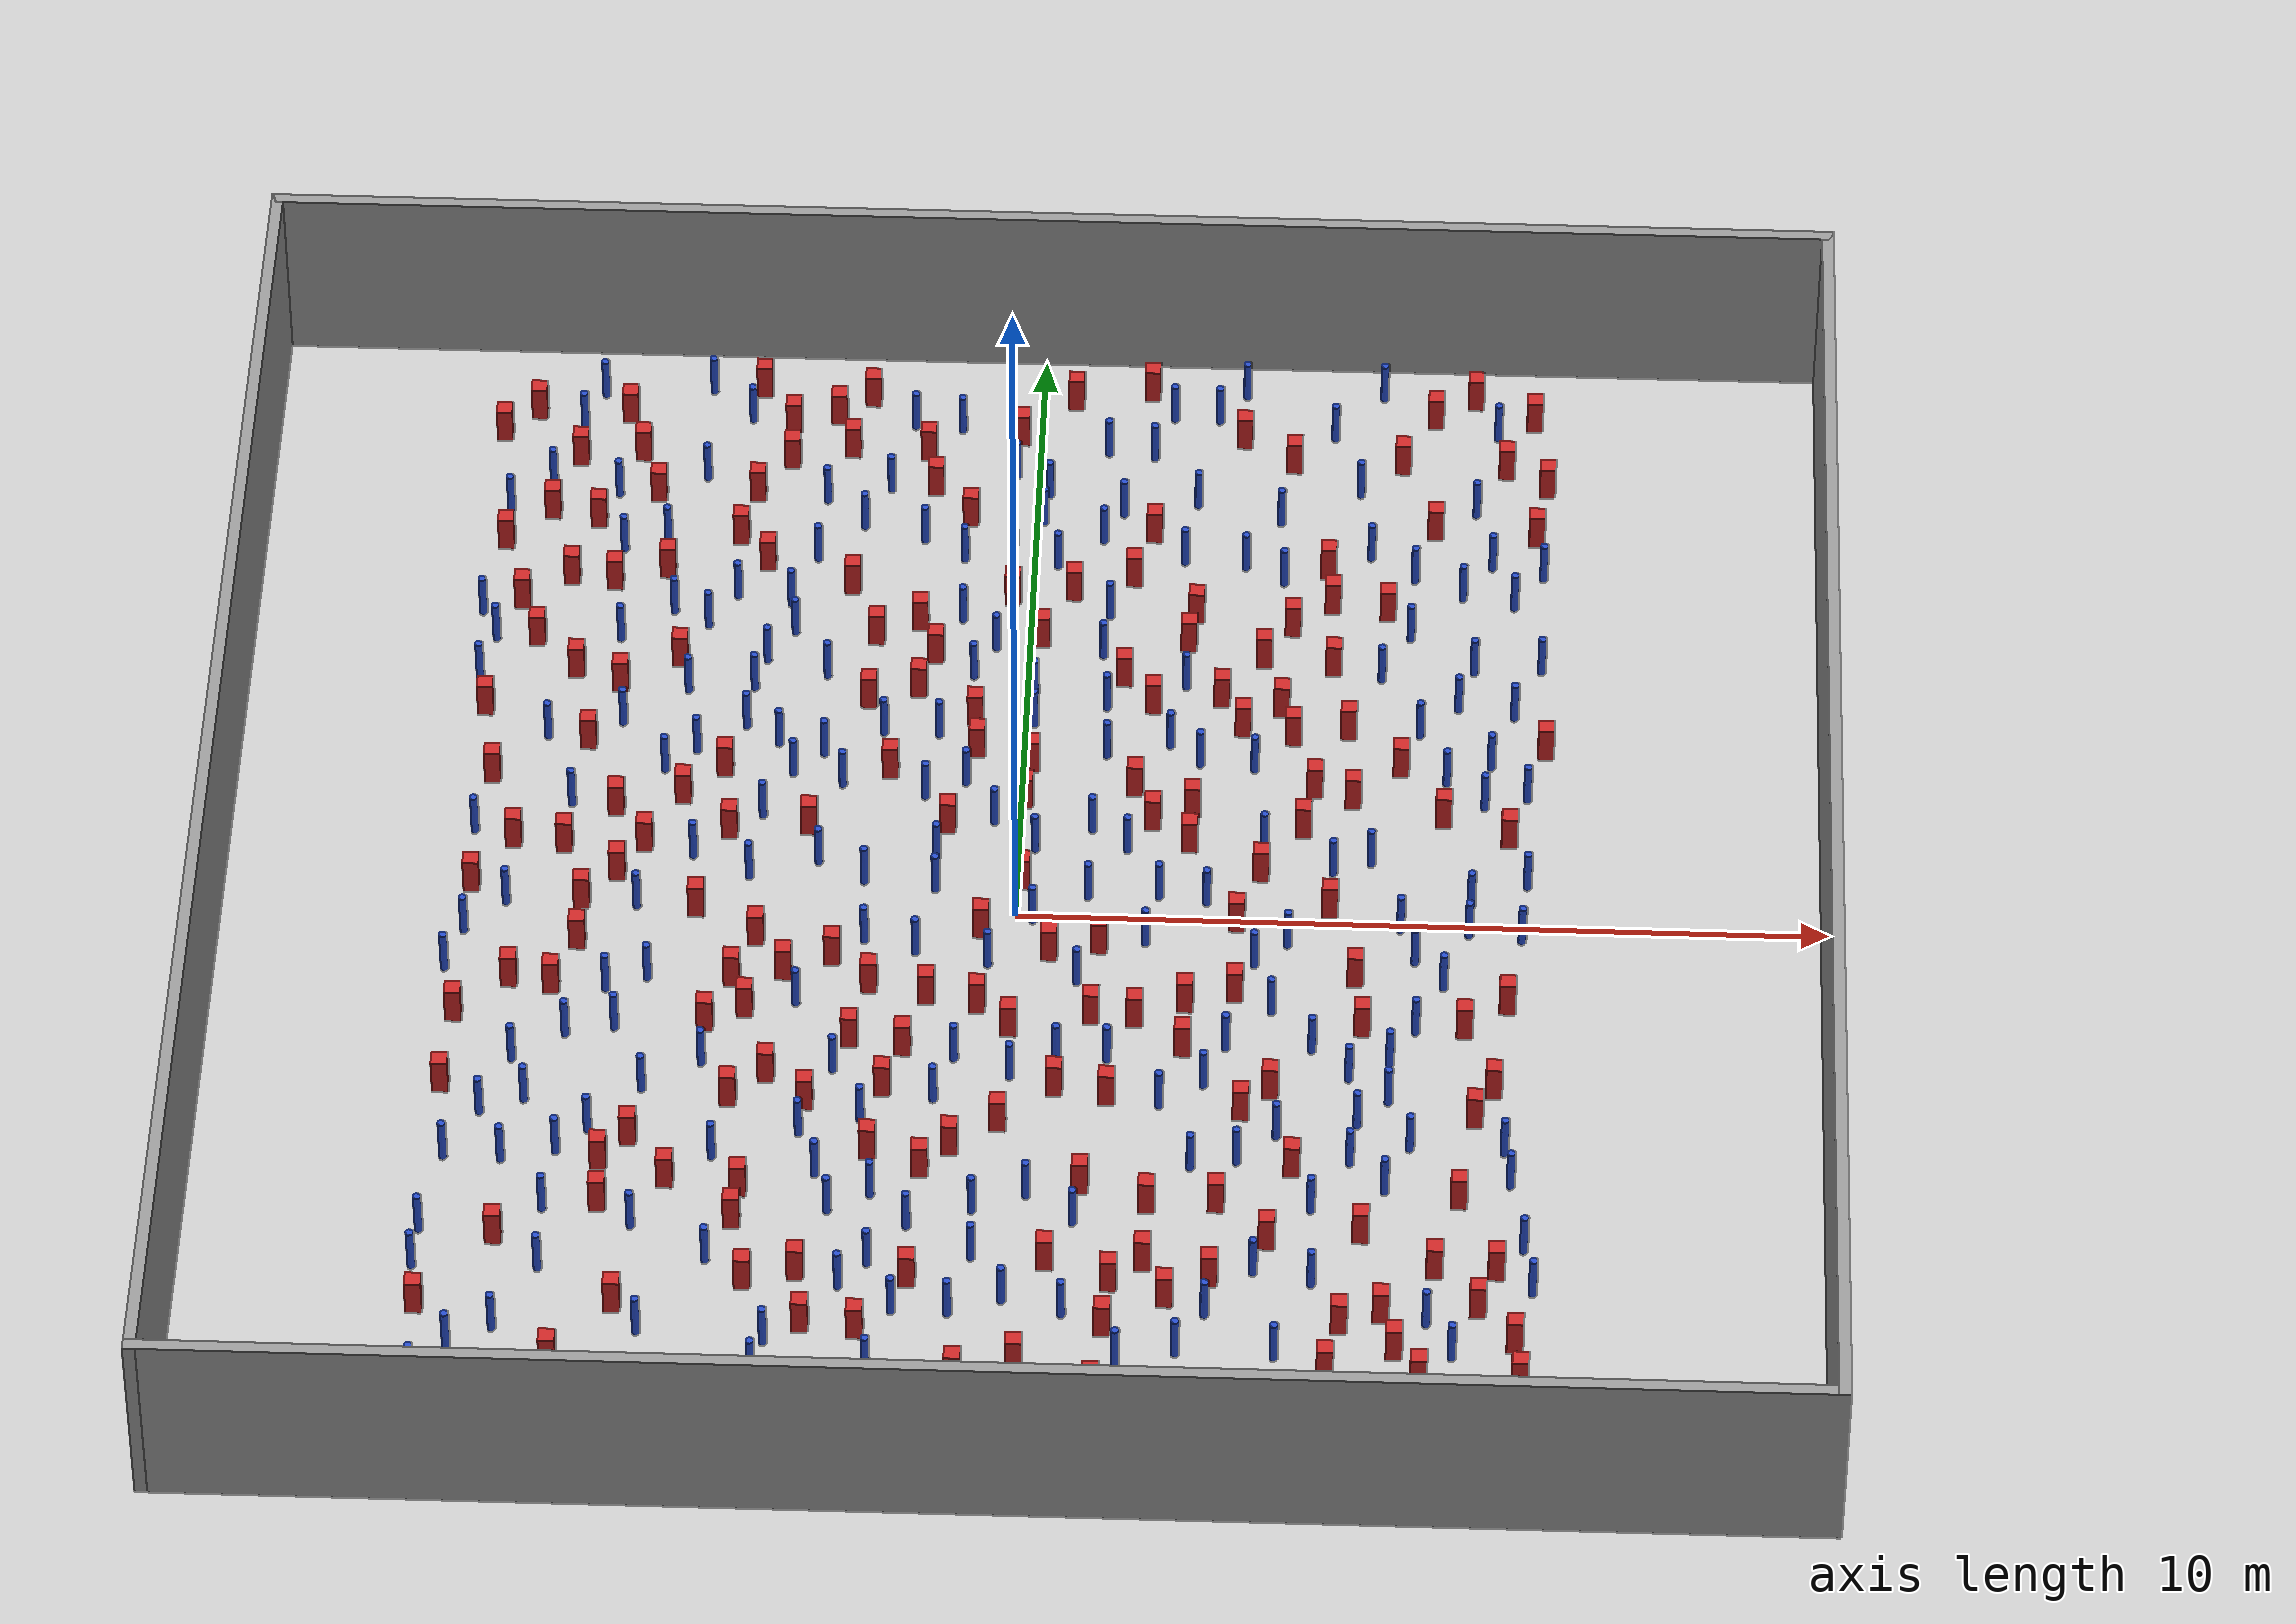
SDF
<sdf version="1.6">
 <world name="default">
  <light name="sun" type="directional">
   <pose>0 0 1000 0 -0 0</pose>
   <diffuse>0.8 0.8 0.8 1</diffuse>
   <specular>0.1 0.1 0.1 1</specular>
   <attenuation>
    <range>1000</range>
    <constant>0.9</constant>
    <linear>0.01</linear>
    <quadratic>0.001</quadratic>
   </attenuation>
   <direction>-0.5 0.5 -1</direction>
  </light>
  <model name="ground_plane">
   <static>1</static>
   <link name="link">
    <collision name="collision">
     <geometry><plane><normal>0 0 1</normal><size>100 100</size></plane></geometry>
     <surface><friction><ode><mu>100</mu><mu2>50</mu2></ode></friction></surface>
    </collision>
    <visual name="visual">
     <cast_shadows>0</cast_shadows>
     <geometry><plane><normal>0 0 1</normal><size>100 100</size></plane></geometry>
     <material>
      <ambient>1.0 1.0 1.0 1.0</ambient>
      <diffuse>0.8 0.8 0.8 1.0</diffuse>
      <specular>0.01 0.01 0.01 1.000000</specular>
     </material>
    </visual>
   </link>
  </model>
  <gravity>0 0 -9.8</gravity>
  <magnetic_field>6e-06 2.3e-05 -4.2e-05</magnetic_field>
  <atmosphere type="adiabatic"/>
  <physics name="default_physics" default="0" type="ode">
   <max_step_size>0.001</max_step_size>
   <real_time_factor>1</real_time_factor>
   <real_time_update_rate>1000</real_time_update_rate>
  </physics>
  <scene><ambient>0.4 0.4 0.4 1</ambient><background>0.7 0.7 0.7 1</background><shadows>1</shadows></scene>
  <spherical_coordinates>
   <surface_model>EARTH_WGS84</surface_model>
   <latitude_deg>0</latitude_deg>
   <longitude_deg>0</longitude_deg>
   <elevation>0</elevation>
   <heading_deg>0</heading_deg>
  </spherical_coordinates>
  <plugin name="gazebo_occupancy_map" filename="libgazebo_2Dmap_plugin.so">
   <map_resolution>0.05</map_resolution>
   <map_topic>generated_map</map_topic>
   <map_height>0.01</map_height>
   <map_size_x>50</map_size_x>
   <map_size_y>50</map_size_y>
  </plugin>
  <model name="NamedLocations">
   <static>true</static>
   <link name="DefaultStart"><pose>8.5 0 0 0 0 3.14</pose></link>
  </model>
  <model name="20x20_walls">
   <pose>0.044518 0.176112 0 0 -0 0</pose>
   <link name="Wall_1">
    <collision name="Wall_1_Collision">
     <geometry><box><size>20 0.15 2.5</size></box></geometry>
     <pose>0 0 1.25 0 -0 0</pose>
    </collision>
    <visual name="Wall_1_Visual">
     <pose>0 0 1.25 0 -0 0</pose>
     <geometry><box><size>20 0.15 2.5</size></box></geometry>
     <material>
      <script><uri>file://media/materials/scripts/gazebo.material</uri><name>Gazebo/Grey</name></script>
      <ambient>0.976471 0.992157 1 1</ambient>
     </material>
     <meta><layer>0</layer></meta>
    </visual>
    <pose>0 9.925 0 0 -0 0</pose>
   </link>
   <link name="Wall_3">
    <collision name="Wall_3_Collision">
     <geometry><box><size>20 0.15 2.5</size></box></geometry>
     <pose>0 0 1.25 0 -0 0</pose>
    </collision>
    <visual name="Wall_3_Visual">
     <pose>0 0 1.25 0 -0 0</pose>
     <geometry><box><size>20 0.15 2.5</size></box></geometry>
     <material>
      <script><uri>file://media/materials/scripts/gazebo.material</uri><name>Gazebo/Grey</name></script>
      <ambient>0.976471 0.992157 1 1</ambient>
     </material>
     <meta><layer>0</layer></meta>
    </visual>
    <pose>9.925 0 0 0 0 -1.5708</pose>
   </link>
   <link name="Wall_4">
    <collision name="Wall_4_Collision">
     <geometry><box><size>20 0.15 2.5</size></box></geometry>
     <pose>0 0 1.25 0 -0 0</pose>
    </collision>
    <visual name="Wall_4_Visual">
     <pose>0 0 1.25 0 -0 0</pose>
     <geometry><box><size>20 0.15 2.5</size></box></geometry>
     <material>
      <script><uri>file://media/materials/scripts/gazebo.material</uri><name>Gazebo/Grey</name></script>
      <ambient>0.976471 0.992157 1 1</ambient>
     </material>
     <meta><layer>0</layer></meta>
    </visual>
    <pose>0 -9.925 0 0 -0 3.14159</pose>
   </link>
   <link name="Wall_5">
    <collision name="Wall_5_Collision">
     <geometry><box><size>20 0.15 2.5</size></box></geometry>
     <pose>0 0 1.25 0 -0 0</pose>
    </collision>
    <visual name="Wall_5_Visual">
     <pose>0 0 1.25 0 -0 0</pose>
     <geometry><box><size>20 0.15 2.5</size></box></geometry>
     <material>
      <script><uri>file://media/materials/scripts/gazebo.material</uri><name>Gazebo/Grey</name></script>
      <ambient>0.976471 0.992157 1 1</ambient>
     </material>
     <meta><layer>0</layer></meta>
    </visual>
    <pose>-9.925 0 0 0 -0 1.5708</pose>
   </link>
   <static>1</static>
  </model>
  <model name="square_post_obstacle0">
   <static>true</static>
   <pose>0.0291481292182 1.97448072141 1.91545236811e-07 -7.35059704564e-06 1.12565212e-07 2.39332434364e-05</pose>
   <link name="link">
    <pose>0 0 0.25 0 -0 0</pose>
    <inertial>
     <mass>100</mass>
     <inertia>
      <ixx>0.166667</ixx>
      <ixy>0</ixy>
      <ixz>0</ixz>
      <iyy>0.166667</iyy>
      <iyz>0</iyz>
      <izz>0.166667</izz>
     </inertia>
    </inertial>
    <collision name="collision"><geometry><box><size>.2 .2 .5</size></box></geometry></collision>
    <visual name="visual">
     <geometry><box><size>.2 .2 .5</size></box></geometry>
     <material>
      <script><name>Gazebo/Red</name><uri>file://media/materials/scripts/gazebo.material</uri></script>
     </material>
    </visual>
   </link>
  </model>
  <model name="square_post_obstacle1">
   <static>true</static>
   <pose>-6.74980819565 6.41191254791 1.91545236811e-07 -7.35059704564e-06 1.12565212e-07 2.39332434364e-05</pose>
   <link name="link">
    <pose>0 0 0.25 0 -0 0</pose>
    <inertial>
     <mass>100</mass>
     <inertia>
      <ixx>0.166667</ixx>
      <ixy>0</ixy>
      <ixz>0</ixz>
      <iyy>0.166667</iyy>
      <iyz>0</iyz>
      <izz>0.166667</izz>
     </inertia>
    </inertial>
    <collision name="collision"><geometry><box><size>.2 .2 .5</size></box></geometry></collision>
    <visual name="visual">
     <geometry><box><size>.2 .2 .5</size></box></geometry>
     <material>
      <script><name>Gazebo/Red</name><uri>file://media/materials/scripts/gazebo.material</uri></script>
     </material>
    </visual>
   </link>
  </model>
  <model name="pole_obstacle0">
   <static>true</static>
   <pose>-2.47867207568 0.840355301405 7.38925637345e-09 -8.471706928e-08 1.24976765177e-08 -1.74513093012e-07</pose>
   <link name="link">
    <pose>0 0 0.3 0 -0 0</pose>
    <inertial>
     <mass>1</mass>
     <inertia><ixx>0.145833</ixx><ixy>0</ixy><ixz>0</ixz><iyy>0.145833</iyy><iyz>0</iyz><izz>0.125</izz></inertia>
    </inertial>
    <collision name="collision">
     <geometry><cylinder><radius>0.05</radius><length>.6</length></cylinder></geometry>
    </collision>
    <visual name="visual">
     <geometry><cylinder><radius>0.05</radius><length>.6</length></cylinder></geometry>
     <material>
      <script><name>Gazebo/Blue</name><uri>file://media/materials/scripts/gazebo.material</uri></script>
     </material>
    </visual>
   </link>
  </model>
  <model name="square_post_obstacle2">
   <static>true</static>
   <pose>5.06235247222 6.9928608238 1.91545236811e-07 -7.35059704564e-06 1.12565212e-07 2.39332434364e-05</pose>
   <link name="link">
    <pose>0 0 0.25 0 -0 0</pose>
    <inertial>
     <mass>100</mass>
     <inertia>
      <ixx>0.166667</ixx>
      <ixy>0</ixy>
      <ixz>0</ixz>
      <iyy>0.166667</iyy>
      <iyz>0</iyz>
      <izz>0.166667</izz>
     </inertia>
    </inertial>
    <collision name="collision"><geometry><box><size>.2 .2 .5</size></box></geometry></collision>
    <visual name="visual">
     <geometry><box><size>.2 .2 .5</size></box></geometry>
     <material>
      <script><name>Gazebo/Red</name><uri>file://media/materials/scripts/gazebo.material</uri></script>
     </material>
    </visual>
   </link>
  </model>
  <model name="pole_obstacle1">
   <static>true</static>
   <pose>4.88868578763 -8.25495165366 7.38925637345e-09 -8.471706928e-08 1.24976765081e-08 -1.74513093015e-07</pose>
   <link name="link">
    <pose>0 0 0.3 0 -0 0</pose>
    <inertial>
     <mass>1</mass>
     <inertia><ixx>0.145833</ixx><ixy>0</ixy><ixz>0</ixz><iyy>0.145833</iyy><iyz>0</iyz><izz>0.125</izz></inertia>
    </inertial>
    <collision name="collision">
     <geometry><cylinder><radius>0.05</radius><length>.6</length></cylinder></geometry>
    </collision>
    <visual name="visual">
     <geometry><cylinder><radius>0.05</radius><length>.6</length></cylinder></geometry>
     <material>
      <script><name>Gazebo/Blue</name><uri>file://media/materials/scripts/gazebo.material</uri></script>
     </material>
    </visual>
   </link>
  </model>
  <model name="square_post_obstacle3">
   <static>true</static>
   <pose>2.94044296209 4.58378525591 1.91545236811e-07 -7.35059704564e-06 1.12565212e-07 2.39332434364e-05</pose>
   <link name="link">
    <pose>0 0 0.25 0 -0 0</pose>
    <inertial>
     <mass>100</mass>
     <inertia>
      <ixx>0.166667</ixx>
      <ixy>0</ixy>
      <ixz>0</ixz>
      <iyy>0.166667</iyy>
      <iyz>0</iyz>
      <izz>0.166667</izz>
     </inertia>
    </inertial>
    <collision name="collision"><geometry><box><size>.2 .2 .5</size></box></geometry></collision>
    <visual name="visual">
     <geometry><box><size>.2 .2 .5</size></box></geometry>
     <material>
      <script><name>Gazebo/Red</name><uri>file://media/materials/scripts/gazebo.material</uri></script>
     </material>
    </visual>
   </link>
  </model>
  <model name="pole_obstacle2">
   <static>true</static>
   <pose>-2.07227371819 -5.04771171933 7.38925637345e-09 -8.47170692798e-08 1.24976765033e-08 -1.74513093019e-07</pose>
   <link name="link">
    <pose>0 0 0.3 0 -0 0</pose>
    <inertial>
     <mass>1</mass>
     <inertia><ixx>0.145833</ixx><ixy>0</ixy><ixz>0</ixz><iyy>0.145833</iyy><iyz>0</iyz><izz>0.125</izz></inertia>
    </inertial>
    <collision name="collision">
     <geometry><cylinder><radius>0.05</radius><length>.6</length></cylinder></geometry>
    </collision>
    <visual name="visual">
     <geometry><cylinder><radius>0.05</radius><length>.6</length></cylinder></geometry>
     <material>
      <script><name>Gazebo/Blue</name><uri>file://media/materials/scripts/gazebo.material</uri></script>
     </material>
    </visual>
   </link>
  </model>
  <model name="pole_obstacle3">
   <static>true</static>
   <pose>5.14229467991 -6.63828792277 7.38925637345e-09 -8.47170692796e-08 1.24976764786e-08 -1.74513093032e-07</pose>
   <link name="link">
    <pose>0 0 0.3 0 -0 0</pose>
    <inertial>
     <mass>1</mass>
     <inertia><ixx>0.145833</ixx><ixy>0</ixy><ixz>0</ixz><iyy>0.145833</iyy><iyz>0</iyz><izz>0.125</izz></inertia>
    </inertial>
    <collision name="collision">
     <geometry><cylinder><radius>0.05</radius><length>.6</length></cylinder></geometry>
    </collision>
    <visual name="visual">
     <geometry><cylinder><radius>0.05</radius><length>.6</length></cylinder></geometry>
     <material>
      <script><name>Gazebo/Blue</name><uri>file://media/materials/scripts/gazebo.material</uri></script>
     </material>
    </visual>
   </link>
  </model>
  <model name="square_post_obstacle4">
   <static>true</static>
   <pose>5.75681799683 -8.28340268561 1.91545236811e-07 -7.35059704564e-06 1.12565212e-07 2.39332434364e-05</pose>
   <link name="link">
    <pose>0 0 0.25 0 -0 0</pose>
    <inertial>
     <mass>100</mass>
     <inertia>
      <ixx>0.166667</ixx>
      <ixy>0</ixy>
      <ixz>0</ixz>
      <iyy>0.166667</iyy>
      <iyz>0</iyz>
      <izz>0.166667</izz>
     </inertia>
    </inertial>
    <collision name="collision"><geometry><box><size>.2 .2 .5</size></box></geometry></collision>
    <visual name="visual">
     <geometry><box><size>.2 .2 .5</size></box></geometry>
     <material>
      <script><name>Gazebo/Red</name><uri>file://media/materials/scripts/gazebo.material</uri></script>
     </material>
    </visual>
   </link>
  </model>
  <model name="square_post_obstacle5">
   <static>true</static>
   <pose>0.504304640819 5.7172666368 1.91545236811e-07 -7.35059704564e-06 1.12565212e-07 2.39332434364e-05</pose>
   <link name="link">
    <pose>0 0 0.25 0 -0 0</pose>
    <inertial>
     <mass>100</mass>
     <inertia>
      <ixx>0.166667</ixx>
      <ixy>0</ixy>
      <ixz>0</ixz>
      <iyy>0.166667</iyy>
      <iyz>0</iyz>
      <izz>0.166667</izz>
     </inertia>
    </inertial>
    <collision name="collision"><geometry><box><size>.2 .2 .5</size></box></geometry></collision>
    <visual name="visual">
     <geometry><box><size>.2 .2 .5</size></box></geometry>
     <material>
      <script><name>Gazebo/Red</name><uri>file://media/materials/scripts/gazebo.material</uri></script>
     </material>
    </visual>
   </link>
  </model>
  <model name="square_post_obstacle6">
   <static>true</static>
   <pose>5.95766056087 8.14996641088 1.91545236811e-07 -7.35059704564e-06 1.12565212e-07 2.39332434364e-05</pose>
   <link name="link">
    <pose>0 0 0.25 0 -0 0</pose>
    <inertial>
     <mass>100</mass>
     <inertia>
      <ixx>0.166667</ixx>
      <ixy>0</ixy>
      <ixz>0</ixz>
      <iyy>0.166667</iyy>
      <iyz>0</iyz>
      <izz>0.166667</izz>
     </inertia>
    </inertial>
    <collision name="collision"><geometry><box><size>.2 .2 .5</size></box></geometry></collision>
    <visual name="visual">
     <geometry><box><size>.2 .2 .5</size></box></geometry>
     <material>
      <script><name>Gazebo/Red</name><uri>file://media/materials/scripts/gazebo.material</uri></script>
     </material>
    </visual>
   </link>
  </model>
  <model name="pole_obstacle4">
   <static>true</static>
   <pose>-1.27591445963 -8.91077670129 7.38925637345e-09 -8.47170692798e-08 1.24976764881e-08 -1.74513093027e-07</pose>
   <link name="link">
    <pose>0 0 0.3 0 -0 0</pose>
    <inertial>
     <mass>1</mass>
     <inertia><ixx>0.145833</ixx><ixy>0</ixy><ixz>0</ixz><iyy>0.145833</iyy><iyz>0</iyz><izz>0.125</izz></inertia>
    </inertial>
    <collision name="collision">
     <geometry><cylinder><radius>0.05</radius><length>.6</length></cylinder></geometry>
    </collision>
    <visual name="visual">
     <geometry><cylinder><radius>0.05</radius><length>.6</length></cylinder></geometry>
     <material>
      <script><name>Gazebo/Blue</name><uri>file://media/materials/scripts/gazebo.material</uri></script>
     </material>
    </visual>
   </link>
  </model>
  <model name="pole_obstacle5">
   <static>true</static>
   <pose>1.44780007454 8.27614773317 7.38925637345e-09 -8.47170692798e-08 1.24976764881e-08 -1.74513093027e-07</pose>
   <link name="link">
    <pose>0 0 0.3 0 -0 0</pose>
    <inertial>
     <mass>1</mass>
     <inertia><ixx>0.145833</ixx><ixy>0</ixy><ixz>0</ixz><iyy>0.145833</iyy><iyz>0</iyz><izz>0.125</izz></inertia>
    </inertial>
    <collision name="collision">
     <geometry><cylinder><radius>0.05</radius><length>.6</length></cylinder></geometry>
    </collision>
    <visual name="visual">
     <geometry><cylinder><radius>0.05</radius><length>.6</length></cylinder></geometry>
     <material>
      <script><name>Gazebo/Blue</name><uri>file://media/materials/scripts/gazebo.material</uri></script>
     </material>
    </visual>
   </link>
  </model>
  <model name="square_post_obstacle7">
   <static>true</static>
   <pose>5.75419726589 -6.40110719447 1.91545236811e-07 -7.35059704564e-06 1.12565212e-07 2.39332434364e-05</pose>
   <link name="link">
    <pose>0 0 0.25 0 -0 0</pose>
    <inertial>
     <mass>100</mass>
     <inertia>
      <ixx>0.166667</ixx>
      <ixy>0</ixy>
      <ixz>0</ixz>
      <iyy>0.166667</iyy>
      <iyz>0</iyz>
      <izz>0.166667</izz>
     </inertia>
    </inertial>
    <collision name="collision"><geometry><box><size>.2 .2 .5</size></box></geometry></collision>
    <visual name="visual">
     <geometry><box><size>.2 .2 .5</size></box></geometry>
     <material>
      <script><name>Gazebo/Red</name><uri>file://media/materials/scripts/gazebo.material</uri></script>
     </material>
    </visual>
   </link>
  </model>
  <model name="square_post_obstacle8">
   <static>true</static>
   <pose>-5.31815626611 5.71131109197 1.91545236811e-07 -7.35059704564e-06 1.12565212e-07 2.39332434364e-05</pose>
   <link name="link">
    <pose>0 0 0.25 0 -0 0</pose>
    <inertial>
     <mass>100</mass>
     <inertia>
      <ixx>0.166667</ixx>
      <ixy>0</ixy>
      <ixz>0</ixz>
      <iyy>0.166667</iyy>
      <iyz>0</iyz>
      <izz>0.166667</izz>
     </inertia>
    </inertial>
    <collision name="collision"><geometry><box><size>.2 .2 .5</size></box></geometry></collision>
    <visual name="visual">
     <geometry><box><size>.2 .2 .5</size></box></geometry>
     <material>
      <script><name>Gazebo/Red</name><uri>file://media/materials/scripts/gazebo.material</uri></script>
     </material>
    </visual>
   </link>
  </model>
  <model name="pole_obstacle6">
   <static>true</static>
   <pose>-4.41659164661 -5.37724809579 7.38925637345e-09 -8.47170692796e-08 1.24976764786e-08 -1.74513093032e-07</pose>
   <link name="link">
    <pose>0 0 0.3 0 -0 0</pose>
    <inertial>
     <mass>1</mass>
     <inertia><ixx>0.145833</ixx><ixy>0</ixy><ixz>0</ixz><iyy>0.145833</iyy><iyz>0</iyz><izz>0.125</izz></inertia>
    </inertial>
    <collision name="collision">
     <geometry><cylinder><radius>0.05</radius><length>.6</length></cylinder></geometry>
    </collision>
    <visual name="visual">
     <geometry><cylinder><radius>0.05</radius><length>.6</length></cylinder></geometry>
     <material>
      <script><name>Gazebo/Blue</name><uri>file://media/materials/scripts/gazebo.material</uri></script>
     </material>
    </visual>
   </link>
  </model>
  <model name="pole_obstacle7">
   <static>true</static>
   <pose>4.90631753604 -3.78050220913 7.38925637345e-09 -8.47170692798e-08 1.24976764937e-08 -1.74513093023e-07</pose>
   <link name="link">
    <pose>0 0 0.3 0 -0 0</pose>
    <inertial>
     <mass>1</mass>
     <inertia><ixx>0.145833</ixx><ixy>0</ixy><ixz>0</ixz><iyy>0.145833</iyy><iyz>0</iyz><izz>0.125</izz></inertia>
    </inertial>
    <collision name="collision">
     <geometry><cylinder><radius>0.05</radius><length>.6</length></cylinder></geometry>
    </collision>
    <visual name="visual">
     <geometry><cylinder><radius>0.05</radius><length>.6</length></cylinder></geometry>
     <material>
      <script><name>Gazebo/Blue</name><uri>file://media/materials/scripts/gazebo.material</uri></script>
     </material>
    </visual>
   </link>
  </model>
  <model name="square_post_obstacle9">
   <static>true</static>
   <pose>-1.41606634563 5.10704584635 1.91545236811e-07 -7.35059704564e-06 1.12565212e-07 2.39332434364e-05</pose>
   <link name="link">
    <pose>0 0 0.25 0 -0 0</pose>
    <inertial>
     <mass>100</mass>
     <inertia>
      <ixx>0.166667</ixx>
      <ixy>0</ixy>
      <ixz>0</ixz>
      <iyy>0.166667</iyy>
      <iyz>0</iyz>
      <izz>0.166667</izz>
     </inertia>
    </inertial>
    <collision name="collision"><geometry><box><size>.2 .2 .5</size></box></geometry></collision>
    <visual name="visual">
     <geometry><box><size>.2 .2 .5</size></box></geometry>
     <material>
      <script><name>Gazebo/Red</name><uri>file://media/materials/scripts/gazebo.material</uri></script>
     </material>
    </visual>
   </link>
  </model>
  <model name="square_post_obstacle10">
   <static>true</static>
   <pose>-1.11626901914 -8.03755662252 1.91545236811e-07 -7.35059704564e-06 1.12565212e-07 2.39332434364e-05</pose>
   <link name="link">
    <pose>0 0 0.25 0 -0 0</pose>
    <inertial>
     <mass>100</mass>
     <inertia>
      <ixx>0.166667</ixx>
      <ixy>0</ixy>
      <ixz>0</ixz>
      <iyy>0.166667</iyy>
      <iyz>0</iyz>
      <izz>0.166667</izz>
     </inertia>
    </inertial>
    <collision name="collision"><geometry><box><size>.2 .2 .5</size></box></geometry></collision>
    <visual name="visual">
     <geometry><box><size>.2 .2 .5</size></box></geometry>
     <material>
      <script><name>Gazebo/Red</name><uri>file://media/materials/scripts/gazebo.material</uri></script>
     </material>
    </visual>
   </link>
  </model>
  <model name="square_post_obstacle11">
   <static>true</static>
   <pose>4.39549333194 -8.90382253059 1.91545236811e-07 -7.35059704564e-06 1.12565212e-07 2.39332434364e-05</pose>
   <link name="link">
    <pose>0 0 0.25 0 -0 0</pose>
    <inertial>
     <mass>100</mass>
     <inertia>
      <ixx>0.166667</ixx>
      <ixy>0</ixy>
      <ixz>0</ixz>
      <iyy>0.166667</iyy>
      <iyz>0</iyz>
      <izz>0.166667</izz>
     </inertia>
    </inertial>
    <collision name="collision"><geometry><box><size>.2 .2 .5</size></box></geometry></collision>
    <visual name="visual">
     <geometry><box><size>.2 .2 .5</size></box></geometry>
     <material>
      <script><name>Gazebo/Red</name><uri>file://media/materials/scripts/gazebo.material</uri></script>
     </material>
    </visual>
   </link>
  </model>
  <model name="square_post_obstacle12">
   <static>true</static>
   <pose>-3.24968776306 -1.7492134352 1.91545236811e-07 -7.35059704564e-06 1.12565212e-07 2.39332434364e-05</pose>
   <link name="link">
    <pose>0 0 0.25 0 -0 0</pose>
    <inertial>
     <mass>100</mass>
     <inertia>
      <ixx>0.166667</ixx>
      <ixy>0</ixy>
      <ixz>0</ixz>
      <iyy>0.166667</iyy>
      <iyz>0</iyz>
      <izz>0.166667</izz>
     </inertia>
    </inertial>
    <collision name="collision"><geometry><box><size>.2 .2 .5</size></box></geometry></collision>
    <visual name="visual">
     <geometry><box><size>.2 .2 .5</size></box></geometry>
     <material>
      <script><name>Gazebo/Red</name><uri>file://media/materials/scripts/gazebo.material</uri></script>
     </material>
    </visual>
   </link>
  </model>
  <model name="square_post_obstacle13">
   <static>true</static>
   <pose>4.59887530118 -6.53221918266 1.91545236811e-07 -7.35059704564e-06 1.12565212e-07 2.39332434364e-05</pose>
   <link name="link">
    <pose>0 0 0.25 0 -0 0</pose>
    <inertial>
     <mass>100</mass>
     <inertia>
      <ixx>0.166667</ixx>
      <ixy>0</ixy>
      <ixz>0</ixz>
      <iyy>0.166667</iyy>
      <iyz>0</iyz>
      <izz>0.166667</izz>
     </inertia>
    </inertial>
    <collision name="collision"><geometry><box><size>.2 .2 .5</size></box></geometry></collision>
    <visual name="visual">
     <geometry><box><size>.2 .2 .5</size></box></geometry>
     <material>
      <script><name>Gazebo/Red</name><uri>file://media/materials/scripts/gazebo.material</uri></script>
     </material>
    </visual>
   </link>
  </model>
  <model name="pole_obstacle8">
   <static>true</static>
   <pose>2.63761670233 -2.16854106117 7.38925637345e-09 -8.47170692798e-08 1.24976764939e-08 -1.74513093025e-07</pose>
   <link name="link">
    <pose>0 0 0.3 0 -0 0</pose>
    <inertial>
     <mass>1</mass>
     <inertia><ixx>0.145833</ixx><ixy>0</ixy><ixz>0</ixz><iyy>0.145833</iyy><iyz>0</iyz><izz>0.125</izz></inertia>
    </inertial>
    <collision name="collision">
     <geometry><cylinder><radius>0.05</radius><length>.6</length></cylinder></geometry>
    </collision>
    <visual name="visual">
     <geometry><cylinder><radius>0.05</radius><length>.6</length></cylinder></geometry>
     <material>
      <script><name>Gazebo/Blue</name><uri>file://media/materials/scripts/gazebo.material</uri></script>
     </material>
    </visual>
   </link>
  </model>
  <model name="square_post_obstacle14">
   <static>true</static>
   <pose>-6.19371936549 6.98780163271 1.91545236811e-07 -7.35059704564e-06 1.12565212e-07 2.39332434364e-05</pose>
   <link name="link">
    <pose>0 0 0.25 0 -0 0</pose>
    <inertial>
     <mass>100</mass>
     <inertia>
      <ixx>0.166667</ixx>
      <ixy>0</ixy>
      <ixz>0</ixz>
      <iyy>0.166667</iyy>
      <iyz>0</iyz>
      <izz>0.166667</izz>
     </inertia>
    </inertial>
    <collision name="collision"><geometry><box><size>.2 .2 .5</size></box></geometry></collision>
    <visual name="visual">
     <geometry><box><size>.2 .2 .5</size></box></geometry>
     <material>
      <script><name>Gazebo/Red</name><uri>file://media/materials/scripts/gazebo.material</uri></script>
     </material>
    </visual>
   </link>
  </model>
  <model name="square_post_obstacle15">
   <static>true</static>
   <pose>5.23388561417 1.81735451772 1.91545236811e-07 -7.35059704564e-06 1.12565212e-07 2.39332434364e-05</pose>
   <link name="link">
    <pose>0 0 0.25 0 -0 0</pose>
    <inertial>
     <mass>100</mass>
     <inertia>
      <ixx>0.166667</ixx>
      <ixy>0</ixy>
      <ixz>0</ixz>
      <iyy>0.166667</iyy>
      <iyz>0</iyz>
      <izz>0.166667</izz>
     </inertia>
    </inertial>
    <collision name="collision"><geometry><box><size>.2 .2 .5</size></box></geometry></collision>
    <visual name="visual">
     <geometry><box><size>.2 .2 .5</size></box></geometry>
     <material>
      <script><name>Gazebo/Red</name><uri>file://media/materials/scripts/gazebo.material</uri></script>
     </material>
    </visual>
   </link>
  </model>
  <model name="square_post_obstacle16">
   <static>true</static>
   <pose>3.6259601431 2.28239656154 1.91545236811e-07 -7.35059704564e-06 1.12565212e-07 2.39332434364e-05</pose>
   <link name="link">
    <pose>0 0 0.25 0 -0 0</pose>
    <inertial>
     <mass>100</mass>
     <inertia>
      <ixx>0.166667</ixx>
      <ixy>0</ixy>
      <ixz>0</ixz>
      <iyy>0.166667</iyy>
      <iyz>0</iyz>
      <izz>0.166667</izz>
     </inertia>
    </inertial>
    <collision name="collision"><geometry><box><size>.2 .2 .5</size></box></geometry></collision>
    <visual name="visual">
     <geometry><box><size>.2 .2 .5</size></box></geometry>
     <material>
      <script><name>Gazebo/Red</name><uri>file://media/materials/scripts/gazebo.material</uri></script>
     </material>
    </visual>
   </link>
  </model>
  <model name="pole_obstacle9">
   <static>true</static>
   <pose>-0.332700703792 1.61640806148 7.38925637345e-09 -8.47170692798e-08 1.24976765025e-08 -1.74513093018e-07</pose>
   <link name="link">
    <pose>0 0 0.3 0 -0 0</pose>
    <inertial>
     <mass>1</mass>
     <inertia><ixx>0.145833</ixx><ixy>0</ixy><ixz>0</ixz><iyy>0.145833</iyy><iyz>0</iyz><izz>0.125</izz></inertia>
    </inertial>
    <collision name="collision">
     <geometry><cylinder><radius>0.05</radius><length>.6</length></cylinder></geometry>
    </collision>
    <visual name="visual">
     <geometry><cylinder><radius>0.05</radius><length>.6</length></cylinder></geometry>
     <material>
      <script><name>Gazebo/Blue</name><uri>file://media/materials/scripts/gazebo.material</uri></script>
     </material>
    </visual>
   </link>
  </model>
  <model name="square_post_obstacle17">
   <static>true</static>
   <pose>1.19263947999 4.18591377882 1.91545236811e-07 -7.35059704564e-06 1.12565212e-07 2.39332434364e-05</pose>
   <link name="link">
    <pose>0 0 0.25 0 -0 0</pose>
    <inertial>
     <mass>100</mass>
     <inertia>
      <ixx>0.166667</ixx>
      <ixy>0</ixy>
      <ixz>0</ixz>
      <iyy>0.166667</iyy>
      <iyz>0</iyz>
      <izz>0.166667</izz>
     </inertia>
    </inertial>
    <collision name="collision"><geometry><box><size>.2 .2 .5</size></box></geometry></collision>
    <visual name="visual">
     <geometry><box><size>.2 .2 .5</size></box></geometry>
     <material>
      <script><name>Gazebo/Red</name><uri>file://media/materials/scripts/gazebo.material</uri></script>
     </material>
    </visual>
   </link>
  </model>
  <model name="square_post_obstacle18">
   <static>true</static>
   <pose>-6.61899511941 2.2001608729 1.91545236811e-07 -7.35059704564e-06 1.12565212e-07 2.39332434364e-05</pose>
   <link name="link">
    <pose>0 0 0.25 0 -0 0</pose>
    <inertial>
     <mass>100</mass>
     <inertia>
      <ixx>0.166667</ixx>
      <ixy>0</ixy>
      <ixz>0</ixz>
      <iyy>0.166667</iyy>
      <iyz>0</iyz>
      <izz>0.166667</izz>
     </inertia>
    </inertial>
    <collision name="collision"><geometry><box><size>.2 .2 .5</size></box></geometry></collision>
    <visual name="visual">
     <geometry><box><size>.2 .2 .5</size></box></geometry>
     <material>
      <script><name>Gazebo/Red</name><uri>file://media/materials/scripts/gazebo.material</uri></script>
     </material>
    </visual>
   </link>
  </model>
  <model name="pole_obstacle10">
   <static>true</static>
   <pose>4.10078407601 7.67983366689 7.38925637345e-09 -8.47170692796e-08 1.24976764786e-08 -1.74513093032e-07</pose>
   <link name="link">
    <pose>0 0 0.3 0 -0 0</pose>
    <inertial>
     <mass>1</mass>
     <inertia><ixx>0.145833</ixx><ixy>0</ixy><ixz>0</ixz><iyy>0.145833</iyy><iyz>0</iyz><izz>0.125</izz></inertia>
    </inertial>
    <collision name="collision">
     <geometry><cylinder><radius>0.05</radius><length>.6</length></cylinder></geometry>
    </collision>
    <visual name="visual">
     <geometry><cylinder><radius>0.05</radius><length>.6</length></cylinder></geometry>
     <material>
      <script><name>Gazebo/Blue</name><uri>file://media/materials/scripts/gazebo.material</uri></script>
     </material>
    </visual>
   </link>
  </model>
  <model name="square_post_obstacle19">
   <static>true</static>
   <pose>5.90634652753 -2.80103733414 1.91545236811e-07 -7.35059704564e-06 1.12565212e-07 2.39332434364e-05</pose>
   <link name="link">
    <pose>0 0 0.25 0 -0 0</pose>
    <inertial>
     <mass>100</mass>
     <inertia>
      <ixx>0.166667</ixx>
      <ixy>0</ixy>
      <ixz>0</ixz>
      <iyy>0.166667</iyy>
      <iyz>0</iyz>
      <izz>0.166667</izz>
     </inertia>
    </inertial>
    <collision name="collision"><geometry><box><size>.2 .2 .5</size></box></geometry></collision>
    <visual name="visual">
     <geometry><box><size>.2 .2 .5</size></box></geometry>
     <material>
      <script><name>Gazebo/Red</name><uri>file://media/materials/scripts/gazebo.material</uri></script>
     </material>
    </visual>
   </link>
  </model>
  <model name="pole_obstacle11">
   <static>true</static>
   <pose>-1.58580821269 -8.29424901346 7.38925637345e-09 -8.47170692798e-08 1.24976764881e-08 -1.74513093027e-07</pose>
   <link name="link">
    <pose>0 0 0.3 0 -0 0</pose>
    <inertial>
     <mass>1</mass>
     <inertia><ixx>0.145833</ixx><ixy>0</ixy><ixz>0</ixz><iyy>0.145833</iyy><iyz>0</iyz><izz>0.125</izz></inertia>
    </inertial>
    <collision name="collision">
     <geometry><cylinder><radius>0.05</radius><length>.6</length></cylinder></geometry>
    </collision>
    <visual name="visual">
     <geometry><cylinder><radius>0.05</radius><length>.6</length></cylinder></geometry>
     <material>
      <script><name>Gazebo/Blue</name><uri>file://media/materials/scripts/gazebo.material</uri></script>
     </material>
    </visual>
   </link>
  </model>
  <model name="square_post_obstacle20">
   <static>true</static>
   <pose>-6.57853312437 -8.34904074265 1.91545236811e-07 -7.35059704564e-06 1.12565212e-07 2.39332434364e-05</pose>
   <link name="link">
    <pose>0 0 0.25 0 -0 0</pose>
    <inertial>
     <mass>100</mass>
     <inertia>
      <ixx>0.166667</ixx>
      <ixy>0</ixy>
      <ixz>0</ixz>
      <iyy>0.166667</iyy>
      <iyz>0</iyz>
      <izz>0.166667</izz>
     </inertia>
    </inertial>
    <collision name="collision"><geometry><box><size>.2 .2 .5</size></box></geometry></collision>
    <visual name="visual">
     <geometry><box><size>.2 .2 .5</size></box></geometry>
     <material>
      <script><name>Gazebo/Red</name><uri>file://media/materials/scripts/gazebo.material</uri></script>
     </material>
    </visual>
   </link>
  </model>
  <model name="pole_obstacle12">
   <static>true</static>
   <pose>0.798774729147 -6.63545786462 7.38925637345e-09 -8.471706928e-08 1.24976765086e-08 -1.74513093015e-07</pose>
   <link name="link">
    <pose>0 0 0.3 0 -0 0</pose>
    <inertial>
     <mass>1</mass>
     <inertia><ixx>0.145833</ixx><ixy>0</ixy><ixz>0</ixz><iyy>0.145833</iyy><iyz>0</iyz><izz>0.125</izz></inertia>
    </inertial>
    <collision name="collision">
     <geometry><cylinder><radius>0.05</radius><length>.6</length></cylinder></geometry>
    </collision>
    <visual name="visual">
     <geometry><cylinder><radius>0.05</radius><length>.6</length></cylinder></geometry>
     <material>
      <script><name>Gazebo/Blue</name><uri>file://media/materials/scripts/gazebo.material</uri></script>
     </material>
    </visual>
   </link>
  </model>
  <model name="square_post_obstacle21">
   <static>true</static>
   <pose>-2.22867674971 -0.830069548828 1.91545236811e-07 -7.35059704564e-06 1.12565212e-07 2.39332434364e-05</pose>
   <link name="link">
    <pose>0 0 0.25 0 -0 0</pose>
    <inertial>
     <mass>100</mass>
     <inertia>
      <ixx>0.166667</ixx>
      <ixy>0</ixy>
      <ixz>0</ixz>
      <iyy>0.166667</iyy>
      <iyz>0</iyz>
      <izz>0.166667</izz>
     </inertia>
    </inertial>
    <collision name="collision"><geometry><box><size>.2 .2 .5</size></box></geometry></collision>
    <visual name="visual">
     <geometry><box><size>.2 .2 .5</size></box></geometry>
     <material>
      <script><name>Gazebo/Red</name><uri>file://media/materials/scripts/gazebo.material</uri></script>
     </material>
    </visual>
   </link>
  </model>
  <model name="pole_obstacle13">
   <static>true</static>
   <pose>2.60298710889 9.47166998292 7.38925637345e-09 -8.47170692793e-08 1.24976764408e-08 -1.74513093041e-07</pose>
   <link name="link">
    <pose>0 0 0.3 0 -0 0</pose>
    <inertial>
     <mass>1</mass>
     <inertia><ixx>0.145833</ixx><ixy>0</ixy><ixz>0</ixz><iyy>0.145833</iyy><iyz>0</iyz><izz>0.125</izz></inertia>
    </inertial>
    <collision name="collision">
     <geometry><cylinder><radius>0.05</radius><length>.6</length></cylinder></geometry>
    </collision>
    <visual name="visual">
     <geometry><cylinder><radius>0.05</radius><length>.6</length></cylinder></geometry>
     <material>
      <script><name>Gazebo/Blue</name><uri>file://media/materials/scripts/gazebo.material</uri></script>
     </material>
    </visual>
   </link>
  </model>
  <model name="square_post_obstacle22">
   <static>true</static>
   <pose>-0.0848533377362 -3.55925744918 1.91545236811e-07 -7.35059704564e-06 1.12565212e-07 2.39332434364e-05</pose>
   <link name="link">
    <pose>0 0 0.25 0 -0 0</pose>
    <inertial>
     <mass>100</mass>
     <inertia>
      <ixx>0.166667</ixx>
      <ixy>0</ixy>
      <ixz>0</ixz>
      <iyy>0.166667</iyy>
      <iyz>0</iyz>
      <izz>0.166667</izz>
     </inertia>
    </inertial>
    <collision name="collision"><geometry><box><size>.2 .2 .5</size></box></geometry></collision>
    <visual name="visual">
     <geometry><box><size>.2 .2 .5</size></box></geometry>
     <material>
      <script><name>Gazebo/Red</name><uri>file://media/materials/scripts/gazebo.material</uri></script>
     </material>
    </visual>
   </link>
  </model>
  <model name="pole_obstacle14">
   <static>true</static>
   <pose>-1.03722011202 8.71452912254 7.38925637345e-09 -8.47170692798e-08 1.2497676492e-08 -1.74513093025e-07</pose>
   <link name="link">
    <pose>0 0 0.3 0 -0 0</pose>
    <inertial>
     <mass>1</mass>
     <inertia><ixx>0.145833</ixx><ixy>0</ixy><ixz>0</ixz><iyy>0.145833</iyy><iyz>0</iyz><izz>0.125</izz></inertia>
    </inertial>
    <collision name="collision">
     <geometry><cylinder><radius>0.05</radius><length>.6</length></cylinder></geometry>
    </collision>
    <visual name="visual">
     <geometry><cylinder><radius>0.05</radius><length>.6</length></cylinder></geometry>
     <material>
      <script><name>Gazebo/Blue</name><uri>file://media/materials/scripts/gazebo.material</uri></script>
     </material>
    </visual>
   </link>
  </model>
  <model name="pole_obstacle15">
   <static>true</static>
   <pose>1.74778303365 0.38138672804 7.38925637345e-09 -8.47170692799e-08 1.24976765065e-08 -1.74513093017e-07</pose>
   <link name="link">
    <pose>0 0 0.3 0 -0 0</pose>
    <inertial>
     <mass>1</mass>
     <inertia><ixx>0.145833</ixx><ixy>0</ixy><ixz>0</ixz><iyy>0.145833</iyy><iyz>0</iyz><izz>0.125</izz></inertia>
    </inertial>
    <collision name="collision">
     <geometry><cylinder><radius>0.05</radius><length>.6</length></cylinder></geometry>
    </collision>
    <visual name="visual">
     <geometry><cylinder><radius>0.05</radius><length>.6</length></cylinder></geometry>
     <material>
      <script><name>Gazebo/Blue</name><uri>file://media/materials/scripts/gazebo.material</uri></script>
     </material>
    </visual>
   </link>
  </model>
  <model name="pole_obstacle16">
   <static>true</static>
   <pose>-2.48492322059 -3.77934961691 7.38925637345e-09 -8.47170692798e-08 1.24976764939e-08 -1.74513093025e-07</pose>
   <link name="link">
    <pose>0 0 0.3 0 -0 0</pose>
    <inertial>
     <mass>1</mass>
     <inertia><ixx>0.145833</ixx><ixy>0</ixy><ixz>0</ixz><iyy>0.145833</iyy><iyz>0</iyz><izz>0.125</izz></inertia>
    </inertial>
    <collision name="collision">
     <geometry><cylinder><radius>0.05</radius><length>.6</length></cylinder></geometry>
    </collision>
    <visual name="visual">
     <geometry><cylinder><radius>0.05</radius><length>.6</length></cylinder></geometry>
     <material>
      <script><name>Gazebo/Blue</name><uri>file://media/materials/scripts/gazebo.material</uri></script>
     </material>
    </visual>
   </link>
  </model>
  <model name="square_post_obstacle23">
   <static>true</static>
   <pose>-1.29232454125 -2.33395352667 1.91545236811e-07 -7.35059704564e-06 1.12565212e-07 2.39332434364e-05</pose>
   <link name="link">
    <pose>0 0 0.25 0 -0 0</pose>
    <inertial>
     <mass>100</mass>
     <inertia>
      <ixx>0.166667</ixx>
      <ixy>0</ixy>
      <ixz>0</ixz>
      <iyy>0.166667</iyy>
      <iyz>0</iyz>
      <izz>0.166667</izz>
     </inertia>
    </inertial>
    <collision name="collision"><geometry><box><size>.2 .2 .5</size></box></geometry></collision>
    <visual name="visual">
     <geometry><box><size>.2 .2 .5</size></box></geometry>
     <material>
      <script><name>Gazebo/Red</name><uri>file://media/materials/scripts/gazebo.material</uri></script>
     </material>
    </visual>
   </link>
  </model>
  <model name="pole_obstacle17">
   <static>true</static>
   <pose>3.42017889563 -9.2823077383 7.38925637345e-09 -8.47170692793e-08 1.24976764408e-08 -1.74513093041e-07</pose>
   <link name="link">
    <pose>0 0 0.3 0 -0 0</pose>
    <inertial>
     <mass>1</mass>
     <inertia><ixx>0.145833</ixx><ixy>0</ixy><ixz>0</ixz><iyy>0.145833</iyy><iyz>0</iyz><izz>0.125</izz></inertia>
    </inertial>
    <collision name="collision">
     <geometry><cylinder><radius>0.05</radius><length>.6</length></cylinder></geometry>
    </collision>
    <visual name="visual">
     <geometry><cylinder><radius>0.05</radius><length>.6</length></cylinder></geometry>
     <material>
      <script><name>Gazebo/Blue</name><uri>file://media/materials/scripts/gazebo.material</uri></script>
     </material>
    </visual>
   </link>
  </model>
  <model name="square_post_obstacle24">
   <static>true</static>
   <pose>3.81590200415 4.46829043997 1.91545236811e-07 -7.35059704564e-06 1.12565212e-07 2.39332434364e-05</pose>
   <link name="link">
    <pose>0 0 0.25 0 -0 0</pose>
    <inertial>
     <mass>100</mass>
     <inertia>
      <ixx>0.166667</ixx>
      <ixy>0</ixy>
      <ixz>0</ixz>
      <iyy>0.166667</iyy>
      <iyz>0</iyz>
      <izz>0.166667</izz>
     </inertia>
    </inertial>
    <collision name="collision"><geometry><box><size>.2 .2 .5</size></box></geometry></collision>
    <visual name="visual">
     <geometry><box><size>.2 .2 .5</size></box></geometry>
     <material>
      <script><name>Gazebo/Red</name><uri>file://media/materials/scripts/gazebo.material</uri></script>
     </material>
    </visual>
   </link>
  </model>
  <model name="square_post_obstacle25">
   <static>true</static>
   <pose>-3.43950755775 -1.2305479218 1.91545236811e-07 -7.35059704564e-06 1.12565212e-07 2.39332434364e-05</pose>
   <link name="link">
    <pose>0 0 0.25 0 -0 0</pose>
    <inertial>
     <mass>100</mass>
     <inertia>
      <ixx>0.166667</ixx>
      <ixy>0</ixy>
      <ixz>0</ixz>
      <iyy>0.166667</iyy>
      <iyz>0</iyz>
      <izz>0.166667</izz>
     </inertia>
    </inertial>
    <collision name="collision"><geometry><box><size>.2 .2 .5</size></box></geometry></collision>
    <visual name="visual">
     <geometry><box><size>.2 .2 .5</size></box></geometry>
     <material>
      <script><name>Gazebo/Red</name><uri>file://media/materials/scripts/gazebo.material</uri></script>
     </material>
    </visual>
   </link>
  </model>
  <model name="square_post_obstacle26">
   <static>true</static>
   <pose>6.26326169163 -7.56500785191 1.91545236811e-07 -7.35059704564e-06 1.12565212e-07 2.39332434364e-05</pose>
   <link name="link">
    <pose>0 0 0.25 0 -0 0</pose>
    <inertial>
     <mass>100</mass>
     <inertia>
      <ixx>0.166667</ixx>
      <ixy>0</ixy>
      <ixz>0</ixz>
      <iyy>0.166667</iyy>
      <iyz>0</iyz>
      <izz>0.166667</izz>
     </inertia>
    </inertial>
    <collision name="collision"><geometry><box><size>.2 .2 .5</size></box></geometry></collision>
    <visual name="visual">
     <geometry><box><size>.2 .2 .5</size></box></geometry>
     <material>
      <script><name>Gazebo/Red</name><uri>file://media/materials/scripts/gazebo.material</uri></script>
     </material>
    </visual>
   </link>
  </model>
  <model name="square_post_obstacle27">
   <static>true</static>
   <pose>-0.602505569343 2.85441513764 1.91545236811e-07 -7.35059704564e-06 1.12565212e-07 2.39332434364e-05</pose>
   <link name="link">
    <pose>0 0 0.25 0 -0 0</pose>
    <inertial>
     <mass>100</mass>
     <inertia>
      <ixx>0.166667</ixx>
      <ixy>0</ixy>
      <ixz>0</ixz>
      <iyy>0.166667</iyy>
      <iyz>0</iyz>
      <izz>0.166667</izz>
     </inertia>
    </inertial>
    <collision name="collision"><geometry><box><size>.2 .2 .5</size></box></geometry></collision>
    <visual name="visual">
     <geometry><box><size>.2 .2 .5</size></box></geometry>
     <material>
      <script><name>Gazebo/Red</name><uri>file://media/materials/scripts/gazebo.material</uri></script>
     </material>
    </visual>
   </link>
  </model>
  <model name="pole_obstacle18">
   <static>true</static>
   <pose>0.888996541848 1.51933908293 7.38925637345e-09 -8.47170692799e-08 1.24976765033e-08 -1.7451309302e-07</pose>
   <link name="link">
    <pose>0 0 0.3 0 -0 0</pose>
    <inertial>
     <mass>1</mass>
     <inertia><ixx>0.145833</ixx><ixy>0</ixy><ixz>0</ixz><iyy>0.145833</iyy><iyz>0</iyz><izz>0.125</izz></inertia>
    </inertial>
    <collision name="collision">
     <geometry><cylinder><radius>0.05</radius><length>.6</length></cylinder></geometry>
    </collision>
    <visual name="visual">
     <geometry><cylinder><radius>0.05</radius><length>.6</length></cylinder></geometry>
     <material>
      <script><name>Gazebo/Blue</name><uri>file://media/materials/scripts/gazebo.material</uri></script>
     </material>
    </visual>
   </link>
  </model>
  <model name="square_post_obstacle28">
   <static>true</static>
   <pose>-4.53590641707 -3.95308508538 1.91545236811e-07 -7.35059704564e-06 1.12565212e-07 2.39332434364e-05</pose>
   <link name="link">
    <pose>0 0 0.25 0 -0 0</pose>
    <inertial>
     <mass>100</mass>
     <inertia>
      <ixx>0.166667</ixx>
      <ixy>0</ixy>
      <ixz>0</ixz>
      <iyy>0.166667</iyy>
      <iyz>0</iyz>
      <izz>0.166667</izz>
     </inertia>
    </inertial>
    <collision name="collision"><geometry><box><size>.2 .2 .5</size></box></geometry></collision>
    <visual name="visual">
     <geometry><box><size>.2 .2 .5</size></box></geometry>
     <material>
      <script><name>Gazebo/Red</name><uri>file://media/materials/scripts/gazebo.material</uri></script>
     </material>
    </visual>
   </link>
  </model>
  <model name="pole_obstacle19">
   <static>true</static>
   <pose>4.91948108078 -0.641241814981 7.38925637345e-09 -8.47170692799e-08 1.24976765038e-08 -1.74513093018e-07</pose>
   <link name="link">
    <pose>0 0 0.3 0 -0 0</pose>
    <inertial>
     <mass>1</mass>
     <inertia><ixx>0.145833</ixx><ixy>0</ixy><ixz>0</ixz><iyy>0.145833</iyy><iyz>0</iyz><izz>0.125</izz></inertia>
    </inertial>
    <collision name="collision">
     <geometry><cylinder><radius>0.05</radius><length>.6</length></cylinder></geometry>
    </collision>
    <visual name="visual">
     <geometry><cylinder><radius>0.05</radius><length>.6</length></cylinder></geometry>
     <material>
      <script><name>Gazebo/Blue</name><uri>file://media/materials/scripts/gazebo.material</uri></script>
     </material>
    </visual>
   </link>
  </model>
  <model name="square_post_obstacle29">
   <static>true</static>
   <pose>-0.419268702525 -1.57879179032 1.91545236811e-07 -7.35059704564e-06 1.12565212e-07 2.39332434364e-05</pose>
   <link name="link">
    <pose>0 0 0.25 0 -0 0</pose>
    <inertial>
     <mass>100</mass>
     <inertia>
      <ixx>0.166667</ixx>
      <ixy>0</ixy>
      <ixz>0</ixz>
      <iyy>0.166667</iyy>
      <iyz>0</iyz>
      <izz>0.166667</izz>
     </inertia>
    </inertial>
    <collision name="collision"><geometry><box><size>.2 .2 .5</size></box></geometry></collision>
    <visual name="visual">
     <geometry><box><size>.2 .2 .5</size></box></geometry>
     <material>
      <script><name>Gazebo/Red</name><uri>file://media/materials/scripts/gazebo.material</uri></script>
     </material>
    </visual>
   </link>
  </model>
  <model name="square_post_obstacle30">
   <static>true</static>
   <pose>0.975652456838 -1.71907979939 1.91545236811e-07 -7.35059704564e-06 1.12565212e-07 2.39332434364e-05</pose>
   <link name="link">
    <pose>0 0 0.25 0 -0 0</pose>
    <inertial>
     <mass>100</mass>
     <inertia>
      <ixx>0.166667</ixx>
      <ixy>0</ixy>
      <ixz>0</ixz>
      <iyy>0.166667</iyy>
      <iyz>0</iyz>
      <izz>0.166667</izz>
     </inertia>
    </inertial>
    <collision name="collision"><geometry><box><size>.2 .2 .5</size></box></geometry></collision>
    <visual name="visual">
     <geometry><box><size>.2 .2 .5</size></box></geometry>
     <material>
      <script><name>Gazebo/Red</name><uri>file://media/materials/scripts/gazebo.material</uri></script>
     </material>
    </visual>
   </link>
  </model>
  <model name="pole_obstacle20">
   <static>true</static>
   <pose>6.43205474753 4.52265151657 7.38925637345e-09 -8.47170692796e-08 1.24976764786e-08 -1.74513093032e-07</pose>
   <link name="link">
    <pose>0 0 0.3 0 -0 0</pose>
    <inertial>
     <mass>1</mass>
     <inertia><ixx>0.145833</ixx><ixy>0</ixy><ixz>0</ixz><iyy>0.145833</iyy><iyz>0</iyz><izz>0.125</izz></inertia>
    </inertial>
    <collision name="collision">
     <geometry><cylinder><radius>0.05</radius><length>.6</length></cylinder></geometry>
    </collision>
    <visual name="visual">
     <geometry><cylinder><radius>0.05</radius><length>.6</length></cylinder></geometry>
     <material>
      <script><name>Gazebo/Blue</name><uri>file://media/materials/scripts/gazebo.material</uri></script>
     </material>
    </visual>
   </link>
  </model>
  <model name="pole_obstacle21">
   <static>true</static>
   <pose>5.84438588983 8.80280604812 7.38925637345e-09 -8.471706928e-08 1.24976765081e-08 -1.74513093015e-07</pose>
   <link name="link">
    <pose>0 0 0.3 0 -0 0</pose>
    <inertial>
     <mass>1</mass>
     <inertia><ixx>0.145833</ixx><ixy>0</ixy><ixz>0</ixz><iyy>0.145833</iyy><iyz>0</iyz><izz>0.125</izz></inertia>
    </inertial>
    <collision name="collision">
     <geometry><cylinder><radius>0.05</radius><length>.6</length></cylinder></geometry>
    </collision>
    <visual name="visual">
     <geometry><cylinder><radius>0.05</radius><length>.6</length></cylinder></geometry>
     <material>
      <script><name>Gazebo/Blue</name><uri>file://media/materials/scripts/gazebo.material</uri></script>
     </material>
    </visual>
   </link>
  </model>
  <model name="square_post_obstacle31">
   <static>true</static>
   <pose>-6.91142593812 8.42208887054 1.91545236811e-07 -7.35059704564e-06 1.12565212e-07 2.39332434364e-05</pose>
   <link name="link">
    <pose>0 0 0.25 0 -0 0</pose>
    <inertial>
     <mass>100</mass>
     <inertia>
      <ixx>0.166667</ixx>
      <ixy>0</ixy>
      <ixz>0</ixz>
      <iyy>0.166667</iyy>
      <iyz>0</iyz>
      <izz>0.166667</izz>
     </inertia>
    </inertial>
    <collision name="collision"><geometry><box><size>.2 .2 .5</size></box></geometry></collision>
    <visual name="visual">
     <geometry><box><size>.2 .2 .5</size></box></geometry>
     <material>
      <script><name>Gazebo/Red</name><uri>file://media/materials/scripts/gazebo.material</uri></script>
     </material>
    </visual>
   </link>
  </model>
  <model name="pole_obstacle22">
   <static>true</static>
   <pose>4.26076564724 -3.41951765001 7.38925637345e-09 -8.47170692798e-08 1.24976764937e-08 -1.74513093023e-07</pose>
   <link name="link">
    <pose>0 0 0.3 0 -0 0</pose>
    <inertial>
     <mass>1</mass>
     <inertia><ixx>0.145833</ixx><ixy>0</ixy><ixz>0</ixz><iyy>0.145833</iyy><iyz>0</iyz><izz>0.125</izz></inertia>
    </inertial>
    <collision name="collision">
     <geometry><cylinder><radius>0.05</radius><length>.6</length></cylinder></geometry>
    </collision>
    <visual name="visual">
     <geometry><cylinder><radius>0.05</radius><length>.6</length></cylinder></geometry>
     <material>
      <script><name>Gazebo/Blue</name><uri>file://media/materials/scripts/gazebo.material</uri></script>
     </material>
    </visual>
   </link>
  </model>
  <model name="pole_obstacle23">
   <static>true</static>
   <pose>-1.10968277763 -5.27178096615 7.38925637345e-09 -8.47170692799e-08 1.24976765033e-08 -1.74513093018e-07</pose>
   <link name="link">
    <pose>0 0 0.3 0 -0 0</pose>
    <inertial>
     <mass>1</mass>
     <inertia><ixx>0.145833</ixx><ixy>0</ixy><ixz>0</ixz><iyy>0.145833</iyy><iyz>0</iyz><izz>0.125</izz></inertia>
    </inertial>
    <collision name="collision">
     <geometry><cylinder><radius>0.05</radius><length>.6</length></cylinder></geometry>
    </collision>
    <visual name="visual">
     <geometry><cylinder><radius>0.05</radius><length>.6</length></cylinder></geometry>
     <material>
      <script><name>Gazebo/Blue</name><uri>file://media/materials/scripts/gazebo.material</uri></script>
     </material>
    </visual>
   </link>
  </model>
  <model name="pole_obstacle24">
   <static>true</static>
   <pose>-0.882646282621 -3.15868062069 7.38925637345e-09 -8.47170692799e-08 1.2497676509e-08 -1.74513093016e-07</pose>
   <link name="link">
    <pose>0 0 0.3 0 -0 0</pose>
    <inertial>
     <mass>1</mass>
     <inertia><ixx>0.145833</ixx><ixy>0</ixy><ixz>0</ixz><iyy>0.145833</iyy><iyz>0</iyz><izz>0.125</izz></inertia>
    </inertial>
    <collision name="collision">
     <geometry><cylinder><radius>0.05</radius><length>.6</length></cylinder></geometry>
    </collision>
    <visual name="visual">
     <geometry><cylinder><radius>0.05</radius><length>.6</length></cylinder></geometry>
     <material>
      <script><name>Gazebo/Blue</name><uri>file://media/materials/scripts/gazebo.material</uri></script>
     </material>
    </visual>
   </link>
  </model>
  <model name="pole_obstacle25">
   <static>true</static>
   <pose>-2.72447097869 -7.20253280972 7.38925637345e-09 -8.47170692798e-08 1.24976765033e-08 -1.74513093019e-07</pose>
   <link name="link">
    <pose>0 0 0.3 0 -0 0</pose>
    <inertial>
     <mass>1</mass>
     <inertia><ixx>0.145833</ixx><ixy>0</ixy><ixz>0</ixz><iyy>0.145833</iyy><iyz>0</iyz><izz>0.125</izz></inertia>
    </inertial>
    <collision name="collision">
     <geometry><cylinder><radius>0.05</radius><length>.6</length></cylinder></geometry>
    </collision>
    <visual name="visual">
     <geometry><cylinder><radius>0.05</radius><length>.6</length></cylinder></geometry>
     <material>
      <script><name>Gazebo/Blue</name><uri>file://media/materials/scripts/gazebo.material</uri></script>
     </material>
    </visual>
   </link>
  </model>
  <model name="pole_obstacle26">
   <static>true</static>
   <pose>3.06292494743 -5.87472766804 7.38925637345e-09 -8.47170692798e-08 1.24976765033e-08 -1.74513093019e-07</pose>
   <link name="link">
    <pose>0 0 0.3 0 -0 0</pose>
    <inertial>
     <mass>1</mass>
     <inertia><ixx>0.145833</ixx><ixy>0</ixy><ixz>0</ixz><iyy>0.145833</iyy><iyz>0</iyz><izz>0.125</izz></inertia>
    </inertial>
    <collision name="collision">
     <geometry><cylinder><radius>0.05</radius><length>.6</length></cylinder></geometry>
    </collision>
    <visual name="visual">
     <geometry><cylinder><radius>0.05</radius><length>.6</length></cylinder></geometry>
     <material>
      <script><name>Gazebo/Blue</name><uri>file://media/materials/scripts/gazebo.material</uri></script>
     </material>
    </visual>
   </link>
  </model>
  <model name="pole_obstacle27">
   <static>true</static>
   <pose>-3.51186003763 -4.2067492809 7.38925637345e-09 -8.47170692798e-08 1.24976765033e-08 -1.74513093019e-07</pose>
   <link name="link">
    <pose>0 0 0.3 0 -0 0</pose>
    <inertial>
     <mass>1</mass>
     <inertia><ixx>0.145833</ixx><ixy>0</ixy><ixz>0</ixz><iyy>0.145833</iyy><iyz>0</iyz><izz>0.125</izz></inertia>
    </inertial>
    <collision name="collision">
     <geometry><cylinder><radius>0.05</radius><length>.6</length></cylinder></geometry>
    </collision>
    <visual name="visual">
     <geometry><cylinder><radius>0.05</radius><length>.6</length></cylinder></geometry>
     <material>
      <script><name>Gazebo/Blue</name><uri>file://media/materials/scripts/gazebo.material</uri></script>
     </material>
    </visual>
   </link>
  </model>
  <model name="square_post_obstacle32">
   <static>true</static>
   <pose>-1.50820514851 -3.01969444525 1.91545236811e-07 -7.35059704564e-06 1.12565212e-07 2.39332434364e-05</pose>
   <link name="link">
    <pose>0 0 0.25 0 -0 0</pose>
    <inertial>
     <mass>100</mass>
     <inertia>
      <ixx>0.166667</ixx>
      <ixy>0</ixy>
      <ixz>0</ixz>
      <iyy>0.166667</iyy>
      <iyz>0</iyz>
      <izz>0.166667</izz>
     </inertia>
    </inertial>
    <collision name="collision"><geometry><box><size>.2 .2 .5</size></box></geometry></collision>
    <visual name="visual">
     <geometry><box><size>.2 .2 .5</size></box></geometry>
     <material>
      <script><name>Gazebo/Red</name><uri>file://media/materials/scripts/gazebo.material</uri></script>
     </material>
    </visual>
   </link>
  </model>
  <model name="square_post_obstacle33">
   <static>true</static>
   <pose>-2.67813964452 -8.20671515389 1.91545236811e-07 -7.35059704564e-06 1.12565212e-07 2.39332434364e-05</pose>
   <link name="link">
    <pose>0 0 0.25 0 -0 0</pose>
    <inertial>
     <mass>100</mass>
     <inertia>
      <ixx>0.166667</ixx>
      <ixy>0</ixy>
      <ixz>0</ixz>
      <iyy>0.166667</iyy>
      <iyz>0</iyz>
      <izz>0.166667</izz>
     </inertia>
    </inertial>
    <collision name="collision"><geometry><box><size>.2 .2 .5</size></box></geometry></collision>
    <visual name="visual">
     <geometry><box><size>.2 .2 .5</size></box></geometry>
     <material>
      <script><name>Gazebo/Red</name><uri>file://media/materials/scripts/gazebo.material</uri></script>
     </material>
    </visual>
   </link>
  </model>
  <model name="pole_obstacle28">
   <static>true</static>
   <pose>5.59675681962 0.361284577051 7.38925637345e-09 -8.47170692798e-08 1.24976765003e-08 -1.7451309302e-07</pose>
   <link name="link">
    <pose>0 0 0.3 0 -0 0</pose>
    <inertial>
     <mass>1</mass>
     <inertia><ixx>0.145833</ixx><ixy>0</ixy><ixz>0</ixz><iyy>0.145833</iyy><iyz>0</iyz><izz>0.125</izz></inertia>
    </inertial>
    <collision name="collision">
     <geometry><cylinder><radius>0.05</radius><length>.6</length></cylinder></geometry>
    </collision>
    <visual name="visual">
     <geometry><cylinder><radius>0.05</radius><length>.6</length></cylinder></geometry>
     <material>
      <script><name>Gazebo/Blue</name><uri>file://media/materials/scripts/gazebo.material</uri></script>
     </material>
    </visual>
   </link>
  </model>
  <model name="pole_obstacle29">
   <static>true</static>
   <pose>4.18487667094 -4.04678761162 7.38925637345e-09 -8.47170692796e-08 1.24976764791e-08 -1.74513093031e-07</pose>
   <link name="link">
    <pose>0 0 0.3 0 -0 0</pose>
    <inertial>
     <mass>1</mass>
     <inertia><ixx>0.145833</ixx><ixy>0</ixy><ixz>0</ixz><iyy>0.145833</iyy><iyz>0</iyz><izz>0.125</izz></inertia>
    </inertial>
    <collision name="collision">
     <geometry><cylinder><radius>0.05</radius><length>.6</length></cylinder></geometry>
    </collision>
    <visual name="visual">
     <geometry><cylinder><radius>0.05</radius><length>.6</length></cylinder></geometry>
     <material>
      <script><name>Gazebo/Blue</name><uri>file://media/materials/scripts/gazebo.material</uri></script>
     </material>
    </visual>
   </link>
  </model>
  <model name="square_post_obstacle34">
   <static>true</static>
   <pose>2.06675240171 5.36417711203 1.91545236811e-07 -7.35059704564e-06 1.12565212e-07 2.39332434364e-05</pose>
   <link name="link">
    <pose>0 0 0.25 0 -0 0</pose>
    <inertial>
     <mass>100</mass>
     <inertia>
      <ixx>0.166667</ixx>
      <ixy>0</ixy>
      <ixz>0</ixz>
      <iyy>0.166667</iyy>
      <iyz>0</iyz>
      <izz>0.166667</izz>
     </inertia>
    </inertial>
    <collision name="collision"><geometry><box><size>.2 .2 .5</size></box></geometry></collision>
    <visual name="visual">
     <geometry><box><size>.2 .2 .5</size></box></geometry>
     <material>
      <script><name>Gazebo/Red</name><uri>file://media/materials/scripts/gazebo.material</uri></script>
     </material>
    </visual>
   </link>
  </model>
  <model name="pole_obstacle30">
   <static>true</static>
   <pose>-6.75025455337 4.66066709969 7.38925637345e-09 -8.47170692796e-08 1.24976764786e-08 -1.74513093032e-07</pose>
   <link name="link">
    <pose>0 0 0.3 0 -0 0</pose>
    <inertial>
     <mass>1</mass>
     <inertia><ixx>0.145833</ixx><ixy>0</ixy><ixz>0</ixz><iyy>0.145833</iyy><iyz>0</iyz><izz>0.125</izz></inertia>
    </inertial>
    <collision name="collision">
     <geometry><cylinder><radius>0.05</radius><length>.6</length></cylinder></geometry>
    </collision>
    <visual name="visual">
     <geometry><cylinder><radius>0.05</radius><length>.6</length></cylinder></geometry>
     <material>
      <script><name>Gazebo/Blue</name><uri>file://media/materials/scripts/gazebo.material</uri></script>
     </material>
    </visual>
   </link>
  </model>
  <model name="pole_obstacle31">
   <static>true</static>
   <pose>0.861258516437 8.34180682255 7.38925637345e-09 -8.47170692797e-08 1.249767648e-08 -1.74513093032e-07</pose>
   <link name="link">
    <pose>0 0 0.3 0 -0 0</pose>
    <inertial>
     <mass>1</mass>
     <inertia><ixx>0.145833</ixx><ixy>0</ixy><ixz>0</ixz><iyy>0.145833</iyy><iyz>0</iyz><izz>0.125</izz></inertia>
    </inertial>
    <collision name="collision">
     <geometry><cylinder><radius>0.05</radius><length>.6</length></cylinder></geometry>
    </collision>
    <visual name="visual">
     <geometry><cylinder><radius>0.05</radius><length>.6</length></cylinder></geometry>
     <material>
      <script><name>Gazebo/Blue</name><uri>file://media/materials/scripts/gazebo.material</uri></script>
     </material>
    </visual>
   </link>
  </model>
  <model name="pole_obstacle32">
   <static>true</static>
   <pose>4.63111429247 -3.01429948828 7.38925637345e-09 -8.47170692798e-08 1.24976764937e-08 -1.74513093023e-07</pose>
   <link name="link">
    <pose>0 0 0.3 0 -0 0</pose>
    <inertial>
     <mass>1</mass>
     <inertia><ixx>0.145833</ixx><ixy>0</ixy><ixz>0</ixz><iyy>0.145833</iyy><iyz>0</iyz><izz>0.125</izz></inertia>
    </inertial>
    <collision name="collision">
     <geometry><cylinder><radius>0.05</radius><length>.6</length></cylinder></geometry>
    </collision>
    <visual name="visual">
     <geometry><cylinder><radius>0.05</radius><length>.6</length></cylinder></geometry>
     <material>
      <script><name>Gazebo/Blue</name><uri>file://media/materials/scripts/gazebo.material</uri></script>
     </material>
    </visual>
   </link>
  </model>
  <model name="pole_obstacle33">
   <static>true</static>
   <pose>-2.20297794973 6.87162963352 7.38925637345e-09 -8.47170692798e-08 1.24976765033e-08 -1.74513093019e-07</pose>
   <link name="link">
    <pose>0 0 0.3 0 -0 0</pose>
    <inertial>
     <mass>1</mass>
     <inertia><ixx>0.145833</ixx><ixy>0</ixy><ixz>0</ixz><iyy>0.145833</iyy><iyz>0</iyz><izz>0.125</izz></inertia>
    </inertial>
    <collision name="collision">
     <geometry><cylinder><radius>0.05</radius><length>.6</length></cylinder></geometry>
    </collision>
    <visual name="visual">
     <geometry><cylinder><radius>0.05</radius><length>.6</length></cylinder></geometry>
     <material>
      <script><name>Gazebo/Blue</name><uri>file://media/materials/scripts/gazebo.material</uri></script>
     </material>
    </visual>
   </link>
  </model>
  <model name="square_post_obstacle35">
   <static>true</static>
   <pose>1.03669604841 -0.514899763916 1.91545236811e-07 -7.35059704564e-06 1.12565212e-07 2.39332434364e-05</pose>
   <link name="link">
    <pose>0 0 0.25 0 -0 0</pose>
    <inertial>
     <mass>100</mass>
     <inertia>
      <ixx>0.166667</ixx>
      <ixy>0</ixy>
      <ixz>0</ixz>
      <iyy>0.166667</iyy>
      <iyz>0</iyz>
      <izz>0.166667</izz>
     </inertia>
    </inertial>
    <collision name="collision"><geometry><box><size>.2 .2 .5</size></box></geometry></collision>
    <visual name="visual">
     <geometry><box><size>.2 .2 .5</size></box></geometry>
     <material>
      <script><name>Gazebo/Red</name><uri>file://media/materials/scripts/gazebo.material</uri></script>
     </material>
    </visual>
   </link>
  </model>
  <model name="pole_obstacle34">
   <static>true</static>
   <pose>-0.31500901669 -5.75066021002 7.38925637345e-09 -8.471706928e-08 1.24976765079e-08 -1.74513093015e-07</pose>
   <link name="link">
    <pose>0 0 0.3 0 -0 0</pose>
    <inertial>
     <mass>1</mass>
     <inertia><ixx>0.145833</ixx><ixy>0</ixy><ixz>0</ixz><iyy>0.145833</iyy><iyz>0</iyz><izz>0.125</izz></inertia>
    </inertial>
    <collision name="collision">
     <geometry><cylinder><radius>0.05</radius><length>.6</length></cylinder></geometry>
    </collision>
    <visual name="visual">
     <geometry><cylinder><radius>0.05</radius><length>.6</length></cylinder></geometry>
     <material>
      <script><name>Gazebo/Blue</name><uri>file://media/materials/scripts/gazebo.material</uri></script>
     </material>
    </visual>
   </link>
  </model>
  <model name="pole_obstacle35">
   <static>true</static>
   <pose>3.15810378008 6.0194061179 7.38925637345e-09 -8.47170692798e-08 1.24976765033e-08 -1.74513093019e-07</pose>
   <link name="link">
    <pose>0 0 0.3 0 -0 0</pose>
    <inertial>
     <mass>1</mass>
     <inertia><ixx>0.145833</ixx><ixy>0</ixy><ixz>0</ixz><iyy>0.145833</iyy><iyz>0</iyz><izz>0.125</izz></inertia>
    </inertial>
    <collision name="collision">
     <geometry><cylinder><radius>0.05</radius><length>.6</length></cylinder></geometry>
    </collision>
    <visual name="visual">
     <geometry><cylinder><radius>0.05</radius><length>.6</length></cylinder></geometry>
     <material>
      <script><name>Gazebo/Blue</name><uri>file://media/materials/scripts/gazebo.material</uri></script>
     </material>
    </visual>
   </link>
  </model>
  <model name="pole_obstacle36">
   <static>true</static>
   <pose>-3.74525703613 5.54176647954 7.38925637345e-09 -8.47170692794e-08 1.24976764468e-08 -1.7451309304e-07</pose>
   <link name="link">
    <pose>0 0 0.3 0 -0 0</pose>
    <inertial>
     <mass>1</mass>
     <inertia><ixx>0.145833</ixx><ixy>0</ixy><ixz>0</ixz><iyy>0.145833</iyy><iyz>0</iyz><izz>0.125</izz></inertia>
    </inertial>
    <collision name="collision">
     <geometry><cylinder><radius>0.05</radius><length>.6</length></cylinder></geometry>
    </collision>
    <visual name="visual">
     <geometry><cylinder><radius>0.05</radius><length>.6</length></cylinder></geometry>
     <material>
      <script><name>Gazebo/Blue</name><uri>file://media/materials/scripts/gazebo.material</uri></script>
     </material>
    </visual>
   </link>
  </model>
  <model name="square_post_obstacle36">
   <static>true</static>
   <pose>-5.36356788822 0.0402801164246 1.91545236811e-07 -7.35059704564e-06 1.12565212e-07 2.39332434364e-05</pose>
   <link name="link">
    <pose>0 0 0.25 0 -0 0</pose>
    <inertial>
     <mass>100</mass>
     <inertia>
      <ixx>0.166667</ixx>
      <ixy>0</ixy>
      <ixz>0</ixz>
      <iyy>0.166667</iyy>
      <iyz>0</iyz>
      <izz>0.166667</izz>
     </inertia>
    </inertial>
    <collision name="collision"><geometry><box><size>.2 .2 .5</size></box></geometry></collision>
    <visual name="visual">
     <geometry><box><size>.2 .2 .5</size></box></geometry>
     <material>
      <script><name>Gazebo/Red</name><uri>file://media/materials/scripts/gazebo.material</uri></script>
     </material>
    </visual>
   </link>
  </model>
  <model name="square_post_obstacle37">
   <static>true</static>
   <pose>-3.36944202297 -3.25325025212 1.91545236811e-07 -7.35059704564e-06 1.12565212e-07 2.39332434364e-05</pose>
   <link name="link">
    <pose>0 0 0.25 0 -0 0</pose>
    <inertial>
     <mass>100</mass>
     <inertia>
      <ixx>0.166667</ixx>
      <ixy>0</ixy>
      <ixz>0</ixz>
      <iyy>0.166667</iyy>
      <iyz>0</iyz>
      <izz>0.166667</izz>
     </inertia>
    </inertial>
    <collision name="collision"><geometry><box><size>.2 .2 .5</size></box></geometry></collision>
    <visual name="visual">
     <geometry><box><size>.2 .2 .5</size></box></geometry>
     <material>
      <script><name>Gazebo/Red</name><uri>file://media/materials/scripts/gazebo.material</uri></script>
     </material>
    </visual>
   </link>
  </model>
  <model name="pole_obstacle37">
   <static>true</static>
   <pose>-6.05129479871 -4.34345633905 7.38925637345e-09 -8.47170692796e-08 1.24976764786e-08 -1.74513093032e-07</pose>
   <link name="link">
    <pose>0 0 0.3 0 -0 0</pose>
    <inertial>
     <mass>1</mass>
     <inertia><ixx>0.145833</ixx><ixy>0</ixy><ixz>0</ixz><iyy>0.145833</iyy><iyz>0</iyz><izz>0.125</izz></inertia>
    </inertial>
    <collision name="collision">
     <geometry><cylinder><radius>0.05</radius><length>.6</length></cylinder></geometry>
    </collision>
    <visual name="visual">
     <geometry><cylinder><radius>0.05</radius><length>.6</length></cylinder></geometry>
     <material>
      <script><name>Gazebo/Blue</name><uri>file://media/materials/scripts/gazebo.material</uri></script>
     </material>
    </visual>
   </link>
  </model>
  <model name="pole_obstacle38">
   <static>true</static>
   <pose>-1.89686387756 0.518057410888 7.38925637345e-09 -8.47170692799e-08 1.24976765051e-08 -1.74513093017e-07</pose>
   <link name="link">
    <pose>0 0 0.3 0 -0 0</pose>
    <inertial>
     <mass>1</mass>
     <inertia><ixx>0.145833</ixx><ixy>0</ixy><ixz>0</ixz><iyy>0.145833</iyy><iyz>0</iyz><izz>0.125</izz></inertia>
    </inertial>
    <collision name="collision">
     <geometry><cylinder><radius>0.05</radius><length>.6</length></cylinder></geometry>
    </collision>
    <visual name="visual">
     <geometry><cylinder><radius>0.05</radius><length>.6</length></cylinder></geometry>
     <material>
      <script><name>Gazebo/Blue</name><uri>file://media/materials/scripts/gazebo.material</uri></script>
     </material>
    </visual>
   </link>
  </model>
  <model name="square_post_obstacle38">
   <static>true</static>
   <pose>-4.64865458235 1.05499291768 1.91545236811e-07 -7.35059704564e-06 1.12565212e-07 2.39332434364e-05</pose>
   <link name="link">
    <pose>0 0 0.25 0 -0 0</pose>
    <inertial>
     <mass>100</mass>
     <inertia>
      <ixx>0.166667</ixx>
      <ixy>0</ixy>
      <ixz>0</ixz>
      <iyy>0.166667</iyy>
      <iyz>0</iyz>
      <izz>0.166667</izz>
     </inertia>
    </inertial>
    <collision name="collision"><geometry><box><size>.2 .2 .5</size></box></geometry></collision>
    <visual name="visual">
     <geometry><box><size>.2 .2 .5</size></box></geometry>
     <material>
      <script><name>Gazebo/Red</name><uri>file://media/materials/scripts/gazebo.material</uri></script>
     </material>
    </visual>
   </link>
  </model>
  <model name="square_post_obstacle39">
   <static>true</static>
   <pose>2.42688040224 3.85473253864 1.91545236811e-07 -7.35059704564e-06 1.12565212e-07 2.39332434364e-05</pose>
   <link name="link">
    <pose>0 0 0.25 0 -0 0</pose>
    <inertial>
     <mass>100</mass>
     <inertia>
      <ixx>0.166667</ixx>
      <ixy>0</ixy>
      <ixz>0</ixz>
      <iyy>0.166667</iyy>
      <iyz>0</iyz>
      <izz>0.166667</izz>
     </inertia>
    </inertial>
    <collision name="collision"><geometry><box><size>.2 .2 .5</size></box></geometry></collision>
    <visual name="visual">
     <geometry><box><size>.2 .2 .5</size></box></geometry>
     <material>
      <script><name>Gazebo/Red</name><uri>file://media/materials/scripts/gazebo.material</uri></script>
     </material>
    </visual>
   </link>
  </model>
  <model name="pole_obstacle39">
   <static>true</static>
   <pose>-5.95816179354 -7.0895975406 7.38925637345e-09 -8.47170692796e-08 1.24976764786e-08 -1.74513093032e-07</pose>
   <link name="link">
    <pose>0 0 0.3 0 -0 0</pose>
    <inertial>
     <mass>1</mass>
     <inertia><ixx>0.145833</ixx><ixy>0</ixy><ixz>0</ixz><iyy>0.145833</iyy><iyz>0</iyz><izz>0.125</izz></inertia>
    </inertial>
    <collision name="collision">
     <geometry><cylinder><radius>0.05</radius><length>.6</length></cylinder></geometry>
    </collision>
    <visual name="visual">
     <geometry><cylinder><radius>0.05</radius><length>.6</length></cylinder></geometry>
     <material>
      <script><name>Gazebo/Blue</name><uri>file://media/materials/scripts/gazebo.material</uri></script>
     </material>
    </visual>
   </link>
  </model>
  <model name="pole_obstacle40">
   <static>true</static>
   <pose>-4.63210153407 -8.20008289842 7.38925637345e-09 -8.471706928e-08 1.24976765081e-08 -1.74513093015e-07</pose>
   <link name="link">
    <pose>0 0 0.3 0 -0 0</pose>
    <inertial>
     <mass>1</mass>
     <inertia><ixx>0.145833</ixx><ixy>0</ixy><ixz>0</ixz><iyy>0.145833</iyy><iyz>0</iyz><izz>0.125</izz></inertia>
    </inertial>
    <collision name="collision">
     <geometry><cylinder><radius>0.05</radius><length>.6</length></cylinder></geometry>
    </collision>
    <visual name="visual">
     <geometry><cylinder><radius>0.05</radius><length>.6</length></cylinder></geometry>
     <material>
      <script><name>Gazebo/Blue</name><uri>file://media/materials/scripts/gazebo.material</uri></script>
     </material>
    </visual>
   </link>
  </model>
  <model name="pole_obstacle41">
   <static>true</static>
   <pose>4.14564930695 -2.64414285255 7.38925637345e-09 -8.47170692798e-08 1.24976764937e-08 -1.74513093023e-07</pose>
   <link name="link">
    <pose>0 0 0.3 0 -0 0</pose>
    <inertial>
     <mass>1</mass>
     <inertia><ixx>0.145833</ixx><ixy>0</ixy><ixz>0</ixz><iyy>0.145833</iyy><iyz>0</iyz><izz>0.125</izz></inertia>
    </inertial>
    <collision name="collision">
     <geometry><cylinder><radius>0.05</radius><length>.6</length></cylinder></geometry>
    </collision>
    <visual name="visual">
     <geometry><cylinder><radius>0.05</radius><length>.6</length></cylinder></geometry>
     <material>
      <script><name>Gazebo/Blue</name><uri>file://media/materials/scripts/gazebo.material</uri></script>
     </material>
    </visual>
   </link>
  </model>
  <model name="pole_obstacle42">
   <static>true</static>
   <pose>-5.48187661876 -6.10743323262 7.38925637345e-09 -8.47170692796e-08 1.24976764786e-08 -1.74513093032e-07</pose>
   <link name="link">
    <pose>0 0 0.3 0 -0 0</pose>
    <inertial>
     <mass>1</mass>
     <inertia><ixx>0.145833</ixx><ixy>0</ixy><ixz>0</ixz><iyy>0.145833</iyy><iyz>0</iyz><izz>0.125</izz></inertia>
    </inertial>
    <collision name="collision">
     <geometry><cylinder><radius>0.05</radius><length>.6</length></cylinder></geometry>
    </collision>
    <visual name="visual">
     <geometry><cylinder><radius>0.05</radius><length>.6</length></cylinder></geometry>
     <material>
      <script><name>Gazebo/Blue</name><uri>file://media/materials/scripts/gazebo.material</uri></script>
     </material>
    </visual>
   </link>
  </model>
  <model name="pole_obstacle43">
   <static>true</static>
   <pose>1.20027835886 -2.42401723779 7.38925637345e-09 -8.47170692799e-08 1.24976765053e-08 -1.74513093017e-07</pose>
   <link name="link">
    <pose>0 0 0.3 0 -0 0</pose>
    <inertial>
     <mass>1</mass>
     <inertia><ixx>0.145833</ixx><ixy>0</ixy><ixz>0</ixz><iyy>0.145833</iyy><iyz>0</iyz><izz>0.125</izz></inertia>
    </inertial>
    <collision name="collision">
     <geometry><cylinder><radius>0.05</radius><length>.6</length></cylinder></geometry>
    </collision>
    <visual name="visual">
     <geometry><cylinder><radius>0.05</radius><length>.6</length></cylinder></geometry>
     <material>
      <script><name>Gazebo/Blue</name><uri>file://media/materials/scripts/gazebo.material</uri></script>
     </material>
    </visual>
   </link>
  </model>
  <model name="square_post_obstacle40">
   <static>true</static>
   <pose>1.75595830095 -4.8434173796 1.91545236811e-07 -7.35059704564e-06 1.12565212e-07 2.39332434364e-05</pose>
   <link name="link">
    <pose>0 0 0.25 0 -0 0</pose>
    <inertial>
     <mass>100</mass>
     <inertia>
      <ixx>0.166667</ixx>
      <ixy>0</ixy>
      <ixz>0</ixz>
      <iyy>0.166667</iyy>
      <iyz>0</iyz>
      <izz>0.166667</izz>
     </inertia>
    </inertial>
    <collision name="collision"><geometry><box><size>.2 .2 .5</size></box></geometry></collision>
    <visual name="visual">
     <geometry><box><size>.2 .2 .5</size></box></geometry>
     <material>
      <script><name>Gazebo/Red</name><uri>file://media/materials/scripts/gazebo.material</uri></script>
     </material>
    </visual>
   </link>
  </model>
  <model name="square_post_obstacle41">
   <static>true</static>
   <pose>3.18091026252 3.70821379578 1.91545236811e-07 -7.35059704564e-06 1.12565212e-07 2.39332434364e-05</pose>
   <link name="link">
    <pose>0 0 0.25 0 -0 0</pose>
    <inertial>
     <mass>100</mass>
     <inertia>
      <ixx>0.166667</ixx>
      <ixy>0</ixy>
      <ixz>0</ixz>
      <iyy>0.166667</iyy>
      <iyz>0</iyz>
      <izz>0.166667</izz>
     </inertia>
    </inertial>
    <collision name="collision"><geometry><box><size>.2 .2 .5</size></box></geometry></collision>
    <visual name="visual">
     <geometry><box><size>.2 .2 .5</size></box></geometry>
     <material>
      <script><name>Gazebo/Red</name><uri>file://media/materials/scripts/gazebo.material</uri></script>
     </material>
    </visual>
   </link>
  </model>
  <model name="pole_obstacle44">
   <static>true</static>
   <pose>0.989764067088 3.68834104193 7.38925637345e-09 -8.47170692799e-08 1.24976765046e-08 -1.74513093018e-07</pose>
   <link name="link">
    <pose>0 0 0.3 0 -0 0</pose>
    <inertial>
     <mass>1</mass>
     <inertia><ixx>0.145833</ixx><ixy>0</ixy><ixz>0</ixz><iyy>0.145833</iyy><iyz>0</iyz><izz>0.125</izz></inertia>
    </inertial>
    <collision name="collision">
     <geometry><cylinder><radius>0.05</radius><length>.6</length></cylinder></geometry>
    </collision>
    <visual name="visual">
     <geometry><cylinder><radius>0.05</radius><length>.6</length></cylinder></geometry>
     <material>
      <script><name>Gazebo/Blue</name><uri>file://media/materials/scripts/gazebo.material</uri></script>
     </material>
    </visual>
   </link>
  </model>
  <model name="pole_obstacle45">
   <static>true</static>
   <pose>1.09124608161 7.21371646466 7.38925637345e-09 -8.47170692799e-08 1.24976765033e-08 -1.74513093018e-07</pose>
   <link name="link">
    <pose>0 0 0.3 0 -0 0</pose>
    <inertial>
     <mass>1</mass>
     <inertia><ixx>0.145833</ixx><ixy>0</ixy><ixz>0</ixz><iyy>0.145833</iyy><iyz>0</iyz><izz>0.125</izz></inertia>
    </inertial>
    <collision name="collision">
     <geometry><cylinder><radius>0.05</radius><length>.6</length></cylinder></geometry>
    </collision>
    <visual name="visual">
     <geometry><cylinder><radius>0.05</radius><length>.6</length></cylinder></geometry>
     <material>
      <script><name>Gazebo/Blue</name><uri>file://media/materials/scripts/gazebo.material</uri></script>
     </material>
    </visual>
   </link>
  </model>
  <model name="square_post_obstacle42">
   <static>true</static>
   <pose>-5.63996108967 -1.42711764824 1.91545236811e-07 -7.35059704564e-06 1.12565212e-07 2.39332434364e-05</pose>
   <link name="link">
    <pose>0 0 0.25 0 -0 0</pose>
    <inertial>
     <mass>100</mass>
     <inertia>
      <ixx>0.166667</ixx>
      <ixy>0</ixy>
      <ixz>0</ixz>
      <iyy>0.166667</iyy>
      <iyz>0</iyz>
      <izz>0.166667</izz>
     </inertia>
    </inertial>
    <collision name="collision"><geometry><box><size>.2 .2 .5</size></box></geometry></collision>
    <visual name="visual">
     <geometry><box><size>.2 .2 .5</size></box></geometry>
     <material>
      <script><name>Gazebo/Red</name><uri>file://media/materials/scripts/gazebo.material</uri></script>
     </material>
    </visual>
   </link>
  </model>
  <model name="square_post_obstacle43">
   <static>true</static>
   <pose>-4.66022509993 5.95121240094 1.91545236811e-07 -7.35059704564e-06 1.12565212e-07 2.39332434364e-05</pose>
   <link name="link">
    <pose>0 0 0.25 0 -0 0</pose>
    <inertial>
     <mass>100</mass>
     <inertia>
      <ixx>0.166667</ixx>
      <ixy>0</ixy>
      <ixz>0</ixz>
      <iyy>0.166667</iyy>
      <iyz>0</iyz>
      <izz>0.166667</izz>
     </inertia>
    </inertial>
    <collision name="collision"><geometry><box><size>.2 .2 .5</size></box></geometry></collision>
    <visual name="visual">
     <geometry><box><size>.2 .2 .5</size></box></geometry>
     <material>
      <script><name>Gazebo/Red</name><uri>file://media/materials/scripts/gazebo.material</uri></script>
     </material>
    </visual>
   </link>
  </model>
  <model name="square_post_obstacle44">
   <static>true</static>
   <pose>-5.04046838211 1.66741661739 1.91545236811e-07 -7.35059704564e-06 1.12565212e-07 2.39332434364e-05</pose>
   <link name="link">
    <pose>0 0 0.25 0 -0 0</pose>
    <inertial>
     <mass>100</mass>
     <inertia>
      <ixx>0.166667</ixx>
      <ixy>0</ixy>
      <ixz>0</ixz>
      <iyy>0.166667</iyy>
      <iyz>0</iyz>
      <izz>0.166667</izz>
     </inertia>
    </inertial>
    <collision name="collision"><geometry><box><size>.2 .2 .5</size></box></geometry></collision>
    <visual name="visual">
     <geometry><box><size>.2 .2 .5</size></box></geometry>
     <material>
      <script><name>Gazebo/Red</name><uri>file://media/materials/scripts/gazebo.material</uri></script>
     </material>
    </visual>
   </link>
  </model>
  <model name="square_post_obstacle45">
   <static>true</static>
   <pose>-6.90687574242 -6.7731511676 1.91545236811e-07 -7.35059704564e-06 1.12565212e-07 2.39332434364e-05</pose>
   <link name="link">
    <pose>0 0 0.25 0 -0 0</pose>
    <inertial>
     <mass>100</mass>
     <inertia>
      <ixx>0.166667</ixx>
      <ixy>0</ixy>
      <ixz>0</ixz>
      <iyy>0.166667</iyy>
      <iyz>0</iyz>
      <izz>0.166667</izz>
     </inertia>
    </inertial>
    <collision name="collision"><geometry><box><size>.2 .2 .5</size></box></geometry></collision>
    <visual name="visual">
     <geometry><box><size>.2 .2 .5</size></box></geometry>
     <material>
      <script><name>Gazebo/Red</name><uri>file://media/materials/scripts/gazebo.material</uri></script>
     </material>
    </visual>
   </link>
  </model>
  <model name="square_post_obstacle46">
   <static>true</static>
   <pose>-5.25582139195 -7.61330775972 1.91545236811e-07 -7.35059704564e-06 1.12565212e-07 2.39332434364e-05</pose>
   <link name="link">
    <pose>0 0 0.25 0 -0 0</pose>
    <inertial>
     <mass>100</mass>
     <inertia>
      <ixx>0.166667</ixx>
      <ixy>0</ixy>
      <ixz>0</ixz>
      <iyy>0.166667</iyy>
      <iyz>0</iyz>
      <izz>0.166667</izz>
     </inertia>
    </inertial>
    <collision name="collision"><geometry><box><size>.2 .2 .5</size></box></geometry></collision>
    <visual name="visual">
     <geometry><box><size>.2 .2 .5</size></box></geometry>
     <material>
      <script><name>Gazebo/Red</name><uri>file://media/materials/scripts/gazebo.material</uri></script>
     </material>
    </visual>
   </link>
  </model>
  <model name="square_post_obstacle47">
   <static>true</static>
   <pose>3.71556956101 6.2331272801 1.91545236811e-07 -7.35059704564e-06 1.12565212e-07 2.39332434364e-05</pose>
   <link name="link">
    <pose>0 0 0.25 0 -0 0</pose>
    <inertial>
     <mass>100</mass>
     <inertia>
      <ixx>0.166667</ixx>
      <ixy>0</ixy>
      <ixz>0</ixz>
      <iyy>0.166667</iyy>
      <iyz>0</iyz>
      <izz>0.166667</izz>
     </inertia>
    </inertial>
    <collision name="collision"><geometry><box><size>.2 .2 .5</size></box></geometry></collision>
    <visual name="visual">
     <geometry><box><size>.2 .2 .5</size></box></geometry>
     <material>
      <script><name>Gazebo/Red</name><uri>file://media/materials/scripts/gazebo.material</uri></script>
     </material>
    </visual>
   </link>
  </model>
  <model name="square_post_obstacle48">
   <static>true</static>
   <pose>-2.39960484769 -6.08432362472 1.91545236811e-07 -7.35059704564e-06 1.12565212e-07 2.39332434364e-05</pose>
   <link name="link">
    <pose>0 0 0.25 0 -0 0</pose>
    <inertial>
     <mass>100</mass>
     <inertia>
      <ixx>0.166667</ixx>
      <ixy>0</ixy>
      <ixz>0</ixz>
      <iyy>0.166667</iyy>
      <iyz>0</iyz>
      <izz>0.166667</izz>
     </inertia>
    </inertial>
    <collision name="collision"><geometry><box><size>.2 .2 .5</size></box></geometry></collision>
    <visual name="visual">
     <geometry><box><size>.2 .2 .5</size></box></geometry>
     <material>
      <script><name>Gazebo/Red</name><uri>file://media/materials/scripts/gazebo.material</uri></script>
     </material>
    </visual>
   </link>
  </model>
  <model name="pole_obstacle46">
   <static>true</static>
   <pose>5.58350247466 7.35952652143 7.38925637345e-09 -8.47170692796e-08 1.24976764786e-08 -1.74513093032e-07</pose>
   <link name="link">
    <pose>0 0 0.3 0 -0 0</pose>
    <inertial>
     <mass>1</mass>
     <inertia><ixx>0.145833</ixx><ixy>0</ixy><ixz>0</ixz><iyy>0.145833</iyy><iyz>0</iyz><izz>0.125</izz></inertia>
    </inertial>
    <collision name="collision">
     <geometry><cylinder><radius>0.05</radius><length>.6</length></cylinder></geometry>
    </collision>
    <visual name="visual">
     <geometry><cylinder><radius>0.05</radius><length>.6</length></cylinder></geometry>
     <material>
      <script><name>Gazebo/Blue</name><uri>file://media/materials/scripts/gazebo.material</uri></script>
     </material>
    </visual>
   </link>
  </model>
  <model name="pole_obstacle47">
   <static>true</static>
   <pose>-4.69561402672 6.53492184711 7.38925637345e-09 -8.47170692796e-08 1.24976764786e-08 -1.74513093032e-07</pose>
   <link name="link">
    <pose>0 0 0.3 0 -0 0</pose>
    <inertial>
     <mass>1</mass>
     <inertia><ixx>0.145833</ixx><ixy>0</ixy><ixz>0</ixz><iyy>0.145833</iyy><iyz>0</iyz><izz>0.125</izz></inertia>
    </inertial>
    <collision name="collision">
     <geometry><cylinder><radius>0.05</radius><length>.6</length></cylinder></geometry>
    </collision>
    <visual name="visual">
     <geometry><cylinder><radius>0.05</radius><length>.6</length></cylinder></geometry>
     <material>
      <script><name>Gazebo/Blue</name><uri>file://media/materials/scripts/gazebo.material</uri></script>
     </material>
    </visual>
   </link>
  </model>
  <model name="pole_obstacle48">
   <static>true</static>
   <pose>5.79716062875 6.38745709523 7.38925637345e-09 -8.47170692796e-08 1.24976764786e-08 -1.74513093032e-07</pose>
   <link name="link">
    <pose>0 0 0.3 0 -0 0</pose>
    <inertial>
     <mass>1</mass>
     <inertia><ixx>0.145833</ixx><ixy>0</ixy><ixz>0</ixz><iyy>0.145833</iyy><iyz>0</iyz><izz>0.125</izz></inertia>
    </inertial>
    <collision name="collision">
     <geometry><cylinder><radius>0.05</radius><length>.6</length></cylinder></geometry>
    </collision>
    <visual name="visual">
     <geometry><cylinder><radius>0.05</radius><length>.6</length></cylinder></geometry>
     <material>
      <script><name>Gazebo/Blue</name><uri>file://media/materials/scripts/gazebo.material</uri></script>
     </material>
    </visual>
   </link>
  </model>
  <model name="pole_obstacle49">
   <static>true</static>
   <pose>-5.83834952312 -3.33930949637 7.38925637345e-09 -8.47170692798e-08 1.24976764937e-08 -1.74513093023e-07</pose>
   <link name="link">
    <pose>0 0 0.3 0 -0 0</pose>
    <inertial>
     <mass>1</mass>
     <inertia><ixx>0.145833</ixx><ixy>0</ixy><ixz>0</ixz><iyy>0.145833</iyy><iyz>0</iyz><izz>0.125</izz></inertia>
    </inertial>
    <collision name="collision">
     <geometry><cylinder><radius>0.05</radius><length>.6</length></cylinder></geometry>
    </collision>
    <visual name="visual">
     <geometry><cylinder><radius>0.05</radius><length>.6</length></cylinder></geometry>
     <material>
      <script><name>Gazebo/Blue</name><uri>file://media/materials/scripts/gazebo.material</uri></script>
     </material>
    </visual>
   </link>
  </model>
  <model name="pole_obstacle50">
   <static>true</static>
   <pose>-2.25064445351 2.20363865116 7.38925637345e-09 -8.47170692798e-08 1.24976764939e-08 -1.74513093025e-07</pose>
   <link name="link">
    <pose>0 0 0.3 0 -0 0</pose>
    <inertial>
     <mass>1</mass>
     <inertia><ixx>0.145833</ixx><ixy>0</ixy><ixz>0</ixz><iyy>0.145833</iyy><iyz>0</iyz><izz>0.125</izz></inertia>
    </inertial>
    <collision name="collision">
     <geometry><cylinder><radius>0.05</radius><length>.6</length></cylinder></geometry>
    </collision>
    <visual name="visual">
     <geometry><cylinder><radius>0.05</radius><length>.6</length></cylinder></geometry>
     <material>
      <script><name>Gazebo/Blue</name><uri>file://media/materials/scripts/gazebo.material</uri></script>
     </material>
    </visual>
   </link>
  </model>
  <model name="square_post_obstacle49">
   <static>true</static>
   <pose>-0.0180443997251 -1.96384648057 1.91545236811e-07 -7.35059704564e-06 1.12565212e-07 2.39332434364e-05</pose>
   <link name="link">
    <pose>0 0 0.25 0 -0 0</pose>
    <inertial>
     <mass>100</mass>
     <inertia>
      <ixx>0.166667</ixx>
      <ixy>0</ixy>
      <ixz>0</ixz>
      <iyy>0.166667</iyy>
      <iyz>0</iyz>
      <izz>0.166667</izz>
     </inertia>
    </inertial>
    <collision name="collision"><geometry><box><size>.2 .2 .5</size></box></geometry></collision>
    <visual name="visual">
     <geometry><box><size>.2 .2 .5</size></box></geometry>
     <material>
      <script><name>Gazebo/Red</name><uri>file://media/materials/scripts/gazebo.material</uri></script>
     </material>
    </visual>
   </link>
  </model>
  <model name="square_post_obstacle50">
   <static>true</static>
   <pose>-1.37859100079 3.9013325248 1.91545236811e-07 -7.35059704564e-06 1.12565212e-07 2.39332434364e-05</pose>
   <link name="link">
    <pose>0 0 0.25 0 -0 0</pose>
    <inertial>
     <mass>100</mass>
     <inertia>
      <ixx>0.166667</ixx>
      <ixy>0</ixy>
      <ixz>0</ixz>
      <iyy>0.166667</iyy>
      <iyz>0</iyz>
      <izz>0.166667</izz>
     </inertia>
    </inertial>
    <collision name="collision"><geometry><box><size>.2 .2 .5</size></box></geometry></collision>
    <visual name="visual">
     <geometry><box><size>.2 .2 .5</size></box></geometry>
     <material>
      <script><name>Gazebo/Red</name><uri>file://media/materials/scripts/gazebo.material</uri></script>
     </material>
    </visual>
   </link>
  </model>
  <model name="square_post_obstacle51">
   <static>true</static>
   <pose>2.11030266102 -2.22774805716 1.91545236811e-07 -7.35059704564e-06 1.12565212e-07 2.39332434364e-05</pose>
   <link name="link">
    <pose>0 0 0.25 0 -0 0</pose>
    <inertial>
     <mass>100</mass>
     <inertia>
      <ixx>0.166667</ixx>
      <ixy>0</ixy>
      <ixz>0</ixz>
      <iyy>0.166667</iyy>
      <iyz>0</iyz>
      <izz>0.166667</izz>
     </inertia>
    </inertial>
    <collision name="collision"><geometry><box><size>.2 .2 .5</size></box></geometry></collision>
    <visual name="visual">
     <geometry><box><size>.2 .2 .5</size></box></geometry>
     <material>
      <script><name>Gazebo/Red</name><uri>file://media/materials/scripts/gazebo.material</uri></script>
     </material>
    </visual>
   </link>
  </model>
  <model name="square_post_obstacle52">
   <static>true</static>
   <pose>2.11220735017 1.88101218126 1.91545236811e-07 -7.35059704564e-06 1.12565212e-07 2.39332434364e-05</pose>
   <link name="link">
    <pose>0 0 0.25 0 -0 0</pose>
    <inertial>
     <mass>100</mass>
     <inertia>
      <ixx>0.166667</ixx>
      <ixy>0</ixy>
      <ixz>0</ixz>
      <iyy>0.166667</iyy>
      <iyz>0</iyz>
      <izz>0.166667</izz>
     </inertia>
    </inertial>
    <collision name="collision"><geometry><box><size>.2 .2 .5</size></box></geometry></collision>
    <visual name="visual">
     <geometry><box><size>.2 .2 .5</size></box></geometry>
     <material>
      <script><name>Gazebo/Red</name><uri>file://media/materials/scripts/gazebo.material</uri></script>
     </material>
    </visual>
   </link>
  </model>
  <model name="square_post_obstacle53">
   <static>true</static>
   <pose>-1.04508163215 -1.45738950276 1.91545236811e-07 -7.35059704564e-06 1.12565212e-07 2.39332434364e-05</pose>
   <link name="link">
    <pose>0 0 0.25 0 -0 0</pose>
    <inertial>
     <mass>100</mass>
     <inertia>
      <ixx>0.166667</ixx>
      <ixy>0</ixy>
      <ixz>0</ixz>
      <iyy>0.166667</iyy>
      <iyz>0</iyz>
      <izz>0.166667</izz>
     </inertia>
    </inertial>
    <collision name="collision"><geometry><box><size>.2 .2 .5</size></box></geometry></collision>
    <visual name="visual">
     <geometry><box><size>.2 .2 .5</size></box></geometry>
     <material>
      <script><name>Gazebo/Red</name><uri>file://media/materials/scripts/gazebo.material</uri></script>
     </material>
    </visual>
   </link>
  </model>
  <model name="pole_obstacle51">
   <static>true</static>
   <pose>2.19069696406 2.71610709585 7.38925637345e-09 -8.47170692798e-08 1.24976764939e-08 -1.74513093025e-07</pose>
   <link name="link">
    <pose>0 0 0.3 0 -0 0</pose>
    <inertial>
     <mass>1</mass>
     <inertia><ixx>0.145833</ixx><ixy>0</ixy><ixz>0</ixz><iyy>0.145833</iyy><iyz>0</iyz><izz>0.125</izz></inertia>
    </inertial>
    <collision name="collision">
     <geometry><cylinder><radius>0.05</radius><length>.6</length></cylinder></geometry>
    </collision>
    <visual name="visual">
     <geometry><cylinder><radius>0.05</radius><length>.6</length></cylinder></geometry>
     <material>
      <script><name>Gazebo/Blue</name><uri>file://media/materials/scripts/gazebo.material</uri></script>
     </material>
    </visual>
   </link>
  </model>
  <model name="square_post_obstacle54">
   <static>true</static>
   <pose>4.02570083904 3.33463986066 1.91545236811e-07 -7.35059704564e-06 1.12565212e-07 2.39332434364e-05</pose>
   <link name="link">
    <pose>0 0 0.25 0 -0 0</pose>
    <inertial>
     <mass>100</mass>
     <inertia>
      <ixx>0.166667</ixx>
      <ixy>0</ixy>
      <ixz>0</ixz>
      <iyy>0.166667</iyy>
      <iyz>0</iyz>
      <izz>0.166667</izz>
     </inertia>
    </inertial>
    <collision name="collision"><geometry><box><size>.2 .2 .5</size></box></geometry></collision>
    <visual name="visual">
     <geometry><box><size>.2 .2 .5</size></box></geometry>
     <material>
      <script><name>Gazebo/Red</name><uri>file://media/materials/scripts/gazebo.material</uri></script>
     </material>
    </visual>
   </link>
  </model>
  <model name="square_post_obstacle55">
   <static>true</static>
   <pose>-6.86920981232 -3.13876320647 1.91545236811e-07 -7.35059704564e-06 1.12565212e-07 2.39332434364e-05</pose>
   <link name="link">
    <pose>0 0 0.25 0 -0 0</pose>
    <inertial>
     <mass>100</mass>
     <inertia>
      <ixx>0.166667</ixx>
      <ixy>0</ixy>
      <ixz>0</ixz>
      <iyy>0.166667</iyy>
      <iyz>0</iyz>
      <izz>0.166667</izz>
     </inertia>
    </inertial>
    <collision name="collision"><geometry><box><size>.2 .2 .5</size></box></geometry></collision>
    <visual name="visual">
     <geometry><box><size>.2 .2 .5</size></box></geometry>
     <material>
      <script><name>Gazebo/Red</name><uri>file://media/materials/scripts/gazebo.material</uri></script>
     </material>
    </visual>
   </link>
  </model>
  <model name="pole_obstacle52">
   <static>true</static>
   <pose>-5.17864610444 4.71494136733 7.38925637345e-09 -8.47170692796e-08 1.24976764786e-08 -1.74513093032e-07</pose>
   <link name="link">
    <pose>0 0 0.3 0 -0 0</pose>
    <inertial>
     <mass>1</mass>
     <inertia><ixx>0.145833</ixx><ixy>0</ixy><ixz>0</ixz><iyy>0.145833</iyy><iyz>0</iyz><izz>0.125</izz></inertia>
    </inertial>
    <collision name="collision">
     <geometry><cylinder><radius>0.05</radius><length>.6</length></cylinder></geometry>
    </collision>
    <visual name="visual">
     <geometry><cylinder><radius>0.05</radius><length>.6</length></cylinder></geometry>
     <material>
      <script><name>Gazebo/Blue</name><uri>file://media/materials/scripts/gazebo.material</uri></script>
     </material>
    </visual>
   </link>
  </model>
  <model name="square_post_obstacle56">
   <static>true</static>
   <pose>-4.86194893266 7.35659122037 1.91545236811e-07 -7.35059704564e-06 1.12565212e-07 2.39332434364e-05</pose>
   <link name="link">
    <pose>0 0 0.25 0 -0 0</pose>
    <inertial>
     <mass>100</mass>
     <inertia>
      <ixx>0.166667</ixx>
      <ixy>0</ixy>
      <ixz>0</ixz>
      <iyy>0.166667</iyy>
      <iyz>0</iyz>
      <izz>0.166667</izz>
     </inertia>
    </inertial>
    <collision name="collision"><geometry><box><size>.2 .2 .5</size></box></geometry></collision>
    <visual name="visual">
     <geometry><box><size>.2 .2 .5</size></box></geometry>
     <material>
      <script><name>Gazebo/Red</name><uri>file://media/materials/scripts/gazebo.material</uri></script>
     </material>
    </visual>
   </link>
  </model>
  <model name="pole_obstacle53">
   <static>true</static>
   <pose>-3.21558309295 1.62672900845 7.38925637345e-09 -8.471706928e-08 1.24976765152e-08 -1.74513093012e-07</pose>
   <link name="link">
    <pose>0 0 0.3 0 -0 0</pose>
    <inertial>
     <mass>1</mass>
     <inertia><ixx>0.145833</ixx><ixy>0</ixy><ixz>0</ixz><iyy>0.145833</iyy><iyz>0</iyz><izz>0.125</izz></inertia>
    </inertial>
    <collision name="collision">
     <geometry><cylinder><radius>0.05</radius><length>.6</length></cylinder></geometry>
    </collision>
    <visual name="visual">
     <geometry><cylinder><radius>0.05</radius><length>.6</length></cylinder></geometry>
     <material>
      <script><name>Gazebo/Blue</name><uri>file://media/materials/scripts/gazebo.material</uri></script>
     </material>
    </visual>
   </link>
  </model>
  <model name="square_post_obstacle57">
   <static>true</static>
   <pose>-1.95375694847 4.82960413653 1.91545236811e-07 -7.35059704564e-06 1.12565212e-07 2.39332434364e-05</pose>
   <link name="link">
    <pose>0 0 0.25 0 -0 0</pose>
    <inertial>
     <mass>100</mass>
     <inertia>
      <ixx>0.166667</ixx>
      <ixy>0</ixy>
      <ixz>0</ixz>
      <iyy>0.166667</iyy>
      <iyz>0</iyz>
      <izz>0.166667</izz>
     </inertia>
    </inertial>
    <collision name="collision"><geometry><box><size>.2 .2 .5</size></box></geometry></collision>
    <visual name="visual">
     <geometry><box><size>.2 .2 .5</size></box></geometry>
     <material>
      <script><name>Gazebo/Red</name><uri>file://media/materials/scripts/gazebo.material</uri></script>
     </material>
    </visual>
   </link>
  </model>
  <model name="pole_obstacle54">
   <static>true</static>
   <pose>0.850812946218 6.719150006 7.38925637345e-09 -8.471706928e-08 1.24976765086e-08 -1.74513093015e-07</pose>
   <link name="link">
    <pose>0 0 0.3 0 -0 0</pose>
    <inertial>
     <mass>1</mass>
     <inertia><ixx>0.145833</ixx><ixy>0</ixy><ixz>0</ixz><iyy>0.145833</iyy><iyz>0</iyz><izz>0.125</izz></inertia>
    </inertial>
    <collision name="collision">
     <geometry><cylinder><radius>0.05</radius><length>.6</length></cylinder></geometry>
    </collision>
    <visual name="visual">
     <geometry><cylinder><radius>0.05</radius><length>.6</length></cylinder></geometry>
     <material>
      <script><name>Gazebo/Blue</name><uri>file://media/materials/scripts/gazebo.material</uri></script>
     </material>
    </visual>
   </link>
  </model>
  <model name="pole_obstacle55">
   <static>true</static>
   <pose>-2.86550731121 -9.06062960712 7.38925637345e-09 -8.47170692793e-08 1.24976764408e-08 -1.74513093041e-07</pose>
   <link name="link">
    <pose>0 0 0.3 0 -0 0</pose>
    <inertial>
     <mass>1</mass>
     <inertia><ixx>0.145833</ixx><ixy>0</ixy><ixz>0</ixz><iyy>0.145833</iyy><iyz>0</iyz><izz>0.125</izz></inertia>
    </inertial>
    <collision name="collision">
     <geometry><cylinder><radius>0.05</radius><length>.6</length></cylinder></geometry>
    </collision>
    <visual name="visual">
     <geometry><cylinder><radius>0.05</radius><length>.6</length></cylinder></geometry>
     <material>
      <script><name>Gazebo/Blue</name><uri>file://media/materials/scripts/gazebo.material</uri></script>
     </material>
    </visual>
   </link>
  </model>
  <model name="square_post_obstacle58">
   <static>true</static>
   <pose>-3.59701604902 7.40846574962 1.91545236811e-07 -7.35059704564e-06 1.12565212e-07 2.39332434364e-05</pose>
   <link name="link">
    <pose>0 0 0.25 0 -0 0</pose>
    <inertial>
     <mass>100</mass>
     <inertia>
      <ixx>0.166667</ixx>
      <ixy>0</ixy>
      <ixz>0</ixz>
      <iyy>0.166667</iyy>
      <iyz>0</iyz>
      <izz>0.166667</izz>
     </inertia>
    </inertial>
    <collision name="collision"><geometry><box><size>.2 .2 .5</size></box></geometry></collision>
    <visual name="visual">
     <geometry><box><size>.2 .2 .5</size></box></geometry>
     <material>
      <script><name>Gazebo/Red</name><uri>file://media/materials/scripts/gazebo.material</uri></script>
     </material>
    </visual>
   </link>
  </model>
  <model name="square_post_obstacle59">
   <static>true</static>
   <pose>-1.06358824567 -6.14875667688 1.91545236811e-07 -7.35059704564e-06 1.12565212e-07 2.39332434364e-05</pose>
   <link name="link">
    <pose>0 0 0.25 0 -0 0</pose>
    <inertial>
     <mass>100</mass>
     <inertia>
      <ixx>0.166667</ixx>
      <ixy>0</ixy>
      <ixz>0</ixz>
      <iyy>0.166667</iyy>
      <iyz>0</iyz>
      <izz>0.166667</izz>
     </inertia>
    </inertial>
    <collision name="collision"><geometry><box><size>.2 .2 .5</size></box></geometry></collision>
    <visual name="visual">
     <geometry><box><size>.2 .2 .5</size></box></geometry>
     <material>
      <script><name>Gazebo/Red</name><uri>file://media/materials/scripts/gazebo.material</uri></script>
     </material>
    </visual>
   </link>
  </model>
  <model name="square_post_obstacle60">
   <static>true</static>
   <pose>-5.69667082044 4.10087332013 1.91545236811e-07 -7.35059704564e-06 1.12565212e-07 2.39332434364e-05</pose>
   <link name="link">
    <pose>0 0 0.25 0 -0 0</pose>
    <inertial>
     <mass>100</mass>
     <inertia>
      <ixx>0.166667</ixx>
      <ixy>0</ixy>
      <ixz>0</ixz>
      <iyy>0.166667</iyy>
      <iyz>0</iyz>
      <izz>0.166667</izz>
     </inertia>
    </inertial>
    <collision name="collision"><geometry><box><size>.2 .2 .5</size></box></geometry></collision>
    <visual name="visual">
     <geometry><box><size>.2 .2 .5</size></box></geometry>
     <material>
      <script><name>Gazebo/Red</name><uri>file://media/materials/scripts/gazebo.material</uri></script>
     </material>
    </visual>
   </link>
  </model>
  <model name="pole_obstacle56">
   <static>true</static>
   <pose>-3.72729289448 -2.65106320883 7.38925637345e-09 -8.471706928e-08 1.24976765098e-08 -1.74513093016e-07</pose>
   <link name="link">
    <pose>0 0 0.3 0 -0 0</pose>
    <inertial>
     <mass>1</mass>
     <inertia><ixx>0.145833</ixx><ixy>0</ixy><ixz>0</ixz><iyy>0.145833</iyy><iyz>0</iyz><izz>0.125</izz></inertia>
    </inertial>
    <collision name="collision">
     <geometry><cylinder><radius>0.05</radius><length>.6</length></cylinder></geometry>
    </collision>
    <visual name="visual">
     <geometry><cylinder><radius>0.05</radius><length>.6</length></cylinder></geometry>
     <material>
      <script><name>Gazebo/Blue</name><uri>file://media/materials/scripts/gazebo.material</uri></script>
     </material>
    </visual>
   </link>
  </model>
  <model name="pole_obstacle57">
   <static>true</static>
   <pose>-0.881199028683 5.2098864928 7.38925637345e-09 -8.471706928e-08 1.24976765086e-08 -1.74513093015e-07</pose>
   <link name="link">
    <pose>0 0 0.3 0 -0 0</pose>
    <inertial>
     <mass>1</mass>
     <inertia><ixx>0.145833</ixx><ixy>0</ixy><ixz>0</ixz><iyy>0.145833</iyy><iyz>0</iyz><izz>0.125</izz></inertia>
    </inertial>
    <collision name="collision">
     <geometry><cylinder><radius>0.05</radius><length>.6</length></cylinder></geometry>
    </collision>
    <visual name="visual">
     <geometry><cylinder><radius>0.05</radius><length>.6</length></cylinder></geometry>
     <material>
      <script><name>Gazebo/Blue</name><uri>file://media/materials/scripts/gazebo.material</uri></script>
     </material>
    </visual>
   </link>
  </model>
  <model name="square_post_obstacle61">
   <static>true</static>
   <pose>-1.94892473949 -2.21578602928 1.91545236811e-07 -7.35059704564e-06 1.12565212e-07 2.39332434364e-05</pose>
   <link name="link">
    <pose>0 0 0.25 0 -0 0</pose>
    <inertial>
     <mass>100</mass>
     <inertia>
      <ixx>0.166667</ixx>
      <ixy>0</ixy>
      <ixz>0</ixz>
      <iyy>0.166667</iyy>
      <iyz>0</iyz>
      <izz>0.166667</izz>
     </inertia>
    </inertial>
    <collision name="collision"><geometry><box><size>.2 .2 .5</size></box></geometry></collision>
    <visual name="visual">
     <geometry><box><size>.2 .2 .5</size></box></geometry>
     <material>
      <script><name>Gazebo/Red</name><uri>file://media/materials/scripts/gazebo.material</uri></script>
     </material>
    </visual>
   </link>
  </model>
  <model name="pole_obstacle58">
   <static>true</static>
   <pose>-4.27140751306 9.33314071627 7.38925637345e-09 -8.471706928e-08 1.24976765081e-08 -1.74513093015e-07</pose>
   <link name="link">
    <pose>0 0 0.3 0 -0 0</pose>
    <inertial>
     <mass>1</mass>
     <inertia><ixx>0.145833</ixx><ixy>0</ixy><ixz>0</ixz><iyy>0.145833</iyy><iyz>0</iyz><izz>0.125</izz></inertia>
    </inertial>
    <collision name="collision">
     <geometry><cylinder><radius>0.05</radius><length>.6</length></cylinder></geometry>
    </collision>
    <visual name="visual">
     <geometry><cylinder><radius>0.05</radius><length>.6</length></cylinder></geometry>
     <material>
      <script><name>Gazebo/Blue</name><uri>file://media/materials/scripts/gazebo.material</uri></script>
     </material>
    </visual>
   </link>
  </model>
  <model name="pole_obstacle59">
   <static>true</static>
   <pose>1.89300620791 6.3576229954 7.38925637345e-09 -8.47170692799e-08 1.24976765033e-08 -1.74513093018e-07</pose>
   <link name="link">
    <pose>0 0 0.3 0 -0 0</pose>
    <inertial>
     <mass>1</mass>
     <inertia><ixx>0.145833</ixx><ixy>0</ixy><ixz>0</ixz><iyy>0.145833</iyy><iyz>0</iyz><izz>0.125</izz></inertia>
    </inertial>
    <collision name="collision">
     <geometry><cylinder><radius>0.05</radius><length>.6</length></cylinder></geometry>
    </collision>
    <visual name="visual">
     <geometry><cylinder><radius>0.05</radius><length>.6</length></cylinder></geometry>
     <material>
      <script><name>Gazebo/Blue</name><uri>file://media/materials/scripts/gazebo.material</uri></script>
     </material>
    </visual>
   </link>
  </model>
  <model name="pole_obstacle60">
   <static>true</static>
   <pose>-2.53920427261 4.13607881634 7.38925637345e-09 -8.47170692798e-08 1.24976765033e-08 -1.74513093019e-07</pose>
   <link name="link">
    <pose>0 0 0.3 0 -0 0</pose>
    <inertial>
     <mass>1</mass>
     <inertia><ixx>0.145833</ixx><ixy>0</ixy><ixz>0</ixz><iyy>0.145833</iyy><iyz>0</iyz><izz>0.125</izz></inertia>
    </inertial>
    <collision name="collision">
     <geometry><cylinder><radius>0.05</radius><length>.6</length></cylinder></geometry>
    </collision>
    <visual name="visual">
     <geometry><cylinder><radius>0.05</radius><length>.6</length></cylinder></geometry>
     <material>
      <script><name>Gazebo/Blue</name><uri>file://media/materials/scripts/gazebo.material</uri></script>
     </material>
    </visual>
   </link>
  </model>
  <model name="square_post_obstacle62">
   <static>true</static>
   <pose>2.58952404879 -4.80327046205 1.91545236811e-07 -7.35059704564e-06 1.12565212e-07 2.39332434364e-05</pose>
   <link name="link">
    <pose>0 0 0.25 0 -0 0</pose>
    <inertial>
     <mass>100</mass>
     <inertia>
      <ixx>0.166667</ixx>
      <ixy>0</ixy>
      <ixz>0</ixz>
      <iyy>0.166667</iyy>
      <iyz>0</iyz>
      <izz>0.166667</izz>
     </inertia>
    </inertial>
    <collision name="collision"><geometry><box><size>.2 .2 .5</size></box></geometry></collision>
    <visual name="visual">
     <geometry><box><size>.2 .2 .5</size></box></geometry>
     <material>
      <script><name>Gazebo/Red</name><uri>file://media/materials/scripts/gazebo.material</uri></script>
     </material>
    </visual>
   </link>
  </model>
  <model name="square_post_obstacle63">
   <static>true</static>
   <pose>3.28846430518 5.16249723521 1.91545236811e-07 -7.35059704564e-06 1.12565212e-07 2.39332434364e-05</pose>
   <link name="link">
    <pose>0 0 0.25 0 -0 0</pose>
    <inertial>
     <mass>100</mass>
     <inertia>
      <ixx>0.166667</ixx>
      <ixy>0</ixy>
      <ixz>0</ixz>
      <iyy>0.166667</iyy>
      <iyz>0</iyz>
      <izz>0.166667</izz>
     </inertia>
    </inertial>
    <collision name="collision"><geometry><box><size>.2 .2 .5</size></box></geometry></collision>
    <visual name="visual">
     <geometry><box><size>.2 .2 .5</size></box></geometry>
     <material>
      <script><name>Gazebo/Red</name><uri>file://media/materials/scripts/gazebo.material</uri></script>
     </material>
    </visual>
   </link>
  </model>
  <model name="pole_obstacle61">
   <static>true</static>
   <pose>-3.44347080513 3.889952016 7.38925637345e-09 -8.471706928e-08 1.24976765098e-08 -1.74513093016e-07</pose>
   <link name="link">
    <pose>0 0 0.3 0 -0 0</pose>
    <inertial>
     <mass>1</mass>
     <inertia><ixx>0.145833</ixx><ixy>0</ixy><ixz>0</ixz><iyy>0.145833</iyy><iyz>0</iyz><izz>0.125</izz></inertia>
    </inertial>
    <collision name="collision">
     <geometry><cylinder><radius>0.05</radius><length>.6</length></cylinder></geometry>
    </collision>
    <visual name="visual">
     <geometry><cylinder><radius>0.05</radius><length>.6</length></cylinder></geometry>
     <material>
      <script><name>Gazebo/Blue</name><uri>file://media/materials/scripts/gazebo.material</uri></script>
     </material>
    </visual>
   </link>
  </model>
  <model name="pole_obstacle62">
   <static>true</static>
   <pose>-5.23979569 6.34465374165 7.38925637345e-09 -8.47170692796e-08 1.24976764786e-08 -1.74513093032e-07</pose>
   <link name="link">
    <pose>0 0 0.3 0 -0 0</pose>
    <inertial>
     <mass>1</mass>
     <inertia><ixx>0.145833</ixx><ixy>0</ixy><ixz>0</ixz><iyy>0.145833</iyy><iyz>0</iyz><izz>0.125</izz></inertia>
    </inertial>
    <collision name="collision">
     <geometry><cylinder><radius>0.05</radius><length>.6</length></cylinder></geometry>
    </collision>
    <visual name="visual">
     <geometry><cylinder><radius>0.05</radius><length>.6</length></cylinder></geometry>
     <material>
      <script><name>Gazebo/Blue</name><uri>file://media/materials/scripts/gazebo.material</uri></script>
     </material>
    </visual>
   </link>
  </model>
  <model name="square_post_obstacle64">
   <static>true</static>
   <pose>-4.86951328698 -4.36073724469 1.91545236811e-07 -7.35059704564e-06 1.12565212e-07 2.39332434364e-05</pose>
   <link name="link">
    <pose>0 0 0.25 0 -0 0</pose>
    <inertial>
     <mass>100</mass>
     <inertia>
      <ixx>0.166667</ixx>
      <ixy>0</ixy>
      <ixz>0</ixz>
      <iyy>0.166667</iyy>
      <iyz>0</iyz>
      <izz>0.166667</izz>
     </inertia>
    </inertial>
    <collision name="collision"><geometry><box><size>.2 .2 .5</size></box></geometry></collision>
    <visual name="visual">
     <geometry><box><size>.2 .2 .5</size></box></geometry>
     <material>
      <script><name>Gazebo/Red</name><uri>file://media/materials/scripts/gazebo.material</uri></script>
     </material>
    </visual>
   </link>
  </model>
  <model name="square_post_obstacle65">
   <static>true</static>
   <pose>0.569969009175 -5.82086949982 1.91545236811e-07 -7.35059704564e-06 1.12565212e-07 2.39332434364e-05</pose>
   <link name="link">
    <pose>0 0 0.25 0 -0 0</pose>
    <inertial>
     <mass>100</mass>
     <inertia>
      <ixx>0.166667</ixx>
      <ixy>0</ixy>
      <ixz>0</ixz>
      <iyy>0.166667</iyy>
      <iyz>0</iyz>
      <izz>0.166667</izz>
     </inertia>
    </inertial>
    <collision name="collision"><geometry><box><size>.2 .2 .5</size></box></geometry></collision>
    <visual name="visual">
     <geometry><box><size>.2 .2 .5</size></box></geometry>
     <material>
      <script><name>Gazebo/Red</name><uri>file://media/materials/scripts/gazebo.material</uri></script>
     </material>
    </visual>
   </link>
  </model>
  <model name="pole_obstacle63">
   <static>true</static>
   <pose>3.34277417021 -7.23564268222 7.38925637345e-09 -8.47170692798e-08 1.24976765033e-08 -1.74513093019e-07</pose>
   <link name="link">
    <pose>0 0 0.3 0 -0 0</pose>
    <inertial>
     <mass>1</mass>
     <inertia><ixx>0.145833</ixx><ixy>0</ixy><ixz>0</ixz><iyy>0.145833</iyy><iyz>0</iyz><izz>0.125</izz></inertia>
    </inertial>
    <collision name="collision">
     <geometry><cylinder><radius>0.05</radius><length>.6</length></cylinder></geometry>
    </collision>
    <visual name="visual">
     <geometry><cylinder><radius>0.05</radius><length>.6</length></cylinder></geometry>
     <material>
      <script><name>Gazebo/Blue</name><uri>file://media/materials/scripts/gazebo.material</uri></script>
     </material>
    </visual>
   </link>
  </model>
  <model name="square_post_obstacle66">
   <static>true</static>
   <pose>-3.16054212467 -4.74713872803 1.91545236811e-07 -7.35059704564e-06 1.12565212e-07 2.39332434364e-05</pose>
   <link name="link">
    <pose>0 0 0.25 0 -0 0</pose>
    <inertial>
     <mass>100</mass>
     <inertia>
      <ixx>0.166667</ixx>
      <ixy>0</ixy>
      <ixz>0</ixz>
      <iyy>0.166667</iyy>
      <iyz>0</iyz>
      <izz>0.166667</izz>
     </inertia>
    </inertial>
    <collision name="collision"><geometry><box><size>.2 .2 .5</size></box></geometry></collision>
    <visual name="visual">
     <geometry><box><size>.2 .2 .5</size></box></geometry>
     <material>
      <script><name>Gazebo/Red</name><uri>file://media/materials/scripts/gazebo.material</uri></script>
     </material>
    </visual>
   </link>
  </model>
  <model name="pole_obstacle64">
   <static>true</static>
   <pose>-1.77953633119 3.14322801685 7.38925637345e-09 -8.47170692799e-08 1.24976765053e-08 -1.74513093017e-07</pose>
   <link name="link">
    <pose>0 0 0.3 0 -0 0</pose>
    <inertial>
     <mass>1</mass>
     <inertia><ixx>0.145833</ixx><ixy>0</ixy><ixz>0</ixz><iyy>0.145833</iyy><iyz>0</iyz><izz>0.125</izz></inertia>
    </inertial>
    <collision name="collision">
     <geometry><cylinder><radius>0.05</radius><length>.6</length></cylinder></geometry>
    </collision>
    <visual name="visual">
     <geometry><cylinder><radius>0.05</radius><length>.6</length></cylinder></geometry>
     <material>
      <script><name>Gazebo/Blue</name><uri>file://media/materials/scripts/gazebo.material</uri></script>
     </material>
    </visual>
   </link>
  </model>
  <model name="square_post_obstacle67">
   <static>true</static>
   <pose>3.49952162425 1.57807710977 1.91545236811e-07 -7.35059704564e-06 1.12565212e-07 2.39332434364e-05</pose>
   <link name="link">
    <pose>0 0 0.25 0 -0 0</pose>
    <inertial>
     <mass>100</mass>
     <inertia>
      <ixx>0.166667</ixx>
      <ixy>0</ixy>
      <ixz>0</ixz>
      <iyy>0.166667</iyy>
      <iyz>0</iyz>
      <izz>0.166667</izz>
     </inertia>
    </inertial>
    <collision name="collision"><geometry><box><size>.2 .2 .5</size></box></geometry></collision>
    <visual name="visual">
     <geometry><box><size>.2 .2 .5</size></box></geometry>
     <material>
      <script><name>Gazebo/Red</name><uri>file://media/materials/scripts/gazebo.material</uri></script>
     </material>
    </visual>
   </link>
  </model>
  <model name="pole_obstacle65">
   <static>true</static>
   <pose>5.42748906631 5.8150450313 7.38925637345e-09 -8.47170692796e-08 1.24976764786e-08 -1.74513093032e-07</pose>
   <link name="link">
    <pose>0 0 0.3 0 -0 0</pose>
    <inertial>
     <mass>1</mass>
     <inertia><ixx>0.145833</ixx><ixy>0</ixy><ixz>0</ixz><iyy>0.145833</iyy><iyz>0</iyz><izz>0.125</izz></inertia>
    </inertial>
    <collision name="collision">
     <geometry><cylinder><radius>0.05</radius><length>.6</length></cylinder></geometry>
    </collision>
    <visual name="visual">
     <geometry><cylinder><radius>0.05</radius><length>.6</length></cylinder></geometry>
     <material>
      <script><name>Gazebo/Blue</name><uri>file://media/materials/scripts/gazebo.material</uri></script>
     </material>
    </visual>
   </link>
  </model>
  <model name="square_post_obstacle68">
   <static>true</static>
   <pose>5.03919610929 9.06255679915 1.91545236811e-07 -7.35059704564e-06 1.12565212e-07 2.39332434364e-05</pose>
   <link name="link">
    <pose>0 0 0.25 0 -0 0</pose>
    <inertial>
     <mass>100</mass>
     <inertia>
      <ixx>0.166667</ixx>
      <ixy>0</ixy>
      <ixz>0</ixz>
      <iyy>0.166667</iyy>
      <iyz>0</iyz>
      <izz>0.166667</izz>
     </inertia>
    </inertial>
    <collision name="collision"><geometry><box><size>.2 .2 .5</size></box></geometry></collision>
    <visual name="visual">
     <geometry><box><size>.2 .2 .5</size></box></geometry>
     <material>
      <script><name>Gazebo/Red</name><uri>file://media/materials/scripts/gazebo.material</uri></script>
     </material>
    </visual>
   </link>
  </model>
  <model name="pole_obstacle66">
   <static>true</static>
   <pose>2.38373374157 -2.80900231063 7.38925637345e-09 -8.47170692798e-08 1.24976764939e-08 -1.74513093025e-07</pose>
   <link name="link">
    <pose>0 0 0.3 0 -0 0</pose>
    <inertial>
     <mass>1</mass>
     <inertia><ixx>0.145833</ixx><ixy>0</ixy><ixz>0</ixz><iyy>0.145833</iyy><iyz>0</iyz><izz>0.125</izz></inertia>
    </inertial>
    <collision name="collision">
     <geometry><cylinder><radius>0.05</radius><length>.6</length></cylinder></geometry>
    </collision>
    <visual name="visual">
     <geometry><cylinder><radius>0.05</radius><length>.6</length></cylinder></geometry>
     <material>
      <script><name>Gazebo/Blue</name><uri>file://media/materials/scripts/gazebo.material</uri></script>
     </material>
    </visual>
   </link>
  </model>
  <model name="square_post_obstacle69">
   <static>true</static>
   <pose>3.23872049626 8.1666288961 1.91545236811e-07 -7.35059704564e-06 1.12565212e-07 2.39332434364e-05</pose>
   <link name="link">
    <pose>0 0 0.25 0 -0 0</pose>
    <inertial>
     <mass>100</mass>
     <inertia>
      <ixx>0.166667</ixx>
      <ixy>0</ixy>
      <ixz>0</ixz>
      <iyy>0.166667</iyy>
      <iyz>0</iyz>
      <izz>0.166667</izz>
     </inertia>
    </inertial>
    <collision name="collision"><geometry><box><size>.2 .2 .5</size></box></geometry></collision>
    <visual name="visual">
     <geometry><box><size>.2 .2 .5</size></box></geometry>
     <material>
      <script><name>Gazebo/Red</name><uri>file://media/materials/scripts/gazebo.material</uri></script>
     </material>
    </visual>
   </link>
  </model>
  <model name="square_post_obstacle70">
   <static>true</static>
   <pose>-0.860767166952 7.03970441917 1.91545236811e-07 -7.35059704564e-06 1.12565212e-07 2.39332434364e-05</pose>
   <link name="link">
    <pose>0 0 0.25 0 -0 0</pose>
    <inertial>
     <mass>100</mass>
     <inertia>
      <ixx>0.166667</ixx>
      <ixy>0</ixy>
      <ixz>0</ixz>
      <iyy>0.166667</iyy>
      <iyz>0</iyz>
      <izz>0.166667</izz>
     </inertia>
    </inertial>
    <collision name="collision"><geometry><box><size>.2 .2 .5</size></box></geometry></collision>
    <visual name="visual">
     <geometry><box><size>.2 .2 .5</size></box></geometry>
     <material>
      <script><name>Gazebo/Red</name><uri>file://media/materials/scripts/gazebo.material</uri></script>
     </material>
    </visual>
   </link>
  </model>
  <model name="pole_obstacle67">
   <static>true</static>
   <pose>3.76143701664 -6.04238401309 7.38925637345e-09 -8.47170692798e-08 1.24976765033e-08 -1.74513093019e-07</pose>
   <link name="link">
    <pose>0 0 0.3 0 -0 0</pose>
    <inertial>
     <mass>1</mass>
     <inertia><ixx>0.145833</ixx><ixy>0</ixy><ixz>0</ixz><iyy>0.145833</iyy><iyz>0</iyz><izz>0.125</izz></inertia>
    </inertial>
    <collision name="collision">
     <geometry><cylinder><radius>0.05</radius><length>.6</length></cylinder></geometry>
    </collision>
    <visual name="visual">
     <geometry><cylinder><radius>0.05</radius><length>.6</length></cylinder></geometry>
     <material>
      <script><name>Gazebo/Blue</name><uri>file://media/materials/scripts/gazebo.material</uri></script>
     </material>
    </visual>
   </link>
  </model>
  <model name="square_post_obstacle71">
   <static>true</static>
   <pose>6.19853455164 -6.94722326897 1.91545236811e-07 -7.35059704564e-06 1.12565212e-07 2.39332434364e-05</pose>
   <link name="link">
    <pose>0 0 0.25 0 -0 0</pose>
    <inertial>
     <mass>100</mass>
     <inertia>
      <ixx>0.166667</ixx>
      <ixy>0</ixy>
      <ixz>0</ixz>
      <iyy>0.166667</iyy>
      <iyz>0</iyz>
      <izz>0.166667</izz>
     </inertia>
    </inertial>
    <collision name="collision"><geometry><box><size>.2 .2 .5</size></box></geometry></collision>
    <visual name="visual">
     <geometry><box><size>.2 .2 .5</size></box></geometry>
     <material>
      <script><name>Gazebo/Red</name><uri>file://media/materials/scripts/gazebo.material</uri></script>
     </material>
    </visual>
   </link>
  </model>
  <model name="pole_obstacle68">
   <static>true</static>
   <pose>5.26768829047 2.48680437826 7.38925637345e-09 -8.47170692798e-08 1.24976764937e-08 -1.74513093023e-07</pose>
   <link name="link">
    <pose>0 0 0.3 0 -0 0</pose>
    <inertial>
     <mass>1</mass>
     <inertia><ixx>0.145833</ixx><ixy>0</ixy><ixz>0</ixz><iyy>0.145833</iyy><iyz>0</iyz><izz>0.125</izz></inertia>
    </inertial>
    <collision name="collision">
     <geometry><cylinder><radius>0.05</radius><length>.6</length></cylinder></geometry>
    </collision>
    <visual name="visual">
     <geometry><cylinder><radius>0.05</radius><length>.6</length></cylinder></geometry>
     <material>
      <script><name>Gazebo/Blue</name><uri>file://media/materials/scripts/gazebo.material</uri></script>
     </material>
    </visual>
   </link>
  </model>
  <model name="square_post_obstacle72">
   <static>true</static>
   <pose>-4.92667936365 -8.6886703658 1.91545236811e-07 -7.35059704564e-06 1.12565212e-07 2.39332434364e-05</pose>
   <link name="link">
    <pose>0 0 0.25 0 -0 0</pose>
    <inertial>
     <mass>100</mass>
     <inertia>
      <ixx>0.166667</ixx>
      <ixy>0</ixy>
      <ixz>0</ixz>
      <iyy>0.166667</iyy>
      <iyz>0</iyz>
      <izz>0.166667</izz>
     </inertia>
    </inertial>
    <collision name="collision"><geometry><box><size>.2 .2 .5</size></box></geometry></collision>
    <visual name="visual">
     <geometry><box><size>.2 .2 .5</size></box></geometry>
     <material>
      <script><name>Gazebo/Red</name><uri>file://media/materials/scripts/gazebo.material</uri></script>
     </material>
    </visual>
   </link>
  </model>
  <model name="square_post_obstacle73">
   <static>true</static>
   <pose>-3.94437708918 -0.0543392792899 1.91545236811e-07 -7.35059704564e-06 1.12565212e-07 2.39332434364e-05</pose>
   <link name="link">
    <pose>0 0 0.25 0 -0 0</pose>
    <inertial>
     <mass>100</mass>
     <inertia>
      <ixx>0.166667</ixx>
      <ixy>0</ixy>
      <ixz>0</ixz>
      <iyy>0.166667</iyy>
      <iyz>0</iyz>
      <izz>0.166667</izz>
     </inertia>
    </inertial>
    <collision name="collision"><geometry><box><size>.2 .2 .5</size></box></geometry></collision>
    <visual name="visual">
     <geometry><box><size>.2 .2 .5</size></box></geometry>
     <material>
      <script><name>Gazebo/Red</name><uri>file://media/materials/scripts/gazebo.material</uri></script>
     </material>
    </visual>
   </link>
  </model>
  <model name="square_post_obstacle74">
   <static>true</static>
   <pose>0.0484905375788 0.557291845003 1.91545236811e-07 -7.35059704564e-06 1.12565212e-07 2.39332434364e-05</pose>
   <link name="link">
    <pose>0 0 0.25 0 -0 0</pose>
    <inertial>
     <mass>100</mass>
     <inertia>
      <ixx>0.166667</ixx>
      <ixy>0</ixy>
      <ixz>0</ixz>
      <iyy>0.166667</iyy>
      <iyz>0</iyz>
      <izz>0.166667</izz>
     </inertia>
    </inertial>
    <collision name="collision"><geometry><box><size>.2 .2 .5</size></box></geometry></collision>
    <visual name="visual">
     <geometry><box><size>.2 .2 .5</size></box></geometry>
     <material>
      <script><name>Gazebo/Red</name><uri>file://media/materials/scripts/gazebo.material</uri></script>
     </material>
    </visual>
   </link>
  </model>
  <model name="square_post_obstacle75">
   <static>true</static>
   <pose>4.33300940626 -5.2469072653 1.91545236811e-07 -7.35059704564e-06 1.12565212e-07 2.39332434364e-05</pose>
   <link name="link">
    <pose>0 0 0.25 0 -0 0</pose>
    <inertial>
     <mass>100</mass>
     <inertia>
      <ixx>0.166667</ixx>
      <ixy>0</ixy>
      <ixz>0</ixz>
      <iyy>0.166667</iyy>
      <iyz>0</iyz>
      <izz>0.166667</izz>
     </inertia>
    </inertial>
    <collision name="collision"><geometry><box><size>.2 .2 .5</size></box></geometry></collision>
    <visual name="visual">
     <geometry><box><size>.2 .2 .5</size></box></geometry>
     <material>
      <script><name>Gazebo/Red</name><uri>file://media/materials/scripts/gazebo.material</uri></script>
     </material>
    </visual>
   </link>
  </model>
  <model name="pole_obstacle69">
   <static>true</static>
   <pose>5.45205493208 -7.16051437076 7.38925637345e-09 -8.47170692796e-08 1.24976764786e-08 -1.74513093032e-07</pose>
   <link name="link">
    <pose>0 0 0.3 0 -0 0</pose>
    <inertial>
     <mass>1</mass>
     <inertia><ixx>0.145833</ixx><ixy>0</ixy><ixz>0</ixz><iyy>0.145833</iyy><iyz>0</iyz><izz>0.125</izz></inertia>
    </inertial>
    <collision name="collision">
     <geometry><cylinder><radius>0.05</radius><length>.6</length></cylinder></geometry>
    </collision>
    <visual name="visual">
     <geometry><cylinder><radius>0.05</radius><length>.6</length></cylinder></geometry>
     <material>
      <script><name>Gazebo/Blue</name><uri>file://media/materials/scripts/gazebo.material</uri></script>
     </material>
    </visual>
   </link>
  </model>
  <model name="pole_obstacle70">
   <static>true</static>
   <pose>-0.70093164936 4.18907004693 7.38925637345e-09 -8.471706928e-08 1.24976765086e-08 -1.74513093015e-07</pose>
   <link name="link">
    <pose>0 0 0.3 0 -0 0</pose>
    <inertial>
     <mass>1</mass>
     <inertia><ixx>0.145833</ixx><ixy>0</ixy><ixz>0</ixz><iyy>0.145833</iyy><iyz>0</iyz><izz>0.125</izz></inertia>
    </inertial>
    <collision name="collision">
     <geometry><cylinder><radius>0.05</radius><length>.6</length></cylinder></geometry>
    </collision>
    <visual name="visual">
     <geometry><cylinder><radius>0.05</radius><length>.6</length></cylinder></geometry>
     <material>
      <script><name>Gazebo/Blue</name><uri>file://media/materials/scripts/gazebo.material</uri></script>
     </material>
    </visual>
   </link>
  </model>
  <model name="pole_obstacle71">
   <static>true</static>
   <pose>4.3512231206 1.04355273768 7.38925637345e-09 -8.47170692801e-08 1.24976765139e-08 -1.74513093014e-07</pose>
   <link name="link">
    <pose>0 0 0.3 0 -0 0</pose>
    <inertial>
     <mass>1</mass>
     <inertia><ixx>0.145833</ixx><ixy>0</ixy><ixz>0</ixz><iyy>0.145833</iyy><iyz>0</iyz><izz>0.125</izz></inertia>
    </inertial>
    <collision name="collision">
     <geometry><cylinder><radius>0.05</radius><length>.6</length></cylinder></geometry>
    </collision>
    <visual name="visual">
     <geometry><cylinder><radius>0.05</radius><length>.6</length></cylinder></geometry>
     <material>
      <script><name>Gazebo/Blue</name><uri>file://media/materials/scripts/gazebo.material</uri></script>
     </material>
    </visual>
   </link>
  </model>
  <model name="square_post_obstacle76">
   <static>true</static>
   <pose>1.73976718946 -5.78930880559 1.91545236811e-07 -7.35059704564e-06 1.12565212e-07 2.39332434364e-05</pose>
   <link name="link">
    <pose>0 0 0.25 0 -0 0</pose>
    <inertial>
     <mass>100</mass>
     <inertia>
      <ixx>0.166667</ixx>
      <ixy>0</ixy>
      <ixz>0</ixz>
      <iyy>0.166667</iyy>
      <iyz>0</iyz>
      <izz>0.166667</izz>
     </inertia>
    </inertial>
    <collision name="collision"><geometry><box><size>.2 .2 .5</size></box></geometry></collision>
    <visual name="visual">
     <geometry><box><size>.2 .2 .5</size></box></geometry>
     <material>
      <script><name>Gazebo/Red</name><uri>file://media/materials/scripts/gazebo.material</uri></script>
     </material>
    </visual>
   </link>
  </model>
  <model name="pole_obstacle72">
   <static>true</static>
   <pose>-0.295193264282 6.59078988214 7.38925637345e-09 -8.47170692799e-08 1.24976765096e-08 -1.74513093014e-07</pose>
   <link name="link">
    <pose>0 0 0.3 0 -0 0</pose>
    <inertial>
     <mass>1</mass>
     <inertia><ixx>0.145833</ixx><ixy>0</ixy><ixz>0</ixz><iyy>0.145833</iyy><iyz>0</iyz><izz>0.125</izz></inertia>
    </inertial>
    <collision name="collision">
     <geometry><cylinder><radius>0.05</radius><length>.6</length></cylinder></geometry>
    </collision>
    <visual name="visual">
     <geometry><cylinder><radius>0.05</radius><length>.6</length></cylinder></geometry>
     <material>
      <script><name>Gazebo/Blue</name><uri>file://media/materials/scripts/gazebo.material</uri></script>
     </material>
    </visual>
   </link>
  </model>
  <model name="pole_obstacle73">
   <static>true</static>
   <pose>-3.48792732842 -5.9057790446 7.38925637345e-09 -8.47170692798e-08 1.24976765033e-08 -1.74513093019e-07</pose>
   <link name="link">
    <pose>0 0 0.3 0 -0 0</pose>
    <inertial>
     <mass>1</mass>
     <inertia><ixx>0.145833</ixx><ixy>0</ixy><ixz>0</ixz><iyy>0.145833</iyy><iyz>0</iyz><izz>0.125</izz></inertia>
    </inertial>
    <collision name="collision">
     <geometry><cylinder><radius>0.05</radius><length>.6</length></cylinder></geometry>
    </collision>
    <visual name="visual">
     <geometry><cylinder><radius>0.05</radius><length>.6</length></cylinder></geometry>
     <material>
      <script><name>Gazebo/Blue</name><uri>file://media/materials/scripts/gazebo.material</uri></script>
     </material>
    </visual>
   </link>
  </model>
  <model name="pole_obstacle74">
   <static>true</static>
   <pose>0.916451409593 4.62303158061 7.38925637345e-09 -8.471706928e-08 1.24976765086e-08 -1.74513093015e-07</pose>
   <link name="link">
    <pose>0 0 0.3 0 -0 0</pose>
    <inertial>
     <mass>1</mass>
     <inertia><ixx>0.145833</ixx><ixy>0</ixy><ixz>0</ixz><iyy>0.145833</iyy><iyz>0</iyz><izz>0.125</izz></inertia>
    </inertial>
    <collision name="collision">
     <geometry><cylinder><radius>0.05</radius><length>.6</length></cylinder></geometry>
    </collision>
    <visual name="visual">
     <geometry><cylinder><radius>0.05</radius><length>.6</length></cylinder></geometry>
     <material>
      <script><name>Gazebo/Blue</name><uri>file://media/materials/scripts/gazebo.material</uri></script>
     </material>
    </visual>
   </link>
  </model>
  <model name="pole_obstacle75">
   <static>true</static>
   <pose>3.02442306669 1.29899592093 7.38925637345e-09 -8.471706928e-08 1.24976765152e-08 -1.74513093012e-07</pose>
   <link name="link">
    <pose>0 0 0.3 0 -0 0</pose>
    <inertial>
     <mass>1</mass>
     <inertia><ixx>0.145833</ixx><ixy>0</ixy><ixz>0</ixz><iyy>0.145833</iyy><iyz>0</iyz><izz>0.125</izz></inertia>
    </inertial>
    <collision name="collision">
     <geometry><cylinder><radius>0.05</radius><length>.6</length></cylinder></geometry>
    </collision>
    <visual name="visual">
     <geometry><cylinder><radius>0.05</radius><length>.6</length></cylinder></geometry>
     <material>
      <script><name>Gazebo/Blue</name><uri>file://media/materials/scripts/gazebo.material</uri></script>
     </material>
    </visual>
   </link>
  </model>
  <model name="pole_obstacle76">
   <static>true</static>
   <pose>6.04597257612 -3.81133300209 7.38925637345e-09 -8.47170692798e-08 1.24976764937e-08 -1.74513093023e-07</pose>
   <link name="link">
    <pose>0 0 0.3 0 -0 0</pose>
    <inertial>
     <mass>1</mass>
     <inertia><ixx>0.145833</ixx><ixy>0</ixy><ixz>0</ixz><iyy>0.145833</iyy><iyz>0</iyz><izz>0.125</izz></inertia>
    </inertial>
    <collision name="collision">
     <geometry><cylinder><radius>0.05</radius><length>.6</length></cylinder></geometry>
    </collision>
    <visual name="visual">
     <geometry><cylinder><radius>0.05</radius><length>.6</length></cylinder></geometry>
     <material>
      <script><name>Gazebo/Blue</name><uri>file://media/materials/scripts/gazebo.material</uri></script>
     </material>
    </visual>
   </link>
  </model>
  <model name="pole_obstacle77">
   <static>true</static>
   <pose>4.4259155013 4.30985331413 7.38925637345e-09 -8.47170692796e-08 1.24976764786e-08 -1.74513093032e-07</pose>
   <link name="link">
    <pose>0 0 0.3 0 -0 0</pose>
    <inertial>
     <mass>1</mass>
     <inertia><ixx>0.145833</ixx><ixy>0</ixy><ixz>0</ixz><iyy>0.145833</iyy><iyz>0</iyz><izz>0.125</izz></inertia>
    </inertial>
    <collision name="collision">
     <geometry><cylinder><radius>0.05</radius><length>.6</length></cylinder></geometry>
    </collision>
    <visual name="visual">
     <geometry><cylinder><radius>0.05</radius><length>.6</length></cylinder></geometry>
     <material>
      <script><name>Gazebo/Blue</name><uri>file://media/materials/scripts/gazebo.material</uri></script>
     </material>
    </visual>
   </link>
  </model>
  <model name="pole_obstacle78">
   <static>true</static>
   <pose>-6.9549150517 5.13867320979 7.38925637345e-09 -8.47170692796e-08 1.24976764786e-08 -1.74513093032e-07</pose>
   <link name="link">
    <pose>0 0 0.3 0 -0 0</pose>
    <inertial>
     <mass>1</mass>
     <inertia><ixx>0.145833</ixx><ixy>0</ixy><ixz>0</ixz><iyy>0.145833</iyy><iyz>0</iyz><izz>0.125</izz></inertia>
    </inertial>
    <collision name="collision">
     <geometry><cylinder><radius>0.05</radius><length>.6</length></cylinder></geometry>
    </collision>
    <visual name="visual">
     <geometry><cylinder><radius>0.05</radius><length>.6</length></cylinder></geometry>
     <material>
      <script><name>Gazebo/Blue</name><uri>file://media/materials/scripts/gazebo.material</uri></script>
     </material>
    </visual>
   </link>
  </model>
  <model name="square_post_obstacle77">
   <static>true</static>
   <pose>-3.02353905366 -6.25548564265 1.91545236811e-07 -7.35059704564e-06 1.12565212e-07 2.39332434364e-05</pose>
   <link name="link">
    <pose>0 0 0.25 0 -0 0</pose>
    <inertial>
     <mass>100</mass>
     <inertia>
      <ixx>0.166667</ixx>
      <ixy>0</ixy>
      <ixz>0</ixz>
      <iyy>0.166667</iyy>
      <iyz>0</iyz>
      <izz>0.166667</izz>
     </inertia>
    </inertial>
    <collision name="collision"><geometry><box><size>.2 .2 .5</size></box></geometry></collision>
    <visual name="visual">
     <geometry><box><size>.2 .2 .5</size></box></geometry>
     <material>
      <script><name>Gazebo/Red</name><uri>file://media/materials/scripts/gazebo.material</uri></script>
     </material>
    </visual>
   </link>
  </model>
  <model name="pole_obstacle79">
   <static>true</static>
   <pose>5.57681377029 -0.154421664191 7.38925637345e-09 -8.471706928e-08 1.24976765188e-08 -1.74513093011e-07</pose>
   <link name="link">
    <pose>0 0 0.3 0 -0 0</pose>
    <inertial>
     <mass>1</mass>
     <inertia><ixx>0.145833</ixx><ixy>0</ixy><ixz>0</ixz><iyy>0.145833</iyy><iyz>0</iyz><izz>0.125</izz></inertia>
    </inertial>
    <collision name="collision">
     <geometry><cylinder><radius>0.05</radius><length>.6</length></cylinder></geometry>
    </collision>
    <visual name="visual">
     <geometry><cylinder><radius>0.05</radius><length>.6</length></cylinder></geometry>
     <material>
      <script><name>Gazebo/Blue</name><uri>file://media/materials/scripts/gazebo.material</uri></script>
     </material>
    </visual>
   </link>
  </model>
  <model name="square_post_obstacle78">
   <static>true</static>
   <pose>-5.86536291043 -9.07385538474 1.91545236811e-07 -7.35059704564e-06 1.12565212e-07 2.39332434364e-05</pose>
   <link name="link">
    <pose>0 0 0.25 0 -0 0</pose>
    <inertial>
     <mass>100</mass>
     <inertia>
      <ixx>0.166667</ixx>
      <ixy>0</ixy>
      <ixz>0</ixz>
      <iyy>0.166667</iyy>
      <iyz>0</iyz>
      <izz>0.166667</izz>
     </inertia>
    </inertial>
    <collision name="collision"><geometry><box><size>.2 .2 .5</size></box></geometry></collision>
    <visual name="visual">
     <geometry><box><size>.2 .2 .5</size></box></geometry>
     <material>
      <script><name>Gazebo/Red</name><uri>file://media/materials/scripts/gazebo.material</uri></script>
     </material>
    </visual>
   </link>
  </model>
  <model name="square_post_obstacle79">
   <static>true</static>
   <pose>1.51243727144 -1.75288358313 1.91545236811e-07 -7.35059704564e-06 1.12565212e-07 2.39332434364e-05</pose>
   <link name="link">
    <pose>0 0 0.25 0 -0 0</pose>
    <inertial>
     <mass>100</mass>
     <inertia>
      <ixx>0.166667</ixx>
      <ixy>0</ixy>
      <ixz>0</ixz>
      <iyy>0.166667</iyy>
      <iyz>0</iyz>
      <izz>0.166667</izz>
     </inertia>
    </inertial>
    <collision name="collision"><geometry><box><size>.2 .2 .5</size></box></geometry></collision>
    <visual name="visual">
     <geometry><box><size>.2 .2 .5</size></box></geometry>
     <material>
      <script><name>Gazebo/Red</name><uri>file://media/materials/scripts/gazebo.material</uri></script>
     </material>
    </visual>
   </link>
  </model>
  <model name="pole_obstacle80">
   <static>true</static>
   <pose>2.94915413976 -0.749864447352 7.38925637345e-09 -8.471706928e-08 1.24976765177e-08 -1.74513093012e-07</pose>
   <link name="link">
    <pose>0 0 0.3 0 -0 0</pose>
    <inertial>
     <mass>1</mass>
     <inertia><ixx>0.145833</ixx><ixy>0</ixy><ixz>0</ixz><iyy>0.145833</iyy><iyz>0</iyz><izz>0.125</izz></inertia>
    </inertial>
    <collision name="collision">
     <geometry><cylinder><radius>0.05</radius><length>.6</length></cylinder></geometry>
    </collision>
    <visual name="visual">
     <geometry><cylinder><radius>0.05</radius><length>.6</length></cylinder></geometry>
     <material>
      <script><name>Gazebo/Blue</name><uri>file://media/materials/scripts/gazebo.material</uri></script>
     </material>
    </visual>
   </link>
  </model>
  <model name="pole_obstacle81">
   <static>true</static>
   <pose>-3.32470801364 0.561410433167 7.38925637345e-09 -8.471706928e-08 1.24976765177e-08 -1.74513093012e-07</pose>
   <link name="link">
    <pose>0 0 0.3 0 -0 0</pose>
    <inertial>
     <mass>1</mass>
     <inertia><ixx>0.145833</ixx><ixy>0</ixy><ixz>0</ixz><iyy>0.145833</iyy><iyz>0</iyz><izz>0.125</izz></inertia>
    </inertial>
    <collision name="collision">
     <geometry><cylinder><radius>0.05</radius><length>.6</length></cylinder></geometry>
    </collision>
    <visual name="visual">
     <geometry><cylinder><radius>0.05</radius><length>.6</length></cylinder></geometry>
     <material>
      <script><name>Gazebo/Blue</name><uri>file://media/materials/scripts/gazebo.material</uri></script>
     </material>
    </visual>
   </link>
  </model>
  <model name="pole_obstacle82">
   <static>true</static>
   <pose>-6.29581698234 0.00849381375424 7.38925637345e-09 -8.47170692801e-08 1.24976765199e-08 -1.74513093011e-07</pose>
   <link name="link">
    <pose>0 0 0.3 0 -0 0</pose>
    <inertial>
     <mass>1</mass>
     <inertia><ixx>0.145833</ixx><ixy>0</ixy><ixz>0</ixz><iyy>0.145833</iyy><iyz>0</iyz><izz>0.125</izz></inertia>
    </inertial>
    <collision name="collision">
     <geometry><cylinder><radius>0.05</radius><length>.6</length></cylinder></geometry>
    </collision>
    <visual name="visual">
     <geometry><cylinder><radius>0.05</radius><length>.6</length></cylinder></geometry>
     <material>
      <script><name>Gazebo/Blue</name><uri>file://media/materials/scripts/gazebo.material</uri></script>
     </material>
    </visual>
   </link>
  </model>
  <model name="pole_obstacle83">
   <static>true</static>
   <pose>5.2732086351 -1.05977737226 7.38925637345e-09 -8.471706928e-08 1.24976765134e-08 -1.74513093015e-07</pose>
   <link name="link">
    <pose>0 0 0.3 0 -0 0</pose>
    <inertial>
     <mass>1</mass>
     <inertia><ixx>0.145833</ixx><ixy>0</ixy><ixz>0</ixz><iyy>0.145833</iyy><iyz>0</iyz><izz>0.125</izz></inertia>
    </inertial>
    <collision name="collision">
     <geometry><cylinder><radius>0.05</radius><length>.6</length></cylinder></geometry>
    </collision>
    <visual name="visual">
     <geometry><cylinder><radius>0.05</radius><length>.6</length></cylinder></geometry>
     <material>
      <script><name>Gazebo/Blue</name><uri>file://media/materials/scripts/gazebo.material</uri></script>
     </material>
    </visual>
   </link>
  </model>
  <model name="pole_obstacle84">
   <static>true</static>
   <pose>3.75408639511 8.72141571553 7.38925637345e-09 -8.47170692793e-08 1.24976764408e-08 -1.74513093041e-07</pose>
   <link name="link">
    <pose>0 0 0.3 0 -0 0</pose>
    <inertial>
     <mass>1</mass>
     <inertia><ixx>0.145833</ixx><ixy>0</ixy><ixz>0</ixz><iyy>0.145833</iyy><iyz>0</iyz><izz>0.125</izz></inertia>
    </inertial>
    <collision name="collision">
     <geometry><cylinder><radius>0.05</radius><length>.6</length></cylinder></geometry>
    </collision>
    <visual name="visual">
     <geometry><cylinder><radius>0.05</radius><length>.6</length></cylinder></geometry>
     <material>
      <script><name>Gazebo/Blue</name><uri>file://media/materials/scripts/gazebo.material</uri></script>
     </material>
    </visual>
   </link>
  </model>
  <model name="pole_obstacle85">
   <static>true</static>
   <pose>-6.03846720778 -2.66188068287 7.38925637345e-09 -8.47170692798e-08 1.24976764937e-08 -1.74513093023e-07</pose>
   <link name="link">
    <pose>0 0 0.3 0 -0 0</pose>
    <inertial>
     <mass>1</mass>
     <inertia><ixx>0.145833</ixx><ixy>0</ixy><ixz>0</ixz><iyy>0.145833</iyy><iyz>0</iyz><izz>0.125</izz></inertia>
    </inertial>
    <collision name="collision">
     <geometry><cylinder><radius>0.05</radius><length>.6</length></cylinder></geometry>
    </collision>
    <visual name="visual">
     <geometry><cylinder><radius>0.05</radius><length>.6</length></cylinder></geometry>
     <material>
      <script><name>Gazebo/Blue</name><uri>file://media/materials/scripts/gazebo.material</uri></script>
     </material>
    </visual>
   </link>
  </model>
  <model name="square_post_obstacle80">
   <static>true</static>
   <pose>-6.49339954893 8.84500670566 1.91545236811e-07 -7.35059704564e-06 1.12565212e-07 2.39332434364e-05</pose>
   <link name="link">
    <pose>0 0 0.25 0 -0 0</pose>
    <inertial>
     <mass>100</mass>
     <inertia>
      <ixx>0.166667</ixx>
      <ixy>0</ixy>
      <ixz>0</ixz>
      <iyy>0.166667</iyy>
      <iyz>0</iyz>
      <izz>0.166667</izz>
     </inertia>
    </inertial>
    <collision name="collision"><geometry><box><size>.2 .2 .5</size></box></geometry></collision>
    <visual name="visual">
     <geometry><box><size>.2 .2 .5</size></box></geometry>
     <material>
      <script><name>Gazebo/Red</name><uri>file://media/materials/scripts/gazebo.material</uri></script>
     </material>
    </visual>
   </link>
  </model>
  <model name="pole_obstacle86">
   <static>true</static>
   <pose>6.28628153784 0.711278214851 7.38925637345e-09 -8.47170692799e-08 1.24976765038e-08 -1.74513093018e-07</pose>
   <link name="link">
    <pose>0 0 0.3 0 -0 0</pose>
    <inertial>
     <mass>1</mass>
     <inertia><ixx>0.145833</ixx><ixy>0</ixy><ixz>0</ixz><iyy>0.145833</iyy><iyz>0</iyz><izz>0.125</izz></inertia>
    </inertial>
    <collision name="collision">
     <geometry><cylinder><radius>0.05</radius><length>.6</length></cylinder></geometry>
    </collision>
    <visual name="visual">
     <geometry><cylinder><radius>0.05</radius><length>.6</length></cylinder></geometry>
     <material>
      <script><name>Gazebo/Blue</name><uri>file://media/materials/scripts/gazebo.material</uri></script>
     </material>
    </visual>
   </link>
  </model>
  <model name="pole_obstacle87">
   <static>true</static>
   <pose>1.02011224065 2.83560316325 7.38925637345e-09 -8.471706928e-08 1.2497676505e-08 -1.74513093017e-07</pose>
   <link name="link">
    <pose>0 0 0.3 0 -0 0</pose>
    <inertial>
     <mass>1</mass>
     <inertia><ixx>0.145833</ixx><ixy>0</ixy><ixz>0</ixz><iyy>0.145833</iyy><iyz>0</iyz><izz>0.125</izz></inertia>
    </inertial>
    <collision name="collision">
     <geometry><cylinder><radius>0.05</radius><length>.6</length></cylinder></geometry>
    </collision>
    <visual name="visual">
     <geometry><cylinder><radius>0.05</radius><length>.6</length></cylinder></geometry>
     <material>
      <script><name>Gazebo/Blue</name><uri>file://media/materials/scripts/gazebo.material</uri></script>
     </material>
    </visual>
   </link>
  </model>
  <model name="square_post_obstacle81">
   <static>true</static>
   <pose>2.01713389828 -6.36957636679 1.91545236811e-07 -7.35059704564e-06 1.12565212e-07 2.39332434364e-05</pose>
   <link name="link">
    <pose>0 0 0.25 0 -0 0</pose>
    <inertial>
     <mass>100</mass>
     <inertia>
      <ixx>0.166667</ixx>
      <ixy>0</ixy>
      <ixz>0</ixz>
      <iyy>0.166667</iyy>
      <iyz>0</iyz>
      <izz>0.166667</izz>
     </inertia>
    </inertial>
    <collision name="collision"><geometry><box><size>.2 .2 .5</size></box></geometry></collision>
    <visual name="visual">
     <geometry><box><size>.2 .2 .5</size></box></geometry>
     <material>
      <script><name>Gazebo/Red</name><uri>file://media/materials/scripts/gazebo.material</uri></script>
     </material>
    </visual>
   </link>
  </model>
  <model name="pole_obstacle88">
   <static>true</static>
   <pose>-1.21165166252 -0.676299106454 7.38925637345e-09 -8.47170692799e-08 1.24976765075e-08 -1.74513093017e-07</pose>
   <link name="link">
    <pose>0 0 0.3 0 -0 0</pose>
    <inertial>
     <mass>1</mass>
     <inertia><ixx>0.145833</ixx><ixy>0</ixy><ixz>0</ixz><iyy>0.145833</iyy><iyz>0</iyz><izz>0.125</izz></inertia>
    </inertial>
    <collision name="collision">
     <geometry><cylinder><radius>0.05</radius><length>.6</length></cylinder></geometry>
    </collision>
    <visual name="visual">
     <geometry><cylinder><radius>0.05</radius><length>.6</length></cylinder></geometry>
     <material>
      <script><name>Gazebo/Blue</name><uri>file://media/materials/scripts/gazebo.material</uri></script>
     </material>
    </visual>
   </link>
  </model>
  <model name="pole_obstacle89">
   <static>true</static>
   <pose>-6.9486895236 -5.52909381908 7.38925637345e-09 -8.47170692796e-08 1.24976764786e-08 -1.74513093032e-07</pose>
   <link name="link">
    <pose>0 0 0.3 0 -0 0</pose>
    <inertial>
     <mass>1</mass>
     <inertia><ixx>0.145833</ixx><ixy>0</ixy><ixz>0</ixz><iyy>0.145833</iyy><iyz>0</iyz><izz>0.125</izz></inertia>
    </inertial>
    <collision name="collision">
     <geometry><cylinder><radius>0.05</radius><length>.6</length></cylinder></geometry>
    </collision>
    <visual name="visual">
     <geometry><cylinder><radius>0.05</radius><length>.6</length></cylinder></geometry>
     <material>
      <script><name>Gazebo/Blue</name><uri>file://media/materials/scripts/gazebo.material</uri></script>
     </material>
    </visual>
   </link>
  </model>
  <model name="square_post_obstacle82">
   <static>true</static>
   <pose>-0.449956347793 -7.71939835341 1.91545236811e-07 -7.35059704564e-06 1.12565212e-07 2.39332434364e-05</pose>
   <link name="link">
    <pose>0 0 0.25 0 -0 0</pose>
    <inertial>
     <mass>100</mass>
     <inertia>
      <ixx>0.166667</ixx>
      <ixy>0</ixy>
      <ixz>0</ixz>
      <iyy>0.166667</iyy>
      <iyz>0</iyz>
      <izz>0.166667</izz>
     </inertia>
    </inertial>
    <collision name="collision"><geometry><box><size>.2 .2 .5</size></box></geometry></collision>
    <visual name="visual">
     <geometry><box><size>.2 .2 .5</size></box></geometry>
     <material>
      <script><name>Gazebo/Red</name><uri>file://media/materials/scripts/gazebo.material</uri></script>
     </material>
    </visual>
   </link>
  </model>
  <model name="pole_obstacle90">
   <static>true</static>
   <pose>-6.47782988153 -7.4086822543 7.38925637345e-09 -8.47170692796e-08 1.24976764786e-08 -1.74513093032e-07</pose>
   <link name="link">
    <pose>0 0 0.3 0 -0 0</pose>
    <inertial>
     <mass>1</mass>
     <inertia><ixx>0.145833</ixx><ixy>0</ixy><ixz>0</ixz><iyy>0.145833</iyy><iyz>0</iyz><izz>0.125</izz></inertia>
    </inertial>
    <collision name="collision">
     <geometry><cylinder><radius>0.05</radius><length>.6</length></cylinder></geometry>
    </collision>
    <visual name="visual">
     <geometry><cylinder><radius>0.05</radius><length>.6</length></cylinder></geometry>
     <material>
      <script><name>Gazebo/Blue</name><uri>file://media/materials/scripts/gazebo.material</uri></script>
     </material>
    </visual>
   </link>
  </model>
  <model name="pole_obstacle91">
   <static>true</static>
   <pose>6.36542203166 -8.52879415948 7.38925637345e-09 -8.471706928e-08 1.24976765081e-08 -1.74513093015e-07</pose>
   <link name="link">
    <pose>0 0 0.3 0 -0 0</pose>
    <inertial>
     <mass>1</mass>
     <inertia><ixx>0.145833</ixx><ixy>0</ixy><ixz>0</ixz><iyy>0.145833</iyy><iyz>0</iyz><izz>0.125</izz></inertia>
    </inertial>
    <collision name="collision">
     <geometry><cylinder><radius>0.05</radius><length>.6</length></cylinder></geometry>
    </collision>
    <visual name="visual">
     <geometry><cylinder><radius>0.05</radius><length>.6</length></cylinder></geometry>
     <material>
      <script><name>Gazebo/Blue</name><uri>file://media/materials/scripts/gazebo.material</uri></script>
     </material>
    </visual>
   </link>
  </model>
  <model name="pole_obstacle92">
   <static>true</static>
   <pose>-2.84070073161 -7.70885367556 7.38925637345e-09 -8.47170692798e-08 1.24976765033e-08 -1.74513093019e-07</pose>
   <link name="link">
    <pose>0 0 0.3 0 -0 0</pose>
    <inertial>
     <mass>1</mass>
     <inertia><ixx>0.145833</ixx><ixy>0</ixy><ixz>0</ixz><iyy>0.145833</iyy><iyz>0</iyz><izz>0.125</izz></inertia>
    </inertial>
    <collision name="collision">
     <geometry><cylinder><radius>0.05</radius><length>.6</length></cylinder></geometry>
    </collision>
    <visual name="visual">
     <geometry><cylinder><radius>0.05</radius><length>.6</length></cylinder></geometry>
     <material>
      <script><name>Gazebo/Blue</name><uri>file://media/materials/scripts/gazebo.material</uri></script>
     </material>
    </visual>
   </link>
  </model>
  <model name="pole_obstacle93">
   <static>true</static>
   <pose>-2.25051731656 -4.44953102349 7.38925637345e-09 -8.47170692798e-08 1.24976765033e-08 -1.74513093019e-07</pose>
   <link name="link">
    <pose>0 0 0.3 0 -0 0</pose>
    <inertial>
     <mass>1</mass>
     <inertia><ixx>0.145833</ixx><ixy>0</ixy><ixz>0</ixz><iyy>0.145833</iyy><iyz>0</iyz><izz>0.125</izz></inertia>
    </inertial>
    <collision name="collision">
     <geometry><cylinder><radius>0.05</radius><length>.6</length></cylinder></geometry>
    </collision>
    <visual name="visual">
     <geometry><cylinder><radius>0.05</radius><length>.6</length></cylinder></geometry>
     <material>
      <script><name>Gazebo/Blue</name><uri>file://media/materials/scripts/gazebo.material</uri></script>
     </material>
    </visual>
   </link>
  </model>
  <model name="pole_obstacle94">
   <static>true</static>
   <pose>4.25289669648 -9.43053115323 7.38925637345e-09 -8.471706928e-08 1.24976765081e-08 -1.74513093015e-07</pose>
   <link name="link">
    <pose>0 0 0.3 0 -0 0</pose>
    <inertial>
     <mass>1</mass>
     <inertia><ixx>0.145833</ixx><ixy>0</ixy><ixz>0</ixz><iyy>0.145833</iyy><iyz>0</iyz><izz>0.125</izz></inertia>
    </inertial>
    <collision name="collision">
     <geometry><cylinder><radius>0.05</radius><length>.6</length></cylinder></geometry>
    </collision>
    <visual name="visual">
     <geometry><cylinder><radius>0.05</radius><length>.6</length></cylinder></geometry>
     <material>
      <script><name>Gazebo/Blue</name><uri>file://media/materials/scripts/gazebo.material</uri></script>
     </material>
    </visual>
   </link>
  </model>
  <model name="square_post_obstacle83">
   <static>true</static>
   <pose>-0.650541361645 3.42090749881 1.91545236811e-07 -7.35059704564e-06 1.12565212e-07 2.39332434364e-05</pose>
   <link name="link">
    <pose>0 0 0.25 0 -0 0</pose>
    <inertial>
     <mass>100</mass>
     <inertia>
      <ixx>0.166667</ixx>
      <ixy>0</ixy>
      <ixz>0</ixz>
      <iyy>0.166667</iyy>
      <iyz>0</iyz>
      <izz>0.166667</izz>
     </inertia>
    </inertial>
    <collision name="collision"><geometry><box><size>.2 .2 .5</size></box></geometry></collision>
    <visual name="visual">
     <geometry><box><size>.2 .2 .5</size></box></geometry>
     <material>
      <script><name>Gazebo/Red</name><uri>file://media/materials/scripts/gazebo.material</uri></script>
     </material>
    </visual>
   </link>
  </model>
  <model name="pole_obstacle95">
   <static>true</static>
   <pose>-3.76365497825 -8.80448607397 7.38925637345e-09 -8.47170692799e-08 1.24976765012e-08 -1.74513093021e-07</pose>
   <link name="link">
    <pose>0 0 0.3 0 -0 0</pose>
    <inertial>
     <mass>1</mass>
     <inertia><ixx>0.145833</ixx><ixy>0</ixy><ixz>0</ixz><iyy>0.145833</iyy><iyz>0</iyz><izz>0.125</izz></inertia>
    </inertial>
    <collision name="collision">
     <geometry><cylinder><radius>0.05</radius><length>.6</length></cylinder></geometry>
    </collision>
    <visual name="visual">
     <geometry><cylinder><radius>0.05</radius><length>.6</length></cylinder></geometry>
     <material>
      <script><name>Gazebo/Blue</name><uri>file://media/materials/scripts/gazebo.material</uri></script>
     </material>
    </visual>
   </link>
  </model>
  <model name="pole_obstacle96">
   <static>true</static>
   <pose>-5.97507077546 2.9319231322 7.38925637345e-09 -8.47170692798e-08 1.24976764937e-08 -1.74513093023e-07</pose>
   <link name="link">
    <pose>0 0 0.3 0 -0 0</pose>
    <inertial>
     <mass>1</mass>
     <inertia><ixx>0.145833</ixx><ixy>0</ixy><ixz>0</ixz><iyy>0.145833</iyy><iyz>0</iyz><izz>0.125</izz></inertia>
    </inertial>
    <collision name="collision">
     <geometry><cylinder><radius>0.05</radius><length>.6</length></cylinder></geometry>
    </collision>
    <visual name="visual">
     <geometry><cylinder><radius>0.05</radius><length>.6</length></cylinder></geometry>
     <material>
      <script><name>Gazebo/Blue</name><uri>file://media/materials/scripts/gazebo.material</uri></script>
     </material>
    </visual>
   </link>
  </model>
  <model name="square_post_obstacle84">
   <static>true</static>
   <pose>-5.46310733339 2.83363978116 1.91545236811e-07 -7.35059704564e-06 1.12565212e-07 2.39332434364e-05</pose>
   <link name="link">
    <pose>0 0 0.25 0 -0 0</pose>
    <inertial>
     <mass>100</mass>
     <inertia>
      <ixx>0.166667</ixx>
      <ixy>0</ixy>
      <ixz>0</ixz>
      <iyy>0.166667</iyy>
      <iyz>0</iyz>
      <izz>0.166667</izz>
     </inertia>
    </inertial>
    <collision name="collision"><geometry><box><size>.2 .2 .5</size></box></geometry></collision>
    <visual name="visual">
     <geometry><box><size>.2 .2 .5</size></box></geometry>
     <material>
      <script><name>Gazebo/Red</name><uri>file://media/materials/scripts/gazebo.material</uri></script>
     </material>
    </visual>
   </link>
  </model>
  <model name="square_post_obstacle85">
   <static>true</static>
   <pose>-2.63143152193 8.87772631918 1.91545236811e-07 -7.35059704564e-06 1.12565212e-07 2.39332434364e-05</pose>
   <link name="link">
    <pose>0 0 0.25 0 -0 0</pose>
    <inertial>
     <mass>100</mass>
     <inertia>
      <ixx>0.166667</ixx>
      <ixy>0</ixy>
      <ixz>0</ixz>
      <iyy>0.166667</iyy>
      <iyz>0</iyz>
      <izz>0.166667</izz>
     </inertia>
    </inertial>
    <collision name="collision"><geometry><box><size>.2 .2 .5</size></box></geometry></collision>
    <visual name="visual">
     <geometry><box><size>.2 .2 .5</size></box></geometry>
     <material>
      <script><name>Gazebo/Red</name><uri>file://media/materials/scripts/gazebo.material</uri></script>
     </material>
    </visual>
   </link>
  </model>
  <model name="square_post_obstacle86">
   <static>true</static>
   <pose>4.48271032673 5.48418261986 1.91545236811e-07 -7.35059704564e-06 1.12565212e-07 2.39332434364e-05</pose>
   <link name="link">
    <pose>0 0 0.25 0 -0 0</pose>
    <inertial>
     <mass>100</mass>
     <inertia>
      <ixx>0.166667</ixx>
      <ixy>0</ixy>
      <ixz>0</ixz>
      <iyy>0.166667</iyy>
      <iyz>0</iyz>
      <izz>0.166667</izz>
     </inertia>
    </inertial>
    <collision name="collision"><geometry><box><size>.2 .2 .5</size></box></geometry></collision>
    <visual name="visual">
     <geometry><box><size>.2 .2 .5</size></box></geometry>
     <material>
      <script><name>Gazebo/Red</name><uri>file://media/materials/scripts/gazebo.material</uri></script>
     </material>
    </visual>
   </link>
  </model>
  <model name="square_post_obstacle87">
   <static>true</static>
   <pose>-5.37032522002 -0.660540714982 1.91545236811e-07 -7.35059704564e-06 1.12565212e-07 2.39332434364e-05</pose>
   <link name="link">
    <pose>0 0 0.25 0 -0 0</pose>
    <inertial>
     <mass>100</mass>
     <inertia>
      <ixx>0.166667</ixx>
      <ixy>0</ixy>
      <ixz>0</ixz>
      <iyy>0.166667</iyy>
      <iyz>0</iyz>
      <izz>0.166667</izz>
     </inertia>
    </inertial>
    <collision name="collision"><geometry><box><size>.2 .2 .5</size></box></geometry></collision>
    <visual name="visual">
     <geometry><box><size>.2 .2 .5</size></box></geometry>
     <material>
      <script><name>Gazebo/Red</name><uri>file://media/materials/scripts/gazebo.material</uri></script>
     </material>
    </visual>
   </link>
  </model>
  <model name="pole_obstacle97">
   <static>true</static>
   <pose>-1.21026270416 2.03171744039 7.38925637345e-09 -8.47170692798e-08 1.2497676495e-08 -1.74513093023e-07</pose>
   <link name="link">
    <pose>0 0 0.3 0 -0 0</pose>
    <inertial>
     <mass>1</mass>
     <inertia><ixx>0.145833</ixx><ixy>0</ixy><ixz>0</ixz><iyy>0.145833</iyy><iyz>0</iyz><izz>0.125</izz></inertia>
    </inertial>
    <collision name="collision">
     <geometry><cylinder><radius>0.05</radius><length>.6</length></cylinder></geometry>
    </collision>
    <visual name="visual">
     <geometry><cylinder><radius>0.05</radius><length>.6</length></cylinder></geometry>
     <material>
      <script><name>Gazebo/Blue</name><uri>file://media/materials/scripts/gazebo.material</uri></script>
     </material>
    </visual>
   </link>
  </model>
  <model name="pole_obstacle98">
   <static>true</static>
   <pose>-1.42476285411 6.64820681242 7.38925637345e-09 -8.47170692799e-08 1.24976765033e-08 -1.74513093018e-07</pose>
   <link name="link">
    <pose>0 0 0.3 0 -0 0</pose>
    <inertial>
     <mass>1</mass>
     <inertia><ixx>0.145833</ixx><ixy>0</ixy><ixz>0</ixz><iyy>0.145833</iyy><iyz>0</iyz><izz>0.125</izz></inertia>
    </inertial>
    <collision name="collision">
     <geometry><cylinder><radius>0.05</radius><length>.6</length></cylinder></geometry>
    </collision>
    <visual name="visual">
     <geometry><cylinder><radius>0.05</radius><length>.6</length></cylinder></geometry>
     <material>
      <script><name>Gazebo/Blue</name><uri>file://media/materials/scripts/gazebo.material</uri></script>
     </material>
    </visual>
   </link>
  </model>
  <model name="pole_obstacle99">
   <static>true</static>
   <pose>-4.82120025212 -2.09259527037 7.38925637345e-09 -8.47170692798e-08 1.24976764937e-08 -1.74513093023e-07</pose>
   <link name="link">
    <pose>0 0 0.3 0 -0 0</pose>
    <inertial>
     <mass>1</mass>
     <inertia><ixx>0.145833</ixx><ixy>0</ixy><ixz>0</ixz><iyy>0.145833</iyy><iyz>0</iyz><izz>0.125</izz></inertia>
    </inertial>
    <collision name="collision">
     <geometry><cylinder><radius>0.05</radius><length>.6</length></cylinder></geometry>
    </collision>
    <visual name="visual">
     <geometry><cylinder><radius>0.05</radius><length>.6</length></cylinder></geometry>
     <material>
      <script><name>Gazebo/Blue</name><uri>file://media/materials/scripts/gazebo.material</uri></script>
     </material>
    </visual>
   </link>
  </model>
  <model name="pole_obstacle100">
   <static>true</static>
   <pose>0.879733276484 -5.14130844001 7.38925637345e-09 -8.471706928e-08 1.24976765086e-08 -1.74513093015e-07</pose>
   <link name="link">
    <pose>0 0 0.3 0 -0 0</pose>
    <inertial>
     <mass>1</mass>
     <inertia><ixx>0.145833</ixx><ixy>0</ixy><ixz>0</ixz><iyy>0.145833</iyy><iyz>0</iyz><izz>0.125</izz></inertia>
    </inertial>
    <collision name="collision">
     <geometry><cylinder><radius>0.05</radius><length>.6</length></cylinder></geometry>
    </collision>
    <visual name="visual">
     <geometry><cylinder><radius>0.05</radius><length>.6</length></cylinder></geometry>
     <material>
      <script><name>Gazebo/Blue</name><uri>file://media/materials/scripts/gazebo.material</uri></script>
     </material>
    </visual>
   </link>
  </model>
  <model name="square_post_obstacle88">
   <static>true</static>
   <pose>4.69300671178 2.69430356194 1.91545236811e-07 -7.35059704564e-06 1.12565212e-07 2.39332434364e-05</pose>
   <link name="link">
    <pose>0 0 0.25 0 -0 0</pose>
    <inertial>
     <mass>100</mass>
     <inertia>
      <ixx>0.166667</ixx>
      <ixy>0</ixy>
      <ixz>0</ixz>
      <iyy>0.166667</iyy>
      <iyz>0</iyz>
      <izz>0.166667</izz>
     </inertia>
    </inertial>
    <collision name="collision"><geometry><box><size>.2 .2 .5</size></box></geometry></collision>
    <visual name="visual">
     <geometry><box><size>.2 .2 .5</size></box></geometry>
     <material>
      <script><name>Gazebo/Red</name><uri>file://media/materials/scripts/gazebo.material</uri></script>
     </material>
    </visual>
   </link>
  </model>
  <model name="pole_obstacle101">
   <static>true</static>
   <pose>-1.88030814467 -6.27488019002 7.38925637345e-09 -8.47170692799e-08 1.24976765033e-08 -1.74513093018e-07</pose>
   <link name="link">
    <pose>0 0 0.3 0 -0 0</pose>
    <inertial>
     <mass>1</mass>
     <inertia><ixx>0.145833</ixx><ixy>0</ixy><ixz>0</ixz><iyy>0.145833</iyy><iyz>0</iyz><izz>0.125</izz></inertia>
    </inertial>
    <collision name="collision">
     <geometry><cylinder><radius>0.05</radius><length>.6</length></cylinder></geometry>
    </collision>
    <visual name="visual">
     <geometry><cylinder><radius>0.05</radius><length>.6</length></cylinder></geometry>
     <material>
      <script><name>Gazebo/Blue</name><uri>file://media/materials/scripts/gazebo.material</uri></script>
     </material>
    </visual>
   </link>
  </model>
  <model name="square_post_obstacle89">
   <static>true</static>
   <pose>-0.423163816904 -0.293715546141 1.91545236811e-07 -7.35059704564e-06 1.12565212e-07 2.39332434364e-05</pose>
   <link name="link">
    <pose>0 0 0.25 0 -0 0</pose>
    <inertial>
     <mass>100</mass>
     <inertia>
      <ixx>0.166667</ixx>
      <ixy>0</ixy>
      <ixz>0</ixz>
      <iyy>0.166667</iyy>
      <iyz>0</iyz>
      <izz>0.166667</izz>
     </inertia>
    </inertial>
    <collision name="collision"><geometry><box><size>.2 .2 .5</size></box></geometry></collision>
    <visual name="visual">
     <geometry><box><size>.2 .2 .5</size></box></geometry>
     <material>
      <script><name>Gazebo/Red</name><uri>file://media/materials/scripts/gazebo.material</uri></script>
     </material>
    </visual>
   </link>
  </model>
  <model name="square_post_obstacle90">
   <static>true</static>
   <pose>-5.64098583288 1.00134676278 1.91545236811e-07 -7.35059704564e-06 1.12565212e-07 2.39332434364e-05</pose>
   <link name="link">
    <pose>0 0 0.25 0 -0 0</pose>
    <inertial>
     <mass>100</mass>
     <inertia>
      <ixx>0.166667</ixx>
      <ixy>0</ixy>
      <ixz>0</ixz>
      <iyy>0.166667</iyy>
      <iyz>0</iyz>
      <izz>0.166667</izz>
     </inertia>
    </inertial>
    <collision name="collision"><geometry><box><size>.2 .2 .5</size></box></geometry></collision>
    <visual name="visual">
     <geometry><box><size>.2 .2 .5</size></box></geometry>
     <material>
      <script><name>Gazebo/Red</name><uri>file://media/materials/scripts/gazebo.material</uri></script>
     </material>
    </visual>
   </link>
  </model>
  <model name="pole_obstacle102">
   <static>true</static>
   <pose>-0.659479698338 -2.46823164954 7.38925637345e-09 -8.47170692799e-08 1.2497676509e-08 -1.74513093016e-07</pose>
   <link name="link">
    <pose>0 0 0.3 0 -0 0</pose>
    <inertial>
     <mass>1</mass>
     <inertia><ixx>0.145833</ixx><ixy>0</ixy><ixz>0</ixz><iyy>0.145833</iyy><iyz>0</iyz><izz>0.125</izz></inertia>
    </inertial>
    <collision name="collision">
     <geometry><cylinder><radius>0.05</radius><length>.6</length></cylinder></geometry>
    </collision>
    <visual name="visual">
     <geometry><cylinder><radius>0.05</radius><length>.6</length></cylinder></geometry>
     <material>
      <script><name>Gazebo/Blue</name><uri>file://media/materials/scripts/gazebo.material</uri></script>
     </material>
    </visual>
   </link>
  </model>
  <model name="square_post_obstacle91">
   <static>true</static>
   <pose>-2.93082645518 -2.83962400763 1.91545236811e-07 -7.35059704564e-06 1.12565212e-07 2.39332434364e-05</pose>
   <link name="link">
    <pose>0 0 0.25 0 -0 0</pose>
    <inertial>
     <mass>100</mass>
     <inertia>
      <ixx>0.166667</ixx>
      <ixy>0</ixy>
      <ixz>0</ixz>
      <iyy>0.166667</iyy>
      <iyz>0</iyz>
      <izz>0.166667</izz>
     </inertia>
    </inertial>
    <collision name="collision"><geometry><box><size>.2 .2 .5</size></box></geometry></collision>
    <visual name="visual">
     <geometry><box><size>.2 .2 .5</size></box></geometry>
     <material>
      <script><name>Gazebo/Red</name><uri>file://media/materials/scripts/gazebo.material</uri></script>
     </material>
    </visual>
   </link>
  </model>
  <model name="pole_obstacle103">
   <static>true</static>
   <pose>-4.09921175198 2.74657863757 7.38925637345e-09 -8.47170692798e-08 1.24976764937e-08 -1.74513093023e-07</pose>
   <link name="link">
    <pose>0 0 0.3 0 -0 0</pose>
    <inertial>
     <mass>1</mass>
     <inertia><ixx>0.145833</ixx><ixy>0</ixy><ixz>0</ixz><iyy>0.145833</iyy><iyz>0</iyz><izz>0.125</izz></inertia>
    </inertial>
    <collision name="collision">
     <geometry><cylinder><radius>0.05</radius><length>.6</length></cylinder></geometry>
    </collision>
    <visual name="visual">
     <geometry><cylinder><radius>0.05</radius><length>.6</length></cylinder></geometry>
     <material>
      <script><name>Gazebo/Blue</name><uri>file://media/materials/scripts/gazebo.material</uri></script>
     </material>
    </visual>
   </link>
  </model>
  <model name="pole_obstacle104">
   <static>true</static>
   <pose>0.972809522442 5.34181543459 7.38925637345e-09 -8.471706928e-08 1.24976765144e-08 -1.74513093012e-07</pose>
   <link name="link">
    <pose>0 0 0.3 0 -0 0</pose>
    <inertial>
     <mass>1</mass>
     <inertia><ixx>0.145833</ixx><ixy>0</ixy><ixz>0</ixz><iyy>0.145833</iyy><iyz>0</iyz><izz>0.125</izz></inertia>
    </inertial>
    <collision name="collision">
     <geometry><cylinder><radius>0.05</radius><length>.6</length></cylinder></geometry>
    </collision>
    <visual name="visual">
     <geometry><cylinder><radius>0.05</radius><length>.6</length></cylinder></geometry>
     <material>
      <script><name>Gazebo/Blue</name><uri>file://media/materials/scripts/gazebo.material</uri></script>
     </material>
    </visual>
   </link>
  </model>
  <model name="square_post_obstacle92">
   <static>true</static>
   <pose>1.18576369149 -7.90044200295 1.91545236811e-07 -7.35059704564e-06 1.12565212e-07 2.39332434364e-05</pose>
   <link name="link">
    <pose>0 0 0.25 0 -0 0</pose>
    <inertial>
     <mass>100</mass>
     <inertia>
      <ixx>0.166667</ixx>
      <ixy>0</ixy>
      <ixz>0</ixz>
      <iyy>0.166667</iyy>
      <iyz>0</iyz>
      <izz>0.166667</izz>
     </inertia>
    </inertial>
    <collision name="collision"><geometry><box><size>.2 .2 .5</size></box></geometry></collision>
    <visual name="visual">
     <geometry><box><size>.2 .2 .5</size></box></geometry>
     <material>
      <script><name>Gazebo/Red</name><uri>file://media/materials/scripts/gazebo.material</uri></script>
     </material>
    </visual>
   </link>
  </model>
  <model name="square_post_obstacle93">
   <static>true</static>
   <pose>4.63072089913 8.19556529756 1.91545236811e-07 -7.35059704564e-06 1.12565212e-07 2.39332434364e-05</pose>
   <link name="link">
    <pose>0 0 0.25 0 -0 0</pose>
    <inertial>
     <mass>100</mass>
     <inertia>
      <ixx>0.166667</ixx>
      <ixy>0</ixy>
      <ixz>0</ixz>
      <iyy>0.166667</iyy>
      <iyz>0</iyz>
      <izz>0.166667</izz>
     </inertia>
    </inertial>
    <collision name="collision"><geometry><box><size>.2 .2 .5</size></box></geometry></collision>
    <visual name="visual">
     <geometry><box><size>.2 .2 .5</size></box></geometry>
     <material>
      <script><name>Gazebo/Red</name><uri>file://media/materials/scripts/gazebo.material</uri></script>
     </material>
    </visual>
   </link>
  </model>
  <model name="pole_obstacle105">
   <static>true</static>
   <pose>-3.62541381932 -7.99656647016 7.38925637345e-09 -8.47170692799e-08 1.24976764946e-08 -1.74513093024e-07</pose>
   <link name="link">
    <pose>0 0 0.3 0 -0 0</pose>
    <inertial>
     <mass>1</mass>
     <inertia><ixx>0.145833</ixx><ixy>0</ixy><ixz>0</ixz><iyy>0.145833</iyy><iyz>0</iyz><izz>0.125</izz></inertia>
    </inertial>
    <collision name="collision">
     <geometry><cylinder><radius>0.05</radius><length>.6</length></cylinder></geometry>
    </collision>
    <visual name="visual">
     <geometry><cylinder><radius>0.05</radius><length>.6</length></cylinder></geometry>
     <material>
      <script><name>Gazebo/Blue</name><uri>file://media/materials/scripts/gazebo.material</uri></script>
     </material>
    </visual>
   </link>
  </model>
  <model name="pole_obstacle106">
   <static>true</static>
   <pose>-2.76770003163 6.25996552945 7.38925637345e-09 -8.47170692798e-08 1.24976765033e-08 -1.74513093019e-07</pose>
   <link name="link">
    <pose>0 0 0.3 0 -0 0</pose>
    <inertial>
     <mass>1</mass>
     <inertia><ixx>0.145833</ixx><ixy>0</ixy><ixz>0</ixz><iyy>0.145833</iyy><iyz>0</iyz><izz>0.125</izz></inertia>
    </inertial>
    <collision name="collision">
     <geometry><cylinder><radius>0.05</radius><length>.6</length></cylinder></geometry>
    </collision>
    <visual name="visual">
     <geometry><cylinder><radius>0.05</radius><length>.6</length></cylinder></geometry>
     <material>
      <script><name>Gazebo/Blue</name><uri>file://media/materials/scripts/gazebo.material</uri></script>
     </material>
    </visual>
   </link>
  </model>
  <model name="square_post_obstacle94">
   <static>true</static>
   <pose>-1.45116972574 8.24971215237 1.91545236811e-07 -7.35059704564e-06 1.12565212e-07 2.39332434364e-05</pose>
   <link name="link">
    <pose>0 0 0.25 0 -0 0</pose>
    <inertial>
     <mass>100</mass>
     <inertia>
      <ixx>0.166667</ixx>
      <ixy>0</ixy>
      <ixz>0</ixz>
      <iyy>0.166667</iyy>
      <iyz>0</iyz>
      <izz>0.166667</izz>
     </inertia>
    </inertial>
    <collision name="collision"><geometry><box><size>.2 .2 .5</size></box></geometry></collision>
    <visual name="visual">
     <geometry><box><size>.2 .2 .5</size></box></geometry>
     <material>
      <script><name>Gazebo/Red</name><uri>file://media/materials/scripts/gazebo.material</uri></script>
     </material>
    </visual>
   </link>
  </model>
  <model name="pole_obstacle107">
   <static>true</static>
   <pose>1.46633449244 -7.39205538977 7.38925637345e-09 -8.47170692799e-08 1.24976765033e-08 -1.74513093018e-07</pose>
   <link name="link">
    <pose>0 0 0.3 0 -0 0</pose>
    <inertial>
     <mass>1</mass>
     <inertia><ixx>0.145833</ixx><ixy>0</ixy><ixz>0</ixz><iyy>0.145833</iyy><iyz>0</iyz><izz>0.125</izz></inertia>
    </inertial>
    <collision name="collision">
     <geometry><cylinder><radius>0.05</radius><length>.6</length></cylinder></geometry>
    </collision>
    <visual name="visual">
     <geometry><cylinder><radius>0.05</radius><length>.6</length></cylinder></geometry>
     <material>
      <script><name>Gazebo/Blue</name><uri>file://media/materials/scripts/gazebo.material</uri></script>
     </material>
    </visual>
   </link>
  </model>
  <model name="square_post_obstacle95">
   <static>true</static>
   <pose>-6.2293232085 4.65851549312 1.91545236811e-07 -7.35059704564e-06 1.12565212e-07 2.39332434364e-05</pose>
   <link name="link">
    <pose>0 0 0.25 0 -0 0</pose>
    <inertial>
     <mass>100</mass>
     <inertia>
      <ixx>0.166667</ixx>
      <ixy>0</ixy>
      <ixz>0</ixz>
      <iyy>0.166667</iyy>
      <iyz>0</iyz>
      <izz>0.166667</izz>
     </inertia>
    </inertial>
    <collision name="collision"><geometry><box><size>.2 .2 .5</size></box></geometry></collision>
    <visual name="visual">
     <geometry><box><size>.2 .2 .5</size></box></geometry>
     <material>
      <script><name>Gazebo/Red</name><uri>file://media/materials/scripts/gazebo.material</uri></script>
     </material>
    </visual>
   </link>
  </model>
  <model name="pole_obstacle108">
   <static>true</static>
   <pose>3.17861568543 -1.54394182729 7.38925637345e-09 -8.471706928e-08 1.24976765152e-08 -1.74513093012e-07</pose>
   <link name="link">
    <pose>0 0 0.3 0 -0 0</pose>
    <inertial>
     <mass>1</mass>
     <inertia><ixx>0.145833</ixx><ixy>0</ixy><ixz>0</ixz><iyy>0.145833</iyy><iyz>0</iyz><izz>0.125</izz></inertia>
    </inertial>
    <collision name="collision">
     <geometry><cylinder><radius>0.05</radius><length>.6</length></cylinder></geometry>
    </collision>
    <visual name="visual">
     <geometry><cylinder><radius>0.05</radius><length>.6</length></cylinder></geometry>
     <material>
      <script><name>Gazebo/Blue</name><uri>file://media/materials/scripts/gazebo.material</uri></script>
     </material>
    </visual>
   </link>
  </model>
  <model name="square_post_obstacle96">
   <static>true</static>
   <pose>-1.75631719366 -1.28450470332 1.91545236811e-07 -7.35059704564e-06 1.12565212e-07 2.39332434364e-05</pose>
   <link name="link">
    <pose>0 0 0.25 0 -0 0</pose>
    <inertial>
     <mass>100</mass>
     <inertia>
      <ixx>0.166667</ixx>
      <ixy>0</ixy>
      <ixz>0</ixz>
      <iyy>0.166667</iyy>
      <iyz>0</iyz>
      <izz>0.166667</izz>
     </inertia>
    </inertial>
    <collision name="collision"><geometry><box><size>.2 .2 .5</size></box></geometry></collision>
    <visual name="visual">
     <geometry><box><size>.2 .2 .5</size></box></geometry>
     <material>
      <script><name>Gazebo/Red</name><uri>file://media/materials/scripts/gazebo.material</uri></script>
     </material>
    </visual>
   </link>
  </model>
  <model name="pole_obstacle109">
   <static>true</static>
   <pose>2.86967858263 2.64577378153 7.38925637345e-09 -8.47170692798e-08 1.24976764939e-08 -1.74513093025e-07</pose>
   <link name="link">
    <pose>0 0 0.3 0 -0 0</pose>
    <inertial>
     <mass>1</mass>
     <inertia><ixx>0.145833</ixx><ixy>0</ixy><ixz>0</ixz><iyy>0.145833</iyy><iyz>0</iyz><izz>0.125</izz></inertia>
    </inertial>
    <collision name="collision">
     <geometry><cylinder><radius>0.05</radius><length>.6</length></cylinder></geometry>
    </collision>
    <visual name="visual">
     <geometry><cylinder><radius>0.05</radius><length>.6</length></cylinder></geometry>
     <material>
      <script><name>Gazebo/Blue</name><uri>file://media/materials/scripts/gazebo.material</uri></script>
     </material>
    </visual>
   </link>
  </model>
  <model name="square_post_obstacle97">
   <static>true</static>
   <pose>6.30805559217 9.05166252349 1.91545236811e-07 -7.35059704564e-06 1.12565212e-07 2.39332434364e-05</pose>
   <link name="link">
    <pose>0 0 0.25 0 -0 0</pose>
    <inertial>
     <mass>100</mass>
     <inertia>
      <ixx>0.166667</ixx>
      <ixy>0</ixy>
      <ixz>0</ixz>
      <iyy>0.166667</iyy>
      <iyz>0</iyz>
      <izz>0.166667</izz>
     </inertia>
    </inertial>
    <collision name="collision"><geometry><box><size>.2 .2 .5</size></box></geometry></collision>
    <visual name="visual">
     <geometry><box><size>.2 .2 .5</size></box></geometry>
     <material>
      <script><name>Gazebo/Red</name><uri>file://media/materials/scripts/gazebo.material</uri></script>
     </material>
    </visual>
   </link>
  </model>
  <model name="square_post_obstacle98">
   <static>true</static>
   <pose>2.99286861903 0.799404648169 1.91545236811e-07 -7.35059704564e-06 1.12565212e-07 2.39332434364e-05</pose>
   <link name="link">
    <pose>0 0 0.25 0 -0 0</pose>
    <inertial>
     <mass>100</mass>
     <inertia>
      <ixx>0.166667</ixx>
      <ixy>0</ixy>
      <ixz>0</ixz>
      <iyy>0.166667</iyy>
      <iyz>0</iyz>
      <izz>0.166667</izz>
     </inertia>
    </inertial>
    <collision name="collision"><geometry><box><size>.2 .2 .5</size></box></geometry></collision>
    <visual name="visual">
     <geometry><box><size>.2 .2 .5</size></box></geometry>
     <material>
      <script><name>Gazebo/Red</name><uri>file://media/materials/scripts/gazebo.material</uri></script>
     </material>
    </visual>
   </link>
  </model>
  <model name="pole_obstacle110">
   <static>true</static>
   <pose>-5.03612855284 -3.81266593896 7.38925637345e-09 -8.47170692798e-08 1.24976764937e-08 -1.74513093023e-07</pose>
   <link name="link">
    <pose>0 0 0.3 0 -0 0</pose>
    <inertial>
     <mass>1</mass>
     <inertia><ixx>0.145833</ixx><ixy>0</ixy><ixz>0</ixz><iyy>0.145833</iyy><iyz>0</iyz><izz>0.125</izz></inertia>
    </inertial>
    <collision name="collision">
     <geometry><cylinder><radius>0.05</radius><length>.6</length></cylinder></geometry>
    </collision>
    <visual name="visual">
     <geometry><cylinder><radius>0.05</radius><length>.6</length></cylinder></geometry>
     <material>
      <script><name>Gazebo/Blue</name><uri>file://media/materials/scripts/gazebo.material</uri></script>
     </material>
    </visual>
   </link>
  </model>
  <model name="pole_obstacle111">
   <static>true</static>
   <pose>-4.08898049188 4.9918771176 7.38925637345e-09 -8.47170692796e-08 1.24976764786e-08 -1.74513093032e-07</pose>
   <link name="link">
    <pose>0 0 0.3 0 -0 0</pose>
    <inertial>
     <mass>1</mass>
     <inertia><ixx>0.145833</ixx><ixy>0</ixy><ixz>0</ixz><iyy>0.145833</iyy><iyz>0</iyz><izz>0.125</izz></inertia>
    </inertial>
    <collision name="collision">
     <geometry><cylinder><radius>0.05</radius><length>.6</length></cylinder></geometry>
    </collision>
    <visual name="visual">
     <geometry><cylinder><radius>0.05</radius><length>.6</length></cylinder></geometry>
     <material>
      <script><name>Gazebo/Blue</name><uri>file://media/materials/scripts/gazebo.material</uri></script>
     </material>
    </visual>
   </link>
  </model>
  <model name="pole_obstacle112">
   <static>true</static>
   <pose>0.079034568359 -6.43443179888 7.38925637345e-09 -8.47170692799e-08 1.24976765062e-08 -1.74513093018e-07</pose>
   <link name="link">
    <pose>0 0 0.3 0 -0 0</pose>
    <inertial>
     <mass>1</mass>
     <inertia><ixx>0.145833</ixx><ixy>0</ixy><ixz>0</ixz><iyy>0.145833</iyy><iyz>0</iyz><izz>0.125</izz></inertia>
    </inertial>
    <collision name="collision">
     <geometry><cylinder><radius>0.05</radius><length>.6</length></cylinder></geometry>
    </collision>
    <visual name="visual">
     <geometry><cylinder><radius>0.05</radius><length>.6</length></cylinder></geometry>
     <material>
      <script><name>Gazebo/Blue</name><uri>file://media/materials/scripts/gazebo.material</uri></script>
     </material>
    </visual>
   </link>
  </model>
  <model name="square_post_obstacle99">
   <static>true</static>
   <pose>-6.04506428307 -5.62515366755 1.91545236811e-07 -7.35059704564e-06 1.12565212e-07 2.39332434364e-05</pose>
   <link name="link">
    <pose>0 0 0.25 0 -0 0</pose>
    <inertial>
     <mass>100</mass>
     <inertia>
      <ixx>0.166667</ixx>
      <ixy>0</ixy>
      <ixz>0</ixz>
      <iyy>0.166667</iyy>
      <iyz>0</iyz>
      <izz>0.166667</izz>
     </inertia>
    </inertial>
    <collision name="collision"><geometry><box><size>.2 .2 .5</size></box></geometry></collision>
    <visual name="visual">
     <geometry><box><size>.2 .2 .5</size></box></geometry>
     <material>
      <script><name>Gazebo/Red</name><uri>file://media/materials/scripts/gazebo.material</uri></script>
     </material>
    </visual>
   </link>
  </model>
  <model name="pole_obstacle113">
   <static>true</static>
   <pose>4.92219928807 3.32930231046 7.38925637345e-09 -8.47170692798e-08 1.24976764937e-08 -1.74513093023e-07</pose>
   <link name="link">
    <pose>0 0 0.3 0 -0 0</pose>
    <inertial>
     <mass>1</mass>
     <inertia><ixx>0.145833</ixx><ixy>0</ixy><ixz>0</ixz><iyy>0.145833</iyy><iyz>0</iyz><izz>0.125</izz></inertia>
    </inertial>
    <collision name="collision">
     <geometry><cylinder><radius>0.05</radius><length>.6</length></cylinder></geometry>
    </collision>
    <visual name="visual">
     <geometry><cylinder><radius>0.05</radius><length>.6</length></cylinder></geometry>
     <material>
      <script><name>Gazebo/Blue</name><uri>file://media/materials/scripts/gazebo.material</uri></script>
     </material>
    </visual>
   </link>
  </model>
  <model name="square_post_obstacle100">
   <static>true</static>
   <pose>-3.4842530801 -9.2494284536 1.91545236811e-07 -7.35059704564e-06 1.12565212e-07 2.39332434364e-05</pose>
   <link name="link">
    <pose>0 0 0.25 0 -0 0</pose>
    <inertial>
     <mass>100</mass>
     <inertia>
      <ixx>0.166667</ixx>
      <ixy>0</ixy>
      <ixz>0</ixz>
      <iyy>0.166667</iyy>
      <iyz>0</iyz>
      <izz>0.166667</izz>
     </inertia>
    </inertial>
    <collision name="collision"><geometry><box><size>.2 .2 .5</size></box></geometry></collision>
    <visual name="visual">
     <geometry><box><size>.2 .2 .5</size></box></geometry>
     <material>
      <script><name>Gazebo/Red</name><uri>file://media/materials/scripts/gazebo.material</uri></script>
     </material>
    </visual>
   </link>
  </model>
  <model name="square_post_obstacle101">
   <static>true</static>
   <pose>1.21478674159 -3.07288940791 1.91545236811e-07 -7.35059704564e-06 1.12565212e-07 2.39332434364e-05</pose>
   <link name="link">
    <pose>0 0 0.25 0 -0 0</pose>
    <inertial>
     <mass>100</mass>
     <inertia>
      <ixx>0.166667</ixx>
      <ixy>0</ixy>
      <ixz>0</ixz>
      <iyy>0.166667</iyy>
      <iyz>0</iyz>
      <izz>0.166667</izz>
     </inertia>
    </inertial>
    <collision name="collision"><geometry><box><size>.2 .2 .5</size></box></geometry></collision>
    <visual name="visual">
     <geometry><box><size>.2 .2 .5</size></box></geometry>
     <material>
      <script><name>Gazebo/Red</name><uri>file://media/materials/scripts/gazebo.material</uri></script>
     </material>
    </visual>
   </link>
  </model>
  <model name="pole_obstacle114">
   <static>true</static>
   <pose>2.66777357866 6.28893906028 7.38925637345e-09 -8.47170692798e-08 1.24976765033e-08 -1.74513093019e-07</pose>
   <link name="link">
    <pose>0 0 0.3 0 -0 0</pose>
    <inertial>
     <mass>1</mass>
     <inertia><ixx>0.145833</ixx><ixy>0</ixy><ixz>0</ixz><iyy>0.145833</iyy><iyz>0</iyz><izz>0.125</izz></inertia>
    </inertial>
    <collision name="collision">
     <geometry><cylinder><radius>0.05</radius><length>.6</length></cylinder></geometry>
    </collision>
    <visual name="visual">
     <geometry><cylinder><radius>0.05</radius><length>.6</length></cylinder></geometry>
     <material>
      <script><name>Gazebo/Blue</name><uri>file://media/materials/scripts/gazebo.material</uri></script>
     </material>
    </visual>
   </link>
  </model>
  <model name="pole_obstacle115">
   <static>true</static>
   <pose>0.874123911076 0.349781422318 7.38925637345e-09 -8.471706928e-08 1.24976765108e-08 -1.74513093015e-07</pose>
   <link name="link">
    <pose>0 0 0.3 0 -0 0</pose>
    <inertial>
     <mass>1</mass>
     <inertia><ixx>0.145833</ixx><ixy>0</ixy><ixz>0</ixz><iyy>0.145833</iyy><iyz>0</iyz><izz>0.125</izz></inertia>
    </inertial>
    <collision name="collision">
     <geometry><cylinder><radius>0.05</radius><length>.6</length></cylinder></geometry>
    </collision>
    <visual name="visual">
     <geometry><cylinder><radius>0.05</radius><length>.6</length></cylinder></geometry>
     <material>
      <script><name>Gazebo/Blue</name><uri>file://media/materials/scripts/gazebo.material</uri></script>
     </material>
    </visual>
   </link>
  </model>
  <model name="square_post_obstacle102">
   <static>true</static>
   <pose>-2.30257768896 5.74041312839 1.91545236811e-07 -7.35059704564e-06 1.12565212e-07 2.39332434364e-05</pose>
   <link name="link">
    <pose>0 0 0.25 0 -0 0</pose>
    <inertial>
     <mass>100</mass>
     <inertia>
      <ixx>0.166667</ixx>
      <ixy>0</ixy>
      <ixz>0</ixz>
      <iyy>0.166667</iyy>
      <iyz>0</iyz>
      <izz>0.166667</izz>
     </inertia>
    </inertial>
    <collision name="collision"><geometry><box><size>.2 .2 .5</size></box></geometry></collision>
    <visual name="visual">
     <geometry><box><size>.2 .2 .5</size></box></geometry>
     <material>
      <script><name>Gazebo/Red</name><uri>file://media/materials/scripts/gazebo.material</uri></script>
     </material>
    </visual>
   </link>
  </model>
  <model name="pole_obstacle116">
   <static>true</static>
   <pose>-0.313876072144 -0.857057704929 7.38925637345e-09 -8.47170692799e-08 1.24976765033e-08 -1.74513093019e-07</pose>
   <link name="link">
    <pose>0 0 0.3 0 -0 0</pose>
    <inertial>
     <mass>1</mass>
     <inertia><ixx>0.145833</ixx><ixy>0</ixy><ixz>0</ixz><iyy>0.145833</iyy><iyz>0</iyz><izz>0.125</izz></inertia>
    </inertial>
    <collision name="collision">
     <geometry><cylinder><radius>0.05</radius><length>.6</length></cylinder></geometry>
    </collision>
    <visual name="visual">
     <geometry><cylinder><radius>0.05</radius><length>.6</length></cylinder></geometry>
     <material>
      <script><name>Gazebo/Blue</name><uri>file://media/materials/scripts/gazebo.material</uri></script>
     </material>
    </visual>
   </link>
  </model>
  <model name="pole_obstacle117">
   <static>true</static>
   <pose>-1.01677236007 0.417970012923 7.38925637345e-09 -8.47170692799e-08 1.24976765015e-08 -1.7451309302e-07</pose>
   <link name="link">
    <pose>0 0 0.3 0 -0 0</pose>
    <inertial>
     <mass>1</mass>
     <inertia><ixx>0.145833</ixx><ixy>0</ixy><ixz>0</ixz><iyy>0.145833</iyy><iyz>0</iyz><izz>0.125</izz></inertia>
    </inertial>
    <collision name="collision">
     <geometry><cylinder><radius>0.05</radius><length>.6</length></cylinder></geometry>
    </collision>
    <visual name="visual">
     <geometry><cylinder><radius>0.05</radius><length>.6</length></cylinder></geometry>
     <material>
      <script><name>Gazebo/Blue</name><uri>file://media/materials/scripts/gazebo.material</uri></script>
     </material>
    </visual>
   </link>
  </model>
  <model name="pole_obstacle118">
   <static>true</static>
   <pose>2.26415708411 -4.18285951976 7.38925637345e-09 -8.47170692798e-08 1.24976765033e-08 -1.74513093019e-07</pose>
   <link name="link">
    <pose>0 0 0.3 0 -0 0</pose>
    <inertial>
     <mass>1</mass>
     <inertia><ixx>0.145833</ixx><ixy>0</ixy><ixz>0</ixz><iyy>0.145833</iyy><iyz>0</iyz><izz>0.125</izz></inertia>
    </inertial>
    <collision name="collision">
     <geometry><cylinder><radius>0.05</radius><length>.6</length></cylinder></geometry>
    </collision>
    <visual name="visual">
     <geometry><cylinder><radius>0.05</radius><length>.6</length></cylinder></geometry>
     <material>
      <script><name>Gazebo/Blue</name><uri>file://media/materials/scripts/gazebo.material</uri></script>
     </material>
    </visual>
   </link>
  </model>
  <model name="square_post_obstacle103">
   <static>true</static>
   <pose>0.946153849446 -4.55325546971 1.91545236811e-07 -7.35059704564e-06 1.12565212e-07 2.39332434364e-05</pose>
   <link name="link">
    <pose>0 0 0.25 0 -0 0</pose>
    <inertial>
     <mass>100</mass>
     <inertia>
      <ixx>0.166667</ixx>
      <ixy>0</ixy>
      <ixz>0</ixz>
      <iyy>0.166667</iyy>
      <iyz>0</iyz>
      <izz>0.166667</izz>
     </inertia>
    </inertial>
    <collision name="collision"><geometry><box><size>.2 .2 .5</size></box></geometry></collision>
    <visual name="visual">
     <geometry><box><size>.2 .2 .5</size></box></geometry>
     <material>
      <script><name>Gazebo/Red</name><uri>file://media/materials/scripts/gazebo.material</uri></script>
     </material>
    </visual>
   </link>
  </model>
  <model name="square_post_obstacle104">
   <static>true</static>
   <pose>-6.16385734205 -1.33830157586 1.91545236811e-07 -7.35059704564e-06 1.12565212e-07 2.39332434364e-05</pose>
   <link name="link">
    <pose>0 0 0.25 0 -0 0</pose>
    <inertial>
     <mass>100</mass>
     <inertia>
      <ixx>0.166667</ixx>
      <ixy>0</ixy>
      <ixz>0</ixz>
      <iyy>0.166667</iyy>
      <iyz>0</iyz>
      <izz>0.166667</izz>
     </inertia>
    </inertial>
    <collision name="collision"><geometry><box><size>.2 .2 .5</size></box></geometry></collision>
    <visual name="visual">
     <geometry><box><size>.2 .2 .5</size></box></geometry>
     <material>
      <script><name>Gazebo/Red</name><uri>file://media/materials/scripts/gazebo.material</uri></script>
     </material>
    </visual>
   </link>
  </model>
  <model name="square_post_obstacle105">
   <static>true</static>
   <pose>-2.29990412747 -6.92235684745 1.91545236811e-07 -7.35059704564e-06 1.12565212e-07 2.39332434364e-05</pose>
   <link name="link">
    <pose>0 0 0.25 0 -0 0</pose>
    <inertial>
     <mass>100</mass>
     <inertia>
      <ixx>0.166667</ixx>
      <ixy>0</ixy>
      <ixz>0</ixz>
      <iyy>0.166667</iyy>
      <iyz>0</iyz>
      <izz>0.166667</izz>
     </inertia>
    </inertial>
    <collision name="collision"><geometry><box><size>.2 .2 .5</size></box></geometry></collision>
    <visual name="visual">
     <geometry><box><size>.2 .2 .5</size></box></geometry>
     <material>
      <script><name>Gazebo/Red</name><uri>file://media/materials/scripts/gazebo.material</uri></script>
     </material>
    </visual>
   </link>
  </model>
  <model name="square_post_obstacle106">
   <static>true</static>
   <pose>3.4852966131 -4.18772624645 1.91545236811e-07 -7.35059704564e-06 1.12565212e-07 2.39332434364e-05</pose>
   <link name="link">
    <pose>0 0 0.25 0 -0 0</pose>
    <inertial>
     <mass>100</mass>
     <inertia>
      <ixx>0.166667</ixx>
      <ixy>0</ixy>
      <ixz>0</ixz>
      <iyy>0.166667</iyy>
      <iyz>0</iyz>
      <izz>0.166667</izz>
     </inertia>
    </inertial>
    <collision name="collision"><geometry><box><size>.2 .2 .5</size></box></geometry></collision>
    <visual name="visual">
     <geometry><box><size>.2 .2 .5</size></box></geometry>
     <material>
      <script><name>Gazebo/Red</name><uri>file://media/materials/scripts/gazebo.material</uri></script>
     </material>
    </visual>
   </link>
  </model>
  <model name="square_post_obstacle107">
   <static>true</static>
   <pose>6.47852062134 7.82085304324 1.91545236811e-07 -7.35059704564e-06 1.12565212e-07 2.39332434364e-05</pose>
   <link name="link">
    <pose>0 0 0.25 0 -0 0</pose>
    <inertial>
     <mass>100</mass>
     <inertia>
      <ixx>0.166667</ixx>
      <ixy>0</ixy>
      <ixz>0</ixz>
      <iyy>0.166667</iyy>
      <iyz>0</iyz>
      <izz>0.166667</izz>
     </inertia>
    </inertial>
    <collision name="collision"><geometry><box><size>.2 .2 .5</size></box></geometry></collision>
    <visual name="visual">
     <geometry><box><size>.2 .2 .5</size></box></geometry>
     <material>
      <script><name>Gazebo/Red</name><uri>file://media/materials/scripts/gazebo.material</uri></script>
     </material>
    </visual>
   </link>
  </model>
  <model name="pole_obstacle119">
   <static>true</static>
   <pose>-5.05330797617 3.20515398108 7.38925637345e-09 -8.47170692798e-08 1.24976764937e-08 -1.74513093023e-07</pose>
   <link name="link">
    <pose>0 0 0.3 0 -0 0</pose>
    <inertial>
     <mass>1</mass>
     <inertia><ixx>0.145833</ixx><ixy>0</ixy><ixz>0</ixz><iyy>0.145833</iyy><iyz>0</iyz><izz>0.125</izz></inertia>
    </inertial>
    <collision name="collision">
     <geometry><cylinder><radius>0.05</radius><length>.6</length></cylinder></geometry>
    </collision>
    <visual name="visual">
     <geometry><cylinder><radius>0.05</radius><length>.6</length></cylinder></geometry>
     <material>
      <script><name>Gazebo/Blue</name><uri>file://media/materials/scripts/gazebo.material</uri></script>
     </material>
    </visual>
   </link>
  </model>
  <model name="square_post_obstacle108">
   <static>true</static>
   <pose>5.22752889831 -5.79334582153 1.91545236811e-07 -7.35059704564e-06 1.12565212e-07 2.39332434364e-05</pose>
   <link name="link">
    <pose>0 0 0.25 0 -0 0</pose>
    <inertial>
     <mass>100</mass>
     <inertia>
      <ixx>0.166667</ixx>
      <ixy>0</ixy>
      <ixz>0</ixz>
      <iyy>0.166667</iyy>
      <iyz>0</iyz>
      <izz>0.166667</izz>
     </inertia>
    </inertial>
    <collision name="collision"><geometry><box><size>.2 .2 .5</size></box></geometry></collision>
    <visual name="visual">
     <geometry><box><size>.2 .2 .5</size></box></geometry>
     <material>
      <script><name>Gazebo/Red</name><uri>file://media/materials/scripts/gazebo.material</uri></script>
     </material>
    </visual>
   </link>
  </model>
  <model name="square_post_obstacle109">
   <static>true</static>
   <pose>-0.992272449934 -4.35313603677 1.91545236811e-07 -7.35059704564e-06 1.12565212e-07 2.39332434364e-05</pose>
   <link name="link">
    <pose>0 0 0.25 0 -0 0</pose>
    <inertial>
     <mass>100</mass>
     <inertia>
      <ixx>0.166667</ixx>
      <ixy>0</ixy>
      <ixz>0</ixz>
      <iyy>0.166667</iyy>
      <iyz>0</iyz>
      <izz>0.166667</izz>
     </inertia>
    </inertial>
    <collision name="collision"><geometry><box><size>.2 .2 .5</size></box></geometry></collision>
    <visual name="visual">
     <geometry><box><size>.2 .2 .5</size></box></geometry>
     <material>
      <script><name>Gazebo/Red</name><uri>file://media/materials/scripts/gazebo.material</uri></script>
     </material>
    </visual>
   </link>
  </model>
  <model name="square_post_obstacle110">
   <static>true</static>
   <pose>-1.64299552924 -7.00122266762 1.91545236811e-07 -7.35059704564e-06 1.12565212e-07 2.39332434364e-05</pose>
   <link name="link">
    <pose>0 0 0.25 0 -0 0</pose>
    <inertial>
     <mass>100</mass>
     <inertia>
      <ixx>0.166667</ixx>
      <ixy>0</ixy>
      <ixz>0</ixz>
      <iyy>0.166667</iyy>
      <iyz>0</iyz>
      <izz>0.166667</izz>
     </inertia>
    </inertial>
    <collision name="collision"><geometry><box><size>.2 .2 .5</size></box></geometry></collision>
    <visual name="visual">
     <geometry><box><size>.2 .2 .5</size></box></geometry>
     <material>
      <script><name>Gazebo/Red</name><uri>file://media/materials/scripts/gazebo.material</uri></script>
     </material>
    </visual>
   </link>
  </model>
  <model name="square_post_obstacle111">
   <static>true</static>
   <pose>3.37644430926 -8.60439501167 1.91545236811e-07 -7.35059704564e-06 1.12565212e-07 2.39332434364e-05</pose>
   <link name="link">
    <pose>0 0 0.25 0 -0 0</pose>
    <inertial>
     <mass>100</mass>
     <inertia>
      <ixx>0.166667</ixx>
      <ixy>0</ixy>
      <ixz>0</ixz>
      <iyy>0.166667</iyy>
      <iyz>0</iyz>
      <izz>0.166667</izz>
     </inertia>
    </inertial>
    <collision name="collision"><geometry><box><size>.2 .2 .5</size></box></geometry></collision>
    <visual name="visual">
     <geometry><box><size>.2 .2 .5</size></box></geometry>
     <material>
      <script><name>Gazebo/Red</name><uri>file://media/materials/scripts/gazebo.material</uri></script>
     </material>
    </visual>
   </link>
  </model>
  <model name="pole_obstacle120">
   <static>true</static>
   <pose>0.282761277065 6.23535609487 7.38925637345e-09 -8.47170692799e-08 1.24976765101e-08 -1.74513093014e-07</pose>
   <link name="link">
    <pose>0 0 0.3 0 -0 0</pose>
    <inertial>
     <mass>1</mass>
     <inertia><ixx>0.145833</ixx><ixy>0</ixy><ixz>0</ixz><iyy>0.145833</iyy><iyz>0</iyz><izz>0.125</izz></inertia>
    </inertial>
    <collision name="collision">
     <geometry><cylinder><radius>0.05</radius><length>.6</length></cylinder></geometry>
    </collision>
    <visual name="visual">
     <geometry><cylinder><radius>0.05</radius><length>.6</length></cylinder></geometry>
     <material>
      <script><name>Gazebo/Blue</name><uri>file://media/materials/scripts/gazebo.material</uri></script>
     </material>
    </visual>
   </link>
  </model>
  <model name="square_post_obstacle112">
   <static>true</static>
   <pose>-3.61967836778 9.36351441055 1.91545236811e-07 -7.35059704564e-06 1.12565212e-07 2.39332434364e-05</pose>
   <link name="link">
    <pose>0 0 0.25 0 -0 0</pose>
    <inertial>
     <mass>100</mass>
     <inertia>
      <ixx>0.166667</ixx>
      <ixy>0</ixy>
      <ixz>0</ixz>
      <iyy>0.166667</iyy>
      <iyz>0</iyz>
      <izz>0.166667</izz>
     </inertia>
    </inertial>
    <collision name="collision"><geometry><box><size>.2 .2 .5</size></box></geometry></collision>
    <visual name="visual">
     <geometry><box><size>.2 .2 .5</size></box></geometry>
     <material>
      <script><name>Gazebo/Red</name><uri>file://media/materials/scripts/gazebo.material</uri></script>
     </material>
    </visual>
   </link>
  </model>
  <model name="pole_obstacle121">
   <static>true</static>
   <pose>-5.49402964343 -5.13471134031 7.38925637345e-09 -8.47170692796e-08 1.24976764786e-08 -1.74513093032e-07</pose>
   <link name="link">
    <pose>0 0 0.3 0 -0 0</pose>
    <inertial>
     <mass>1</mass>
     <inertia><ixx>0.145833</ixx><ixy>0</ixy><ixz>0</ixz><iyy>0.145833</iyy><iyz>0</iyz><izz>0.125</izz></inertia>
    </inertial>
    <collision name="collision">
     <geometry><cylinder><radius>0.05</radius><length>.6</length></cylinder></geometry>
    </collision>
    <visual name="visual">
     <geometry><cylinder><radius>0.05</radius><length>.6</length></cylinder></geometry>
     <material>
      <script><name>Gazebo/Blue</name><uri>file://media/materials/scripts/gazebo.material</uri></script>
     </material>
    </visual>
   </link>
  </model>
  <model name="pole_obstacle122">
   <static>true</static>
   <pose>-1.63828377576 8.76223526849 7.38925637345e-09 -8.47170692798e-08 1.24976764881e-08 -1.74513093027e-07</pose>
   <link name="link">
    <pose>0 0 0.3 0 -0 0</pose>
    <inertial>
     <mass>1</mass>
     <inertia><ixx>0.145833</ixx><ixy>0</ixy><ixz>0</ixz><iyy>0.145833</iyy><iyz>0</iyz><izz>0.125</izz></inertia>
    </inertial>
    <collision name="collision">
     <geometry><cylinder><radius>0.05</radius><length>.6</length></cylinder></geometry>
    </collision>
    <visual name="visual">
     <geometry><cylinder><radius>0.05</radius><length>.6</length></cylinder></geometry>
     <material>
      <script><name>Gazebo/Blue</name><uri>file://media/materials/scripts/gazebo.material</uri></script>
     </material>
    </visual>
   </link>
  </model>
  <model name="pole_obstacle123">
   <static>true</static>
   <pose>-4.25988179346 7.70434869226 7.38925637345e-09 -8.47170692796e-08 1.24976764786e-08 -1.74513093032e-07</pose>
   <link name="link">
    <pose>0 0 0.3 0 -0 0</pose>
    <inertial>
     <mass>1</mass>
     <inertia><ixx>0.145833</ixx><ixy>0</ixy><ixz>0</ixz><iyy>0.145833</iyy><iyz>0</iyz><izz>0.125</izz></inertia>
    </inertial>
    <collision name="collision">
     <geometry><cylinder><radius>0.05</radius><length>.6</length></cylinder></geometry>
    </collision>
    <visual name="visual">
     <geometry><cylinder><radius>0.05</radius><length>.6</length></cylinder></geometry>
     <material>
      <script><name>Gazebo/Blue</name><uri>file://media/materials/scripts/gazebo.material</uri></script>
     </material>
    </visual>
   </link>
  </model>
  <model name="pole_obstacle124">
   <static>true</static>
   <pose>5.81735203296 2.79168746584 7.38925637345e-09 -8.47170692798e-08 1.24976764937e-08 -1.74513093023e-07</pose>
   <link name="link">
    <pose>0 0 0.3 0 -0 0</pose>
    <inertial>
     <mass>1</mass>
     <inertia><ixx>0.145833</ixx><ixy>0</ixy><ixz>0</ixz><iyy>0.145833</iyy><iyz>0</iyz><izz>0.125</izz></inertia>
    </inertial>
    <collision name="collision">
     <geometry><cylinder><radius>0.05</radius><length>.6</length></cylinder></geometry>
    </collision>
    <visual name="visual">
     <geometry><cylinder><radius>0.05</radius><length>.6</length></cylinder></geometry>
     <material>
      <script><name>Gazebo/Blue</name><uri>file://media/materials/scripts/gazebo.material</uri></script>
     </material>
    </visual>
   </link>
  </model>
  <model name="pole_obstacle125">
   <static>true</static>
   <pose>-4.24019544653 -7.0887610087 7.38925637345e-09 -8.47170692796e-08 1.24976764786e-08 -1.74513093032e-07</pose>
   <link name="link">
    <pose>0 0 0.3 0 -0 0</pose>
    <inertial>
     <mass>1</mass>
     <inertia><ixx>0.145833</ixx><ixy>0</ixy><ixz>0</ixz><iyy>0.145833</iyy><iyz>0</iyz><izz>0.125</izz></inertia>
    </inertial>
    <collision name="collision">
     <geometry><cylinder><radius>0.05</radius><length>.6</length></cylinder></geometry>
    </collision>
    <visual name="visual">
     <geometry><cylinder><radius>0.05</radius><length>.6</length></cylinder></geometry>
     <material>
      <script><name>Gazebo/Blue</name><uri>file://media/materials/scripts/gazebo.material</uri></script>
     </material>
    </visual>
   </link>
  </model>
  <model name="pole_obstacle126">
   <static>true</static>
   <pose>-0.304045862667 7.8843173404 7.38925637345e-09 -8.471706928e-08 1.24976765079e-08 -1.74513093015e-07</pose>
   <link name="link">
    <pose>0 0 0.3 0 -0 0</pose>
    <inertial>
     <mass>1</mass>
     <inertia><ixx>0.145833</ixx><ixy>0</ixy><ixz>0</ixz><iyy>0.145833</iyy><iyz>0</iyz><izz>0.125</izz></inertia>
    </inertial>
    <collision name="collision">
     <geometry><cylinder><radius>0.05</radius><length>.6</length></cylinder></geometry>
    </collision>
    <visual name="visual">
     <geometry><cylinder><radius>0.05</radius><length>.6</length></cylinder></geometry>
     <material>
      <script><name>Gazebo/Blue</name><uri>file://media/materials/scripts/gazebo.material</uri></script>
     </material>
    </visual>
   </link>
  </model>
  <model name="pole_obstacle127">
   <static>true</static>
   <pose>-0.437955153199 4.71534373623 7.38925637345e-09 -8.471706928e-08 1.24976765079e-08 -1.74513093015e-07</pose>
   <link name="link">
    <pose>0 0 0.3 0 -0 0</pose>
    <inertial>
     <mass>1</mass>
     <inertia><ixx>0.145833</ixx><ixy>0</ixy><ixz>0</ixz><iyy>0.145833</iyy><iyz>0</iyz><izz>0.125</izz></inertia>
    </inertial>
    <collision name="collision">
     <geometry><cylinder><radius>0.05</radius><length>.6</length></cylinder></geometry>
    </collision>
    <visual name="visual">
     <geometry><cylinder><radius>0.05</radius><length>.6</length></cylinder></geometry>
     <material>
      <script><name>Gazebo/Blue</name><uri>file://media/materials/scripts/gazebo.material</uri></script>
     </material>
    </visual>
   </link>
  </model>
  <model name="square_post_obstacle113">
   <static>true</static>
   <pose>-3.39763083607 6.13116922889 1.91545236811e-07 -7.35059704564e-06 1.12565212e-07 2.39332434364e-05</pose>
   <link name="link">
    <pose>0 0 0.25 0 -0 0</pose>
    <inertial>
     <mass>100</mass>
     <inertia>
      <ixx>0.166667</ixx>
      <ixy>0</ixy>
      <ixz>0</ixz>
      <iyy>0.166667</iyy>
      <iyz>0</iyz>
      <izz>0.166667</izz>
     </inertia>
    </inertial>
    <collision name="collision"><geometry><box><size>.2 .2 .5</size></box></geometry></collision>
    <visual name="visual">
     <geometry><box><size>.2 .2 .5</size></box></geometry>
     <material>
      <script><name>Gazebo/Red</name><uri>file://media/materials/scripts/gazebo.material</uri></script>
     </material>
    </visual>
   </link>
  </model>
  <model name="pole_obstacle128">
   <static>true</static>
   <pose>-3.1552057582 -8.4917828347 7.38925637345e-09 -8.47170692799e-08 1.24976765012e-08 -1.74513093021e-07</pose>
   <link name="link">
    <pose>0 0 0.3 0 -0 0</pose>
    <inertial>
     <mass>1</mass>
     <inertia><ixx>0.145833</ixx><ixy>0</ixy><ixz>0</ixz><iyy>0.145833</iyy><iyz>0</iyz><izz>0.125</izz></inertia>
    </inertial>
    <collision name="collision">
     <geometry><cylinder><radius>0.05</radius><length>.6</length></cylinder></geometry>
    </collision>
    <visual name="visual">
     <geometry><cylinder><radius>0.05</radius><length>.6</length></cylinder></geometry>
     <material>
      <script><name>Gazebo/Blue</name><uri>file://media/materials/scripts/gazebo.material</uri></script>
     </material>
    </visual>
   </link>
  </model>
  <model name="pole_obstacle129">
   <static>true</static>
   <pose>-6.73546118821 7.02579661546 7.38925637345e-09 -8.47170692796e-08 1.24976764786e-08 -1.74513093032e-07</pose>
   <link name="link">
    <pose>0 0 0.3 0 -0 0</pose>
    <inertial>
     <mass>1</mass>
     <inertia><ixx>0.145833</ixx><ixy>0</ixy><ixz>0</ixz><iyy>0.145833</iyy><iyz>0</iyz><izz>0.125</izz></inertia>
    </inertial>
    <collision name="collision">
     <geometry><cylinder><radius>0.05</radius><length>.6</length></cylinder></geometry>
    </collision>
    <visual name="visual">
     <geometry><cylinder><radius>0.05</radius><length>.6</length></cylinder></geometry>
     <material>
      <script><name>Gazebo/Blue</name><uri>file://media/materials/scripts/gazebo.material</uri></script>
     </material>
    </visual>
   </link>
  </model>
  <model name="square_post_obstacle114">
   <static>true</static>
   <pose>0.265320890196 -7.46584918624 1.91545236811e-07 -7.35059704564e-06 1.12565212e-07 2.39332434364e-05</pose>
   <link name="link">
    <pose>0 0 0.25 0 -0 0</pose>
    <inertial>
     <mass>100</mass>
     <inertia>
      <ixx>0.166667</ixx>
      <ixy>0</ixy>
      <ixz>0</ixz>
      <iyy>0.166667</iyy>
      <iyz>0</iyz>
      <izz>0.166667</izz>
     </inertia>
    </inertial>
    <collision name="collision"><geometry><box><size>.2 .2 .5</size></box></geometry></collision>
    <visual name="visual">
     <geometry><box><size>.2 .2 .5</size></box></geometry>
     <material>
      <script><name>Gazebo/Red</name><uri>file://media/materials/scripts/gazebo.material</uri></script>
     </material>
    </visual>
   </link>
  </model>
  <model name="pole_obstacle130">
   <static>true</static>
   <pose>1.60515735859 -0.420650376788 7.38925637345e-09 -8.47170692799e-08 1.24976765065e-08 -1.74513093017e-07</pose>
   <link name="link">
    <pose>0 0 0.3 0 -0 0</pose>
    <inertial>
     <mass>1</mass>
     <inertia><ixx>0.145833</ixx><ixy>0</ixy><ixz>0</ixz><iyy>0.145833</iyy><iyz>0</iyz><izz>0.125</izz></inertia>
    </inertial>
    <collision name="collision">
     <geometry><cylinder><radius>0.05</radius><length>.6</length></cylinder></geometry>
    </collision>
    <visual name="visual">
     <geometry><cylinder><radius>0.05</radius><length>.6</length></cylinder></geometry>
     <material>
      <script><name>Gazebo/Blue</name><uri>file://media/materials/scripts/gazebo.material</uri></script>
     </material>
    </visual>
   </link>
  </model>
  <model name="pole_obstacle131">
   <static>true</static>
   <pose>3.09718325935 7.1231164346 7.38925637345e-09 -8.47170692798e-08 1.24976765033e-08 -1.74513093019e-07</pose>
   <link name="link">
    <pose>0 0 0.3 0 -0 0</pose>
    <inertial>
     <mass>1</mass>
     <inertia><ixx>0.145833</ixx><ixy>0</ixy><ixz>0</ixz><iyy>0.145833</iyy><iyz>0</iyz><izz>0.125</izz></inertia>
    </inertial>
    <collision name="collision">
     <geometry><cylinder><radius>0.05</radius><length>.6</length></cylinder></geometry>
    </collision>
    <visual name="visual">
     <geometry><cylinder><radius>0.05</radius><length>.6</length></cylinder></geometry>
     <material>
      <script><name>Gazebo/Blue</name><uri>file://media/materials/scripts/gazebo.material</uri></script>
     </material>
    </visual>
   </link>
  </model>
  <model name="pole_obstacle132">
   <static>true</static>
   <pose>0.581238676838 -2.42169559718 7.38925637345e-09 -8.47170692799e-08 1.2497676509e-08 -1.74513093016e-07</pose>
   <link name="link">
    <pose>0 0 0.3 0 -0 0</pose>
    <inertial>
     <mass>1</mass>
     <inertia><ixx>0.145833</ixx><ixy>0</ixy><ixz>0</ixz><iyy>0.145833</iyy><iyz>0</iyz><izz>0.125</izz></inertia>
    </inertial>
    <collision name="collision">
     <geometry><cylinder><radius>0.05</radius><length>.6</length></cylinder></geometry>
    </collision>
    <visual name="visual">
     <geometry><cylinder><radius>0.05</radius><length>.6</length></cylinder></geometry>
     <material>
      <script><name>Gazebo/Blue</name><uri>file://media/materials/scripts/gazebo.material</uri></script>
     </material>
    </visual>
   </link>
  </model>
  <model name="pole_obstacle133">
   <static>true</static>
   <pose>2.03169730994 7.41567497414 7.38925637345e-09 -8.47170692799e-08 1.24976765014e-08 -1.7451309302e-07</pose>
   <link name="link">
    <pose>0 0 0.3 0 -0 0</pose>
    <inertial>
     <mass>1</mass>
     <inertia><ixx>0.145833</ixx><ixy>0</ixy><ixz>0</ixz><iyy>0.145833</iyy><iyz>0</iyz><izz>0.125</izz></inertia>
    </inertial>
    <collision name="collision">
     <geometry><cylinder><radius>0.05</radius><length>.6</length></cylinder></geometry>
    </collision>
    <visual name="visual">
     <geometry><cylinder><radius>0.05</radius><length>.6</length></cylinder></geometry>
     <material>
      <script><name>Gazebo/Blue</name><uri>file://media/materials/scripts/gazebo.material</uri></script>
     </material>
    </visual>
   </link>
  </model>
  <model name="square_post_obstacle115">
   <static>true</static>
   <pose>0.407437464073 9.26282906458 1.91545236811e-07 -7.35059704564e-06 1.12565212e-07 2.39332434364e-05</pose>
   <link name="link">
    <pose>0 0 0.25 0 -0 0</pose>
    <inertial>
     <mass>100</mass>
     <inertia>
      <ixx>0.166667</ixx>
      <ixy>0</ixy>
      <ixz>0</ixz>
      <iyy>0.166667</iyy>
      <iyz>0</iyz>
      <izz>0.166667</izz>
     </inertia>
    </inertial>
    <collision name="collision"><geometry><box><size>.2 .2 .5</size></box></geometry></collision>
    <visual name="visual">
     <geometry><box><size>.2 .2 .5</size></box></geometry>
     <material>
      <script><name>Gazebo/Red</name><uri>file://media/materials/scripts/gazebo.material</uri></script>
     </material>
    </visual>
   </link>
  </model>
  <model name="pole_obstacle134">
   <static>true</static>
   <pose>-1.55162116299 -5.89168939726 7.38925637345e-09 -8.47170692799e-08 1.24976765033e-08 -1.74513093018e-07</pose>
   <link name="link">
    <pose>0 0 0.3 0 -0 0</pose>
    <inertial>
     <mass>1</mass>
     <inertia><ixx>0.145833</ixx><ixy>0</ixy><ixz>0</ixz><iyy>0.145833</iyy><iyz>0</iyz><izz>0.125</izz></inertia>
    </inertial>
    <collision name="collision">
     <geometry><cylinder><radius>0.05</radius><length>.6</length></cylinder></geometry>
    </collision>
    <visual name="visual">
     <geometry><cylinder><radius>0.05</radius><length>.6</length></cylinder></geometry>
     <material>
      <script><name>Gazebo/Blue</name><uri>file://media/materials/scripts/gazebo.material</uri></script>
     </material>
    </visual>
   </link>
  </model>
  <model name="pole_obstacle135">
   <static>true</static>
   <pose>-0.325851294708 -9.35779675764 7.38925637345e-09 -8.47170692796e-08 1.24976764724e-08 -1.74513093036e-07</pose>
   <link name="link">
    <pose>0 0 0.3 0 -0 0</pose>
    <inertial>
     <mass>1</mass>
     <inertia><ixx>0.145833</ixx><ixy>0</ixy><ixz>0</ixz><iyy>0.145833</iyy><iyz>0</iyz><izz>0.125</izz></inertia>
    </inertial>
    <collision name="collision">
     <geometry><cylinder><radius>0.05</radius><length>.6</length></cylinder></geometry>
    </collision>
    <visual name="visual">
     <geometry><cylinder><radius>0.05</radius><length>.6</length></cylinder></geometry>
     <material>
      <script><name>Gazebo/Blue</name><uri>file://media/materials/scripts/gazebo.material</uri></script>
     </material>
    </visual>
   </link>
  </model>
  <model name="square_post_obstacle116">
   <static>true</static>
   <pose>-0.266940834739 8.56591460411 1.91545236811e-07 -7.35059704564e-06 1.12565212e-07 2.39332434364e-05</pose>
   <link name="link">
    <pose>0 0 0.25 0 -0 0</pose>
    <inertial>
     <mass>100</mass>
     <inertia>
      <ixx>0.166667</ixx>
      <ixy>0</ixy>
      <ixz>0</ixz>
      <iyy>0.166667</iyy>
      <iyz>0</iyz>
      <izz>0.166667</izz>
     </inertia>
    </inertial>
    <collision name="collision"><geometry><box><size>.2 .2 .5</size></box></geometry></collision>
    <visual name="visual">
     <geometry><box><size>.2 .2 .5</size></box></geometry>
     <material>
      <script><name>Gazebo/Red</name><uri>file://media/materials/scripts/gazebo.material</uri></script>
     </material>
    </visual>
   </link>
  </model>
  <model name="square_post_obstacle117">
   <static>true</static>
   <pose>-4.21957821775 1.90731988514 1.91545236811e-07 -7.35059704564e-06 1.12565212e-07 2.39332434364e-05</pose>
   <link name="link">
    <pose>0 0 0.25 0 -0 0</pose>
    <inertial>
     <mass>100</mass>
     <inertia>
      <ixx>0.166667</ixx>
      <ixy>0</ixy>
      <ixz>0</ixz>
      <iyy>0.166667</iyy>
      <iyz>0</iyz>
      <izz>0.166667</izz>
     </inertia>
    </inertial>
    <collision name="collision"><geometry><box><size>.2 .2 .5</size></box></geometry></collision>
    <visual name="visual">
     <geometry><box><size>.2 .2 .5</size></box></geometry>
     <material>
      <script><name>Gazebo/Red</name><uri>file://media/materials/scripts/gazebo.material</uri></script>
     </material>
    </visual>
   </link>
  </model>
  <model name="pole_obstacle136">
   <static>true</static>
   <pose>3.73192202659 -4.83566231306 7.38925637345e-09 -8.47170692798e-08 1.24976765033e-08 -1.74513093019e-07</pose>
   <link name="link">
    <pose>0 0 0.3 0 -0 0</pose>
    <inertial>
     <mass>1</mass>
     <inertia><ixx>0.145833</ixx><ixy>0</ixy><ixz>0</ixz><iyy>0.145833</iyy><iyz>0</iyz><izz>0.125</izz></inertia>
    </inertial>
    <collision name="collision">
     <geometry><cylinder><radius>0.05</radius><length>.6</length></cylinder></geometry>
    </collision>
    <visual name="visual">
     <geometry><cylinder><radius>0.05</radius><length>.6</length></cylinder></geometry>
     <material>
      <script><name>Gazebo/Blue</name><uri>file://media/materials/scripts/gazebo.material</uri></script>
     </material>
    </visual>
   </link>
  </model>
  <model name="square_post_obstacle118">
   <static>true</static>
   <pose>1.38955177496 2.2382070227 1.91545236811e-07 -7.35059704564e-06 1.12565212e-07 2.39332434364e-05</pose>
   <link name="link">
    <pose>0 0 0.25 0 -0 0</pose>
    <inertial>
     <mass>100</mass>
     <inertia>
      <ixx>0.166667</ixx>
      <ixy>0</ixy>
      <ixz>0</ixz>
      <iyy>0.166667</iyy>
      <iyz>0</iyz>
      <izz>0.166667</izz>
     </inertia>
    </inertial>
    <collision name="collision"><geometry><box><size>.2 .2 .5</size></box></geometry></collision>
    <visual name="visual">
     <geometry><box><size>.2 .2 .5</size></box></geometry>
     <material>
      <script><name>Gazebo/Red</name><uri>file://media/materials/scripts/gazebo.material</uri></script>
     </material>
    </visual>
   </link>
  </model>
  <model name="pole_obstacle137">
   <static>true</static>
   <pose>6.29278359755 -5.4070558161 7.38925637345e-09 -8.47170692796e-08 1.24976764786e-08 -1.74513093032e-07</pose>
   <link name="link">
    <pose>0 0 0.3 0 -0 0</pose>
    <inertial>
     <mass>1</mass>
     <inertia><ixx>0.145833</ixx><ixy>0</ixy><ixz>0</ixz><iyy>0.145833</iyy><iyz>0</iyz><izz>0.125</izz></inertia>
    </inertial>
    <collision name="collision">
     <geometry><cylinder><radius>0.05</radius><length>.6</length></cylinder></geometry>
    </collision>
    <visual name="visual">
     <geometry><cylinder><radius>0.05</radius><length>.6</length></cylinder></geometry>
     <material>
      <script><name>Gazebo/Blue</name><uri>file://media/materials/scripts/gazebo.material</uri></script>
     </material>
    </visual>
   </link>
  </model>
  <model name="pole_obstacle138">
   <static>true</static>
   <pose>5.74533794981 2.07780654135 7.38925637345e-09 -8.47170692798e-08 1.24976764937e-08 -1.74513093023e-07</pose>
   <link name="link">
    <pose>0 0 0.3 0 -0 0</pose>
    <inertial>
     <mass>1</mass>
     <inertia><ixx>0.145833</ixx><ixy>0</ixy><ixz>0</ixz><iyy>0.145833</iyy><iyz>0</iyz><izz>0.125</izz></inertia>
    </inertial>
    <collision name="collision">
     <geometry><cylinder><radius>0.05</radius><length>.6</length></cylinder></geometry>
    </collision>
    <visual name="visual">
     <geometry><cylinder><radius>0.05</radius><length>.6</length></cylinder></geometry>
     <material>
      <script><name>Gazebo/Blue</name><uri>file://media/materials/scripts/gazebo.material</uri></script>
     </material>
    </visual>
   </link>
  </model>
  <model name="square_post_obstacle119">
   <static>true</static>
   <pose>4.10389940205 -6.72223858875 1.91545236811e-07 -7.35059704564e-06 1.12565212e-07 2.39332434364e-05</pose>
   <link name="link">
    <pose>0 0 0.25 0 -0 0</pose>
    <inertial>
     <mass>100</mass>
     <inertia>
      <ixx>0.166667</ixx>
      <ixy>0</ixy>
      <ixz>0</ixz>
      <iyy>0.166667</iyy>
      <iyz>0</iyz>
      <izz>0.166667</izz>
     </inertia>
    </inertial>
    <collision name="collision"><geometry><box><size>.2 .2 .5</size></box></geometry></collision>
    <visual name="visual">
     <geometry><box><size>.2 .2 .5</size></box></geometry>
     <material>
      <script><name>Gazebo/Red</name><uri>file://media/materials/scripts/gazebo.material</uri></script>
     </material>
    </visual>
   </link>
  </model>
  <model name="square_post_obstacle120">
   <static>true</static>
   <pose>2.72257731375 -1.2853723948 1.91545236811e-07 -7.35059704564e-06 1.12565212e-07 2.39332434364e-05</pose>
   <link name="link">
    <pose>0 0 0.25 0 -0 0</pose>
    <inertial>
     <mass>100</mass>
     <inertia>
      <ixx>0.166667</ixx>
      <ixy>0</ixy>
      <ixz>0</ixz>
      <iyy>0.166667</iyy>
      <iyz>0</iyz>
      <izz>0.166667</izz>
     </inertia>
    </inertial>
    <collision name="collision"><geometry><box><size>.2 .2 .5</size></box></geometry></collision>
    <visual name="visual">
     <geometry><box><size>.2 .2 .5</size></box></geometry>
     <material>
      <script><name>Gazebo/Red</name><uri>file://media/materials/scripts/gazebo.material</uri></script>
     </material>
    </visual>
   </link>
  </model>
  <model name="square_post_obstacle121">
   <static>true</static>
   <pose>2.1188557939 -1.48004655245 1.91545236811e-07 -7.35059704564e-06 1.12565212e-07 2.39332434364e-05</pose>
   <link name="link">
    <pose>0 0 0.25 0 -0 0</pose>
    <inertial>
     <mass>100</mass>
     <inertia>
      <ixx>0.166667</ixx>
      <ixy>0</ixy>
      <ixz>0</ixz>
      <iyy>0.166667</iyy>
      <iyz>0</iyz>
      <izz>0.166667</izz>
     </inertia>
    </inertial>
    <collision name="collision"><geometry><box><size>.2 .2 .5</size></box></geometry></collision>
    <visual name="visual">
     <geometry><box><size>.2 .2 .5</size></box></geometry>
     <material>
      <script><name>Gazebo/Red</name><uri>file://media/materials/scripts/gazebo.material</uri></script>
     </material>
    </visual>
   </link>
  </model>
  <model name="square_post_obstacle122">
   <static>true</static>
   <pose>-1.32738955477 7.59717632512 1.91545236811e-07 -7.35059704564e-06 1.12565212e-07 2.39332434364e-05</pose>
   <link name="link">
    <pose>0 0 0.25 0 -0 0</pose>
    <inertial>
     <mass>100</mass>
     <inertia>
      <ixx>0.166667</ixx>
      <ixy>0</ixy>
      <ixz>0</ixz>
      <iyy>0.166667</iyy>
      <iyz>0</iyz>
      <izz>0.166667</izz>
     </inertia>
    </inertial>
    <collision name="collision"><geometry><box><size>.2 .2 .5</size></box></geometry></collision>
    <visual name="visual">
     <geometry><box><size>.2 .2 .5</size></box></geometry>
     <material>
      <script><name>Gazebo/Red</name><uri>file://media/materials/scripts/gazebo.material</uri></script>
     </material>
    </visual>
   </link>
  </model>
  <model name="pole_obstacle139">
   <static>true</static>
   <pose>-1.8990231219 7.57481153132 7.38925637345e-09 -8.47170692799e-08 1.24976765033e-08 -1.74513093018e-07</pose>
   <link name="link">
    <pose>0 0 0.3 0 -0 0</pose>
    <inertial>
     <mass>1</mass>
     <inertia><ixx>0.145833</ixx><ixy>0</ixy><ixz>0</ixz><iyy>0.145833</iyy><iyz>0</iyz><izz>0.125</izz></inertia>
    </inertial>
    <collision name="collision">
     <geometry><cylinder><radius>0.05</radius><length>.6</length></cylinder></geometry>
    </collision>
    <visual name="visual">
     <geometry><cylinder><radius>0.05</radius><length>.6</length></cylinder></geometry>
     <material>
      <script><name>Gazebo/Blue</name><uri>file://media/materials/scripts/gazebo.material</uri></script>
     </material>
    </visual>
   </link>
  </model>
  <model name="square_post_obstacle123">
   <static>true</static>
   <pose>-1.99631982833 3.68837251327 1.91545236811e-07 -7.35059704564e-06 1.12565212e-07 2.39332434364e-05</pose>
   <link name="link">
    <pose>0 0 0.25 0 -0 0</pose>
    <inertial>
     <mass>100</mass>
     <inertia>
      <ixx>0.166667</ixx>
      <ixy>0</ixy>
      <ixz>0</ixz>
      <iyy>0.166667</iyy>
      <iyz>0</iyz>
      <izz>0.166667</izz>
     </inertia>
    </inertial>
    <collision name="collision"><geometry><box><size>.2 .2 .5</size></box></geometry></collision>
    <visual name="visual">
     <geometry><box><size>.2 .2 .5</size></box></geometry>
     <material>
      <script><name>Gazebo/Red</name><uri>file://media/materials/scripts/gazebo.material</uri></script>
     </material>
    </visual>
   </link>
  </model>
  <model name="square_post_obstacle124">
   <static>true</static>
   <pose>-2.81209595466 -1.09865529324 1.91545236811e-07 -7.35059704564e-06 1.12565212e-07 2.39332434364e-05</pose>
   <link name="link">
    <pose>0 0 0.25 0 -0 0</pose>
    <inertial>
     <mass>100</mass>
     <inertia>
      <ixx>0.166667</ixx>
      <ixy>0</ixy>
      <ixz>0</ixz>
      <iyy>0.166667</iyy>
      <iyz>0</iyz>
      <izz>0.166667</izz>
     </inertia>
    </inertial>
    <collision name="collision"><geometry><box><size>.2 .2 .5</size></box></geometry></collision>
    <visual name="visual">
     <geometry><box><size>.2 .2 .5</size></box></geometry>
     <material>
      <script><name>Gazebo/Red</name><uri>file://media/materials/scripts/gazebo.material</uri></script>
     </material>
    </visual>
   </link>
  </model>
  <model name="square_post_obstacle125">
   <static>true</static>
   <pose>1.40447179519 -8.43629271616 1.91545236811e-07 -7.35059704564e-06 1.12565212e-07 2.39332434364e-05</pose>
   <link name="link">
    <pose>0 0 0.25 0 -0 0</pose>
    <inertial>
     <mass>100</mass>
     <inertia>
      <ixx>0.166667</ixx>
      <ixy>0</ixy>
      <ixz>0</ixz>
      <iyy>0.166667</iyy>
      <iyz>0</iyz>
      <izz>0.166667</izz>
     </inertia>
    </inertial>
    <collision name="collision"><geometry><box><size>.2 .2 .5</size></box></geometry></collision>
    <visual name="visual">
     <geometry><box><size>.2 .2 .5</size></box></geometry>
     <material>
      <script><name>Gazebo/Red</name><uri>file://media/materials/scripts/gazebo.material</uri></script>
     </material>
    </visual>
   </link>
  </model>
  <model name="pole_obstacle140">
   <static>true</static>
   <pose>-0.426847442969 9.41501847321 7.38925637345e-09 -8.47170692796e-08 1.24976764724e-08 -1.74513093036e-07</pose>
   <link name="link">
    <pose>0 0 0.3 0 -0 0</pose>
    <inertial>
     <mass>1</mass>
     <inertia><ixx>0.145833</ixx><ixy>0</ixy><ixz>0</ixz><iyy>0.145833</iyy><iyz>0</iyz><izz>0.125</izz></inertia>
    </inertial>
    <collision name="collision">
     <geometry><cylinder><radius>0.05</radius><length>.6</length></cylinder></geometry>
    </collision>
    <visual name="visual">
     <geometry><cylinder><radius>0.05</radius><length>.6</length></cylinder></geometry>
     <material>
      <script><name>Gazebo/Blue</name><uri>file://media/materials/scripts/gazebo.material</uri></script>
     </material>
    </visual>
   </link>
  </model>
  <model name="pole_obstacle141">
   <static>true</static>
   <pose>3.68768075952 -2.17496522265 7.38925637345e-09 -8.47170692798e-08 1.24976764939e-08 -1.74513093025e-07</pose>
   <link name="link">
    <pose>0 0 0.3 0 -0 0</pose>
    <inertial>
     <mass>1</mass>
     <inertia><ixx>0.145833</ixx><ixy>0</ixy><ixz>0</ixz><iyy>0.145833</iyy><iyz>0</iyz><izz>0.125</izz></inertia>
    </inertial>
    <collision name="collision">
     <geometry><cylinder><radius>0.05</radius><length>.6</length></cylinder></geometry>
    </collision>
    <visual name="visual">
     <geometry><cylinder><radius>0.05</radius><length>.6</length></cylinder></geometry>
     <material>
      <script><name>Gazebo/Blue</name><uri>file://media/materials/scripts/gazebo.material</uri></script>
     </material>
    </visual>
   </link>
  </model>
  <model name="square_post_obstacle126">
   <static>true</static>
   <pose>-4.95462201605 0.533451662848 1.91545236811e-07 -7.35059704564e-06 1.12565212e-07 2.39332434364e-05</pose>
   <link name="link">
    <pose>0 0 0.25 0 -0 0</pose>
    <inertial>
     <mass>100</mass>
     <inertia>
      <ixx>0.166667</ixx>
      <ixy>0</ixy>
      <ixz>0</ixz>
      <iyy>0.166667</iyy>
      <iyz>0</iyz>
      <izz>0.166667</izz>
     </inertia>
    </inertial>
    <collision name="collision"><geometry><box><size>.2 .2 .5</size></box></geometry></collision>
    <visual name="visual">
     <geometry><box><size>.2 .2 .5</size></box></geometry>
     <material>
      <script><name>Gazebo/Red</name><uri>file://media/materials/scripts/gazebo.material</uri></script>
     </material>
    </visual>
   </link>
  </model>
  <model name="square_post_obstacle127">
   <static>true</static>
   <pose>-6.79442164814 3.3932729141 1.91545236811e-07 -7.35059704564e-06 1.12565212e-07 2.39332434364e-05</pose>
   <link name="link">
    <pose>0 0 0.25 0 -0 0</pose>
    <inertial>
     <mass>100</mass>
     <inertia>
      <ixx>0.166667</ixx>
      <ixy>0</ixy>
      <ixz>0</ixz>
      <iyy>0.166667</iyy>
      <iyz>0</iyz>
      <izz>0.166667</izz>
     </inertia>
    </inertial>
    <collision name="collision"><geometry><box><size>.2 .2 .5</size></box></geometry></collision>
    <visual name="visual">
     <geometry><box><size>.2 .2 .5</size></box></geometry>
     <material>
      <script><name>Gazebo/Red</name><uri>file://media/materials/scripts/gazebo.material</uri></script>
     </material>
    </visual>
   </link>
  </model>
  <model name="square_post_obstacle128">
   <static>true</static>
   <pose>2.09646005412 1.27626953906 1.91545236811e-07 -7.35059704564e-06 1.12565212e-07 2.39332434364e-05</pose>
   <link name="link">
    <pose>0 0 0.25 0 -0 0</pose>
    <inertial>
     <mass>100</mass>
     <inertia>
      <ixx>0.166667</ixx>
      <ixy>0</ixy>
      <ixz>0</ixz>
      <iyy>0.166667</iyy>
      <iyz>0</iyz>
      <izz>0.166667</izz>
     </inertia>
    </inertial>
    <collision name="collision"><geometry><box><size>.2 .2 .5</size></box></geometry></collision>
    <visual name="visual">
     <geometry><box><size>.2 .2 .5</size></box></geometry>
     <material>
      <script><name>Gazebo/Red</name><uri>file://media/materials/scripts/gazebo.material</uri></script>
     </material>
    </visual>
   </link>
  </model>
  <model name="square_post_obstacle129">
   <static>true</static>
   <pose>-3.72181849511 -2.00651474116 1.91545236811e-07 -7.35059704564e-06 1.12565212e-07 2.39332434364e-05</pose>
   <link name="link">
    <pose>0 0 0.25 0 -0 0</pose>
    <inertial>
     <mass>100</mass>
     <inertia>
      <ixx>0.166667</ixx>
      <ixy>0</ixy>
      <ixz>0</ixz>
      <iyy>0.166667</iyy>
      <iyz>0</iyz>
      <izz>0.166667</izz>
     </inertia>
    </inertial>
    <collision name="collision"><geometry><box><size>.2 .2 .5</size></box></geometry></collision>
    <visual name="visual">
     <geometry><box><size>.2 .2 .5</size></box></geometry>
     <material>
      <script><name>Gazebo/Red</name><uri>file://media/materials/scripts/gazebo.material</uri></script>
     </material>
    </visual>
   </link>
  </model>
  <model name="pole_obstacle142">
   <static>true</static>
   <pose>0.548882190099 -8.24452357814 7.38925637345e-09 -8.47170692797e-08 1.24976764765e-08 -1.74513093034e-07</pose>
   <link name="link">
    <pose>0 0 0.3 0 -0 0</pose>
    <inertial>
     <mass>1</mass>
     <inertia><ixx>0.145833</ixx><ixy>0</ixy><ixz>0</ixz><iyy>0.145833</iyy><iyz>0</iyz><izz>0.125</izz></inertia>
    </inertial>
    <collision name="collision">
     <geometry><cylinder><radius>0.05</radius><length>.6</length></cylinder></geometry>
    </collision>
    <visual name="visual">
     <geometry><cylinder><radius>0.05</radius><length>.6</length></cylinder></geometry>
     <material>
      <script><name>Gazebo/Blue</name><uri>file://media/materials/scripts/gazebo.material</uri></script>
     </material>
    </visual>
   </link>
  </model>
  <model name="square_post_obstacle130">
   <static>true</static>
   <pose>3.95118221063 -7.46880111729 1.91545236811e-07 -7.35059704564e-06 1.12565212e-07 2.39332434364e-05</pose>
   <link name="link">
    <pose>0 0 0.25 0 -0 0</pose>
    <inertial>
     <mass>100</mass>
     <inertia>
      <ixx>0.166667</ixx>
      <ixy>0</ixy>
      <ixz>0</ixz>
      <iyy>0.166667</iyy>
      <iyz>0</iyz>
      <izz>0.166667</izz>
     </inertia>
    </inertial>
    <collision name="collision"><geometry><box><size>.2 .2 .5</size></box></geometry></collision>
    <visual name="visual">
     <geometry><box><size>.2 .2 .5</size></box></geometry>
     <material>
      <script><name>Gazebo/Red</name><uri>file://media/materials/scripts/gazebo.material</uri></script>
     </material>
    </visual>
   </link>
  </model>
  <model name="square_post_obstacle131">
   <static>true</static>
   <pose>3.85552608297 0.204361449174 1.91545236811e-07 -7.35059704564e-06 1.12565212e-07 2.39332434364e-05</pose>
   <link name="link">
    <pose>0 0 0.25 0 -0 0</pose>
    <inertial>
     <mass>100</mass>
     <inertia>
      <ixx>0.166667</ixx>
      <ixy>0</ixy>
      <ixz>0</ixz>
      <iyy>0.166667</iyy>
      <iyz>0</iyz>
      <izz>0.166667</izz>
     </inertia>
    </inertial>
    <collision name="collision"><geometry><box><size>.2 .2 .5</size></box></geometry></collision>
    <visual name="visual">
     <geometry><box><size>.2 .2 .5</size></box></geometry>
     <material>
      <script><name>Gazebo/Red</name><uri>file://media/materials/scripts/gazebo.material</uri></script>
     </material>
    </visual>
   </link>
  </model>
  <model name="square_post_obstacle132">
   <static>true</static>
   <pose>-3.20930044392 -5.26380140266 1.91545236811e-07 -7.35059704564e-06 1.12565212e-07 2.39332434364e-05</pose>
   <link name="link">
    <pose>0 0 0.25 0 -0 0</pose>
    <inertial>
     <mass>100</mass>
     <inertia>
      <ixx>0.166667</ixx>
      <ixy>0</ixy>
      <ixz>0</ixz>
      <iyy>0.166667</iyy>
      <iyz>0</iyz>
      <izz>0.166667</izz>
     </inertia>
    </inertial>
    <collision name="collision"><geometry><box><size>.2 .2 .5</size></box></geometry></collision>
    <visual name="visual">
     <geometry><box><size>.2 .2 .5</size></box></geometry>
     <material>
      <script><name>Gazebo/Red</name><uri>file://media/materials/scripts/gazebo.material</uri></script>
     </material>
    </visual>
   </link>
  </model>
  <model name="pole_obstacle143">
   <static>true</static>
   <pose>-1.74922165808 -3.52936008448 7.38925637345e-09 -8.47170692799e-08 1.24976765053e-08 -1.74513093017e-07</pose>
   <link name="link">
    <pose>0 0 0.3 0 -0 0</pose>
    <inertial>
     <mass>1</mass>
     <inertia><ixx>0.145833</ixx><ixy>0</ixy><ixz>0</ixz><iyy>0.145833</iyy><iyz>0</iyz><izz>0.125</izz></inertia>
    </inertial>
    <collision name="collision">
     <geometry><cylinder><radius>0.05</radius><length>.6</length></cylinder></geometry>
    </collision>
    <visual name="visual">
     <geometry><cylinder><radius>0.05</radius><length>.6</length></cylinder></geometry>
     <material>
      <script><name>Gazebo/Blue</name><uri>file://media/materials/scripts/gazebo.material</uri></script>
     </material>
    </visual>
   </link>
  </model>
  <model name="square_post_obstacle133">
   <static>true</static>
   <pose>-5.12745706158 3.8673485739 1.91545236811e-07 -7.35059704564e-06 1.12565212e-07 2.39332434364e-05</pose>
   <link name="link">
    <pose>0 0 0.25 0 -0 0</pose>
    <inertial>
     <mass>100</mass>
     <inertia>
      <ixx>0.166667</ixx>
      <ixy>0</ixy>
      <ixz>0</ixz>
      <iyy>0.166667</iyy>
      <iyz>0</iyz>
      <izz>0.166667</izz>
     </inertia>
    </inertial>
    <collision name="collision"><geometry><box><size>.2 .2 .5</size></box></geometry></collision>
    <visual name="visual">
     <geometry><box><size>.2 .2 .5</size></box></geometry>
     <material>
      <script><name>Gazebo/Red</name><uri>file://media/materials/scripts/gazebo.material</uri></script>
     </material>
    </visual>
   </link>
  </model>
  <model name="pole_obstacle144">
   <static>true</static>
   <pose>1.6840775209 9.01393423953 7.38925637345e-09 -8.47170692798e-08 1.24976764881e-08 -1.74513093027e-07</pose>
   <link name="link">
    <pose>0 0 0.3 0 -0 0</pose>
    <inertial>
     <mass>1</mass>
     <inertia><ixx>0.145833</ixx><ixy>0</ixy><ixz>0</ixz><iyy>0.145833</iyy><iyz>0</iyz><izz>0.125</izz></inertia>
    </inertial>
    <collision name="collision">
     <geometry><cylinder><radius>0.05</radius><length>.6</length></cylinder></geometry>
    </collision>
    <visual name="visual">
     <geometry><cylinder><radius>0.05</radius><length>.6</length></cylinder></geometry>
     <material>
      <script><name>Gazebo/Blue</name><uri>file://media/materials/scripts/gazebo.material</uri></script>
     </material>
    </visual>
   </link>
  </model>
  <model name="square_post_obstacle134">
   <static>true</static>
   <pose>6.05752403428 -1.37440389408 1.91545236811e-07 -7.35059704564e-06 1.12565212e-07 2.39332434364e-05</pose>
   <link name="link">
    <pose>0 0 0.25 0 -0 0</pose>
    <inertial>
     <mass>100</mass>
     <inertia>
      <ixx>0.166667</ixx>
      <ixy>0</ixy>
      <ixz>0</ixz>
      <iyy>0.166667</iyy>
      <iyz>0</iyz>
      <izz>0.166667</izz>
     </inertia>
    </inertial>
    <collision name="collision"><geometry><box><size>.2 .2 .5</size></box></geometry></collision>
    <visual name="visual">
     <geometry><box><size>.2 .2 .5</size></box></geometry>
     <material>
      <script><name>Gazebo/Red</name><uri>file://media/materials/scripts/gazebo.material</uri></script>
     </material>
    </visual>
   </link>
  </model>
  <model name="square_post_obstacle135">
   <static>true</static>
   <pose>2.59313448612 8.60952337341 1.91545236811e-07 -7.35059704564e-06 1.12565212e-07 2.39332434364e-05</pose>
   <link name="link">
    <pose>0 0 0.25 0 -0 0</pose>
    <inertial>
     <mass>100</mass>
     <inertia>
      <ixx>0.166667</ixx>
      <ixy>0</ixy>
      <ixz>0</ixz>
      <iyy>0.166667</iyy>
      <iyz>0</iyz>
      <izz>0.166667</izz>
     </inertia>
    </inertial>
    <collision name="collision"><geometry><box><size>.2 .2 .5</size></box></geometry></collision>
    <visual name="visual">
     <geometry><box><size>.2 .2 .5</size></box></geometry>
     <material>
      <script><name>Gazebo/Red</name><uri>file://media/materials/scripts/gazebo.material</uri></script>
     </material>
    </visual>
   </link>
  </model>
  <model name="pole_obstacle145">
   <static>true</static>
   <pose>0.0751989661376 7.0361620424 7.38925637345e-09 -8.47170692799e-08 1.24976765062e-08 -1.74513093018e-07</pose>
   <link name="link">
    <pose>0 0 0.3 0 -0 0</pose>
    <inertial>
     <mass>1</mass>
     <inertia><ixx>0.145833</ixx><ixy>0</ixy><ixz>0</ixz><iyy>0.145833</iyy><iyz>0</iyz><izz>0.125</izz></inertia>
    </inertial>
    <collision name="collision">
     <geometry><cylinder><radius>0.05</radius><length>.6</length></cylinder></geometry>
    </collision>
    <visual name="visual">
     <geometry><cylinder><radius>0.05</radius><length>.6</length></cylinder></geometry>
     <material>
      <script><name>Gazebo/Blue</name><uri>file://media/materials/scripts/gazebo.material</uri></script>
     </material>
    </visual>
   </link>
  </model>
  <model name="square_post_obstacle136">
   <static>true</static>
   <pose>3.33685984966 3.20407677356 1.91545236811e-07 -7.35059704564e-06 1.12565212e-07 2.39332434364e-05</pose>
   <link name="link">
    <pose>0 0 0.25 0 -0 0</pose>
    <inertial>
     <mass>100</mass>
     <inertia>
      <ixx>0.166667</ixx>
      <ixy>0</ixy>
      <ixz>0</ixz>
      <iyy>0.166667</iyy>
      <iyz>0</iyz>
      <izz>0.166667</izz>
     </inertia>
    </inertial>
    <collision name="collision"><geometry><box><size>.2 .2 .5</size></box></geometry></collision>
    <visual name="visual">
     <geometry><box><size>.2 .2 .5</size></box></geometry>
     <material>
      <script><name>Gazebo/Red</name><uri>file://media/materials/scripts/gazebo.material</uri></script>
     </material>
    </visual>
   </link>
  </model>
  <model name="pole_obstacle146">
   <static>true</static>
   <pose>-2.98436485743 4.9047756514 7.38925637345e-09 -8.47170692798e-08 1.24976765033e-08 -1.74513093019e-07</pose>
   <link name="link">
    <pose>0 0 0.3 0 -0 0</pose>
    <inertial>
     <mass>1</mass>
     <inertia><ixx>0.145833</ixx><ixy>0</ixy><ixz>0</ixz><iyy>0.145833</iyy><iyz>0</iyz><izz>0.125</izz></inertia>
    </inertial>
    <collision name="collision">
     <geometry><cylinder><radius>0.05</radius><length>.6</length></cylinder></geometry>
    </collision>
    <visual name="visual">
     <geometry><cylinder><radius>0.05</radius><length>.6</length></cylinder></geometry>
     <material>
      <script><name>Gazebo/Blue</name><uri>file://media/materials/scripts/gazebo.material</uri></script>
     </material>
    </visual>
   </link>
  </model>
  <model name="pole_obstacle147">
   <static>true</static>
   <pose>0.0776359898516 -8.67325189914 7.38925637345e-09 -8.47170692797e-08 1.24976764742e-08 -1.74513093035e-07</pose>
   <link name="link">
    <pose>0 0 0.3 0 -0 0</pose>
    <inertial>
     <mass>1</mass>
     <inertia><ixx>0.145833</ixx><ixy>0</ixy><ixz>0</ixz><iyy>0.145833</iyy><iyz>0</iyz><izz>0.125</izz></inertia>
    </inertial>
    <collision name="collision">
     <geometry><cylinder><radius>0.05</radius><length>.6</length></cylinder></geometry>
    </collision>
    <visual name="visual">
     <geometry><cylinder><radius>0.05</radius><length>.6</length></cylinder></geometry>
     <material>
      <script><name>Gazebo/Blue</name><uri>file://media/materials/scripts/gazebo.material</uri></script>
     </material>
    </visual>
   </link>
  </model>
  <model name="pole_obstacle148">
   <static>true</static>
   <pose>-6.86509760808 -7.92663198158 7.38925637345e-09 -8.47170692796e-08 1.24976764786e-08 -1.74513093032e-07</pose>
   <link name="link">
    <pose>0 0 0.3 0 -0 0</pose>
    <inertial>
     <mass>1</mass>
     <inertia><ixx>0.145833</ixx><ixy>0</ixy><ixz>0</ixz><iyy>0.145833</iyy><iyz>0</iyz><izz>0.125</izz></inertia>
    </inertial>
    <collision name="collision">
     <geometry><cylinder><radius>0.05</radius><length>.6</length></cylinder></geometry>
    </collision>
    <visual name="visual">
     <geometry><cylinder><radius>0.05</radius><length>.6</length></cylinder></geometry>
     <material>
      <script><name>Gazebo/Blue</name><uri>file://media/materials/scripts/gazebo.material</uri></script>
     </material>
    </visual>
   </link>
  </model>
  <model name="square_post_obstacle137">
   <static>true</static>
   <pose>6.31829562772 -9.46239827775 1.91545236811e-07 -7.35059704564e-06 1.12565212e-07 2.39332434364e-05</pose>
   <link name="link">
    <pose>0 0 0.25 0 -0 0</pose>
    <inertial>
     <mass>100</mass>
     <inertia>
      <ixx>0.166667</ixx>
      <ixy>0</ixy>
      <ixz>0</ixz>
      <iyy>0.166667</iyy>
      <iyz>0</iyz>
      <izz>0.166667</izz>
     </inertia>
    </inertial>
    <collision name="collision"><geometry><box><size>.2 .2 .5</size></box></geometry></collision>
    <visual name="visual">
     <geometry><box><size>.2 .2 .5</size></box></geometry>
     <material>
      <script><name>Gazebo/Red</name><uri>file://media/materials/scripts/gazebo.material</uri></script>
     </material>
    </visual>
   </link>
  </model>
  <model name="square_post_obstacle138">
   <static>true</static>
   <pose>2.8465478426 -3.27153181098 1.91545236811e-07 -7.35059704564e-06 1.12565212e-07 2.39332434364e-05</pose>
   <link name="link">
    <pose>0 0 0.25 0 -0 0</pose>
    <inertial>
     <mass>100</mass>
     <inertia>
      <ixx>0.166667</ixx>
      <ixy>0</ixy>
      <ixz>0</ixz>
      <iyy>0.166667</iyy>
      <iyz>0</iyz>
      <izz>0.166667</izz>
     </inertia>
    </inertial>
    <collision name="collision"><geometry><box><size>.2 .2 .5</size></box></geometry></collision>
    <visual name="visual">
     <geometry><box><size>.2 .2 .5</size></box></geometry>
     <material>
      <script><name>Gazebo/Red</name><uri>file://media/materials/scripts/gazebo.material</uri></script>
     </material>
    </visual>
   </link>
  </model>
  <model name="square_post_obstacle139">
   <static>true</static>
   <pose>5.68091593668 -3.29419547828 1.91545236811e-07 -7.35059704564e-06 1.12565212e-07 2.39332434364e-05</pose>
   <link name="link">
    <pose>0 0 0.25 0 -0 0</pose>
    <inertial>
     <mass>100</mass>
     <inertia>
      <ixx>0.166667</ixx>
      <ixy>0</ixy>
      <ixz>0</ixz>
      <iyy>0.166667</iyy>
      <iyz>0</iyz>
      <izz>0.166667</izz>
     </inertia>
    </inertial>
    <collision name="collision"><geometry><box><size>.2 .2 .5</size></box></geometry></collision>
    <visual name="visual">
     <geometry><box><size>.2 .2 .5</size></box></geometry>
     <material>
      <script><name>Gazebo/Red</name><uri>file://media/materials/scripts/gazebo.material</uri></script>
     </material>
    </visual>
   </link>
  </model>
  <model name="square_post_obstacle140">
   <static>true</static>
   <pose>-6.52890185273 -8.99655977949 1.91545236811e-07 -7.35059704564e-06 1.12565212e-07 2.39332434364e-05</pose>
   <link name="link">
    <pose>0 0 0.25 0 -0 0</pose>
    <inertial>
     <mass>100</mass>
     <inertia>
      <ixx>0.166667</ixx>
      <ixy>0</ixy>
      <ixz>0</ixz>
      <iyy>0.166667</iyy>
      <iyz>0</iyz>
      <izz>0.166667</izz>
     </inertia>
    </inertial>
    <collision name="collision"><geometry><box><size>.2 .2 .5</size></box></geometry></collision>
    <visual name="visual">
     <geometry><box><size>.2 .2 .5</size></box></geometry>
     <material>
      <script><name>Gazebo/Red</name><uri>file://media/materials/scripts/gazebo.material</uri></script>
     </material>
    </visual>
   </link>
  </model>
  <model name="pole_obstacle149">
   <static>true</static>
   <pose>4.61176337076 -4.49693455446 7.38925637345e-09 -8.47170692796e-08 1.24976764786e-08 -1.74513093032e-07</pose>
   <link name="link">
    <pose>0 0 0.3 0 -0 0</pose>
    <inertial>
     <mass>1</mass>
     <inertia><ixx>0.145833</ixx><ixy>0</ixy><ixz>0</ixz><iyy>0.145833</iyy><iyz>0</iyz><izz>0.125</izz></inertia>
    </inertial>
    <collision name="collision">
     <geometry><cylinder><radius>0.05</radius><length>.6</length></cylinder></geometry>
    </collision>
    <visual name="visual">
     <geometry><cylinder><radius>0.05</radius><length>.6</length></cylinder></geometry>
     <material>
      <script><name>Gazebo/Blue</name><uri>file://media/materials/scripts/gazebo.material</uri></script>
     </material>
    </visual>
   </link>
  </model>
  <model name="pole_obstacle150">
   <static>true</static>
   <pose>-2.6318602839 -1.59856541274 7.38925637345e-09 -8.471706928e-08 1.24976765152e-08 -1.74513093012e-07</pose>
   <link name="link">
    <pose>0 0 0.3 0 -0 0</pose>
    <inertial>
     <mass>1</mass>
     <inertia><ixx>0.145833</ixx><ixy>0</ixy><ixz>0</ixz><iyy>0.145833</iyy><iyz>0</iyz><izz>0.125</izz></inertia>
    </inertial>
    <collision name="collision">
     <geometry><cylinder><radius>0.05</radius><length>.6</length></cylinder></geometry>
    </collision>
    <visual name="visual">
     <geometry><cylinder><radius>0.05</radius><length>.6</length></cylinder></geometry>
     <material>
      <script><name>Gazebo/Blue</name><uri>file://media/materials/scripts/gazebo.material</uri></script>
     </material>
    </visual>
   </link>
  </model>
  <model name="pole_obstacle151">
   <static>true</static>
   <pose>3.88395757574 0.864891867727 7.38925637345e-09 -8.471706928e-08 1.24976765177e-08 -1.74513093012e-07</pose>
   <link name="link">
    <pose>0 0 0.3 0 -0 0</pose>
    <inertial>
     <mass>1</mass>
     <inertia><ixx>0.145833</ixx><ixy>0</ixy><ixz>0</ixz><iyy>0.145833</iyy><iyz>0</iyz><izz>0.125</izz></inertia>
    </inertial>
    <collision name="collision">
     <geometry><cylinder><radius>0.05</radius><length>.6</length></cylinder></geometry>
    </collision>
    <visual name="visual">
     <geometry><cylinder><radius>0.05</radius><length>.6</length></cylinder></geometry>
     <material>
      <script><name>Gazebo/Blue</name><uri>file://media/materials/scripts/gazebo.material</uri></script>
     </material>
    </visual>
   </link>
  </model>
  <model name="square_post_obstacle141">
   <static>true</static>
   <pose>-5.10523602609 8.10590142194 1.91545236811e-07 -7.35059704564e-06 1.12565212e-07 2.39332434364e-05</pose>
   <link name="link">
    <pose>0 0 0.25 0 -0 0</pose>
    <inertial>
     <mass>100</mass>
     <inertia>
      <ixx>0.166667</ixx>
      <ixy>0</ixy>
      <ixz>0</ixz>
      <iyy>0.166667</iyy>
      <iyz>0</iyz>
      <izz>0.166667</izz>
     </inertia>
    </inertial>
    <collision name="collision"><geometry><box><size>.2 .2 .5</size></box></geometry></collision>
    <visual name="visual">
     <geometry><box><size>.2 .2 .5</size></box></geometry>
     <material>
      <script><name>Gazebo/Red</name><uri>file://media/materials/scripts/gazebo.material</uri></script>
     </material>
    </visual>
   </link>
  </model>
  <model name="pole_obstacle152">
   <static>true</static>
   <pose>5.58430286757 4.47500727149 7.38925637345e-09 -8.47170692796e-08 1.24976764786e-08 -1.74513093032e-07</pose>
   <link name="link">
    <pose>0 0 0.3 0 -0 0</pose>
    <inertial>
     <mass>1</mass>
     <inertia><ixx>0.145833</ixx><ixy>0</ixy><ixz>0</ixz><iyy>0.145833</iyy><iyz>0</iyz><izz>0.125</izz></inertia>
    </inertial>
    <collision name="collision">
     <geometry><cylinder><radius>0.05</radius><length>.6</length></cylinder></geometry>
    </collision>
    <visual name="visual">
     <geometry><cylinder><radius>0.05</radius><length>.6</length></cylinder></geometry>
     <material>
      <script><name>Gazebo/Blue</name><uri>file://media/materials/scripts/gazebo.material</uri></script>
     </material>
    </visual>
   </link>
  </model>
  <model name="pole_obstacle153">
   <static>true</static>
   <pose>-4.6800394753 -0.00962258067422 7.38925637345e-09 -8.47170692801e-08 1.24976765199e-08 -1.74513093011e-07</pose>
   <link name="link">
    <pose>0 0 0.3 0 -0 0</pose>
    <inertial>
     <mass>1</mass>
     <inertia><ixx>0.145833</ixx><ixy>0</ixy><ixz>0</ixz><iyy>0.145833</iyy><iyz>0</iyz><izz>0.125</izz></inertia>
    </inertial>
    <collision name="collision">
     <geometry><cylinder><radius>0.05</radius><length>.6</length></cylinder></geometry>
    </collision>
    <visual name="visual">
     <geometry><cylinder><radius>0.05</radius><length>.6</length></cylinder></geometry>
     <material>
      <script><name>Gazebo/Blue</name><uri>file://media/materials/scripts/gazebo.material</uri></script>
     </material>
    </visual>
   </link>
  </model>
  <model name="square_post_obstacle142">
   <static>true</static>
   <pose>-5.31721303623 8.81961925882 1.91545236811e-07 -7.35059704564e-06 1.12565212e-07 2.39332434364e-05</pose>
   <link name="link">
    <pose>0 0 0.25 0 -0 0</pose>
    <inertial>
     <mass>100</mass>
     <inertia>
      <ixx>0.166667</ixx>
      <ixy>0</ixy>
      <ixz>0</ixz>
      <iyy>0.166667</iyy>
      <iyz>0</iyz>
      <izz>0.166667</izz>
     </inertia>
    </inertial>
    <collision name="collision"><geometry><box><size>.2 .2 .5</size></box></geometry></collision>
    <visual name="visual">
     <geometry><box><size>.2 .2 .5</size></box></geometry>
     <material>
      <script><name>Gazebo/Red</name><uri>file://media/materials/scripts/gazebo.material</uri></script>
     </material>
    </visual>
   </link>
  </model>
  <model name="square_post_obstacle143">
   <static>true</static>
   <pose>0.427103724488 -0.657092296151 1.91545236811e-07 -7.35059704564e-06 1.12565212e-07 2.39332434364e-05</pose>
   <link name="link">
    <pose>0 0 0.25 0 -0 0</pose>
    <inertial>
     <mass>100</mass>
     <inertia>
      <ixx>0.166667</ixx>
      <ixy>0</ixy>
      <ixz>0</ixz>
      <iyy>0.166667</iyy>
      <iyz>0</iyz>
      <izz>0.166667</izz>
     </inertia>
    </inertial>
    <collision name="collision"><geometry><box><size>.2 .2 .5</size></box></geometry></collision>
    <visual name="visual">
     <geometry><box><size>.2 .2 .5</size></box></geometry>
     <material>
      <script><name>Gazebo/Red</name><uri>file://media/materials/scripts/gazebo.material</uri></script>
     </material>
    </visual>
   </link>
  </model>
  <model name="pole_obstacle154">
   <static>true</static>
   <pose>-6.77983068136 -0.502545799332 7.38925637345e-09 -8.47170692798e-08 1.24976765005e-08 -1.74513093021e-07</pose>
   <link name="link">
    <pose>0 0 0.3 0 -0 0</pose>
    <inertial>
     <mass>1</mass>
     <inertia><ixx>0.145833</ixx><ixy>0</ixy><ixz>0</ixz><iyy>0.145833</iyy><iyz>0</iyz><izz>0.125</izz></inertia>
    </inertial>
    <collision name="collision">
     <geometry><cylinder><radius>0.05</radius><length>.6</length></cylinder></geometry>
    </collision>
    <visual name="visual">
     <geometry><cylinder><radius>0.05</radius><length>.6</length></cylinder></geometry>
     <material>
      <script><name>Gazebo/Blue</name><uri>file://media/materials/scripts/gazebo.material</uri></script>
     </material>
    </visual>
   </link>
  </model>
  <model name="square_post_obstacle144">
   <static>true</static>
   <pose>-1.19324573562 4.5232054328 1.91545236811e-07 -7.35059704564e-06 1.12565212e-07 2.39332434364e-05</pose>
   <link name="link">
    <pose>0 0 0.25 0 -0 0</pose>
    <inertial>
     <mass>100</mass>
     <inertia>
      <ixx>0.166667</ixx>
      <ixy>0</ixy>
      <ixz>0</ixz>
      <iyy>0.166667</iyy>
      <iyz>0</iyz>
      <izz>0.166667</izz>
     </inertia>
    </inertial>
    <collision name="collision"><geometry><box><size>.2 .2 .5</size></box></geometry></collision>
    <visual name="visual">
     <geometry><box><size>.2 .2 .5</size></box></geometry>
     <material>
      <script><name>Gazebo/Red</name><uri>file://media/materials/scripts/gazebo.material</uri></script>
     </material>
    </visual>
   </link>
  </model>
  <model name="pole_obstacle155">
   <static>true</static>
   <pose>-6.91053978063 3.96144965623 7.38925637345e-09 -8.47170692798e-08 1.2497676496e-08 -1.74513093023e-07</pose>
   <link name="link">
    <pose>0 0 0.3 0 -0 0</pose>
    <inertial>
     <mass>1</mass>
     <inertia><ixx>0.145833</ixx><ixy>0</ixy><ixz>0</ixz><iyy>0.145833</iyy><iyz>0</iyz><izz>0.125</izz></inertia>
    </inertial>
    <collision name="collision">
     <geometry><cylinder><radius>0.05</radius><length>.6</length></cylinder></geometry>
    </collision>
    <visual name="visual">
     <geometry><cylinder><radius>0.05</radius><length>.6</length></cylinder></geometry>
     <material>
      <script><name>Gazebo/Blue</name><uri>file://media/materials/scripts/gazebo.material</uri></script>
     </material>
    </visual>
   </link>
  </model>
  <model name="square_post_obstacle145">
   <static>true</static>
   <pose>4.1063261196 2.11081799894 1.91545236811e-07 -7.35059704564e-06 1.12565212e-07 2.39332434364e-05</pose>
   <link name="link">
    <pose>0 0 0.25 0 -0 0</pose>
    <inertial>
     <mass>100</mass>
     <inertia>
      <ixx>0.166667</ixx>
      <ixy>0</ixy>
      <ixz>0</ixz>
      <iyy>0.166667</iyy>
      <iyz>0</iyz>
      <izz>0.166667</izz>
     </inertia>
    </inertial>
    <collision name="collision"><geometry><box><size>.2 .2 .5</size></box></geometry></collision>
    <visual name="visual">
     <geometry><box><size>.2 .2 .5</size></box></geometry>
     <material>
      <script><name>Gazebo/Red</name><uri>file://media/materials/scripts/gazebo.material</uri></script>
     </material>
    </visual>
   </link>
  </model>
  <model name="square_post_obstacle146">
   <static>true</static>
   <pose>-3.19036442156 8.02924587784 1.91545236811e-07 -7.35059704564e-06 1.12565212e-07 2.39332434364e-05</pose>
   <link name="link">
    <pose>0 0 0.25 0 -0 0</pose>
    <inertial>
     <mass>100</mass>
     <inertia>
      <ixx>0.166667</ixx>
      <ixy>0</ixy>
      <ixz>0</ixz>
      <iyy>0.166667</iyy>
      <iyz>0</iyz>
      <izz>0.166667</izz>
     </inertia>
    </inertial>
    <collision name="collision"><geometry><box><size>.2 .2 .5</size></box></geometry></collision>
    <visual name="visual">
     <geometry><box><size>.2 .2 .5</size></box></geometry>
     <material>
      <script><name>Gazebo/Red</name><uri>file://media/materials/scripts/gazebo.material</uri></script>
     </material>
    </visual>
   </link>
  </model>
  <model name="pole_obstacle156">
   <static>true</static>
   <pose>-4.47795823845 2.38881518312 7.38925637345e-09 -8.47170692798e-08 1.24976764937e-08 -1.74513093023e-07</pose>
   <link name="link">
    <pose>0 0 0.3 0 -0 0</pose>
    <inertial>
     <mass>1</mass>
     <inertia><ixx>0.145833</ixx><ixy>0</ixy><ixz>0</ixz><iyy>0.145833</iyy><iyz>0</iyz><izz>0.125</izz></inertia>
    </inertial>
    <collision name="collision">
     <geometry><cylinder><radius>0.05</radius><length>.6</length></cylinder></geometry>
    </collision>
    <visual name="visual">
     <geometry><cylinder><radius>0.05</radius><length>.6</length></cylinder></geometry>
     <material>
      <script><name>Gazebo/Blue</name><uri>file://media/materials/scripts/gazebo.material</uri></script>
     </material>
    </visual>
   </link>
  </model>
  <model name="square_post_obstacle147">
   <static>true</static>
   <pose>0.573940916881 -2.94407340508 1.91545236811e-07 -7.35059704564e-06 1.12565212e-07 2.39332434364e-05</pose>
   <link name="link">
    <pose>0 0 0.25 0 -0 0</pose>
    <inertial>
     <mass>100</mass>
     <inertia>
      <ixx>0.166667</ixx>
      <ixy>0</ixy>
      <ixz>0</ixz>
      <iyy>0.166667</iyy>
      <iyz>0</iyz>
      <izz>0.166667</izz>
     </inertia>
    </inertial>
    <collision name="collision"><geometry><box><size>.2 .2 .5</size></box></geometry></collision>
    <visual name="visual">
     <geometry><box><size>.2 .2 .5</size></box></geometry>
     <material>
      <script><name>Gazebo/Red</name><uri>file://media/materials/scripts/gazebo.material</uri></script>
     </material>
    </visual>
   </link>
  </model>
  <model name="square_post_obstacle148">
   <static>true</static>
   <pose>-0.649905891416 -3.97498351499 1.91545236811e-07 -7.35059704564e-06 1.12565212e-07 2.39332434364e-05</pose>
   <link name="link">
    <pose>0 0 0.25 0 -0 0</pose>
    <inertial>
     <mass>100</mass>
     <inertia>
      <ixx>0.166667</ixx>
      <ixy>0</ixy>
      <ixz>0</ixz>
      <iyy>0.166667</iyy>
      <iyz>0</iyz>
      <izz>0.166667</izz>
     </inertia>
    </inertial>
    <collision name="collision"><geometry><box><size>.2 .2 .5</size></box></geometry></collision>
    <visual name="visual">
     <geometry><box><size>.2 .2 .5</size></box></geometry>
     <material>
      <script><name>Gazebo/Red</name><uri>file://media/materials/scripts/gazebo.material</uri></script>
     </material>
    </visual>
   </link>
  </model>
  <model name="square_post_obstacle149">
   <static>true</static>
   <pose>-3.76550765115 6.60519592932 1.91545236811e-07 -7.35059704564e-06 1.12565212e-07 2.39332434364e-05</pose>
   <link name="link">
    <pose>0 0 0.25 0 -0 0</pose>
    <inertial>
     <mass>100</mass>
     <inertia>
      <ixx>0.166667</ixx>
      <ixy>0</ixy>
      <ixz>0</ixz>
      <iyy>0.166667</iyy>
      <iyz>0</iyz>
      <izz>0.166667</izz>
     </inertia>
    </inertial>
    <collision name="collision"><geometry><box><size>.2 .2 .5</size></box></geometry></collision>
    <visual name="visual">
     <geometry><box><size>.2 .2 .5</size></box></geometry>
     <material>
      <script><name>Gazebo/Red</name><uri>file://media/materials/scripts/gazebo.material</uri></script>
     </material>
    </visual>
   </link>
  </model>
  <model name="square_post_obstacle150">
   <static>true</static>
   <pose>-4.40600375792 4.34730838817 1.91545236811e-07 -7.35059704564e-06 1.12565212e-07 2.39332434364e-05</pose>
   <link name="link">
    <pose>0 0 0.25 0 -0 0</pose>
    <inertial>
     <mass>100</mass>
     <inertia>
      <ixx>0.166667</ixx>
      <ixy>0</ixy>
      <ixz>0</ixz>
      <iyy>0.166667</iyy>
      <iyz>0</iyz>
      <izz>0.166667</izz>
     </inertia>
    </inertial>
    <collision name="collision"><geometry><box><size>.2 .2 .5</size></box></geometry></collision>
    <visual name="visual">
     <geometry><box><size>.2 .2 .5</size></box></geometry>
     <material>
      <script><name>Gazebo/Red</name><uri>file://media/materials/scripts/gazebo.material</uri></script>
     </material>
    </visual>
   </link>
  </model>
  <model name="square_post_obstacle151">
   <static>true</static>
   <pose>4.29020149955 -1.81164826642 1.91545236811e-07 -7.35059704564e-06 1.12565212e-07 2.39332434364e-05</pose>
   <link name="link">
    <pose>0 0 0.25 0 -0 0</pose>
    <inertial>
     <mass>100</mass>
     <inertia>
      <ixx>0.166667</ixx>
      <ixy>0</ixy>
      <ixz>0</ixz>
      <iyy>0.166667</iyy>
      <iyz>0</iyz>
      <izz>0.166667</izz>
     </inertia>
    </inertial>
    <collision name="collision"><geometry><box><size>.2 .2 .5</size></box></geometry></collision>
    <visual name="visual">
     <geometry><box><size>.2 .2 .5</size></box></geometry>
     <material>
      <script><name>Gazebo/Red</name><uri>file://media/materials/scripts/gazebo.material</uri></script>
     </material>
    </visual>
   </link>
  </model>
  <model name="pole_obstacle157">
   <static>true</static>
   <pose>-2.12225486196 -2.70536151051 7.38925637345e-09 -8.47170692798e-08 1.24976764939e-08 -1.74513093025e-07</pose>
   <link name="link">
    <pose>0 0 0.3 0 -0 0</pose>
    <inertial>
     <mass>1</mass>
     <inertia><ixx>0.145833</ixx><ixy>0</ixy><ixz>0</ixz><iyy>0.145833</iyy><iyz>0</iyz><izz>0.125</izz></inertia>
    </inertial>
    <collision name="collision">
     <geometry><cylinder><radius>0.05</radius><length>.6</length></cylinder></geometry>
    </collision>
    <visual name="visual">
     <geometry><cylinder><radius>0.05</radius><length>.6</length></cylinder></geometry>
     <material>
      <script><name>Gazebo/Blue</name><uri>file://media/materials/scripts/gazebo.material</uri></script>
     </material>
    </visual>
   </link>
  </model>
  <model name="pole_obstacle158">
   <static>true</static>
   <pose>-5.3709518521 7.36663470559 7.38925637345e-09 -8.47170692796e-08 1.24976764786e-08 -1.74513093032e-07</pose>
   <link name="link">
    <pose>0 0 0.3 0 -0 0</pose>
    <inertial>
     <mass>1</mass>
     <inertia><ixx>0.145833</ixx><ixy>0</ixy><ixz>0</ixz><iyy>0.145833</iyy><iyz>0</iyz><izz>0.125</izz></inertia>
    </inertial>
    <collision name="collision">
     <geometry><cylinder><radius>0.05</radius><length>.6</length></cylinder></geometry>
    </collision>
    <visual name="visual">
     <geometry><cylinder><radius>0.05</radius><length>.6</length></cylinder></geometry>
     <material>
      <script><name>Gazebo/Blue</name><uri>file://media/materials/scripts/gazebo.material</uri></script>
     </material>
    </visual>
   </link>
  </model>
  <model name="pole_obstacle159">
   <static>true</static>
   <pose>-1.08820430992 3.13169414158 7.38925637345e-09 -8.47170692799e-08 1.24976765053e-08 -1.74513093017e-07</pose>
   <link name="link">
    <pose>0 0 0.3 0 -0 0</pose>
    <inertial>
     <mass>1</mass>
     <inertia><ixx>0.145833</ixx><ixy>0</ixy><ixz>0</ixz><iyy>0.145833</iyy><iyz>0</iyz><izz>0.125</izz></inertia>
    </inertial>
    <collision name="collision">
     <geometry><cylinder><radius>0.05</radius><length>.6</length></cylinder></geometry>
    </collision>
    <visual name="visual">
     <geometry><cylinder><radius>0.05</radius><length>.6</length></cylinder></geometry>
     <material>
      <script><name>Gazebo/Blue</name><uri>file://media/materials/scripts/gazebo.material</uri></script>
     </material>
    </visual>
   </link>
  </model>
  <model name="square_post_obstacle152">
   <static>true</static>
   <pose>-3.20698139702 8.68711481928 1.91545236811e-07 -7.35059704564e-06 1.12565212e-07 2.39332434364e-05</pose>
   <link name="link">
    <pose>0 0 0.25 0 -0 0</pose>
    <inertial>
     <mass>100</mass>
     <inertia>
      <ixx>0.166667</ixx>
      <ixy>0</ixy>
      <ixz>0</ixz>
      <iyy>0.166667</iyy>
      <iyz>0</iyz>
      <izz>0.166667</izz>
     </inertia>
    </inertial>
    <collision name="collision"><geometry><box><size>.2 .2 .5</size></box></geometry></collision>
    <visual name="visual">
     <geometry><box><size>.2 .2 .5</size></box></geometry>
     <material>
      <script><name>Gazebo/Red</name><uri>file://media/materials/scripts/gazebo.material</uri></script>
     </material>
    </visual>
   </link>
  </model>
  <model name="square_post_obstacle153">
   <static>true</static>
   <pose>3.19526508961 -2.89899456489 1.91545236811e-07 -7.35059704564e-06 1.12565212e-07 2.39332434364e-05</pose>
   <link name="link">
    <pose>0 0 0.25 0 -0 0</pose>
    <inertial>
     <mass>100</mass>
     <inertia>
      <ixx>0.166667</ixx>
      <ixy>0</ixy>
      <ixz>0</ixz>
      <iyy>0.166667</iyy>
      <iyz>0</iyz>
      <izz>0.166667</izz>
     </inertia>
    </inertial>
    <collision name="collision"><geometry><box><size>.2 .2 .5</size></box></geometry></collision>
    <visual name="visual">
     <geometry><box><size>.2 .2 .5</size></box></geometry>
     <material>
      <script><name>Gazebo/Red</name><uri>file://media/materials/scripts/gazebo.material</uri></script>
     </material>
    </visual>
   </link>
  </model>
  <model name="pole_obstacle160">
   <static>true</static>
   <pose>2.17071362064 -7.21358862025 7.38925637345e-09 -8.47170692798e-08 1.24976765033e-08 -1.74513093019e-07</pose>
   <link name="link">
    <pose>0 0 0.3 0 -0 0</pose>
    <inertial>
     <mass>1</mass>
     <inertia><ixx>0.145833</ixx><ixy>0</ixy><ixz>0</ixz><iyy>0.145833</iyy><iyz>0</iyz><izz>0.125</izz></inertia>
    </inertial>
    <collision name="collision">
     <geometry><cylinder><radius>0.05</radius><length>.6</length></cylinder></geometry>
    </collision>
    <visual name="visual">
     <geometry><cylinder><radius>0.05</radius><length>.6</length></cylinder></geometry>
     <material>
      <script><name>Gazebo/Blue</name><uri>file://media/materials/scripts/gazebo.material</uri></script>
     </material>
    </visual>
   </link>
  </model>
  <model name="pole_obstacle161">
   <static>true</static>
   <pose>3.35190117772 -0.395926143884 7.38925637345e-09 -8.471706928e-08 1.24976765172e-08 -1.74513093013e-07</pose>
   <link name="link">
    <pose>0 0 0.3 0 -0 0</pose>
    <inertial>
     <mass>1</mass>
     <inertia><ixx>0.145833</ixx><ixy>0</ixy><ixz>0</ixz><iyy>0.145833</iyy><iyz>0</iyz><izz>0.125</izz></inertia>
    </inertial>
    <collision name="collision">
     <geometry><cylinder><radius>0.05</radius><length>.6</length></cylinder></geometry>
    </collision>
    <visual name="visual">
     <geometry><cylinder><radius>0.05</radius><length>.6</length></cylinder></geometry>
     <material>
      <script><name>Gazebo/Blue</name><uri>file://media/materials/scripts/gazebo.material</uri></script>
     </material>
    </visual>
   </link>
  </model>
  <model name="pole_obstacle162">
   <static>true</static>
   <pose>1.97687085489 4.09384812104 7.38925637345e-09 -8.471706928e-08 1.24976765202e-08 -1.7451309301e-07</pose>
   <link name="link">
    <pose>0 0 0.3 0 -0 0</pose>
    <inertial>
     <mass>1</mass>
     <inertia><ixx>0.145833</ixx><ixy>0</ixy><ixz>0</ixz><iyy>0.145833</iyy><iyz>0</iyz><izz>0.125</izz></inertia>
    </inertial>
    <collision name="collision">
     <geometry><cylinder><radius>0.05</radius><length>.6</length></cylinder></geometry>
    </collision>
    <visual name="visual">
     <geometry><cylinder><radius>0.05</radius><length>.6</length></cylinder></geometry>
     <material>
      <script><name>Gazebo/Blue</name><uri>file://media/materials/scripts/gazebo.material</uri></script>
     </material>
    </visual>
   </link>
  </model>
  <model name="square_post_obstacle154">
   <static>true</static>
   <pose>-5.89974120197 7.99778594864 1.91545236811e-07 -7.35059704564e-06 1.12565212e-07 2.39332434364e-05</pose>
   <link name="link">
    <pose>0 0 0.25 0 -0 0</pose>
    <inertial>
     <mass>100</mass>
     <inertia>
      <ixx>0.166667</ixx>
      <ixy>0</ixy>
      <ixz>0</ixz>
      <iyy>0.166667</iyy>
      <iyz>0</iyz>
      <izz>0.166667</izz>
     </inertia>
    </inertial>
    <collision name="collision"><geometry><box><size>.2 .2 .5</size></box></geometry></collision>
    <visual name="visual">
     <geometry><box><size>.2 .2 .5</size></box></geometry>
     <material>
      <script><name>Gazebo/Red</name><uri>file://media/materials/scripts/gazebo.material</uri></script>
     </material>
    </visual>
   </link>
  </model>
  <model name="pole_obstacle163">
   <static>true</static>
   <pose>-2.05012638681 -8.01358659058 7.38925637345e-09 -8.47170692795e-08 1.24976764645e-08 -1.74513093041e-07</pose>
   <link name="link">
    <pose>0 0 0.3 0 -0 0</pose>
    <inertial>
     <mass>1</mass>
     <inertia><ixx>0.145833</ixx><ixy>0</ixy><ixz>0</ixz><iyy>0.145833</iyy><iyz>0</iyz><izz>0.125</izz></inertia>
    </inertial>
    <collision name="collision">
     <geometry><cylinder><radius>0.05</radius><length>.6</length></cylinder></geometry>
    </collision>
    <visual name="visual">
     <geometry><cylinder><radius>0.05</radius><length>.6</length></cylinder></geometry>
     <material>
      <script><name>Gazebo/Blue</name><uri>file://media/materials/scripts/gazebo.material</uri></script>
     </material>
    </visual>
   </link>
  </model>
  <model name="square_post_obstacle155">
   <static>true</static>
   <pose>4.19007549645 -0.973340786361 1.91545236811e-07 -7.35059704564e-06 1.12565212e-07 2.39332434364e-05</pose>
   <link name="link">
    <pose>0 0 0.25 0 -0 0</pose>
    <inertial>
     <mass>100</mass>
     <inertia>
      <ixx>0.166667</ixx>
      <ixy>0</ixy>
      <ixz>0</ixz>
      <iyy>0.166667</iyy>
      <iyz>0</iyz>
      <izz>0.166667</izz>
     </inertia>
    </inertial>
    <collision name="collision"><geometry><box><size>.2 .2 .5</size></box></geometry></collision>
    <visual name="visual">
     <geometry><box><size>.2 .2 .5</size></box></geometry>
     <material>
      <script><name>Gazebo/Red</name><uri>file://media/materials/scripts/gazebo.material</uri></script>
     </material>
    </visual>
   </link>
  </model>
  <model name="square_post_obstacle156">
   <static>true</static>
   <pose>4.76539369713 -7.11798244326 1.91545236811e-07 -7.35059704564e-06 1.12565212e-07 2.39332434364e-05</pose>
   <link name="link">
    <pose>0 0 0.25 0 -0 0</pose>
    <inertial>
     <mass>100</mass>
     <inertia>
      <ixx>0.166667</ixx>
      <ixy>0</ixy>
      <ixz>0</ixz>
      <iyy>0.166667</iyy>
      <iyz>0</iyz>
      <izz>0.166667</izz>
     </inertia>
    </inertial>
    <collision name="collision"><geometry><box><size>.2 .2 .5</size></box></geometry></collision>
    <visual name="visual">
     <geometry><box><size>.2 .2 .5</size></box></geometry>
     <material>
      <script><name>Gazebo/Red</name><uri>file://media/materials/scripts/gazebo.material</uri></script>
     </material>
    </visual>
   </link>
  </model>
  <model name="square_post_obstacle157">
   <static>true</static>
   <pose>1.98395490565 4.8446984677 1.91545236811e-07 -7.35059704564e-06 1.12565212e-07 2.39332434364e-05</pose>
   <link name="link">
    <pose>0 0 0.25 0 -0 0</pose>
    <inertial>
     <mass>100</mass>
     <inertia>
      <ixx>0.166667</ixx>
      <ixy>0</ixy>
      <ixz>0</ixz>
      <iyy>0.166667</iyy>
      <iyz>0</iyz>
      <izz>0.166667</izz>
     </inertia>
    </inertial>
    <collision name="collision"><geometry><box><size>.2 .2 .5</size></box></geometry></collision>
    <visual name="visual">
     <geometry><box><size>.2 .2 .5</size></box></geometry>
     <material>
      <script><name>Gazebo/Red</name><uri>file://media/materials/scripts/gazebo.material</uri></script>
     </material>
    </visual>
   </link>
  </model>
  <model name="pole_obstacle164">
   <static>true</static>
   <pose>5.58561902201 -8.95623634026 7.38925637345e-09 -8.471706928e-08 1.24976765081e-08 -1.74513093015e-07</pose>
   <link name="link">
    <pose>0 0 0.3 0 -0 0</pose>
    <inertial>
     <mass>1</mass>
     <inertia><ixx>0.145833</ixx><ixy>0</ixy><ixz>0</ixz><iyy>0.145833</iyy><iyz>0</iyz><izz>0.125</izz></inertia>
    </inertial>
    <collision name="collision">
     <geometry><cylinder><radius>0.05</radius><length>.6</length></cylinder></geometry>
    </collision>
    <visual name="visual">
     <geometry><cylinder><radius>0.05</radius><length>.6</length></cylinder></geometry>
     <material>
      <script><name>Gazebo/Blue</name><uri>file://media/materials/scripts/gazebo.material</uri></script>
     </material>
    </visual>
   </link>
  </model>
  <model name="pole_obstacle165">
   <static>true</static>
   <pose>4.77956951451 5.06015363262 7.38925637345e-09 -8.47170692796e-08 1.24976764786e-08 -1.74513093032e-07</pose>
   <link name="link">
    <pose>0 0 0.3 0 -0 0</pose>
    <inertial>
     <mass>1</mass>
     <inertia><ixx>0.145833</ixx><ixy>0</ixy><ixz>0</ixz><iyy>0.145833</iyy><iyz>0</iyz><izz>0.125</izz></inertia>
    </inertial>
    <collision name="collision">
     <geometry><cylinder><radius>0.05</radius><length>.6</length></cylinder></geometry>
    </collision>
    <visual name="visual">
     <geometry><cylinder><radius>0.05</radius><length>.6</length></cylinder></geometry>
     <material>
      <script><name>Gazebo/Blue</name><uri>file://media/materials/scripts/gazebo.material</uri></script>
     </material>
    </visual>
   </link>
  </model>
  <model name="pole_obstacle166">
   <static>true</static>
   <pose>4.73430729794 -0.090891711762 7.38925637345e-09 -8.47170692799e-08 1.24976765039e-08 -1.74513093019e-07</pose>
   <link name="link">
    <pose>0 0 0.3 0 -0 0</pose>
    <inertial>
     <mass>1</mass>
     <inertia><ixx>0.145833</ixx><ixy>0</ixy><ixz>0</ixz><iyy>0.145833</iyy><iyz>0</iyz><izz>0.125</izz></inertia>
    </inertial>
    <collision name="collision">
     <geometry><cylinder><radius>0.05</radius><length>.6</length></cylinder></geometry>
    </collision>
    <visual name="visual">
     <geometry><cylinder><radius>0.05</radius><length>.6</length></cylinder></geometry>
     <material>
      <script><name>Gazebo/Blue</name><uri>file://media/materials/scripts/gazebo.material</uri></script>
     </material>
    </visual>
   </link>
  </model>
  <model name="square_post_obstacle158">
   <static>true</static>
   <pose>-3.72894968609 2.40947061175 1.91545236811e-07 -7.35059704564e-06 1.12565212e-07 2.39332434364e-05</pose>
   <link name="link">
    <pose>0 0 0.25 0 -0 0</pose>
    <inertial>
     <mass>100</mass>
     <inertia>
      <ixx>0.166667</ixx>
      <ixy>0</ixy>
      <ixz>0</ixz>
      <iyy>0.166667</iyy>
      <iyz>0</iyz>
      <izz>0.166667</izz>
     </inertia>
    </inertial>
    <collision name="collision"><geometry><box><size>.2 .2 .5</size></box></geometry></collision>
    <visual name="visual">
     <geometry><box><size>.2 .2 .5</size></box></geometry>
     <material>
      <script><name>Gazebo/Red</name><uri>file://media/materials/scripts/gazebo.material</uri></script>
     </material>
    </visual>
   </link>
  </model>
  <model name="square_post_obstacle159">
   <static>true</static>
   <pose>-4.83634176039 -5.04450123954 1.91545236811e-07 -7.35059704564e-06 1.12565212e-07 2.39332434364e-05</pose>
   <link name="link">
    <pose>0 0 0.25 0 -0 0</pose>
    <inertial>
     <mass>100</mass>
     <inertia>
      <ixx>0.166667</ixx>
      <ixy>0</ixy>
      <ixz>0</ixz>
      <iyy>0.166667</iyy>
      <iyz>0</iyz>
      <izz>0.166667</izz>
     </inertia>
    </inertial>
    <collision name="collision"><geometry><box><size>.2 .2 .5</size></box></geometry></collision>
    <visual name="visual">
     <geometry><box><size>.2 .2 .5</size></box></geometry>
     <material>
      <script><name>Gazebo/Red</name><uri>file://media/materials/scripts/gazebo.material</uri></script>
     </material>
    </visual>
   </link>
  </model>
  <model name="pole_obstacle167">
   <static>true</static>
   <pose>-6.99014281391 -6.12035408924 7.38925637345e-09 -8.47170692796e-08 1.24976764786e-08 -1.74513093032e-07</pose>
   <link name="link">
    <pose>0 0 0.3 0 -0 0</pose>
    <inertial>
     <mass>1</mass>
     <inertia><ixx>0.145833</ixx><ixy>0</ixy><ixz>0</ixz><iyy>0.145833</iyy><iyz>0</iyz><izz>0.125</izz></inertia>
    </inertial>
    <collision name="collision">
     <geometry><cylinder><radius>0.05</radius><length>.6</length></cylinder></geometry>
    </collision>
    <visual name="visual">
     <geometry><cylinder><radius>0.05</radius><length>.6</length></cylinder></geometry>
     <material>
      <script><name>Gazebo/Blue</name><uri>file://media/materials/scripts/gazebo.material</uri></script>
     </material>
    </visual>
   </link>
  </model>
  <model name="square_post_obstacle160">
   <static>true</static>
   <pose>-0.91072682187 1.50599281557 1.91545236811e-07 -7.35059704564e-06 1.12565212e-07 2.39332434364e-05</pose>
   <link name="link">
    <pose>0 0 0.25 0 -0 0</pose>
    <inertial>
     <mass>100</mass>
     <inertia>
      <ixx>0.166667</ixx>
      <ixy>0</ixy>
      <ixz>0</ixz>
      <iyy>0.166667</iyy>
      <iyz>0</iyz>
      <izz>0.166667</izz>
     </inertia>
    </inertial>
    <collision name="collision"><geometry><box><size>.2 .2 .5</size></box></geometry></collision>
    <visual name="visual">
     <geometry><box><size>.2 .2 .5</size></box></geometry>
     <material>
      <script><name>Gazebo/Red</name><uri>file://media/materials/scripts/gazebo.material</uri></script>
     </material>
    </visual>
   </link>
  </model>
  <model name="pole_obstacle168">
   <static>true</static>
   <pose>-6.97238690806 -1.14944847286 7.38925637345e-09 -8.471706928e-08 1.24976765134e-08 -1.74513093015e-07</pose>
   <link name="link">
    <pose>0 0 0.3 0 -0 0</pose>
    <inertial>
     <mass>1</mass>
     <inertia><ixx>0.145833</ixx><ixy>0</ixy><ixz>0</ixz><iyy>0.145833</iyy><iyz>0</iyz><izz>0.125</izz></inertia>
    </inertial>
    <collision name="collision">
     <geometry><cylinder><radius>0.05</radius><length>.6</length></cylinder></geometry>
    </collision>
    <visual name="visual">
     <geometry><cylinder><radius>0.05</radius><length>.6</length></cylinder></geometry>
     <material>
      <script><name>Gazebo/Blue</name><uri>file://media/materials/scripts/gazebo.material</uri></script>
     </material>
    </visual>
   </link>
  </model>
  <model name="pole_obstacle169">
   <static>true</static>
   <pose>2.28776825716 -8.65349998977 7.38925637345e-09 -8.47170692793e-08 1.24976764408e-08 -1.74513093041e-07</pose>
   <link name="link">
    <pose>0 0 0.3 0 -0 0</pose>
    <inertial>
     <mass>1</mass>
     <inertia><ixx>0.145833</ixx><ixy>0</ixy><ixz>0</ixz><iyy>0.145833</iyy><iyz>0</iyz><izz>0.125</izz></inertia>
    </inertial>
    <collision name="collision">
     <geometry><cylinder><radius>0.05</radius><length>.6</length></cylinder></geometry>
    </collision>
    <visual name="visual">
     <geometry><cylinder><radius>0.05</radius><length>.6</length></cylinder></geometry>
     <material>
      <script><name>Gazebo/Blue</name><uri>file://media/materials/scripts/gazebo.material</uri></script>
     </material>
    </visual>
   </link>
  </model>
  <model name="pole_obstacle170">
   <static>true</static>
   <pose>-0.479690925354 -8.27661748512 7.38925637345e-09 -8.47170692799e-08 1.24976764918e-08 -1.74513093025e-07</pose>
   <link name="link">
    <pose>0 0 0.3 0 -0 0</pose>
    <inertial>
     <mass>1</mass>
     <inertia><ixx>0.145833</ixx><ixy>0</ixy><ixz>0</ixz><iyy>0.145833</iyy><iyz>0</iyz><izz>0.125</izz></inertia>
    </inertial>
    <collision name="collision">
     <geometry><cylinder><radius>0.05</radius><length>.6</length></cylinder></geometry>
    </collision>
    <visual name="visual">
     <geometry><cylinder><radius>0.05</radius><length>.6</length></cylinder></geometry>
     <material>
      <script><name>Gazebo/Blue</name><uri>file://media/materials/scripts/gazebo.material</uri></script>
     </material>
    </visual>
   </link>
  </model>
  <model name="square_post_obstacle161">
   <static>true</static>
   <pose>-4.04906685145 -4.63109581196 1.91545236811e-07 -7.35059704564e-06 1.12565212e-07 2.39332434364e-05</pose>
   <link name="link">
    <pose>0 0 0.25 0 -0 0</pose>
    <inertial>
     <mass>100</mass>
     <inertia>
      <ixx>0.166667</ixx>
      <ixy>0</ixy>
      <ixz>0</ixz>
      <iyy>0.166667</iyy>
      <iyz>0</iyz>
      <izz>0.166667</izz>
     </inertia>
    </inertial>
    <collision name="collision"><geometry><box><size>.2 .2 .5</size></box></geometry></collision>
    <visual name="visual">
     <geometry><box><size>.2 .2 .5</size></box></geometry>
     <material>
      <script><name>Gazebo/Red</name><uri>file://media/materials/scripts/gazebo.material</uri></script>
     </material>
    </visual>
   </link>
  </model>
  <model name="pole_obstacle171">
   <static>true</static>
   <pose>-1.56904336126 -4.7666690243 7.38925637345e-09 -8.47170692799e-08 1.24976765033e-08 -1.74513093018e-07</pose>
   <link name="link">
    <pose>0 0 0.3 0 -0 0</pose>
    <inertial>
     <mass>1</mass>
     <inertia><ixx>0.145833</ixx><ixy>0</ixy><ixz>0</ixz><iyy>0.145833</iyy><iyz>0</iyz><izz>0.125</izz></inertia>
    </inertial>
    <collision name="collision">
     <geometry><cylinder><radius>0.05</radius><length>.6</length></cylinder></geometry>
    </collision>
    <visual name="visual">
     <geometry><cylinder><radius>0.05</radius><length>.6</length></cylinder></geometry>
     <material>
      <script><name>Gazebo/Blue</name><uri>file://media/materials/scripts/gazebo.material</uri></script>
     </material>
    </visual>
   </link>
  </model>
  <model name="square_post_obstacle162">
   <static>true</static>
   <pose>5.96841981236 -5.79057421088 1.91545236811e-07 -7.35059704564e-06 1.12565212e-07 2.39332434364e-05</pose>
   <link name="link">
    <pose>0 0 0.25 0 -0 0</pose>
    <inertial>
     <mass>100</mass>
     <inertia>
      <ixx>0.166667</ixx>
      <ixy>0</ixy>
      <ixz>0</ixz>
      <iyy>0.166667</iyy>
      <iyz>0</iyz>
      <izz>0.166667</izz>
     </inertia>
    </inertial>
    <collision name="collision"><geometry><box><size>.2 .2 .5</size></box></geometry></collision>
    <visual name="visual">
     <geometry><box><size>.2 .2 .5</size></box></geometry>
     <material>
      <script><name>Gazebo/Red</name><uri>file://media/materials/scripts/gazebo.material</uri></script>
     </material>
    </visual>
   </link>
  </model>
  <model name="pole_obstacle172">
   <static>true</static>
   <pose>6.27324655634 2.23514665158 7.38925637345e-09 -8.47170692798e-08 1.24976764937e-08 -1.74513093023e-07</pose>
   <link name="link">
    <pose>0 0 0.3 0 -0 0</pose>
    <inertial>
     <mass>1</mass>
     <inertia><ixx>0.145833</ixx><ixy>0</ixy><ixz>0</ixz><iyy>0.145833</iyy><iyz>0</iyz><izz>0.125</izz></inertia>
    </inertial>
    <collision name="collision">
     <geometry><cylinder><radius>0.05</radius><length>.6</length></cylinder></geometry>
    </collision>
    <visual name="visual">
     <geometry><cylinder><radius>0.05</radius><length>.6</length></cylinder></geometry>
     <material>
      <script><name>Gazebo/Blue</name><uri>file://media/materials/scripts/gazebo.material</uri></script>
     </material>
    </visual>
   </link>
  </model>
  <model name="square_post_obstacle163">
   <static>true</static>
   <pose>-2.21028014142 9.22938526829 1.91545236811e-07 -7.35059704564e-06 1.12565212e-07 2.39332434364e-05</pose>
   <link name="link">
    <pose>0 0 0.25 0 -0 0</pose>
    <inertial>
     <mass>100</mass>
     <inertia>
      <ixx>0.166667</ixx>
      <ixy>0</ixy>
      <ixz>0</ixz>
      <iyy>0.166667</iyy>
      <iyz>0</iyz>
      <izz>0.166667</izz>
     </inertia>
    </inertial>
    <collision name="collision"><geometry><box><size>.2 .2 .5</size></box></geometry></collision>
    <visual name="visual">
     <geometry><box><size>.2 .2 .5</size></box></geometry>
     <material>
      <script><name>Gazebo/Red</name><uri>file://media/materials/scripts/gazebo.material</uri></script>
     </material>
    </visual>
   </link>
  </model>
  <model name="pole_obstacle173">
   <static>true</static>
   <pose>0.028117153581 -2.74814179347 7.38925637345e-09 -8.471706928e-08 1.24976765089e-08 -1.74513093014e-07</pose>
   <link name="link">
    <pose>0 0 0.3 0 -0 0</pose>
    <inertial>
     <mass>1</mass>
     <inertia><ixx>0.145833</ixx><ixy>0</ixy><ixz>0</ixz><iyy>0.145833</iyy><iyz>0</iyz><izz>0.125</izz></inertia>
    </inertial>
    <collision name="collision">
     <geometry><cylinder><radius>0.05</radius><length>.6</length></cylinder></geometry>
    </collision>
    <visual name="visual">
     <geometry><cylinder><radius>0.05</radius><length>.6</length></cylinder></geometry>
     <material>
      <script><name>Gazebo/Blue</name><uri>file://media/materials/scripts/gazebo.material</uri></script>
     </material>
    </visual>
   </link>
  </model>
  <model name="pole_obstacle174">
   <static>true</static>
   <pose>-3.07872058109 2.90402875694 7.38925637345e-09 -8.471706928e-08 1.24976765098e-08 -1.74513093016e-07</pose>
   <link name="link">
    <pose>0 0 0.3 0 -0 0</pose>
    <inertial>
     <mass>1</mass>
     <inertia><ixx>0.145833</ixx><ixy>0</ixy><ixz>0</ixz><iyy>0.145833</iyy><iyz>0</iyz><izz>0.125</izz></inertia>
    </inertial>
    <collision name="collision">
     <geometry><cylinder><radius>0.05</radius><length>.6</length></cylinder></geometry>
    </collision>
    <visual name="visual">
     <geometry><cylinder><radius>0.05</radius><length>.6</length></cylinder></geometry>
     <material>
      <script><name>Gazebo/Blue</name><uri>file://media/materials/scripts/gazebo.material</uri></script>
     </material>
    </visual>
   </link>
  </model>
  <model name="square_post_obstacle164">
   <static>true</static>
   <pose>4.96333934249 -9.35478566173 1.91545236811e-07 -7.35059704564e-06 1.12565212e-07 2.39332434364e-05</pose>
   <link name="link">
    <pose>0 0 0.25 0 -0 0</pose>
    <inertial>
     <mass>100</mass>
     <inertia>
      <ixx>0.166667</ixx>
      <ixy>0</ixy>
      <ixz>0</ixz>
      <iyy>0.166667</iyy>
      <iyz>0</iyz>
      <izz>0.166667</izz>
     </inertia>
    </inertial>
    <collision name="collision"><geometry><box><size>.2 .2 .5</size></box></geometry></collision>
    <visual name="visual">
     <geometry><box><size>.2 .2 .5</size></box></geometry>
     <material>
      <script><name>Gazebo/Red</name><uri>file://media/materials/scripts/gazebo.material</uri></script>
     </material>
    </visual>
   </link>
  </model>
  <model name="pole_obstacle175">
   <static>true</static>
   <pose>0.186460662987 1.15235548084 7.38925637345e-09 -8.471706928e-08 1.24976765082e-08 -1.74513093016e-07</pose>
   <link name="link">
    <pose>0 0 0.3 0 -0 0</pose>
    <inertial>
     <mass>1</mass>
     <inertia><ixx>0.145833</ixx><ixy>0</ixy><ixz>0</ixz><iyy>0.145833</iyy><iyz>0</iyz><izz>0.125</izz></inertia>
    </inertial>
    <collision name="collision">
     <geometry><cylinder><radius>0.05</radius><length>.6</length></cylinder></geometry>
    </collision>
    <visual name="visual">
     <geometry><cylinder><radius>0.05</radius><length>.6</length></cylinder></geometry>
     <material>
      <script><name>Gazebo/Blue</name><uri>file://media/materials/scripts/gazebo.material</uri></script>
     </material>
    </visual>
   </link>
  </model>
  <model name="pole_obstacle176">
   <static>true</static>
   <pose>2.81883283495 -4.07413113477 7.38925637345e-09 -8.47170692798e-08 1.24976765033e-08 -1.74513093019e-07</pose>
   <link name="link">
    <pose>0 0 0.3 0 -0 0</pose>
    <inertial>
     <mass>1</mass>
     <inertia><ixx>0.145833</ixx><ixy>0</ixy><ixz>0</ixz><iyy>0.145833</iyy><iyz>0</iyz><izz>0.125</izz></inertia>
    </inertial>
    <collision name="collision">
     <geometry><cylinder><radius>0.05</radius><length>.6</length></cylinder></geometry>
    </collision>
    <visual name="visual">
     <geometry><cylinder><radius>0.05</radius><length>.6</length></cylinder></geometry>
     <material>
      <script><name>Gazebo/Blue</name><uri>file://media/materials/scripts/gazebo.material</uri></script>
     </material>
    </visual>
   </link>
  </model>
  <model name="square_post_obstacle165">
   <static>true</static>
   <pose>0.601534276654 -9.29646621591 1.91545236811e-07 -7.35059704564e-06 1.12565212e-07 2.39332434364e-05</pose>
   <link name="link">
    <pose>0 0 0.25 0 -0 0</pose>
    <inertial>
     <mass>100</mass>
     <inertia>
      <ixx>0.166667</ixx>
      <ixy>0</ixy>
      <ixz>0</ixz>
      <iyy>0.166667</iyy>
      <iyz>0</iyz>
      <izz>0.166667</izz>
     </inertia>
    </inertial>
    <collision name="collision"><geometry><box><size>.2 .2 .5</size></box></geometry></collision>
    <visual name="visual">
     <geometry><box><size>.2 .2 .5</size></box></geometry>
     <material>
      <script><name>Gazebo/Red</name><uri>file://media/materials/scripts/gazebo.material</uri></script>
     </material>
    </visual>
   </link>
  </model>
  <model name="pole_obstacle177">
   <static>true</static>
   <pose>-3.30940308454 4.39025163637 7.38925637345e-09 -8.47170692798e-08 1.24976765033e-08 -1.74513093019e-07</pose>
   <link name="link">
    <pose>0 0 0.3 0 -0 0</pose>
    <inertial>
     <mass>1</mass>
     <inertia><ixx>0.145833</ixx><ixy>0</ixy><ixz>0</ixz><iyy>0.145833</iyy><iyz>0</iyz><izz>0.125</izz></inertia>
    </inertial>
    <collision name="collision">
     <geometry><cylinder><radius>0.05</radius><length>.6</length></cylinder></geometry>
    </collision>
    <visual name="visual">
     <geometry><cylinder><radius>0.05</radius><length>.6</length></cylinder></geometry>
     <material>
      <script><name>Gazebo/Blue</name><uri>file://media/materials/scripts/gazebo.material</uri></script>
     </material>
    </visual>
   </link>
  </model>
  <model name="square_post_obstacle166">
   <static>true</static>
   <pose>1.38304953322 9.46353611732 1.91545236811e-07 -7.35059704564e-06 1.12565212e-07 2.39332434364e-05</pose>
   <link name="link">
    <pose>0 0 0.25 0 -0 0</pose>
    <inertial>
     <mass>100</mass>
     <inertia>
      <ixx>0.166667</ixx>
      <ixy>0</ixy>
      <ixz>0</ixz>
      <iyy>0.166667</iyy>
      <iyz>0</iyz>
      <izz>0.166667</izz>
     </inertia>
    </inertial>
    <collision name="collision"><geometry><box><size>.2 .2 .5</size></box></geometry></collision>
    <visual name="visual">
     <geometry><box><size>.2 .2 .5</size></box></geometry>
     <material>
      <script><name>Gazebo/Red</name><uri>file://media/materials/scripts/gazebo.material</uri></script>
     </material>
    </visual>
   </link>
  </model>
  <model name="square_post_obstacle167">
   <static>true</static>
   <pose>6.05327531862 1.49304304395 1.91545236811e-07 -7.35059704564e-06 1.12565212e-07 2.39332434364e-05</pose>
   <link name="link">
    <pose>0 0 0.25 0 -0 0</pose>
    <inertial>
     <mass>100</mass>
     <inertia>
      <ixx>0.166667</ixx>
      <ixy>0</ixy>
      <ixz>0</ixz>
      <iyy>0.166667</iyy>
      <iyz>0</iyz>
      <izz>0.166667</izz>
     </inertia>
    </inertial>
    <collision name="collision"><geometry><box><size>.2 .2 .5</size></box></geometry></collision>
    <visual name="visual">
     <geometry><box><size>.2 .2 .5</size></box></geometry>
     <material>
      <script><name>Gazebo/Red</name><uri>file://media/materials/scripts/gazebo.material</uri></script>
     </material>
    </visual>
   </link>
  </model>
  <model name="square_post_obstacle168">
   <static>true</static>
   <pose>2.70501608202 3.34090830285 1.91545236811e-07 -7.35059704564e-06 1.12565212e-07 2.39332434364e-05</pose>
   <link name="link">
    <pose>0 0 0.25 0 -0 0</pose>
    <inertial>
     <mass>100</mass>
     <inertia>
      <ixx>0.166667</ixx>
      <ixy>0</ixy>
      <ixz>0</ixz>
      <iyy>0.166667</iyy>
      <iyz>0</iyz>
      <izz>0.166667</izz>
     </inertia>
    </inertial>
    <collision name="collision"><geometry><box><size>.2 .2 .5</size></box></geometry></collision>
    <visual name="visual">
     <geometry><box><size>.2 .2 .5</size></box></geometry>
     <material>
      <script><name>Gazebo/Red</name><uri>file://media/materials/scripts/gazebo.material</uri></script>
     </material>
    </visual>
   </link>
  </model>
  <model name="pole_obstacle178">
   <static>true</static>
   <pose>-6.77133801534 1.23764145793 7.38925637345e-09 -8.471706928e-08 1.24976765134e-08 -1.74513093015e-07</pose>
   <link name="link">
    <pose>0 0 0.3 0 -0 0</pose>
    <inertial>
     <mass>1</mass>
     <inertia><ixx>0.145833</ixx><ixy>0</ixy><ixz>0</ixz><iyy>0.145833</iyy><iyz>0</iyz><izz>0.125</izz></inertia>
    </inertial>
    <collision name="collision">
     <geometry><cylinder><radius>0.05</radius><length>.6</length></cylinder></geometry>
    </collision>
    <visual name="visual">
     <geometry><cylinder><radius>0.05</radius><length>.6</length></cylinder></geometry>
     <material>
      <script><name>Gazebo/Blue</name><uri>file://media/materials/scripts/gazebo.material</uri></script>
     </material>
    </visual>
   </link>
  </model>
  <model name="square_post_obstacle169">
   <static>true</static>
   <pose>-4.55182940424 -6.67846353063 1.91545236811e-07 -7.35059704564e-06 1.12565212e-07 2.39332434364e-05</pose>
   <link name="link">
    <pose>0 0 0.25 0 -0 0</pose>
    <inertial>
     <mass>100</mass>
     <inertia>
      <ixx>0.166667</ixx>
      <ixy>0</ixy>
      <ixz>0</ixz>
      <iyy>0.166667</iyy>
      <iyz>0</iyz>
      <izz>0.166667</izz>
     </inertia>
    </inertial>
    <collision name="collision"><geometry><box><size>.2 .2 .5</size></box></geometry></collision>
    <visual name="visual">
     <geometry><box><size>.2 .2 .5</size></box></geometry>
     <material>
      <script><name>Gazebo/Red</name><uri>file://media/materials/scripts/gazebo.material</uri></script>
     </material>
    </visual>
   </link>
  </model>
  <model name="pole_obstacle179">
   <static>true</static>
   <pose>-3.06385200066 5.42715960677 7.38925637345e-09 -8.47170692798e-08 1.24976765033e-08 -1.74513093019e-07</pose>
   <link name="link">
    <pose>0 0 0.3 0 -0 0</pose>
    <inertial>
     <mass>1</mass>
     <inertia><ixx>0.145833</ixx><ixy>0</ixy><ixz>0</ixz><iyy>0.145833</iyy><iyz>0</iyz><izz>0.125</izz></inertia>
    </inertial>
    <collision name="collision">
     <geometry><cylinder><radius>0.05</radius><length>.6</length></cylinder></geometry>
    </collision>
    <visual name="visual">
     <geometry><cylinder><radius>0.05</radius><length>.6</length></cylinder></geometry>
     <material>
      <script><name>Gazebo/Blue</name><uri>file://media/materials/scripts/gazebo.material</uri></script>
     </material>
    </visual>
   </link>
  </model>
  <model name="pole_obstacle180">
   <static>true</static>
   <pose>2.50143284211 -6.58221405384 7.38925637345e-09 -8.47170692798e-08 1.24976765033e-08 -1.74513093019e-07</pose>
   <link name="link">
    <pose>0 0 0.3 0 -0 0</pose>
    <inertial>
     <mass>1</mass>
     <inertia><ixx>0.145833</ixx><ixy>0</ixy><ixz>0</ixz><iyy>0.145833</iyy><iyz>0</iyz><izz>0.125</izz></inertia>
    </inertial>
    <collision name="collision">
     <geometry><cylinder><radius>0.05</radius><length>.6</length></cylinder></geometry>
    </collision>
    <visual name="visual">
     <geometry><cylinder><radius>0.05</radius><length>.6</length></cylinder></geometry>
     <material>
      <script><name>Gazebo/Blue</name><uri>file://media/materials/scripts/gazebo.material</uri></script>
     </material>
    </visual>
   </link>
  </model>
  <model name="pole_obstacle181">
   <static>true</static>
   <pose>-2.5055237072 2.7425818518 7.38925637345e-09 -8.47170692798e-08 1.24976764939e-08 -1.74513093025e-07</pose>
   <link name="link">
    <pose>0 0 0.3 0 -0 0</pose>
    <inertial>
     <mass>1</mass>
     <inertia><ixx>0.145833</ixx><ixy>0</ixy><ixz>0</ixz><iyy>0.145833</iyy><iyz>0</iyz><izz>0.125</izz></inertia>
    </inertial>
    <collision name="collision">
     <geometry><cylinder><radius>0.05</radius><length>.6</length></cylinder></geometry>
    </collision>
    <visual name="visual">
     <geometry><cylinder><radius>0.05</radius><length>.6</length></cylinder></geometry>
     <material>
      <script><name>Gazebo/Blue</name><uri>file://media/materials/scripts/gazebo.material</uri></script>
     </material>
    </visual>
   </link>
  </model>
  <model name="square_post_obstacle170">
   <static>true</static>
   <pose>3.21272571441 -5.38799070802 1.91545236811e-07 -7.35059704564e-06 1.12565212e-07 2.39332434364e-05</pose>
   <link name="link">
    <pose>0 0 0.25 0 -0 0</pose>
    <inertial>
     <mass>100</mass>
     <inertia>
      <ixx>0.166667</ixx>
      <ixy>0</ixy>
      <ixz>0</ixz>
      <iyy>0.166667</iyy>
      <iyz>0</iyz>
      <izz>0.166667</izz>
     </inertia>
    </inertial>
    <collision name="collision"><geometry><box><size>.2 .2 .5</size></box></geometry></collision>
    <visual name="visual">
     <geometry><box><size>.2 .2 .5</size></box></geometry>
     <material>
      <script><name>Gazebo/Red</name><uri>file://media/materials/scripts/gazebo.material</uri></script>
     </material>
    </visual>
   </link>
  </model>
  <model name="pole_obstacle182">
   <static>true</static>
   <pose>4.8168763667 6.12243714626 7.38925637345e-09 -8.47170692796e-08 1.24976764786e-08 -1.74513093032e-07</pose>
   <link name="link">
    <pose>0 0 0.3 0 -0 0</pose>
    <inertial>
     <mass>1</mass>
     <inertia><ixx>0.145833</ixx><ixy>0</ixy><ixz>0</ixz><iyy>0.145833</iyy><iyz>0</iyz><izz>0.125</izz></inertia>
    </inertial>
    <collision name="collision">
     <geometry><cylinder><radius>0.05</radius><length>.6</length></cylinder></geometry>
    </collision>
    <visual name="visual">
     <geometry><cylinder><radius>0.05</radius><length>.6</length></cylinder></geometry>
     <material>
      <script><name>Gazebo/Blue</name><uri>file://media/materials/scripts/gazebo.material</uri></script>
     </material>
    </visual>
   </link>
  </model>
  <model name="square_post_obstacle171">
   <static>true</static>
   <pose>-1.63549744155 -4.0745114834 1.91545236811e-07 -7.35059704564e-06 1.12565212e-07 2.39332434364e-05</pose>
   <link name="link">
    <pose>0 0 0.25 0 -0 0</pose>
    <inertial>
     <mass>100</mass>
     <inertia>
      <ixx>0.166667</ixx>
      <ixy>0</ixy>
      <ixz>0</ixz>
      <iyy>0.166667</iyy>
      <iyz>0</iyz>
      <izz>0.166667</izz>
     </inertia>
    </inertial>
    <collision name="collision"><geometry><box><size>.2 .2 .5</size></box></geometry></collision>
    <visual name="visual">
     <geometry><box><size>.2 .2 .5</size></box></geometry>
     <material>
      <script><name>Gazebo/Red</name><uri>file://media/materials/scripts/gazebo.material</uri></script>
     </material>
    </visual>
   </link>
  </model>
  <model name="pole_obstacle183">
   <static>true</static>
   <pose>1.08809759529 -9.03737353245 7.38925637345e-09 -8.47170692798e-08 1.24976764881e-08 -1.74513093027e-07</pose>
   <link name="link">
    <pose>0 0 0.3 0 -0 0</pose>
    <inertial>
     <mass>1</mass>
     <inertia><ixx>0.145833</ixx><ixy>0</ixy><ixz>0</ixz><iyy>0.145833</iyy><iyz>0</iyz><izz>0.125</izz></inertia>
    </inertial>
    <collision name="collision">
     <geometry><cylinder><radius>0.05</radius><length>.6</length></cylinder></geometry>
    </collision>
    <visual name="visual">
     <geometry><cylinder><radius>0.05</radius><length>.6</length></cylinder></geometry>
     <material>
      <script><name>Gazebo/Blue</name><uri>file://media/materials/scripts/gazebo.material</uri></script>
     </material>
    </visual>
   </link>
  </model>
  <model name="square_post_obstacle172">
   <static>true</static>
   <pose>5.50601717351 -4.64646975409 1.91545236811e-07 -7.35059704564e-06 1.12565212e-07 2.39332434364e-05</pose>
   <link name="link">
    <pose>0 0 0.25 0 -0 0</pose>
    <inertial>
     <mass>100</mass>
     <inertia>
      <ixx>0.166667</ixx>
      <ixy>0</ixy>
      <ixz>0</ixz>
      <iyy>0.166667</iyy>
      <iyz>0</iyz>
      <izz>0.166667</izz>
     </inertia>
    </inertial>
    <collision name="collision"><geometry><box><size>.2 .2 .5</size></box></geometry></collision>
    <visual name="visual">
     <geometry><box><size>.2 .2 .5</size></box></geometry>
     <material>
      <script><name>Gazebo/Red</name><uri>file://media/materials/scripts/gazebo.material</uri></script>
     </material>
    </visual>
   </link>
  </model>
  <model name="pole_obstacle184">
   <static>true</static>
   <pose>-2.70152069741 7.33685684606 7.38925637345e-09 -8.47170692798e-08 1.24976765033e-08 -1.74513093019e-07</pose>
   <link name="link">
    <pose>0 0 0.3 0 -0 0</pose>
    <inertial>
     <mass>1</mass>
     <inertia><ixx>0.145833</ixx><ixy>0</ixy><ixz>0</ixz><iyy>0.145833</iyy><iyz>0</iyz><izz>0.125</izz></inertia>
    </inertial>
    <collision name="collision">
     <geometry><cylinder><radius>0.05</radius><length>.6</length></cylinder></geometry>
    </collision>
    <visual name="visual">
     <geometry><cylinder><radius>0.05</radius><length>.6</length></cylinder></geometry>
     <material>
      <script><name>Gazebo/Blue</name><uri>file://media/materials/scripts/gazebo.material</uri></script>
     </material>
    </visual>
   </link>
  </model>
  <model name="pole_obstacle185">
   <static>true</static>
   <pose>4.25406485173 -8.32371585681 7.38925637345e-09 -8.471706928e-08 1.24976765081e-08 -1.74513093015e-07</pose>
   <link name="link">
    <pose>0 0 0.3 0 -0 0</pose>
    <inertial>
     <mass>1</mass>
     <inertia><ixx>0.145833</ixx><ixy>0</ixy><ixz>0</ixz><iyy>0.145833</iyy><iyz>0</iyz><izz>0.125</izz></inertia>
    </inertial>
    <collision name="collision">
     <geometry><cylinder><radius>0.05</radius><length>.6</length></cylinder></geometry>
    </collision>
    <visual name="visual">
     <geometry><cylinder><radius>0.05</radius><length>.6</length></cylinder></geometry>
     <material>
      <script><name>Gazebo/Blue</name><uri>file://media/materials/scripts/gazebo.material</uri></script>
     </material>
    </visual>
   </link>
  </model>
  <model name="pole_obstacle186">
   <static>true</static>
   <pose>0.303219551128 -4.71606463702 7.38925637345e-09 -8.471706928e-08 1.24976765079e-08 -1.74513093015e-07</pose>
   <link name="link">
    <pose>0 0 0.3 0 -0 0</pose>
    <inertial>
     <mass>1</mass>
     <inertia><ixx>0.145833</ixx><ixy>0</ixy><ixz>0</ixz><iyy>0.145833</iyy><iyz>0</iyz><izz>0.125</izz></inertia>
    </inertial>
    <collision name="collision">
     <geometry><cylinder><radius>0.05</radius><length>.6</length></cylinder></geometry>
    </collision>
    <visual name="visual">
     <geometry><cylinder><radius>0.05</radius><length>.6</length></cylinder></geometry>
     <material>
      <script><name>Gazebo/Blue</name><uri>file://media/materials/scripts/gazebo.material</uri></script>
     </material>
    </visual>
   </link>
  </model>
  <model name="pole_obstacle187">
   <static>true</static>
   <pose>-4.03538911549 0.892400670633 7.38925637345e-09 -8.47170692798e-08 1.24976764954e-08 -1.74513093023e-07</pose>
   <link name="link">
    <pose>0 0 0.3 0 -0 0</pose>
    <inertial>
     <mass>1</mass>
     <inertia><ixx>0.145833</ixx><ixy>0</ixy><ixz>0</ixz><iyy>0.145833</iyy><iyz>0</iyz><izz>0.125</izz></inertia>
    </inertial>
    <collision name="collision">
     <geometry><cylinder><radius>0.05</radius><length>.6</length></cylinder></geometry>
    </collision>
    <visual name="visual">
     <geometry><cylinder><radius>0.05</radius><length>.6</length></cylinder></geometry>
     <material>
      <script><name>Gazebo/Blue</name><uri>file://media/materials/scripts/gazebo.material</uri></script>
     </material>
    </visual>
   </link>
  </model>
  <model name="pole_obstacle188">
   <static>true</static>
   <pose>1.8091811792 3.03936202704 7.38925637345e-09 -8.47170692799e-08 1.24976765053e-08 -1.74513093017e-07</pose>
   <link name="link">
    <pose>0 0 0.3 0 -0 0</pose>
    <inertial>
     <mass>1</mass>
     <inertia><ixx>0.145833</ixx><ixy>0</ixy><ixz>0</ixz><iyy>0.145833</iyy><iyz>0</iyz><izz>0.125</izz></inertia>
    </inertial>
    <collision name="collision">
     <geometry><cylinder><radius>0.05</radius><length>.6</length></cylinder></geometry>
    </collision>
    <visual name="visual">
     <geometry><cylinder><radius>0.05</radius><length>.6</length></cylinder></geometry>
     <material>
      <script><name>Gazebo/Blue</name><uri>file://media/materials/scripts/gazebo.material</uri></script>
     </material>
    </visual>
   </link>
  </model>
  <model name="square_post_obstacle173">
   <static>true</static>
   <pose>-2.436284147 -3.28024773311 1.91545236811e-07 -7.35059704564e-06 1.12565212e-07 2.39332434364e-05</pose>
   <link name="link">
    <pose>0 0 0.25 0 -0 0</pose>
    <inertial>
     <mass>100</mass>
     <inertia>
      <ixx>0.166667</ixx>
      <ixy>0</ixy>
      <ixz>0</ixz>
      <iyy>0.166667</iyy>
      <iyz>0</iyz>
      <izz>0.166667</izz>
     </inertia>
    </inertial>
    <collision name="collision"><geometry><box><size>.2 .2 .5</size></box></geometry></collision>
    <visual name="visual">
     <geometry><box><size>.2 .2 .5</size></box></geometry>
     <material>
      <script><name>Gazebo/Red</name><uri>file://media/materials/scripts/gazebo.material</uri></script>
     </material>
    </visual>
   </link>
  </model>
  <model name="square_post_obstacle174">
   <static>true</static>
   <pose>0.0825601180676 2.62561157115 1.91545236811e-07 -7.35059704564e-06 1.12565212e-07 2.39332434364e-05</pose>
   <link name="link">
    <pose>0 0 0.25 0 -0 0</pose>
    <inertial>
     <mass>100</mass>
     <inertia>
      <ixx>0.166667</ixx>
      <ixy>0</ixy>
      <ixz>0</ixz>
      <iyy>0.166667</iyy>
      <iyz>0</iyz>
      <izz>0.166667</izz>
     </inertia>
    </inertial>
    <collision name="collision"><geometry><box><size>.2 .2 .5</size></box></geometry></collision>
    <visual name="visual">
     <geometry><box><size>.2 .2 .5</size></box></geometry>
     <material>
      <script><name>Gazebo/Red</name><uri>file://media/materials/scripts/gazebo.material</uri></script>
     </material>
    </visual>
   </link>
  </model>
  <model name="square_post_obstacle175">
   <static>true</static>
   <pose>2.54199575756 -6.01260570047 1.91545236811e-07 -7.35059704564e-06 1.12565212e-07 2.39332434364e-05</pose>
   <link name="link">
    <pose>0 0 0.25 0 -0 0</pose>
    <inertial>
     <mass>100</mass>
     <inertia>
      <ixx>0.166667</ixx>
      <ixy>0</ixy>
      <ixz>0</ixz>
      <iyy>0.166667</iyy>
      <iyz>0</iyz>
      <izz>0.166667</izz>
     </inertia>
    </inertial>
    <collision name="collision"><geometry><box><size>.2 .2 .5</size></box></geometry></collision>
    <visual name="visual">
     <geometry><box><size>.2 .2 .5</size></box></geometry>
     <material>
      <script><name>Gazebo/Red</name><uri>file://media/materials/scripts/gazebo.material</uri></script>
     </material>
    </visual>
   </link>
  </model>
  <model name="square_post_obstacle176">
   <static>true</static>
   <pose>0.132229089947 4.85572869736 1.91545236811e-07 -7.35059704564e-06 1.12565212e-07 2.39332434364e-05</pose>
   <link name="link">
    <pose>0 0 0.25 0 -0 0</pose>
    <inertial>
     <mass>100</mass>
     <inertia>
      <ixx>0.166667</ixx>
      <ixy>0</ixy>
      <ixz>0</ixz>
      <iyy>0.166667</iyy>
      <iyz>0</iyz>
      <izz>0.166667</izz>
     </inertia>
    </inertial>
    <collision name="collision"><geometry><box><size>.2 .2 .5</size></box></geometry></collision>
    <visual name="visual">
     <geometry><box><size>.2 .2 .5</size></box></geometry>
     <material>
      <script><name>Gazebo/Red</name><uri>file://media/materials/scripts/gazebo.material</uri></script>
     </material>
    </visual>
   </link>
  </model>
  <model name="square_post_obstacle177">
   <static>true</static>
   <pose>6.35155381581 6.91640678061 1.91545236811e-07 -7.35059704564e-06 1.12565212e-07 2.39332434364e-05</pose>
   <link name="link">
    <pose>0 0 0.25 0 -0 0</pose>
    <inertial>
     <mass>100</mass>
     <inertia>
      <ixx>0.166667</ixx>
      <ixy>0</ixy>
      <ixz>0</ixz>
      <iyy>0.166667</iyy>
      <iyz>0</iyz>
      <izz>0.166667</izz>
     </inertia>
    </inertial>
    <collision name="collision"><geometry><box><size>.2 .2 .5</size></box></geometry></collision>
    <visual name="visual">
     <geometry><box><size>.2 .2 .5</size></box></geometry>
     <material>
      <script><name>Gazebo/Red</name><uri>file://media/materials/scripts/gazebo.material</uri></script>
     </material>
    </visual>
   </link>
  </model>
  <model name="square_post_obstacle178">
   <static>true</static>
   <pose>5.06174680195 -7.56977726531 1.91545236811e-07 -7.35059704564e-06 1.12565212e-07 2.39332434364e-05</pose>
   <link name="link">
    <pose>0 0 0.25 0 -0 0</pose>
    <inertial>
     <mass>100</mass>
     <inertia>
      <ixx>0.166667</ixx>
      <ixy>0</ixy>
      <ixz>0</ixz>
      <iyy>0.166667</iyy>
      <iyz>0</iyz>
      <izz>0.166667</izz>
     </inertia>
    </inertial>
    <collision name="collision"><geometry><box><size>.2 .2 .5</size></box></geometry></collision>
    <visual name="visual">
     <geometry><box><size>.2 .2 .5</size></box></geometry>
     <material>
      <script><name>Gazebo/Red</name><uri>file://media/materials/scripts/gazebo.material</uri></script>
     </material>
    </visual>
   </link>
  </model>
  <model name="square_post_obstacle179">
   <static>true</static>
   <pose>1.62807676742 1.64887088695 1.91545236811e-07 -7.35059704564e-06 1.12565212e-07 2.39332434364e-05</pose>
   <link name="link">
    <pose>0 0 0.25 0 -0 0</pose>
    <inertial>
     <mass>100</mass>
     <inertia>
      <ixx>0.166667</ixx>
      <ixy>0</ixy>
      <ixz>0</ixz>
      <iyy>0.166667</iyy>
      <iyz>0</iyz>
      <izz>0.166667</izz>
     </inertia>
    </inertial>
    <collision name="collision"><geometry><box><size>.2 .2 .5</size></box></geometry></collision>
    <visual name="visual">
     <geometry><box><size>.2 .2 .5</size></box></geometry>
     <material>
      <script><name>Gazebo/Red</name><uri>file://media/materials/scripts/gazebo.material</uri></script>
     </material>
    </visual>
   </link>
  </model>
  <model name="square_post_obstacle180">
   <static>true</static>
   <pose>1.57075333666 3.71105132563 1.91545236811e-07 -7.35059704564e-06 1.12565212e-07 2.39332434364e-05</pose>
   <link name="link">
    <pose>0 0 0.25 0 -0 0</pose>
    <inertial>
     <mass>100</mass>
     <inertia>
      <ixx>0.166667</ixx>
      <ixy>0</ixy>
      <ixz>0</ixz>
      <iyy>0.166667</iyy>
      <iyz>0</iyz>
      <izz>0.166667</izz>
     </inertia>
    </inertial>
    <collision name="collision"><geometry><box><size>.2 .2 .5</size></box></geometry></collision>
    <visual name="visual">
     <geometry><box><size>.2 .2 .5</size></box></geometry>
     <material>
      <script><name>Gazebo/Red</name><uri>file://media/materials/scripts/gazebo.material</uri></script>
     </material>
    </visual>
   </link>
  </model>
  <model name="square_post_obstacle181">
   <static>true</static>
   <pose>3.78356728386 5.59501417024 1.91545236811e-07 -7.35059704564e-06 1.12565212e-07 2.39332434364e-05</pose>
   <link name="link">
    <pose>0 0 0.25 0 -0 0</pose>
    <inertial>
     <mass>100</mass>
     <inertia>
      <ixx>0.166667</ixx>
      <ixy>0</ixy>
      <ixz>0</ixz>
      <iyy>0.166667</iyy>
      <iyz>0</iyz>
      <izz>0.166667</izz>
     </inertia>
    </inertial>
    <collision name="collision"><geometry><box><size>.2 .2 .5</size></box></geometry></collision>
    <visual name="visual">
     <geometry><box><size>.2 .2 .5</size></box></geometry>
     <material>
      <script><name>Gazebo/Red</name><uri>file://media/materials/scripts/gazebo.material</uri></script>
     </material>
    </visual>
   </link>
  </model>
  <model name="pole_obstacle189">
   <static>true</static>
   <pose>0.0767521508314 3.90699309603 7.38925637345e-09 -8.47170692799e-08 1.24976765021e-08 -1.74513093019e-07</pose>
   <link name="link">
    <pose>0 0 0.3 0 -0 0</pose>
    <inertial>
     <mass>1</mass>
     <inertia><ixx>0.145833</ixx><ixy>0</ixy><ixz>0</ixz><iyy>0.145833</iyy><iyz>0</iyz><izz>0.125</izz></inertia>
    </inertial>
    <collision name="collision">
     <geometry><cylinder><radius>0.05</radius><length>.6</length></cylinder></geometry>
    </collision>
    <visual name="visual">
     <geometry><cylinder><radius>0.05</radius><length>.6</length></cylinder></geometry>
     <material>
      <script><name>Gazebo/Blue</name><uri>file://media/materials/scripts/gazebo.material</uri></script>
     </material>
    </visual>
   </link>
  </model>
  <model name="pole_obstacle190">
   <static>true</static>
   <pose>1.33383276341 1.18091280402 7.38925637345e-09 -8.471706928e-08 1.24976765079e-08 -1.74513093017e-07</pose>
   <link name="link">
    <pose>0 0 0.3 0 -0 0</pose>
    <inertial>
     <mass>1</mass>
     <inertia><ixx>0.145833</ixx><ixy>0</ixy><ixz>0</ixz><iyy>0.145833</iyy><iyz>0</iyz><izz>0.125</izz></inertia>
    </inertial>
    <collision name="collision">
     <geometry><cylinder><radius>0.05</radius><length>.6</length></cylinder></geometry>
    </collision>
    <visual name="visual">
     <geometry><cylinder><radius>0.05</radius><length>.6</length></cylinder></geometry>
     <material>
      <script><name>Gazebo/Blue</name><uri>file://media/materials/scripts/gazebo.material</uri></script>
     </material>
    </visual>
   </link>
  </model>
  <model name="square_post_obstacle182">
   <static>true</static>
   <pose>-5.87004777316 5.78767432656 1.91545236811e-07 -7.35059704564e-06 1.12565212e-07 2.39332434364e-05</pose>
   <link name="link">
    <pose>0 0 0.25 0 -0 0</pose>
    <inertial>
     <mass>100</mass>
     <inertia>
      <ixx>0.166667</ixx>
      <ixy>0</ixy>
      <ixz>0</ixz>
      <iyy>0.166667</iyy>
      <iyz>0</iyz>
      <izz>0.166667</izz>
     </inertia>
    </inertial>
    <collision name="collision"><geometry><box><size>.2 .2 .5</size></box></geometry></collision>
    <visual name="visual">
     <geometry><box><size>.2 .2 .5</size></box></geometry>
     <material>
      <script><name>Gazebo/Red</name><uri>file://media/materials/scripts/gazebo.material</uri></script>
     </material>
    </visual>
   </link>
  </model>
  <model name="pole_obstacle191">
   <static>true</static>
   <pose>0.207876450428 -0.0806433051238 7.38925637345e-09 -8.47170692798e-08 1.24976764988e-08 -1.7451309302e-07</pose>
   <link name="link">
    <pose>0 0 0.3 0 -0 0</pose>
    <inertial>
     <mass>1</mass>
     <inertia><ixx>0.145833</ixx><ixy>0</ixy><ixz>0</ixz><iyy>0.145833</iyy><iyz>0</iyz><izz>0.125</izz></inertia>
    </inertial>
    <collision name="collision">
     <geometry><cylinder><radius>0.05</radius><length>.6</length></cylinder></geometry>
    </collision>
    <visual name="visual">
     <geometry><cylinder><radius>0.05</radius><length>.6</length></cylinder></geometry>
     <material>
      <script><name>Gazebo/Blue</name><uri>file://media/materials/scripts/gazebo.material</uri></script>
     </material>
    </visual>
   </link>
  </model>
  <model name="square_post_obstacle183">
   <static>true</static>
   <pose>1.34149111159 -6.1360498127 1.91545236811e-07 -7.35059704564e-06 1.12565212e-07 2.39332434364e-05</pose>
   <link name="link">
    <pose>0 0 0.25 0 -0 0</pose>
    <inertial>
     <mass>100</mass>
     <inertia>
      <ixx>0.166667</ixx>
      <ixy>0</ixy>
      <ixz>0</ixz>
      <iyy>0.166667</iyy>
      <iyz>0</iyz>
      <izz>0.166667</izz>
     </inertia>
    </inertial>
    <collision name="collision"><geometry><box><size>.2 .2 .5</size></box></geometry></collision>
    <visual name="visual">
     <geometry><box><size>.2 .2 .5</size></box></geometry>
     <material>
      <script><name>Gazebo/Red</name><uri>file://media/materials/scripts/gazebo.material</uri></script>
     </material>
    </visual>
   </link>
  </model>
  <model name="square_post_obstacle184">
   <static>true</static>
   <pose>-2.42245965723 8.26223931929 1.91545236811e-07 -7.35059704564e-06 1.12565212e-07 2.39332434364e-05</pose>
   <link name="link">
    <pose>0 0 0.25 0 -0 0</pose>
    <inertial>
     <mass>100</mass>
     <inertia>
      <ixx>0.166667</ixx>
      <ixy>0</ixy>
      <ixz>0</ixz>
      <iyy>0.166667</iyy>
      <iyz>0</iyz>
      <izz>0.166667</izz>
     </inertia>
    </inertial>
    <collision name="collision"><geometry><box><size>.2 .2 .5</size></box></geometry></collision>
    <visual name="visual">
     <geometry><box><size>.2 .2 .5</size></box></geometry>
     <material>
      <script><name>Gazebo/Red</name><uri>file://media/materials/scripts/gazebo.material</uri></script>
     </material>
    </visual>
   </link>
  </model>
  <model name="square_post_obstacle185">
   <static>true</static>
   <pose>5.53839667315 -1.80156010285 1.91545236811e-07 -7.35059704564e-06 1.12565212e-07 2.39332434364e-05</pose>
   <link name="link">
    <pose>0 0 0.25 0 -0 0</pose>
    <inertial>
     <mass>100</mass>
     <inertia>
      <ixx>0.166667</ixx>
      <ixy>0</ixy>
      <ixz>0</ixz>
      <iyy>0.166667</iyy>
      <iyz>0</iyz>
      <izz>0.166667</izz>
     </inertia>
    </inertial>
    <collision name="collision"><geometry><box><size>.2 .2 .5</size></box></geometry></collision>
    <visual name="visual">
     <geometry><box><size>.2 .2 .5</size></box></geometry>
     <material>
      <script><name>Gazebo/Red</name><uri>file://media/materials/scripts/gazebo.material</uri></script>
     </material>
    </visual>
   </link>
  </model>
  <model name="square_post_obstacle186">
   <static>true</static>
   <pose>2.71533883523 -0.0769458745041 1.91545236811e-07 -7.35059704564e-06 1.12565212e-07 2.39332434364e-05</pose>
   <link name="link">
    <pose>0 0 0.25 0 -0 0</pose>
    <inertial>
     <mass>100</mass>
     <inertia>
      <ixx>0.166667</ixx>
      <ixy>0</ixy>
      <ixz>0</ixz>
      <iyy>0.166667</iyy>
      <iyz>0</iyz>
      <izz>0.166667</izz>
     </inertia>
    </inertial>
    <collision name="collision"><geometry><box><size>.2 .2 .5</size></box></geometry></collision>
    <visual name="visual">
     <geometry><box><size>.2 .2 .5</size></box></geometry>
     <material>
      <script><name>Gazebo/Red</name><uri>file://media/materials/scripts/gazebo.material</uri></script>
     </material>
    </visual>
   </link>
  </model>
  <model name="square_post_obstacle187">
   <static>true</static>
   <pose>-6.46563555319 5.33194189215 1.91545236811e-07 -7.35059704564e-06 1.12565212e-07 2.39332434364e-05</pose>
   <link name="link">
    <pose>0 0 0.25 0 -0 0</pose>
    <inertial>
     <mass>100</mass>
     <inertia>
      <ixx>0.166667</ixx>
      <ixy>0</ixy>
      <ixz>0</ixz>
      <iyy>0.166667</iyy>
      <iyz>0</iyz>
      <izz>0.166667</izz>
     </inertia>
    </inertial>
    <collision name="collision"><geometry><box><size>.2 .2 .5</size></box></geometry></collision>
    <visual name="visual">
     <geometry><box><size>.2 .2 .5</size></box></geometry>
     <material>
      <script><name>Gazebo/Red</name><uri>file://media/materials/scripts/gazebo.material</uri></script>
     </material>
    </visual>
   </link>
  </model>
  <model name="square_post_obstacle188">
   <static>true</static>
   <pose>1.49018313716 6.82048001387 1.91545236811e-07 -7.35059704564e-06 1.12565212e-07 2.39332434364e-05</pose>
   <link name="link">
    <pose>0 0 0.25 0 -0 0</pose>
    <inertial>
     <mass>100</mass>
     <inertia>
      <ixx>0.166667</ixx>
      <ixy>0</ixy>
      <ixz>0</ixz>
      <iyy>0.166667</iyy>
      <iyz>0</iyz>
      <izz>0.166667</izz>
     </inertia>
    </inertial>
    <collision name="collision"><geometry><box><size>.2 .2 .5</size></box></geometry></collision>
    <visual name="visual">
     <geometry><box><size>.2 .2 .5</size></box></geometry>
     <material>
      <script><name>Gazebo/Red</name><uri>file://media/materials/scripts/gazebo.material</uri></script>
     </material>
    </visual>
   </link>
  </model>
  <model name="square_post_obstacle189">
   <static>true</static>
   <pose>1.25802414155 6.00124202612 1.91545236811e-07 -7.35059704564e-06 1.12565212e-07 2.39332434364e-05</pose>
   <link name="link">
    <pose>0 0 0.25 0 -0 0</pose>
    <inertial>
     <mass>100</mass>
     <inertia>
      <ixx>0.166667</ixx>
      <ixy>0</ixy>
      <ixz>0</ixz>
      <iyy>0.166667</iyy>
      <iyz>0</iyz>
      <izz>0.166667</izz>
     </inertia>
    </inertial>
    <collision name="collision"><geometry><box><size>.2 .2 .5</size></box></geometry></collision>
    <visual name="visual">
     <geometry><box><size>.2 .2 .5</size></box></geometry>
     <material>
      <script><name>Gazebo/Red</name><uri>file://media/materials/scripts/gazebo.material</uri></script>
     </material>
    </visual>
   </link>
  </model>
  <model name="pole_obstacle192">
   <static>true</static>
   <pose>-5.60006456901 1.7518947772 7.38925637345e-09 -8.471706928e-08 1.24976765134e-08 -1.74513093015e-07</pose>
   <link name="link">
    <pose>0 0 0.3 0 -0 0</pose>
    <inertial>
     <mass>1</mass>
     <inertia><ixx>0.145833</ixx><ixy>0</ixy><ixz>0</ixz><iyy>0.145833</iyy><iyz>0</iyz><izz>0.125</izz></inertia>
    </inertial>
    <collision name="collision">
     <geometry><cylinder><radius>0.05</radius><length>.6</length></cylinder></geometry>
    </collision>
    <visual name="visual">
     <geometry><cylinder><radius>0.05</radius><length>.6</length></cylinder></geometry>
     <material>
      <script><name>Gazebo/Blue</name><uri>file://media/materials/scripts/gazebo.material</uri></script>
     </material>
    </visual>
   </link>
  </model>
  <model name="pole_obstacle193">
   <static>true</static>
   <pose>4.63818394807 -2.37043989332 7.38925637345e-09 -8.47170692798e-08 1.24976764937e-08 -1.74513093023e-07</pose>
   <link name="link">
    <pose>0 0 0.3 0 -0 0</pose>
    <inertial>
     <mass>1</mass>
     <inertia><ixx>0.145833</ixx><ixy>0</ixy><ixz>0</ixz><iyy>0.145833</iyy><iyz>0</iyz><izz>0.125</izz></inertia>
    </inertial>
    <collision name="collision">
     <geometry><cylinder><radius>0.05</radius><length>.6</length></cylinder></geometry>
    </collision>
    <visual name="visual">
     <geometry><cylinder><radius>0.05</radius><length>.6</length></cylinder></geometry>
     <material>
      <script><name>Gazebo/Blue</name><uri>file://media/materials/scripts/gazebo.material</uri></script>
     </material>
    </visual>
   </link>
  </model>
  <model name="pole_obstacle194">
   <static>true</static>
   <pose>-4.07478145787 -9.40954270997 7.38925637345e-09 -8.471706928e-08 1.24976765081e-08 -1.74513093015e-07</pose>
   <link name="link">
    <pose>0 0 0.3 0 -0 0</pose>
    <inertial>
     <mass>1</mass>
     <inertia><ixx>0.145833</ixx><ixy>0</ixy><ixz>0</ixz><iyy>0.145833</iyy><iyz>0</iyz><izz>0.125</izz></inertia>
    </inertial>
    <collision name="collision">
     <geometry><cylinder><radius>0.05</radius><length>.6</length></cylinder></geometry>
    </collision>
    <visual name="visual">
     <geometry><cylinder><radius>0.05</radius><length>.6</length></cylinder></geometry>
     <material>
      <script><name>Gazebo/Blue</name><uri>file://media/materials/scripts/gazebo.material</uri></script>
     </material>
    </visual>
   </link>
  </model>
  <model name="pole_obstacle195">
   <static>true</static>
   <pose>0.0884338202309 3.36016677782 7.38925637345e-09 -8.47170692799e-08 1.24976765021e-08 -1.74513093019e-07</pose>
   <link name="link">
    <pose>0 0 0.3 0 -0 0</pose>
    <inertial>
     <mass>1</mass>
     <inertia><ixx>0.145833</ixx><ixy>0</ixy><ixz>0</ixz><iyy>0.145833</iyy><iyz>0</iyz><izz>0.125</izz></inertia>
    </inertial>
    <collision name="collision">
     <geometry><cylinder><radius>0.05</radius><length>.6</length></cylinder></geometry>
    </collision>
    <visual name="visual">
     <geometry><cylinder><radius>0.05</radius><length>.6</length></cylinder></geometry>
     <material>
      <script><name>Gazebo/Blue</name><uri>file://media/materials/scripts/gazebo.material</uri></script>
     </material>
    </visual>
   </link>
  </model>
  <model name="pole_obstacle196">
   <static>true</static>
   <pose>-0.555353113324 -6.6706823502 7.38925637345e-09 -8.471706928e-08 1.24976765086e-08 -1.74513093015e-07</pose>
   <link name="link">
    <pose>0 0 0.3 0 -0 0</pose>
    <inertial>
     <mass>1</mass>
     <inertia><ixx>0.145833</ixx><ixy>0</ixy><ixz>0</ixz><iyy>0.145833</iyy><iyz>0</iyz><izz>0.125</izz></inertia>
    </inertial>
    <collision name="collision">
     <geometry><cylinder><radius>0.05</radius><length>.6</length></cylinder></geometry>
    </collision>
    <visual name="visual">
     <geometry><cylinder><radius>0.05</radius><length>.6</length></cylinder></geometry>
     <material>
      <script><name>Gazebo/Blue</name><uri>file://media/materials/scripts/gazebo.material</uri></script>
     </material>
    </visual>
   </link>
  </model>
  <model name="pole_obstacle197">
   <static>true</static>
   <pose>-5.3964247253 -4.18234600561 7.38925637345e-09 -8.47170692796e-08 1.24976764786e-08 -1.74513093032e-07</pose>
   <link name="link">
    <pose>0 0 0.3 0 -0 0</pose>
    <inertial>
     <mass>1</mass>
     <inertia><ixx>0.145833</ixx><ixy>0</ixy><ixz>0</ixz><iyy>0.145833</iyy><iyz>0</iyz><izz>0.125</izz></inertia>
    </inertial>
    <collision name="collision">
     <geometry><cylinder><radius>0.05</radius><length>.6</length></cylinder></geometry>
    </collision>
    <visual name="visual">
     <geometry><cylinder><radius>0.05</radius><length>.6</length></cylinder></geometry>
     <material>
      <script><name>Gazebo/Blue</name><uri>file://media/materials/scripts/gazebo.material</uri></script>
     </material>
    </visual>
   </link>
  </model>
  <model name="square_post_obstacle190">
   <static>true</static>
   <pose>-5.59844955643 6.85108449192 1.91545236811e-07 -7.35059704564e-06 1.12565212e-07 2.39332434364e-05</pose>
   <link name="link">
    <pose>0 0 0.25 0 -0 0</pose>
    <inertial>
     <mass>100</mass>
     <inertia>
      <ixx>0.166667</ixx>
      <ixy>0</ixy>
      <ixz>0</ixz>
      <iyy>0.166667</iyy>
      <iyz>0</iyz>
      <izz>0.166667</izz>
     </inertia>
    </inertial>
    <collision name="collision"><geometry><box><size>.2 .2 .5</size></box></geometry></collision>
    <visual name="visual">
     <geometry><box><size>.2 .2 .5</size></box></geometry>
     <material>
      <script><name>Gazebo/Red</name><uri>file://media/materials/scripts/gazebo.material</uri></script>
     </material>
    </visual>
   </link>
  </model>
  <model name="pole_obstacle198">
   <static>true</static>
   <pose>-0.905924515009 6.3171579808 7.38925637345e-09 -8.471706928e-08 1.24976765086e-08 -1.74513093015e-07</pose>
   <link name="link">
    <pose>0 0 0.3 0 -0 0</pose>
    <inertial>
     <mass>1</mass>
     <inertia><ixx>0.145833</ixx><ixy>0</ixy><ixz>0</ixz><iyy>0.145833</iyy><iyz>0</iyz><izz>0.125</izz></inertia>
    </inertial>
    <collision name="collision">
     <geometry><cylinder><radius>0.05</radius><length>.6</length></cylinder></geometry>
    </collision>
    <visual name="visual">
     <geometry><cylinder><radius>0.05</radius><length>.6</length></cylinder></geometry>
     <material>
      <script><name>Gazebo/Blue</name><uri>file://media/materials/scripts/gazebo.material</uri></script>
     </material>
    </visual>
   </link>
  </model>
  <model name="pole_obstacle199">
   <static>true</static>
   <pose>-4.53429858195 5.23531767771 7.38925637345e-09 -8.47170692796e-08 1.24976764786e-08 -1.74513093032e-07</pose>
   <link name="link">
    <pose>0 0 0.3 0 -0 0</pose>
    <inertial>
     <mass>1</mass>
     <inertia><ixx>0.145833</ixx><ixy>0</ixy><ixz>0</ixz><iyy>0.145833</iyy><iyz>0</iyz><izz>0.125</izz></inertia>
    </inertial>
    <collision name="collision">
     <geometry><cylinder><radius>0.05</radius><length>.6</length></cylinder></geometry>
    </collision>
    <visual name="visual">
     <geometry><cylinder><radius>0.05</radius><length>.6</length></cylinder></geometry>
     <material>
      <script><name>Gazebo/Blue</name><uri>file://media/materials/scripts/gazebo.material</uri></script>
     </material>
    </visual>
   </link>
  </model>
  <model name="square_post_obstacle191">
   <static>true</static>
   <pose>-3.61086770254 1.31839562243 1.91545236811e-07 -7.35059704564e-06 1.12565212e-07 2.39332434364e-05</pose>
   <link name="link">
    <pose>0 0 0.25 0 -0 0</pose>
    <inertial>
     <mass>100</mass>
     <inertia>
      <ixx>0.166667</ixx>
      <ixy>0</ixy>
      <ixz>0</ixz>
      <iyy>0.166667</iyy>
      <iyz>0</iyz>
      <izz>0.166667</izz>
     </inertia>
    </inertial>
    <collision name="collision"><geometry><box><size>.2 .2 .5</size></box></geometry></collision>
    <visual name="visual">
     <geometry><box><size>.2 .2 .5</size></box></geometry>
     <material>
      <script><name>Gazebo/Red</name><uri>file://media/materials/scripts/gazebo.material</uri></script>
     </material>
    </visual>
   </link>
  </model>
  <model name="square_post_obstacle192">
   <static>true</static>
   <pose>6.49397738244 3.06776795843 1.91545236811e-07 -7.35059704564e-06 1.12565212e-07 2.39332434364e-05</pose>
   <link name="link">
    <pose>0 0 0.25 0 -0 0</pose>
    <inertial>
     <mass>100</mass>
     <inertia>
      <ixx>0.166667</ixx>
      <ixy>0</ixy>
      <ixz>0</ixz>
      <iyy>0.166667</iyy>
      <iyz>0</iyz>
      <izz>0.166667</izz>
     </inertia>
    </inertial>
    <collision name="collision"><geometry><box><size>.2 .2 .5</size></box></geometry></collision>
    <visual name="visual">
     <geometry><box><size>.2 .2 .5</size></box></geometry>
     <material>
      <script><name>Gazebo/Red</name><uri>file://media/materials/scripts/gazebo.material</uri></script>
     </material>
    </visual>
   </link>
  </model>
  <model name="square_post_obstacle193">
   <static>true</static>
   <pose>-2.629269455 1.4185766865 1.91545236811e-07 -7.35059704564e-06 1.12565212e-07 2.39332434364e-05</pose>
   <link name="link">
    <pose>0 0 0.25 0 -0 0</pose>
    <inertial>
     <mass>100</mass>
     <inertia>
      <ixx>0.166667</ixx>
      <ixy>0</ixy>
      <ixz>0</ixz>
      <iyy>0.166667</iyy>
      <iyz>0</iyz>
      <izz>0.166667</izz>
     </inertia>
    </inertial>
    <collision name="collision"><geometry><box><size>.2 .2 .5</size></box></geometry></collision>
    <visual name="visual">
     <geometry><box><size>.2 .2 .5</size></box></geometry>
     <material>
      <script><name>Gazebo/Red</name><uri>file://media/materials/scripts/gazebo.material</uri></script>
     </material>
    </visual>
   </link>
  </model>
  <model name="square_post_obstacle194">
   <static>true</static>
   <pose>-0.266458157626 5.61105294132 1.91545236811e-07 -7.35059704564e-06 1.12565212e-07 2.39332434364e-05</pose>
   <link name="link">
    <pose>0 0 0.25 0 -0 0</pose>
    <inertial>
     <mass>100</mass>
     <inertia>
      <ixx>0.166667</ixx>
      <ixy>0</ixy>
      <ixz>0</ixz>
      <iyy>0.166667</iyy>
      <iyz>0</iyz>
      <izz>0.166667</izz>
     </inertia>
    </inertial>
    <collision name="collision"><geometry><box><size>.2 .2 .5</size></box></geometry></collision>
    <visual name="visual">
     <geometry><box><size>.2 .2 .5</size></box></geometry>
     <material>
      <script><name>Gazebo/Red</name><uri>file://media/materials/scripts/gazebo.material</uri></script>
     </material>
    </visual>
   </link>
  </model>
  <model name="pole_obstacle200">
   <static>true</static>
   <pose>5.39692001395 3.80811824407 7.38925637345e-09 -8.47170692798e-08 1.24976764937e-08 -1.74513093023e-07</pose>
   <link name="link">
    <pose>0 0 0.3 0 -0 0</pose>
    <inertial>
     <mass>1</mass>
     <inertia><ixx>0.145833</ixx><ixy>0</ixy><ixz>0</ixz><iyy>0.145833</iyy><iyz>0</iyz><izz>0.125</izz></inertia>
    </inertial>
    <collision name="collision">
     <geometry><cylinder><radius>0.05</radius><length>.6</length></cylinder></geometry>
    </collision>
    <visual name="visual">
     <geometry><cylinder><radius>0.05</radius><length>.6</length></cylinder></geometry>
     <material>
      <script><name>Gazebo/Blue</name><uri>file://media/materials/scripts/gazebo.material</uri></script>
     </material>
    </visual>
   </link>
  </model>
  <model name="square_post_obstacle195">
   <static>true</static>
   <pose>-6.27660322156 1.06737922672 1.91545236811e-07 -7.35059704564e-06 1.12565212e-07 2.39332434364e-05</pose>
   <link name="link">
    <pose>0 0 0.25 0 -0 0</pose>
    <inertial>
     <mass>100</mass>
     <inertia>
      <ixx>0.166667</ixx>
      <ixy>0</ixy>
      <ixz>0</ixz>
      <iyy>0.166667</iyy>
      <iyz>0</iyz>
      <izz>0.166667</izz>
     </inertia>
    </inertial>
    <collision name="collision"><geometry><box><size>.2 .2 .5</size></box></geometry></collision>
    <visual name="visual">
     <geometry><box><size>.2 .2 .5</size></box></geometry>
     <material>
      <script><name>Gazebo/Red</name><uri>file://media/materials/scripts/gazebo.material</uri></script>
     </material>
    </visual>
   </link>
  </model>
  <model name="square_post_obstacle196">
   <static>true</static>
   <pose>-6.80116561321 -1.9419387278 1.91545236811e-07 -7.35059704564e-06 1.12565212e-07 2.39332434364e-05</pose>
   <link name="link">
    <pose>0 0 0.25 0 -0 0</pose>
    <inertial>
     <mass>100</mass>
     <inertia>
      <ixx>0.166667</ixx>
      <ixy>0</ixy>
      <ixz>0</ixz>
      <iyy>0.166667</iyy>
      <iyz>0</iyz>
      <izz>0.166667</izz>
     </inertia>
    </inertial>
    <collision name="collision"><geometry><box><size>.2 .2 .5</size></box></geometry></collision>
    <visual name="visual">
     <geometry><box><size>.2 .2 .5</size></box></geometry>
     <material>
      <script><name>Gazebo/Red</name><uri>file://media/materials/scripts/gazebo.material</uri></script>
     </material>
    </visual>
   </link>
  </model>
  <model name="pole_obstacle201">
   <static>true</static>
   <pose>-6.36584895369 -3.5631811538 7.38925637345e-09 -8.47170692798e-08 1.24976764937e-08 -1.74513093023e-07</pose>
   <link name="link">
    <pose>0 0 0.3 0 -0 0</pose>
    <inertial>
     <mass>1</mass>
     <inertia><ixx>0.145833</ixx><ixy>0</ixy><ixz>0</ixz><iyy>0.145833</iyy><iyz>0</iyz><izz>0.125</izz></inertia>
    </inertial>
    <collision name="collision">
     <geometry><cylinder><radius>0.05</radius><length>.6</length></cylinder></geometry>
    </collision>
    <visual name="visual">
     <geometry><cylinder><radius>0.05</radius><length>.6</length></cylinder></geometry>
     <material>
      <script><name>Gazebo/Blue</name><uri>file://media/materials/scripts/gazebo.material</uri></script>
     </material>
    </visual>
   </link>
  </model>
  <model name="pole_obstacle202">
   <static>true</static>
   <pose>-6.74766793243 -4.31915223802 7.38925637345e-09 -8.47170692796e-08 1.24976764786e-08 -1.74513093032e-07</pose>
   <link name="link">
    <pose>0 0 0.3 0 -0 0</pose>
    <inertial>
     <mass>1</mass>
     <inertia><ixx>0.145833</ixx><ixy>0</ixy><ixz>0</ixz><iyy>0.145833</iyy><iyz>0</iyz><izz>0.125</izz></inertia>
    </inertial>
    <collision name="collision">
     <geometry><cylinder><radius>0.05</radius><length>.6</length></cylinder></geometry>
    </collision>
    <visual name="visual">
     <geometry><cylinder><radius>0.05</radius><length>.6</length></cylinder></geometry>
     <material>
      <script><name>Gazebo/Blue</name><uri>file://media/materials/scripts/gazebo.material</uri></script>
     </material>
    </visual>
   </link>
  </model>
  <model name="square_post_obstacle197">
   <static>true</static>
   <pose>-3.18199310546 -0.524561272098 1.91545236811e-07 -7.35059704564e-06 1.12565212e-07 2.39332434364e-05</pose>
   <link name="link">
    <pose>0 0 0.25 0 -0 0</pose>
    <inertial>
     <mass>100</mass>
     <inertia>
      <ixx>0.166667</ixx>
      <ixy>0</ixy>
      <ixz>0</ixz>
      <iyy>0.166667</iyy>
      <iyz>0</iyz>
      <izz>0.166667</izz>
     </inertia>
    </inertial>
    <collision name="collision"><geometry><box><size>.2 .2 .5</size></box></geometry></collision>
    <visual name="visual">
     <geometry><box><size>.2 .2 .5</size></box></geometry>
     <material>
      <script><name>Gazebo/Red</name><uri>file://media/materials/scripts/gazebo.material</uri></script>
     </material>
    </visual>
   </link>
  </model>
  <model name="square_post_obstacle198">
   <static>true</static>
   <pose>1.29255310488 -6.85715569165 1.91545236811e-07 -7.35059704564e-06 1.12565212e-07 2.39332434364e-05</pose>
   <link name="link">
    <pose>0 0 0.25 0 -0 0</pose>
    <inertial>
     <mass>100</mass>
     <inertia>
      <ixx>0.166667</ixx>
      <ixy>0</ixy>
      <ixz>0</ixz>
      <iyy>0.166667</iyy>
      <iyz>0</iyz>
      <izz>0.166667</izz>
     </inertia>
    </inertial>
    <collision name="collision"><geometry><box><size>.2 .2 .5</size></box></geometry></collision>
    <visual name="visual">
     <geometry><box><size>.2 .2 .5</size></box></geometry>
     <material>
      <script><name>Gazebo/Red</name><uri>file://media/materials/scripts/gazebo.material</uri></script>
     </material>
    </visual>
   </link>
  </model>
  <model name="square_post_obstacle199">
   <static>true</static>
   <pose>-6.74245235205 0.28410712576 1.91545236811e-07 -7.35059704564e-06 1.12565212e-07 2.39332434364e-05</pose>
   <link name="link">
    <pose>0 0 0.25 0 -0 0</pose>
    <inertial>
     <mass>100</mass>
     <inertia>
      <ixx>0.166667</ixx>
      <ixy>0</ixy>
      <ixz>0</ixz>
      <iyy>0.166667</iyy>
      <iyz>0</iyz>
      <izz>0.166667</izz>
     </inertia>
    </inertial>
    <collision name="collision"><geometry><box><size>.2 .2 .5</size></box></geometry></collision>
    <visual name="visual">
     <geometry><box><size>.2 .2 .5</size></box></geometry>
     <material>
      <script><name>Gazebo/Red</name><uri>file://media/materials/scripts/gazebo.material</uri></script>
     </material>
    </visual>
   </link>
  </model>
  <model name="square_post_obstacle200">
   <static>true</static>
   <pose>-1.66869972586 2.452481654 1.91545236811e-07 -7.35059704564e-06 1.12565212e-07 2.39332434364e-05</pose>
   <link name="link">
    <pose>0 0 0.25 0 -0 0</pose>
    <inertial>
     <mass>100</mass>
     <inertia>
      <ixx>0.166667</ixx>
      <ixy>0</ixy>
      <ixz>0</ixz>
      <iyy>0.166667</iyy>
      <iyz>0</iyz>
      <izz>0.166667</izz>
     </inertia>
    </inertial>
    <collision name="collision"><geometry><box><size>.2 .2 .5</size></box></geometry></collision>
    <visual name="visual">
     <geometry><box><size>.2 .2 .5</size></box></geometry>
     <material>
      <script><name>Gazebo/Red</name><uri>file://media/materials/scripts/gazebo.material</uri></script>
     </material>
    </visual>
   </link>
  </model>
  <model name="pole_obstacle203">
   <static>true</static>
   <pose>4.94416748179 -1.82562644672 7.38925637345e-09 -8.471706928e-08 1.24976765134e-08 -1.74513093015e-07</pose>
   <link name="link">
    <pose>0 0 0.3 0 -0 0</pose>
    <inertial>
     <mass>1</mass>
     <inertia><ixx>0.145833</ixx><ixy>0</ixy><ixz>0</ixz><iyy>0.145833</iyy><iyz>0</iyz><izz>0.125</izz></inertia>
    </inertial>
    <collision name="collision">
     <geometry><cylinder><radius>0.05</radius><length>.6</length></cylinder></geometry>
    </collision>
    <visual name="visual">
     <geometry><cylinder><radius>0.05</radius><length>.6</length></cylinder></geometry>
     <material>
      <script><name>Gazebo/Blue</name><uri>file://media/materials/scripts/gazebo.material</uri></script>
     </material>
    </visual>
   </link>
  </model>
  <model name="square_post_obstacle201">
   <static>true</static>
   <pose>5.55142044318 9.43596419343 1.91545236811e-07 -7.35059704564e-06 1.12565212e-07 2.39332434364e-05</pose>
   <link name="link">
    <pose>0 0 0.25 0 -0 0</pose>
    <inertial>
     <mass>100</mass>
     <inertia>
      <ixx>0.166667</ixx>
      <ixy>0</ixy>
      <ixz>0</ixz>
      <iyy>0.166667</iyy>
      <iyz>0</iyz>
      <izz>0.166667</izz>
     </inertia>
    </inertial>
    <collision name="collision"><geometry><box><size>.2 .2 .5</size></box></geometry></collision>
    <visual name="visual">
     <geometry><box><size>.2 .2 .5</size></box></geometry>
     <material>
      <script><name>Gazebo/Red</name><uri>file://media/materials/scripts/gazebo.material</uri></script>
     </material>
    </visual>
   </link>
  </model>
  <model name="pole_obstacle204">
   <static>true</static>
   <pose>4.25748503886 6.51690388148 7.38925637345e-09 -8.47170692796e-08 1.24976764786e-08 -1.74513093032e-07</pose>
   <link name="link">
    <pose>0 0 0.3 0 -0 0</pose>
    <inertial>
     <mass>1</mass>
     <inertia><ixx>0.145833</ixx><ixy>0</ixy><ixz>0</ixz><iyy>0.145833</iyy><iyz>0</iyz><izz>0.125</izz></inertia>
    </inertial>
    <collision name="collision">
     <geometry><cylinder><radius>0.05</radius><length>.6</length></cylinder></geometry>
    </collision>
    <visual name="visual">
     <geometry><cylinder><radius>0.05</radius><length>.6</length></cylinder></geometry>
     <material>
      <script><name>Gazebo/Blue</name><uri>file://media/materials/scripts/gazebo.material</uri></script>
     </material>
    </visual>
   </link>
  </model>
  <model name="pole_obstacle205">
   <static>true</static>
   <pose>4.37019253027 9.49926017929 7.38925637345e-09 -8.471706928e-08 1.24976765081e-08 -1.74513093015e-07</pose>
   <link name="link">
    <pose>0 0 0.3 0 -0 0</pose>
    <inertial>
     <mass>1</mass>
     <inertia><ixx>0.145833</ixx><ixy>0</ixy><ixz>0</ixz><iyy>0.145833</iyy><iyz>0</iyz><izz>0.125</izz></inertia>
    </inertial>
    <collision name="collision">
     <geometry><cylinder><radius>0.05</radius><length>.6</length></cylinder></geometry>
    </collision>
    <visual name="visual">
     <geometry><cylinder><radius>0.05</radius><length>.6</length></cylinder></geometry>
     <material>
      <script><name>Gazebo/Blue</name><uri>file://media/materials/scripts/gazebo.material</uri></script>
     </material>
    </visual>
   </link>
  </model>
  <model name="pole_obstacle206">
   <static>true</static>
   <pose>-0.338206602559 -4.98305151822 7.38925637345e-09 -8.471706928e-08 1.24976765079e-08 -1.74513093015e-07</pose>
   <link name="link">
    <pose>0 0 0.3 0 -0 0</pose>
    <inertial>
     <mass>1</mass>
     <inertia><ixx>0.145833</ixx><ixy>0</ixy><ixz>0</ixz><iyy>0.145833</iyy><iyz>0</iyz><izz>0.125</izz></inertia>
    </inertial>
    <collision name="collision">
     <geometry><cylinder><radius>0.05</radius><length>.6</length></cylinder></geometry>
    </collision>
    <visual name="visual">
     <geometry><cylinder><radius>0.05</radius><length>.6</length></cylinder></geometry>
     <material>
      <script><name>Gazebo/Blue</name><uri>file://media/materials/scripts/gazebo.material</uri></script>
     </material>
    </visual>
   </link>
  </model>
  <model name="pole_obstacle207">
   <static>true</static>
   <pose>6.44446434429 6.21843148244 7.38925637345e-09 -8.47170692796e-08 1.24976764786e-08 -1.74513093032e-07</pose>
   <link name="link">
    <pose>0 0 0.3 0 -0 0</pose>
    <inertial>
     <mass>1</mass>
     <inertia><ixx>0.145833</ixx><ixy>0</ixy><ixz>0</ixz><iyy>0.145833</iyy><iyz>0</iyz><izz>0.125</izz></inertia>
    </inertial>
    <collision name="collision">
     <geometry><cylinder><radius>0.05</radius><length>.6</length></cylinder></geometry>
    </collision>
    <visual name="visual">
     <geometry><cylinder><radius>0.05</radius><length>.6</length></cylinder></geometry>
     <material>
      <script><name>Gazebo/Blue</name><uri>file://media/materials/scripts/gazebo.material</uri></script>
     </material>
    </visual>
   </link>
  </model>
  <model name="pole_obstacle208">
   <static>true</static>
   <pose>6.08077889315 5.66619083582 7.38925637345e-09 -8.47170692796e-08 1.24976764786e-08 -1.74513093032e-07</pose>
   <link name="link">
    <pose>0 0 0.3 0 -0 0</pose>
    <inertial>
     <mass>1</mass>
     <inertia><ixx>0.145833</ixx><ixy>0</ixy><ixz>0</ixz><iyy>0.145833</iyy><iyz>0</iyz><izz>0.125</izz></inertia>
    </inertial>
    <collision name="collision">
     <geometry><cylinder><radius>0.05</radius><length>.6</length></cylinder></geometry>
    </collision>
    <visual name="visual">
     <geometry><cylinder><radius>0.05</radius><length>.6</length></cylinder></geometry>
     <material>
      <script><name>Gazebo/Blue</name><uri>file://media/materials/scripts/gazebo.material</uri></script>
     </material>
    </visual>
   </link>
  </model>
  <model name="pole_obstacle209">
   <static>true</static>
   <pose>2.9993442881 -8.12781337174 7.38925637345e-09 -8.47170692793e-08 1.24976764408e-08 -1.74513093041e-07</pose>
   <link name="link">
    <pose>0 0 0.3 0 -0 0</pose>
    <inertial>
     <mass>1</mass>
     <inertia><ixx>0.145833</ixx><ixy>0</ixy><ixz>0</ixz><iyy>0.145833</iyy><iyz>0</iyz><izz>0.125</izz></inertia>
    </inertial>
    <collision name="collision">
     <geometry><cylinder><radius>0.05</radius><length>.6</length></cylinder></geometry>
    </collision>
    <visual name="visual">
     <geometry><cylinder><radius>0.05</radius><length>.6</length></cylinder></geometry>
     <material>
      <script><name>Gazebo/Blue</name><uri>file://media/materials/scripts/gazebo.material</uri></script>
     </material>
    </visual>
   </link>
  </model>
  <model name="pole_obstacle210">
   <static>true</static>
   <pose>6.09864693087 3.68152856805 7.38925637345e-09 -8.47170692798e-08 1.24976764937e-08 -1.74513093023e-07</pose>
   <link name="link">
    <pose>0 0 0.3 0 -0 0</pose>
    <inertial>
     <mass>1</mass>
     <inertia><ixx>0.145833</ixx><ixy>0</ixy><ixz>0</ixz><iyy>0.145833</iyy><iyz>0</iyz><izz>0.125</izz></inertia>
    </inertial>
    <collision name="collision">
     <geometry><cylinder><radius>0.05</radius><length>.6</length></cylinder></geometry>
    </collision>
    <visual name="visual">
     <geometry><cylinder><radius>0.05</radius><length>.6</length></cylinder></geometry>
     <material>
      <script><name>Gazebo/Blue</name><uri>file://media/materials/scripts/gazebo.material</uri></script>
     </material>
    </visual>
   </link>
  </model>
  <model name="pole_obstacle211">
   <static>true</static>
   <pose>-1.22797054388 -6.65094953493 7.38925637345e-09 -8.47170692799e-08 1.24976765033e-08 -1.74513093018e-07</pose>
   <link name="link">
    <pose>0 0 0.3 0 -0 0</pose>
    <inertial>
     <mass>1</mass>
     <inertia><ixx>0.145833</ixx><ixy>0</ixy><ixz>0</ixz><iyy>0.145833</iyy><iyz>0</iyz><izz>0.125</izz></inertia>
    </inertial>
    <collision name="collision">
     <geometry><cylinder><radius>0.05</radius><length>.6</length></cylinder></geometry>
    </collision>
    <visual name="visual">
     <geometry><cylinder><radius>0.05</radius><length>.6</length></cylinder></geometry>
     <material>
      <script><name>Gazebo/Blue</name><uri>file://media/materials/scripts/gazebo.material</uri></script>
     </material>
    </visual>
   </link>
  </model>
  <model name="pole_obstacle212">
   <static>true</static>
   <pose>-6.2261877293 7.549890887 7.38925637345e-09 -8.47170692796e-08 1.24976764786e-08 -1.74513093032e-07</pose>
   <link name="link">
    <pose>0 0 0.3 0 -0 0</pose>
    <inertial>
     <mass>1</mass>
     <inertia><ixx>0.145833</ixx><ixy>0</ixy><ixz>0</ixz><iyy>0.145833</iyy><iyz>0</iyz><izz>0.125</izz></inertia>
    </inertial>
    <collision name="collision">
     <geometry><cylinder><radius>0.05</radius><length>.6</length></cylinder></geometry>
    </collision>
    <visual name="visual">
     <geometry><cylinder><radius>0.05</radius><length>.6</length></cylinder></geometry>
     <material>
      <script><name>Gazebo/Blue</name><uri>file://media/materials/scripts/gazebo.material</uri></script>
     </material>
    </visual>
   </link>
  </model>
  <model name="pole_obstacle213">
   <static>true</static>
   <pose>6.12474442968 -4.35062818629 7.38925637345e-09 -8.47170692796e-08 1.24976764786e-08 -1.74513093032e-07</pose>
   <link name="link">
    <pose>0 0 0.3 0 -0 0</pose>
    <inertial>
     <mass>1</mass>
     <inertia><ixx>0.145833</ixx><ixy>0</ixy><ixz>0</ixz><iyy>0.145833</iyy><iyz>0</iyz><izz>0.125</izz></inertia>
    </inertial>
    <collision name="collision">
     <geometry><cylinder><radius>0.05</radius><length>.6</length></cylinder></geometry>
    </collision>
    <visual name="visual">
     <geometry><cylinder><radius>0.05</radius><length>.6</length></cylinder></geometry>
     <material>
      <script><name>Gazebo/Blue</name><uri>file://media/materials/scripts/gazebo.material</uri></script>
     </material>
    </visual>
   </link>
  </model>
  <model name="pole_obstacle214">
   <static>true</static>
   <pose>-1.02467249741 0.976861478216 7.38925637345e-09 -8.471706928e-08 1.24976765083e-08 -1.74513093017e-07</pose>
   <link name="link">
    <pose>0 0 0.3 0 -0 0</pose>
    <inertial>
     <mass>1</mass>
     <inertia><ixx>0.145833</ixx><ixy>0</ixy><ixz>0</ixz><iyy>0.145833</iyy><iyz>0</iyz><izz>0.125</izz></inertia>
    </inertial>
    <collision name="collision">
     <geometry><cylinder><radius>0.05</radius><length>.6</length></cylinder></geometry>
    </collision>
    <visual name="visual">
     <geometry><cylinder><radius>0.05</radius><length>.6</length></cylinder></geometry>
     <material>
      <script><name>Gazebo/Blue</name><uri>file://media/materials/scripts/gazebo.material</uri></script>
     </material>
    </visual>
   </link>
  </model>
  <model name="pole_obstacle215">
   <static>true</static>
   <pose>-3.50354466287 3.1961771205 7.38925637345e-09 -8.47170692798e-08 1.24976764939e-08 -1.74513093025e-07</pose>
   <link name="link">
    <pose>0 0 0.3 0 -0 0</pose>
    <inertial>
     <mass>1</mass>
     <inertia><ixx>0.145833</ixx><ixy>0</ixy><ixz>0</ixz><iyy>0.145833</iyy><iyz>0</iyz><izz>0.125</izz></inertia>
    </inertial>
    <collision name="collision">
     <geometry><cylinder><radius>0.05</radius><length>.6</length></cylinder></geometry>
    </collision>
    <visual name="visual">
     <geometry><cylinder><radius>0.05</radius><length>.6</length></cylinder></geometry>
     <material>
      <script><name>Gazebo/Blue</name><uri>file://media/materials/scripts/gazebo.material</uri></script>
     </material>
    </visual>
   </link>
  </model>
  <model name="pole_obstacle216">
   <static>true</static>
   <pose>-3.73941643682 8.81398308769 7.38925637345e-09 -8.47170692799e-08 1.24976765012e-08 -1.74513093021e-07</pose>
   <link name="link">
    <pose>0 0 0.3 0 -0 0</pose>
    <inertial>
     <mass>1</mass>
     <inertia><ixx>0.145833</ixx><ixy>0</ixy><ixz>0</ixz><iyy>0.145833</iyy><iyz>0</iyz><izz>0.125</izz></inertia>
    </inertial>
    <collision name="collision">
     <geometry><cylinder><radius>0.05</radius><length>.6</length></cylinder></geometry>
    </collision>
    <visual name="visual">
     <geometry><cylinder><radius>0.05</radius><length>.6</length></cylinder></geometry>
     <material>
      <script><name>Gazebo/Blue</name><uri>file://media/materials/scripts/gazebo.material</uri></script>
     </material>
    </visual>
   </link>
  </model>
  <model name="pole_obstacle217">
   <static>true</static>
   <pose>-5.89632962237 8.61511907749 7.38925637345e-09 -8.471706928e-08 1.24976765081e-08 -1.74513093015e-07</pose>
   <link name="link">
    <pose>0 0 0.3 0 -0 0</pose>
    <inertial>
     <mass>1</mass>
     <inertia><ixx>0.145833</ixx><ixy>0</ixy><ixz>0</ixz><iyy>0.145833</iyy><iyz>0</iyz><izz>0.125</izz></inertia>
    </inertial>
    <collision name="collision">
     <geometry><cylinder><radius>0.05</radius><length>.6</length></cylinder></geometry>
    </collision>
    <visual name="visual">
     <geometry><cylinder><radius>0.05</radius><length>.6</length></cylinder></geometry>
     <material>
      <script><name>Gazebo/Blue</name><uri>file://media/materials/scripts/gazebo.material</uri></script>
     </material>
    </visual>
   </link>
  </model>
  <model name="pole_obstacle218">
   <static>true</static>
   <pose>2.37639858594 -8.12727973144 7.38925637345e-09 -8.47170692793e-08 1.24976764408e-08 -1.74513093041e-07</pose>
   <link name="link">
    <pose>0 0 0.3 0 -0 0</pose>
    <inertial>
     <mass>1</mass>
     <inertia><ixx>0.145833</ixx><ixy>0</ixy><ixz>0</ixz><iyy>0.145833</iyy><iyz>0</iyz><izz>0.125</izz></inertia>
    </inertial>
    <collision name="collision">
     <geometry><cylinder><radius>0.05</radius><length>.6</length></cylinder></geometry>
    </collision>
    <visual name="visual">
     <geometry><cylinder><radius>0.05</radius><length>.6</length></cylinder></geometry>
     <material>
      <script><name>Gazebo/Blue</name><uri>file://media/materials/scripts/gazebo.material</uri></script>
     </material>
    </visual>
   </link>
  </model>
  <model name="pole_obstacle219">
   <static>true</static>
   <pose>2.3376273375 0.298838738482 7.38925637345e-09 -8.471706928e-08 1.24976765126e-08 -1.74513093015e-07</pose>
   <link name="link">
    <pose>0 0 0.3 0 -0 0</pose>
    <inertial>
     <mass>1</mass>
     <inertia><ixx>0.145833</ixx><ixy>0</ixy><ixz>0</ixz><iyy>0.145833</iyy><iyz>0</iyz><izz>0.125</izz></inertia>
    </inertial>
    <collision name="collision">
     <geometry><cylinder><radius>0.05</radius><length>.6</length></cylinder></geometry>
    </collision>
    <visual name="visual">
     <geometry><cylinder><radius>0.05</radius><length>.6</length></cylinder></geometry>
     <material>
      <script><name>Gazebo/Blue</name><uri>file://media/materials/scripts/gazebo.material</uri></script>
     </material>
    </visual>
   </link>
  </model>
  <model name="pole_obstacle220">
   <static>true</static>
   <pose>-1.84957481978 -0.496572595135 7.38925637345e-09 -8.47170692799e-08 1.24976765044e-08 -1.74513093018e-07</pose>
   <link name="link">
    <pose>0 0 0.3 0 -0 0</pose>
    <inertial>
     <mass>1</mass>
     <inertia><ixx>0.145833</ixx><ixy>0</ixy><ixz>0</ixz><iyy>0.145833</iyy><iyz>0</iyz><izz>0.125</izz></inertia>
    </inertial>
    <collision name="collision">
     <geometry><cylinder><radius>0.05</radius><length>.6</length></cylinder></geometry>
    </collision>
    <visual name="visual">
     <geometry><cylinder><radius>0.05</radius><length>.6</length></cylinder></geometry>
     <material>
      <script><name>Gazebo/Blue</name><uri>file://media/materials/scripts/gazebo.material</uri></script>
     </material>
    </visual>
   </link>
  </model>
  <model name="pole_obstacle221">
   <static>true</static>
   <pose>-2.87463112984 2.3802469572 7.38925637345e-09 -8.47170692798e-08 1.24976764939e-08 -1.74513093025e-07</pose>
   <link name="link">
    <pose>0 0 0.3 0 -0 0</pose>
    <inertial>
     <mass>1</mass>
     <inertia><ixx>0.145833</ixx><ixy>0</ixy><ixz>0</ixz><iyy>0.145833</iyy><iyz>0</iyz><izz>0.125</izz></inertia>
    </inertial>
    <collision name="collision">
     <geometry><cylinder><radius>0.05</radius><length>.6</length></cylinder></geometry>
    </collision>
    <visual name="visual">
     <geometry><cylinder><radius>0.05</radius><length>.6</length></cylinder></geometry>
     <material>
      <script><name>Gazebo/Blue</name><uri>file://media/materials/scripts/gazebo.material</uri></script>
     </material>
    </visual>
   </link>
  </model>
  <model name="pole_obstacle222">
   <static>true</static>
   <pose>-5.66441344682 9.2196474375 7.38925637345e-09 -8.471706928e-08 1.24976765081e-08 -1.74513093015e-07</pose>
   <link name="link">
    <pose>0 0 0.3 0 -0 0</pose>
    <inertial>
     <mass>1</mass>
     <inertia><ixx>0.145833</ixx><ixy>0</ixy><ixz>0</ixz><iyy>0.145833</iyy><iyz>0</iyz><izz>0.125</izz></inertia>
    </inertial>
    <collision name="collision">
     <geometry><cylinder><radius>0.05</radius><length>.6</length></cylinder></geometry>
    </collision>
    <visual name="visual">
     <geometry><cylinder><radius>0.05</radius><length>.6</length></cylinder></geometry>
     <material>
      <script><name>Gazebo/Blue</name><uri>file://media/materials/scripts/gazebo.material</uri></script>
     </material>
    </visual>
   </link>
  </model>
  <model name="pole_obstacle223">
   <static>true</static>
   <pose>0.787107363964 -1.11918991603 7.38925637345e-09 -8.47170692799e-08 1.24976765033e-08 -1.7451309302e-07</pose>
   <link name="link">
    <pose>0 0 0.3 0 -0 0</pose>
    <inertial>
     <mass>1</mass>
     <inertia><ixx>0.145833</ixx><ixy>0</ixy><ixz>0</ixz><iyy>0.145833</iyy><iyz>0</iyz><izz>0.125</izz></inertia>
    </inertial>
    <collision name="collision">
     <geometry><cylinder><radius>0.05</radius><length>.6</length></cylinder></geometry>
    </collision>
    <visual name="visual">
     <geometry><cylinder><radius>0.05</radius><length>.6</length></cylinder></geometry>
     <material>
      <script><name>Gazebo/Blue</name><uri>file://media/materials/scripts/gazebo.material</uri></script>
     </material>
    </visual>
   </link>
  </model>
  <model name="pole_obstacle224">
   <static>true</static>
   <pose>-4.47288987742 -1.23372003923 7.38925637345e-09 -8.471706928e-08 1.24976765134e-08 -1.74513093015e-07</pose>
   <link name="link">
    <pose>0 0 0.3 0 -0 0</pose>
    <inertial>
     <mass>1</mass>
     <inertia><ixx>0.145833</ixx><ixy>0</ixy><ixz>0</ixz><iyy>0.145833</iyy><iyz>0</iyz><izz>0.125</izz></inertia>
    </inertial>
    <collision name="collision">
     <geometry><cylinder><radius>0.05</radius><length>.6</length></cylinder></geometry>
    </collision>
    <visual name="visual">
     <geometry><cylinder><radius>0.05</radius><length>.6</length></cylinder></geometry>
     <material>
      <script><name>Gazebo/Blue</name><uri>file://media/materials/scripts/gazebo.material</uri></script>
     </material>
    </visual>
   </link>
  </model>
  <model name="pole_obstacle225">
   <static>true</static>
   <pose>1.8549343865 -3.16887249107 7.38925637345e-09 -8.47170692799e-08 1.24976765053e-08 -1.74513093017e-07</pose>
   <link name="link">
    <pose>0 0 0.3 0 -0 0</pose>
    <inertial>
     <mass>1</mass>
     <inertia><ixx>0.145833</ixx><ixy>0</ixy><ixz>0</ixz><iyy>0.145833</iyy><iyz>0</iyz><izz>0.125</izz></inertia>
    </inertial>
    <collision name="collision">
     <geometry><cylinder><radius>0.05</radius><length>.6</length></cylinder></geometry>
    </collision>
    <visual name="visual">
     <geometry><cylinder><radius>0.05</radius><length>.6</length></cylinder></geometry>
     <material>
      <script><name>Gazebo/Blue</name><uri>file://media/materials/scripts/gazebo.material</uri></script>
     </material>
    </visual>
   </link>
  </model>
  <model name="pole_obstacle226">
   <static>true</static>
   <pose>6.2275758116 -0.224802459735 7.38925637345e-09 -8.471706928e-08 1.24976765089e-08 -1.74513093017e-07</pose>
   <link name="link">
    <pose>0 0 0.3 0 -0 0</pose>
    <inertial>
     <mass>1</mass>
     <inertia><ixx>0.145833</ixx><ixy>0</ixy><ixz>0</ixz><iyy>0.145833</iyy><iyz>0</iyz><izz>0.125</izz></inertia>
    </inertial>
    <collision name="collision">
     <geometry><cylinder><radius>0.05</radius><length>.6</length></cylinder></geometry>
    </collision>
    <visual name="visual">
     <geometry><cylinder><radius>0.05</radius><length>.6</length></cylinder></geometry>
     <material>
      <script><name>Gazebo/Blue</name><uri>file://media/materials/scripts/gazebo.material</uri></script>
     </material>
    </visual>
   </link>
  </model>
  <model name="pole_obstacle227">
   <static>true</static>
   <pose>0.128773662323 7.53976249917 7.38925637345e-09 -8.471706928e-08 1.24976765036e-08 -1.74513093019e-07</pose>
   <link name="link">
    <pose>0 0 0.3 0 -0 0</pose>
    <inertial>
     <mass>1</mass>
     <inertia><ixx>0.145833</ixx><ixy>0</ixy><ixz>0</ixz><iyy>0.145833</iyy><iyz>0</iyz><izz>0.125</izz></inertia>
    </inertial>
    <collision name="collision">
     <geometry><cylinder><radius>0.05</radius><length>.6</length></cylinder></geometry>
    </collision>
    <visual name="visual">
     <geometry><cylinder><radius>0.05</radius><length>.6</length></cylinder></geometry>
     <material>
      <script><name>Gazebo/Blue</name><uri>file://media/materials/scripts/gazebo.material</uri></script>
     </material>
    </visual>
   </link>
  </model>
  <model name="pole_obstacle228">
   <static>true</static>
   <pose>-1.48457154829 -7.61451047127 7.38925637345e-09 -8.47170692799e-08 1.24976765033e-08 -1.74513093018e-07</pose>
   <link name="link">
    <pose>0 0 0.3 0 -0 0</pose>
    <inertial>
     <mass>1</mass>
     <inertia><ixx>0.145833</ixx><ixy>0</ixy><ixz>0</ixz><iyy>0.145833</iyy><iyz>0</iyz><izz>0.125</izz></inertia>
    </inertial>
    <collision name="collision">
     <geometry><cylinder><radius>0.05</radius><length>.6</length></cylinder></geometry>
    </collision>
    <visual name="visual">
     <geometry><cylinder><radius>0.05</radius><length>.6</length></cylinder></geometry>
     <material>
      <script><name>Gazebo/Blue</name><uri>file://media/materials/scripts/gazebo.material</uri></script>
     </material>
    </visual>
   </link>
  </model>
  <model name="pole_obstacle229">
   <static>true</static>
   <pose>-5.15204391188 -9.13676065885 7.38925637345e-09 -8.471706928e-08 1.24976765081e-08 -1.74513093015e-07</pose>
   <link name="link">
    <pose>0 0 0.3 0 -0 0</pose>
    <inertial>
     <mass>1</mass>
     <inertia><ixx>0.145833</ixx><ixy>0</ixy><ixz>0</ixz><iyy>0.145833</iyy><iyz>0</iyz><izz>0.125</izz></inertia>
    </inertial>
    <collision name="collision">
     <geometry><cylinder><radius>0.05</radius><length>.6</length></cylinder></geometry>
    </collision>
    <visual name="visual">
     <geometry><cylinder><radius>0.05</radius><length>.6</length></cylinder></geometry>
     <material>
      <script><name>Gazebo/Blue</name><uri>file://media/materials/scripts/gazebo.material</uri></script>
     </material>
    </visual>
   </link>
  </model>
  <model name="pole_obstacle230">
   <static>true</static>
   <pose>2.26386669916 8.99667507765 7.38925637345e-09 -8.47170692793e-08 1.24976764408e-08 -1.74513093041e-07</pose>
   <link name="link">
    <pose>0 0 0.3 0 -0 0</pose>
    <inertial>
     <mass>1</mass>
     <inertia><ixx>0.145833</ixx><ixy>0</ixy><ixz>0</ixz><iyy>0.145833</iyy><iyz>0</iyz><izz>0.125</izz></inertia>
    </inertial>
    <collision name="collision">
     <geometry><cylinder><radius>0.05</radius><length>.6</length></cylinder></geometry>
    </collision>
    <visual name="visual">
     <geometry><cylinder><radius>0.05</radius><length>.6</length></cylinder></geometry>
     <material>
      <script><name>Gazebo/Blue</name><uri>file://media/materials/scripts/gazebo.material</uri></script>
     </material>
    </visual>
   </link>
  </model>
  <model name="pole_obstacle231">
   <static>true</static>
   <pose>6.40424541928 -6.09670052417 7.38925637345e-09 -8.47170692796e-08 1.24976764786e-08 -1.74513093032e-07</pose>
   <link name="link">
    <pose>0 0 0.3 0 -0 0</pose>
    <inertial>
     <mass>1</mass>
     <inertia><ixx>0.145833</ixx><ixy>0</ixy><ixz>0</ixz><iyy>0.145833</iyy><iyz>0</iyz><izz>0.125</izz></inertia>
    </inertial>
    <collision name="collision">
     <geometry><cylinder><radius>0.05</radius><length>.6</length></cylinder></geometry>
    </collision>
    <visual name="visual">
     <geometry><cylinder><radius>0.05</radius><length>.6</length></cylinder></geometry>
     <material>
      <script><name>Gazebo/Blue</name><uri>file://media/materials/scripts/gazebo.material</uri></script>
     </material>
    </visual>
   </link>
  </model>
  <model name="pole_obstacle232">
   <static>true</static>
   <pose>2.98710256932 -9.01481356722 7.38925637345e-09 -8.47170692793e-08 1.24976764408e-08 -1.74513093041e-07</pose>
   <link name="link">
    <pose>0 0 0.3 0 -0 0</pose>
    <inertial>
     <mass>1</mass>
     <inertia><ixx>0.145833</ixx><ixy>0</ixy><ixz>0</ixz><iyy>0.145833</iyy><iyz>0</iyz><izz>0.125</izz></inertia>
    </inertial>
    <collision name="collision">
     <geometry><cylinder><radius>0.05</radius><length>.6</length></cylinder></geometry>
    </collision>
    <visual name="visual">
     <geometry><cylinder><radius>0.05</radius><length>.6</length></cylinder></geometry>
     <material>
      <script><name>Gazebo/Blue</name><uri>file://media/materials/scripts/gazebo.material</uri></script>
     </material>
    </visual>
   </link>
  </model>
  <model name="pole_obstacle233">
   <static>true</static>
   <pose>-4.42645999043 -3.11091997922 7.38925637345e-09 -8.47170692798e-08 1.24976764937e-08 -1.74513093023e-07</pose>
   <link name="link">
    <pose>0 0 0.3 0 -0 0</pose>
    <inertial>
     <mass>1</mass>
     <inertia><ixx>0.145833</ixx><ixy>0</ixy><ixz>0</ixz><iyy>0.145833</iyy><iyz>0</iyz><izz>0.125</izz></inertia>
    </inertial>
    <collision name="collision">
     <geometry><cylinder><radius>0.05</radius><length>.6</length></cylinder></geometry>
    </collision>
    <visual name="visual">
     <geometry><cylinder><radius>0.05</radius><length>.6</length></cylinder></geometry>
     <material>
      <script><name>Gazebo/Blue</name><uri>file://media/materials/scripts/gazebo.material</uri></script>
     </material>
    </visual>
   </link>
  </model>
  <model name="pole_obstacle234">
   <static>true</static>
   <pose>-4.97004999043 -1.43568997922 7.38925637345e-09 -8.471706928e-08 1.24976765143e-08 -1.74513093015e-07</pose>
   <link name="link">
    <pose>0 0 0.3 0 -0 0</pose>
    <inertial>
     <mass>1</mass>
     <inertia><ixx>0.145833</ixx><ixy>0</ixy><ixz>0</ixz><iyy>0.145833</iyy><iyz>0</iyz><izz>0.125</izz></inertia>
    </inertial>
    <collision name="collision">
     <geometry><cylinder><radius>0.05</radius><length>.6</length></cylinder></geometry>
    </collision>
    <visual name="visual">
     <geometry><cylinder><radius>0.05</radius><length>.6</length></cylinder></geometry>
     <material>
      <script><name>Gazebo/Blue</name><uri>file://media/materials/scripts/gazebo.material</uri></script>
     </material>
    </visual>
   </link>
  </model>
  <model name="pole_obstacle235">
   <static>true</static>
   <pose>-0.715017990425 2.29053002078 7.38925637345e-09 -8.47170692793e-08 1.24976764476e-08 -1.74513093037e-07</pose>
   <link name="link">
    <pose>0 0 0.3 0 -0 0</pose>
    <inertial>
     <mass>1</mass>
     <inertia><ixx>0.145833</ixx><ixy>0</ixy><ixz>0</ixz><iyy>0.145833</iyy><iyz>0</iyz><izz>0.125</izz></inertia>
    </inertial>
    <collision name="collision">
     <geometry><cylinder><radius>0.05</radius><length>.6</length></cylinder></geometry>
    </collision>
    <visual name="visual">
     <geometry><cylinder><radius>0.05</radius><length>.6</length></cylinder></geometry>
     <material>
      <script><name>Gazebo/Blue</name><uri>file://media/materials/scripts/gazebo.material</uri></script>
     </material>
    </visual>
   </link>
  </model>
  <model name="pole_obstacle236">
   <static>true</static>
   <pose>-4.27056999043 3.81916002078 7.38925637345e-09 -8.47170692798e-08 1.24976764937e-08 -1.74513093023e-07</pose>
   <link name="link">
    <pose>0 0 0.3 0 -0 0</pose>
    <inertial>
     <mass>1</mass>
     <inertia><ixx>0.145833</ixx><ixy>0</ixy><ixz>0</ixz><iyy>0.145833</iyy><iyz>0</iyz><izz>0.125</izz></inertia>
    </inertial>
    <collision name="collision">
     <geometry><cylinder><radius>0.05</radius><length>.6</length></cylinder></geometry>
    </collision>
    <visual name="visual">
     <geometry><cylinder><radius>0.05</radius><length>.6</length></cylinder></geometry>
     <material>
      <script><name>Gazebo/Blue</name><uri>file://media/materials/scripts/gazebo.material</uri></script>
     </material>
    </visual>
   </link>
  </model>
  <model name="pole_obstacle237">
   <static>true</static>
   <pose>3.28768000957 -3.63257997922 7.38925637345e-09 -8.47170692798e-08 1.24976764939e-08 -1.74513093025e-07</pose>
   <link name="link">
    <pose>0 0 0.3 0 -0 0</pose>
    <inertial>
     <mass>1</mass>
     <inertia><ixx>0.145833</ixx><ixy>0</ixy><ixz>0</ixz><iyy>0.145833</iyy><iyz>0</iyz><izz>0.125</izz></inertia>
    </inertial>
    <collision name="collision">
     <geometry><cylinder><radius>0.05</radius><length>.6</length></cylinder></geometry>
    </collision>
    <visual name="visual">
     <geometry><cylinder><radius>0.05</radius><length>.6</length></cylinder></geometry>
     <material>
      <script><name>Gazebo/Blue</name><uri>file://media/materials/scripts/gazebo.material</uri></script>
     </material>
    </visual>
   </link>
  </model>
  <model name="pole_obstacle238">
   <static>true</static>
   <pose>-5.41467999043 -2.22250997922 7.38925637345e-09 -8.47170692799e-08 1.24976765028e-08 -1.74513093019e-07</pose>
   <link name="link">
    <pose>0 0 0.3 0 -0 0</pose>
    <inertial>
     <mass>1</mass>
     <inertia><ixx>0.145833</ixx><ixy>0</ixy><ixz>0</ixz><iyy>0.145833</iyy><iyz>0</iyz><izz>0.125</izz></inertia>
    </inertial>
    <collision name="collision">
     <geometry><cylinder><radius>0.05</radius><length>.6</length></cylinder></geometry>
    </collision>
    <visual name="visual">
     <geometry><cylinder><radius>0.05</radius><length>.6</length></cylinder></geometry>
     <material>
      <script><name>Gazebo/Blue</name><uri>file://media/materials/scripts/gazebo.material</uri></script>
     </material>
    </visual>
   </link>
  </model>
 </world>
</sdf>
